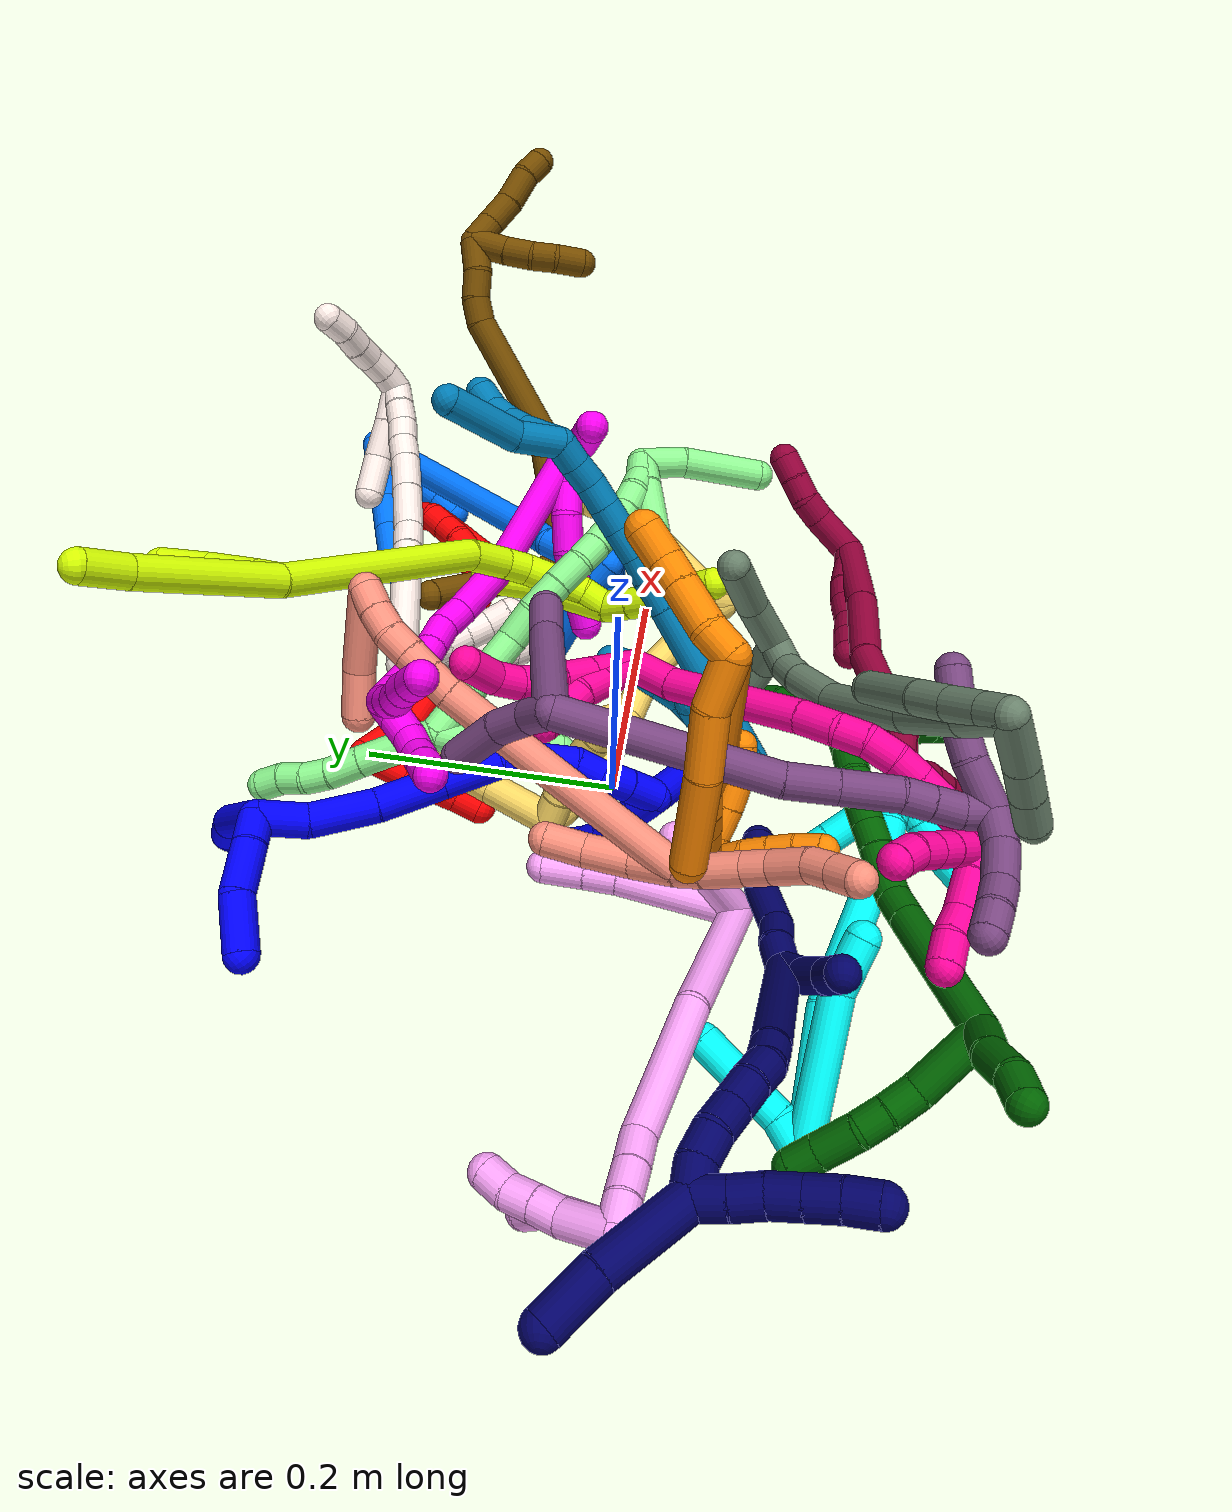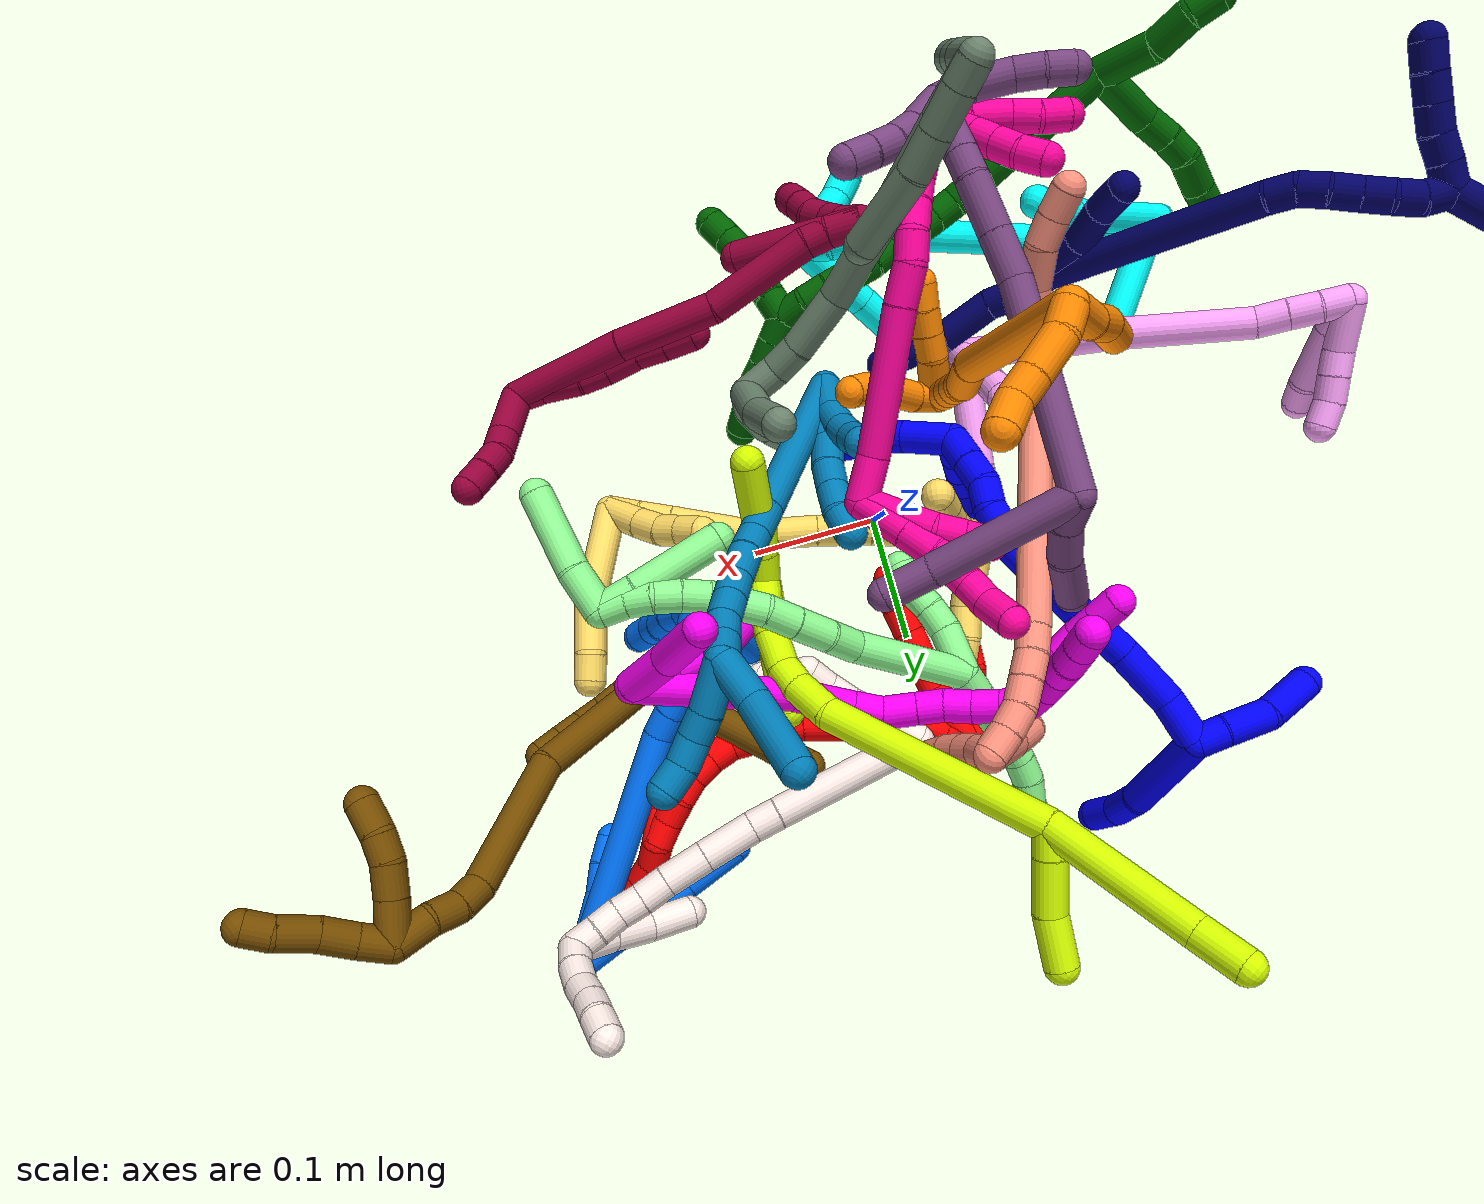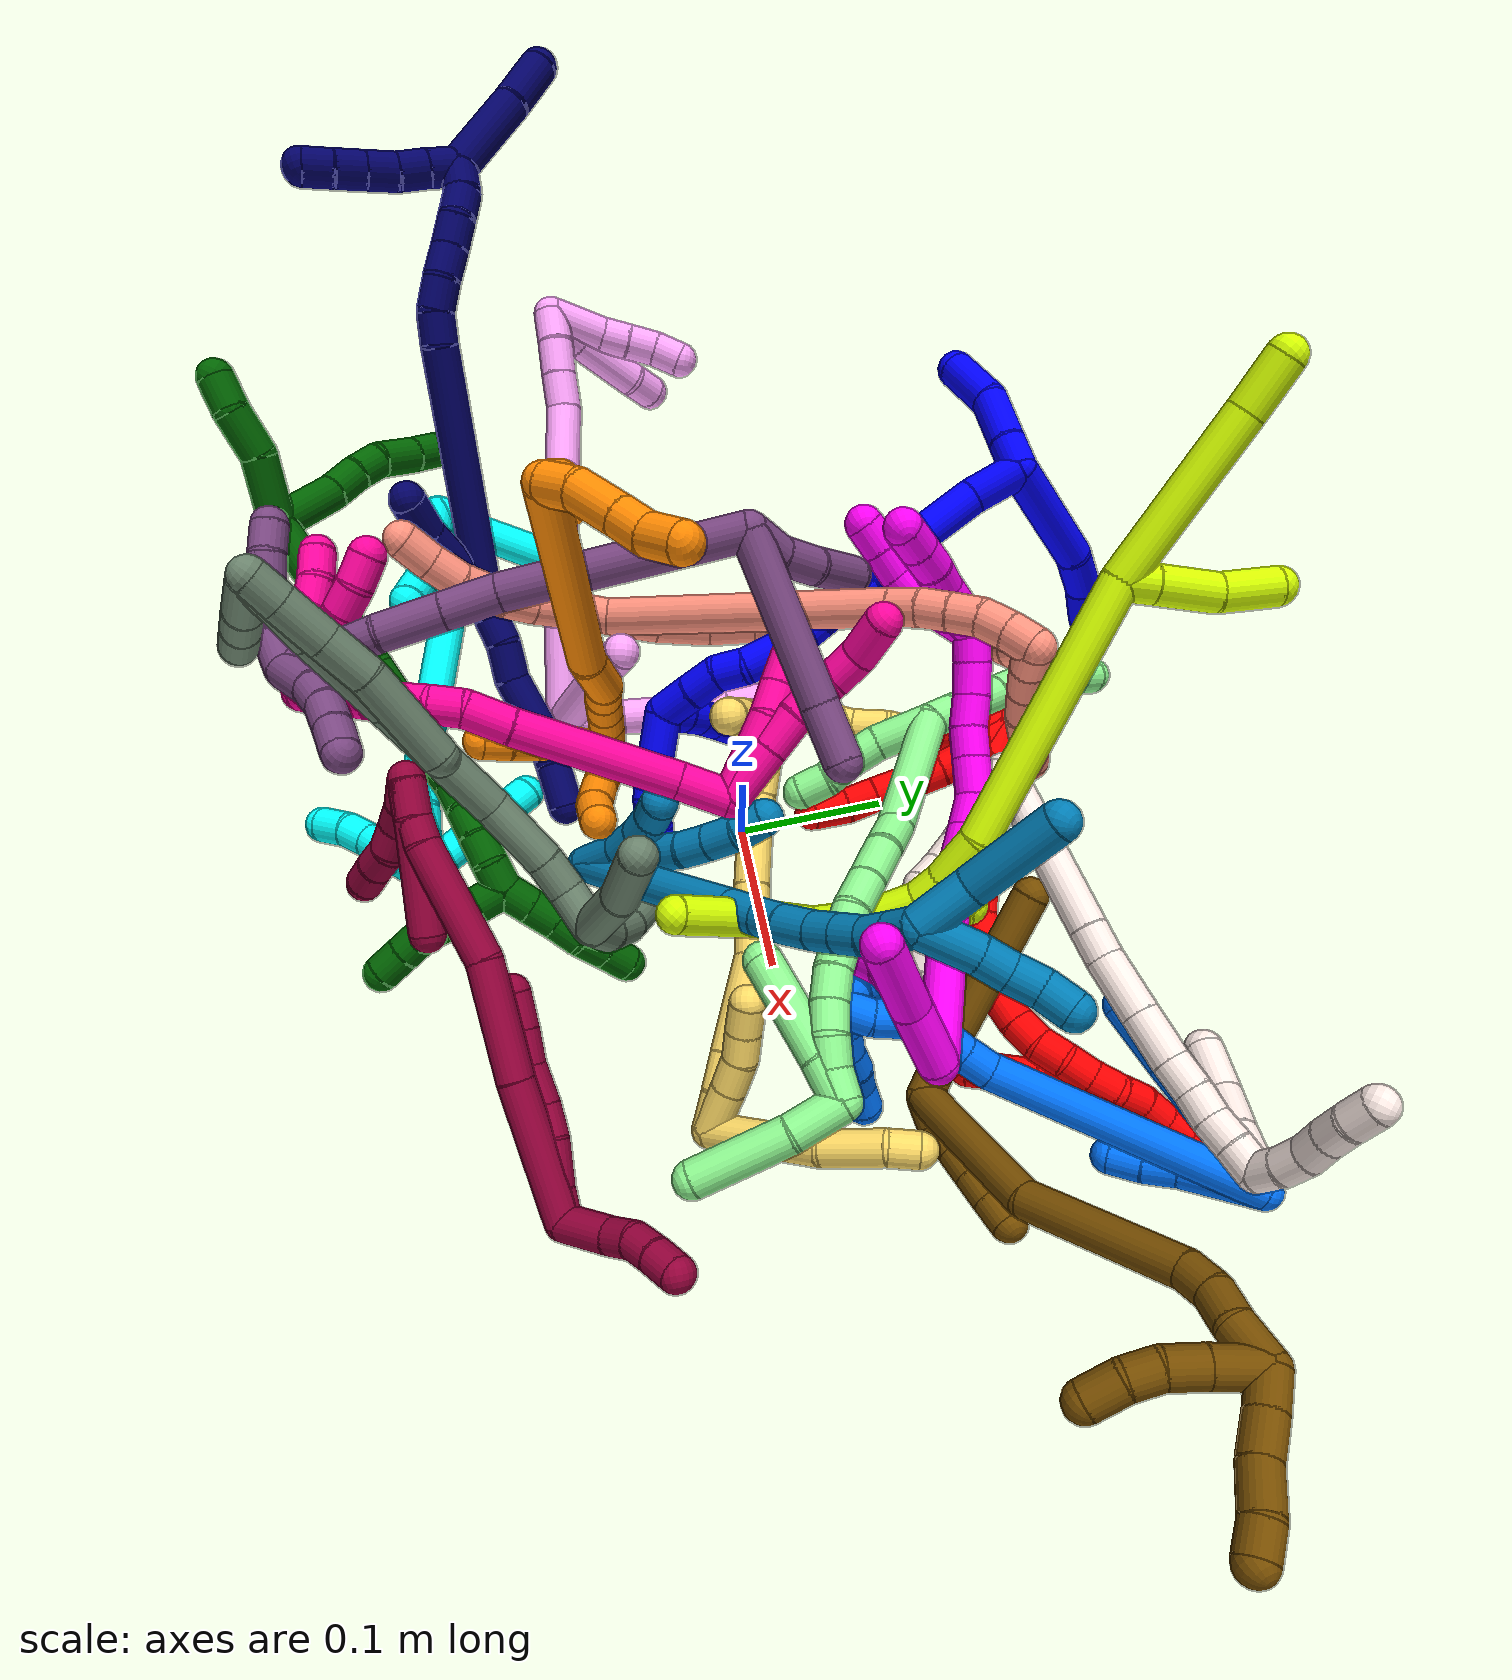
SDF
<sdf version="1.7">
 <world name="default">
  <plugin name="TubeGeneratorPlugin" filename="libtube_generator_plugin.so"/>
  <model name="photoneo_s_sensor">
   <static>1</static>
   <pose>0 0 2 1.57079 1.57079 3.14159</pose>
   <link name="link">
    <inertial><mass>0.1</mass></inertial>
    <sensor name="sensor" type="depth">
     <update_rate>30</update_rate>
     <camera>
      <horizontal_fov>1.22</horizontal_fov>
      <image><width>1920</width><height>1200</height><format>B8G8R8</format></image>
      <clip><near>0.1</near><far>4</far></clip>
      <depth_camera><output>points</output></depth_camera>
     </camera>
     <plugin name="camera_plugin" filename="libgazebo_ros_depth_camera.so">
      <baseline>0.2</baseline>
      <alwaysOn>1</alwaysOn>
      <updateRate>0.0</updateRate>
      <cameraName>camera_ir</cameraName>
      <imageTopicName>/camera/color/image_raw</imageTopicName>
      <cameraInfoTopicName>/camera/color/camera_info</cameraInfoTopicName>
      <depthImageTopicName>/camera/depth/image_raw</depthImageTopicName>
      <depthImageCameraInfoTopicName>/camera/depth/camera_info</depthImageCameraInfoTopicName>
      <pointCloudTopicName>/camera/depth/points</pointCloudTopicName>
      <frameName>fr_optical</frameName>
      <pointCloudCutoff>0.1</pointCloudCutoff>
      <pointCloudCutoffMax>2.0</pointCloudCutoffMax>
      <distortionK1>0</distortionK1>
      <distortionK2>0</distortionK2>
      <distortionK3>0</distortionK3>
      <distortionT1>0</distortionT1>
      <distortionT2>0</distortionT2>
      <CxPrime>0</CxPrime>
      <Cx>0</Cx>
      <Cy>0</Cy>
      <focalLength>0</focalLength>
      <hackBaseline>0</hackBaseline>
     </plugin>
    </sensor>
   </link>
  </model>
  <gravity>0 0 -9.8</gravity>
  <magnetic_field>6e-06 2.3e-05 -4.2e-05</magnetic_field>
  <atmosphere type="adiabatic"/>
  <physics name="default_physics" default="0" type="ode">
   <max_step_size>0.003</max_step_size>
   <real_time_factor>1</real_time_factor>
   <real_time_update_rate>1000</real_time_update_rate>
   <max_contacts>10000</max_contacts>
   <ode>
    <solver>
     <type>quick</type>
     <iters>100</iters>
     <sor>1.3</sor>
     <use_dynamic_moi_rescaling>0</use_dynamic_moi_rescaling>
    </solver>
    <constraints>
     <contact_max_correcting_vel>0</contact_max_correcting_vel>
     <contact_surface_layer>0.001</contact_surface_layer>
     <cfm>0</cfm>
     <erp>0.2</erp>
    </constraints>
   </ode>
  </physics>
  <scene><ambient>0.4 0.4 0.4 1</ambient><background>0.7 0.7 0.7 1</background><shadows>0</shadows></scene>
  <audio><device>default</device></audio>
  <spherical_coordinates>
   <surface_model>EARTH_WGS84</surface_model>
   <latitude_deg>0</latitude_deg>
   <longitude_deg>0</longitude_deg>
   <elevation>0</elevation>
   <heading_deg>0</heading_deg>
  </spherical_coordinates>
  <model name="bin">
   <static>1</static>
   <link name="bottom">
    <collision name="collision-bottom">
     <pose>0 0 -0.01 0 -0 0</pose>
     <geometry><box><size>0.8 0.6 0.02</size></box></geometry>
     <surface>
      <friction><ode><mu>100</mu><mu2>100</mu2></ode></friction>
      <contact><collide_bitmask>65535</collide_bitmask></contact>
     </surface>
    </collision>
   </link>
   <link name="west_wall">
    <collision name="collision-west_wall">
     <pose>-0.41 0 0.1 0 -0 0</pose>
     <geometry><box><size>0.02 0.6 0.2</size></box></geometry>
     <surface>
      <friction><ode><mu>100</mu><mu2>100</mu2></ode></friction>
      <contact><collide_bitmask>65535</collide_bitmask></contact>
     </surface>
    </collision>
   </link>
   <link name="east_wall">
    <collision name="collision-east_wall">
     <pose>0.41 0 0.1 0 -0 0</pose>
     <geometry><box><size>0.02 0.6 0.2</size></box></geometry>
     <surface>
      <friction><ode><mu>100</mu><mu2>100</mu2></ode></friction>
      <contact><collide_bitmask>65535</collide_bitmask></contact>
     </surface>
    </collision>
   </link>
   <link name="south_wall">
    <collision name="collision-south_wall">
     <pose>0 -0.31 0.1 0 -0 0</pose>
     <geometry><box><size>0.8 0.02 0.2</size></box></geometry>
     <surface>
      <friction><ode><mu>100</mu><mu2>100</mu2></ode></friction>
      <contact><collide_bitmask>65535</collide_bitmask></contact>
     </surface>
    </collision>
   </link>
   <link name="north_wall">
    <collision name="collision-north_wall">
     <pose>0 0.31 0.1 0 -0 0</pose>
     <geometry><box><size>0.8 0.02 0.2</size></box></geometry>
     <surface>
      <friction><ode><mu>100</mu><mu2>100</mu2></ode></friction>
      <contact><collide_bitmask>65535</collide_bitmask></contact>
     </surface>
    </collision>
   </link>
  </model>
  <model name="1">
   <static>0</static>
   <link name="1">
    <collision name="collision-cylinder-e_1_2_8">
     <pose>-0.032116 -0.028088 0.003881 1.43351 -0.847514 -0.749001</pose>
     <geometry><cylinder><radius>0.0125</radius><length>0.085684</length></cylinder></geometry>
     <surface>
      <friction><ode><mu>1.16</mu><mu2>1.16</mu2><slip1>0</slip1><slip2>0</slip2></ode></friction>
      <contact><ode><kp>1e+06</kp><kd>1</kd><max_vel>0</max_vel><min_depth>0.001</min_depth></ode></contact>
     </surface>
    </collision>
    <visual name="visual-cylinder-e_1_2_8">
     <pose>-0.032116 -0.028088 0.003881 1.43351 -0.847514 -0.749001</pose>
     <geometry><cylinder><radius>0.0125</radius><length>0.085684</length></cylinder></geometry>
     <material><ambient>0 0 1 1</ambient></material>
    </visual>
    <collision name="collision-cylinder-e_2_8_9">
     <pose>-0.074121 -0.070948 0.009835 1.43133 -0.58546 -0.512546</pose>
     <geometry><cylinder><radius>0.0125</radius><length>0.035793</length></cylinder></geometry>
     <surface>
      <friction><ode><mu>1.16</mu><mu2>1.16</mu2><slip1>0</slip1><slip2>0</slip2></ode></friction>
      <contact><ode><kp>1e+06</kp><kd>1</kd><max_vel>0</max_vel><min_depth>0.001</min_depth></ode></contact>
     </surface>
    </collision>
    <visual name="visual-cylinder-e_2_8_9">
     <pose>-0.074121 -0.070948 0.009835 1.43133 -0.58546 -0.512546</pose>
     <geometry><cylinder><radius>0.0125</radius><length>0.035793</length></cylinder></geometry>
     <material><ambient>0 0 1 1</ambient></material>
    </visual>
    <collision name="collision-cylinder-e_3_9_6">
     <pose>-0.09176 -0.097518 0.009879 1.74114 -0.574465 -0.674332</pose>
     <geometry><cylinder><radius>0.0125</radius><length>0.028523</length></cylinder></geometry>
     <surface>
      <friction><ode><mu>1.16</mu><mu2>1.16</mu2><slip1>0</slip1><slip2>0</slip2></ode></friction>
      <contact><ode><kp>1e+06</kp><kd>1</kd><max_vel>0</max_vel><min_depth>0.001</min_depth></ode></contact>
     </surface>
    </collision>
    <visual name="visual-cylinder-e_3_9_6">
     <pose>-0.09176 -0.097518 0.009879 1.74114 -0.574465 -0.674332</pose>
     <geometry><cylinder><radius>0.0125</radius><length>0.028523</length></cylinder></geometry>
     <material><ambient>0 0 1 1</ambient></material>
    </visual>
    <collision name="collision-cylinder-e_1_2_10">
     <pose>0.00795 0.000108 0.007963 -0.013587 0.784532 -0.005621</pose>
     <geometry><cylinder><radius>0.0125</radius><length>0.022504</length></cylinder></geometry>
     <surface>
      <friction><ode><mu>1.16</mu><mu2>1.16</mu2><slip1>0</slip1><slip2>0</slip2></ode></friction>
      <contact><ode><kp>1e+06</kp><kd>1</kd><max_vel>0</max_vel><min_depth>0.001</min_depth></ode></contact>
     </surface>
    </collision>
    <visual name="visual-cylinder-e_1_2_10">
     <pose>0.00795 0.000108 0.007963 -0.013587 0.784532 -0.005621</pose>
     <geometry><cylinder><radius>0.0125</radius><length>0.022504</length></cylinder></geometry>
     <material><ambient>0 0 1 1</ambient></material>
    </visual>
    <collision name="collision-cylinder-e_2_10_11">
     <pose>0.027865 -0.001551 0.029877 0.126007 0.704995 0.046406</pose>
     <geometry><cylinder><radius>0.0125</radius><length>0.036929</length></cylinder></geometry>
     <surface>
      <friction><ode><mu>1.16</mu><mu2>1.16</mu2><slip1>0</slip1><slip2>0</slip2></ode></friction>
      <contact><ode><kp>1e+06</kp><kd>1</kd><max_vel>0</max_vel><min_depth>0.001</min_depth></ode></contact>
     </surface>
    </collision>
    <visual name="visual-cylinder-e_2_10_11">
     <pose>0.027865 -0.001551 0.029877 0.126007 0.704995 0.046406</pose>
     <geometry><cylinder><radius>0.0125</radius><length>0.036929</length></cylinder></geometry>
     <material><ambient>0 0 1 1</ambient></material>
    </visual>
    <collision name="collision-cylinder-e_3_11_5">
     <pose>0.055083 -0.010323 0.055216 0.55148 0.8511 0.255098</pose>
     <geometry><cylinder><radius>0.0125</radius><length>0.040567</length></cylinder></geometry>
     <surface>
      <friction><ode><mu>1.16</mu><mu2>1.16</mu2><slip1>0</slip1><slip2>0</slip2></ode></friction>
      <contact><ode><kp>1e+06</kp><kd>1</kd><max_vel>0</max_vel><min_depth>0.001</min_depth></ode></contact>
     </surface>
    </collision>
    <visual name="visual-cylinder-e_3_11_5">
     <pose>0.055083 -0.010323 0.055216 0.55148 0.8511 0.255098</pose>
     <geometry><cylinder><radius>0.0125</radius><length>0.040567</length></cylinder></geometry>
     <material><ambient>0 0 1 1</ambient></material>
    </visual>
    <collision name="collision-cylinder-e_1_2_12">
     <pose>0.009451 -0.007968 -0.012853 2.58665 0.558569 1.57767</pose>
     <geometry><cylinder><radius>0.0125</radius><length>0.035665</length></cylinder></geometry>
     <surface>
      <friction><ode><mu>1.16</mu><mu2>1.16</mu2><slip1>0</slip1><slip2>0</slip2></ode></friction>
      <contact><ode><kp>1e+06</kp><kd>1</kd><max_vel>0</max_vel><min_depth>0.001</min_depth></ode></contact>
     </surface>
    </collision>
    <visual name="visual-cylinder-e_1_2_12">
     <pose>0.009451 -0.007968 -0.012853 2.58665 0.558569 1.57767</pose>
     <geometry><cylinder><radius>0.0125</radius><length>0.035665</length></cylinder></geometry>
     <material><ambient>0 0 1 1</ambient></material>
    </visual>
    <collision name="collision-cylinder-e_2_12_13">
     <pose>0.028324 -0.022019 -0.046973 2.86299 0.402683 1.93776</pose>
     <geometry><cylinder><radius>0.0125</radius><length>0.048087</length></cylinder></geometry>
     <surface>
      <friction><ode><mu>1.16</mu><mu2>1.16</mu2><slip1>0</slip1><slip2>0</slip2></ode></friction>
      <contact><ode><kp>1e+06</kp><kd>1</kd><max_vel>0</max_vel><min_depth>0.001</min_depth></ode></contact>
     </surface>
    </collision>
    <visual name="visual-cylinder-e_2_12_13">
     <pose>0.028324 -0.022019 -0.046973 2.86299 0.402683 1.93776</pose>
     <geometry><cylinder><radius>0.0125</radius><length>0.048087</length></cylinder></geometry>
     <material><ambient>0 0 1 1</ambient></material>
    </visual>
    <collision name="collision-cylinder-e_3_13_14">
     <pose>0.045222 -0.032376 -0.090772 2.95414 0.315133 2.07309</pose>
     <geometry><cylinder><radius>0.0125</radius><length>0.048242</length></cylinder></geometry>
     <surface>
      <friction><ode><mu>1.16</mu><mu2>1.16</mu2><slip1>0</slip1><slip2>0</slip2></ode></friction>
      <contact><ode><kp>1e+06</kp><kd>1</kd><max_vel>0</max_vel><min_depth>0.001</min_depth></ode></contact>
     </surface>
    </collision>
    <visual name="visual-cylinder-e_3_13_14">
     <pose>0.045222 -0.032376 -0.090772 2.95414 0.315133 2.07309</pose>
     <geometry><cylinder><radius>0.0125</radius><length>0.048242</length></cylinder></geometry>
     <material><ambient>0 0 1 1</ambient></material>
    </visual>
    <collision name="collision-cylinder-e_4_14_15">
     <pose>0.060143 -0.039663 -0.133422 2.99292 0.350808 2.34597</pose>
     <geometry><cylinder><radius>0.0125</radius><length>0.043327</length></cylinder></geometry>
     <surface>
      <friction><ode><mu>1.16</mu><mu2>1.16</mu2><slip1>0</slip1><slip2>0</slip2></ode></friction>
      <contact><ode><kp>1e+06</kp><kd>1</kd><max_vel>0</max_vel><min_depth>0.001</min_depth></ode></contact>
     </surface>
    </collision>
    <visual name="visual-cylinder-e_4_14_15">
     <pose>0.060143 -0.039663 -0.133422 2.99292 0.350808 2.34597</pose>
     <geometry><cylinder><radius>0.0125</radius><length>0.043327</length></cylinder></geometry>
     <material><ambient>0 0 1 1</ambient></material>
    </visual>
    <collision name="collision-cylinder-e_5_15_16">
     <pose>0.071797 -0.047856 -0.163086 2.64435 0.369798 1.26991</pose>
     <geometry><cylinder><radius>0.0125</radius><length>0.023293</length></cylinder></geometry>
     <surface>
      <friction><ode><mu>1.16</mu><mu2>1.16</mu2><slip1>0</slip1><slip2>0</slip2></ode></friction>
      <contact><ode><kp>1e+06</kp><kd>1</kd><max_vel>0</max_vel><min_depth>0.001</min_depth></ode></contact>
     </surface>
    </collision>
    <visual name="visual-cylinder-e_5_15_16">
     <pose>0.071797 -0.047856 -0.163086 2.64435 0.369798 1.26991</pose>
     <geometry><cylinder><radius>0.0125</radius><length>0.023293</length></cylinder></geometry>
     <material><ambient>0 0 1 1</ambient></material>
    </visual>
    <collision name="collision-cylinder-e_6_16_17">
     <pose>0.085507 -0.060086 -0.184018 2.58728 0.61698 1.68404</pose>
     <geometry><cylinder><radius>0.0125</radius><length>0.032841</length></cylinder></geometry>
     <surface>
      <friction><ode><mu>1.16</mu><mu2>1.16</mu2><slip1>0</slip1><slip2>0</slip2></ode></friction>
      <contact><ode><kp>1e+06</kp><kd>1</kd><max_vel>0</max_vel><min_depth>0.001</min_depth></ode></contact>
     </surface>
    </collision>
    <visual name="visual-cylinder-e_6_16_17">
     <pose>0.085507 -0.060086 -0.184018 2.58728 0.61698 1.68404</pose>
     <geometry><cylinder><radius>0.0125</radius><length>0.032841</length></cylinder></geometry>
     <material><ambient>0 0 1 1</ambient></material>
    </visual>
    <collision name="collision-cylinder-e_7_17_18">
     <pose>0.10217 -0.072818 -0.199497 2.19484 0.796691 1.37555</pose>
     <geometry><cylinder><radius>0.0125</radius><length>0.020033</length></cylinder></geometry>
     <surface>
      <friction><ode><mu>1.16</mu><mu2>1.16</mu2><slip1>0</slip1><slip2>0</slip2></ode></friction>
      <contact><ode><kp>1e+06</kp><kd>1</kd><max_vel>0</max_vel><min_depth>0.001</min_depth></ode></contact>
     </surface>
    </collision>
    <visual name="visual-cylinder-e_7_17_18">
     <pose>0.10217 -0.072818 -0.199497 2.19484 0.796691 1.37555</pose>
     <geometry><cylinder><radius>0.0125</radius><length>0.020033</length></cylinder></geometry>
     <material><ambient>0 0 1 1</ambient></material>
    </visual>
    <collision name="collision-cylinder-e_8_18_19">
     <pose>0.114227 -0.086453 -0.209824 2.23578 0.451072 0.881134</pose>
     <geometry><cylinder><radius>0.0125</radius><length>0.022457</length></cylinder></geometry>
     <surface>
      <friction><ode><mu>1.16</mu><mu2>1.16</mu2><slip1>0</slip1><slip2>0</slip2></ode></friction>
      <contact><ode><kp>1e+06</kp><kd>1</kd><max_vel>0</max_vel><min_depth>0.001</min_depth></ode></contact>
     </surface>
    </collision>
    <visual name="visual-cylinder-e_8_18_19">
     <pose>0.114227 -0.086453 -0.209824 2.23578 0.451072 0.881134</pose>
     <geometry><cylinder><radius>0.0125</radius><length>0.022457</length></cylinder></geometry>
     <material><ambient>0 0 1 1</ambient></material>
    </visual>
    <collision name="collision-cylinder-e_9_19_1">
     <pose>0.124497 -0.104214 -0.222739 2.1686 0.425334 0.775231</pose>
     <geometry><cylinder><radius>0.0125</radius><length>0.026056</length></cylinder></geometry>
     <surface>
      <friction><ode><mu>1.16</mu><mu2>1.16</mu2><slip1>0</slip1><slip2>0</slip2></ode></friction>
      <contact><ode><kp>1e+06</kp><kd>1</kd><max_vel>0</max_vel><min_depth>0.001</min_depth></ode></contact>
     </surface>
    </collision>
    <visual name="visual-cylinder-e_9_19_1">
     <pose>0.124497 -0.104214 -0.222739 2.1686 0.425334 0.775231</pose>
     <geometry><cylinder><radius>0.0125</radius><length>0.026056</length></cylinder></geometry>
     <material><ambient>0 0 1 1</ambient></material>
    </visual>
    <collision name="collision-cylinder-e_1_1_20">
     <pose>0.124674 -0.12007 -0.223384 0.786429 -0.546697 -0.231561</pose>
     <geometry><cylinder><radius>0.0125</radius><length>0.02</length></cylinder></geometry>
     <surface>
      <friction><ode><mu>1.16</mu><mu2>1.16</mu2><slip1>0</slip1><slip2>0</slip2></ode></friction>
      <contact><ode><kp>1e+06</kp><kd>1</kd><max_vel>0</max_vel><min_depth>0.001</min_depth></ode></contact>
     </surface>
    </collision>
    <visual name="visual-cylinder-e_1_1_20">
     <pose>0.124674 -0.12007 -0.223384 0.786429 -0.546697 -0.231561</pose>
     <geometry><cylinder><radius>0.0125</radius><length>0.02</length></cylinder></geometry>
     <material><ambient>0 0 1 1</ambient></material>
    </visual>
    <collision name="collision-cylinder-e_2_20_21">
     <pose>0.11478 -0.132583 -0.211339 0.821892 -0.488822 -0.216503</pose>
     <geometry><cylinder><radius>0.0125</radius><length>0.02</length></cylinder></geometry>
     <surface>
      <friction><ode><mu>1.16</mu><mu2>1.16</mu2><slip1>0</slip1><slip2>0</slip2></ode></friction>
      <contact><ode><kp>1e+06</kp><kd>1</kd><max_vel>0</max_vel><min_depth>0.001</min_depth></ode></contact>
     </surface>
    </collision>
    <visual name="visual-cylinder-e_2_20_21">
     <pose>0.11478 -0.132583 -0.211339 0.821892 -0.488822 -0.216503</pose>
     <geometry><cylinder><radius>0.0125</radius><length>0.02</length></cylinder></geometry>
     <material><ambient>0 0 1 1</ambient></material>
    </visual>
    <collision name="collision-cylinder-e_3_21_22">
     <pose>0.104871 -0.145737 -0.200026 0.900464 -0.548333 -0.270222</pose>
     <geometry><cylinder><radius>0.0125</radius><length>0.02</length></cylinder></geometry>
     <surface>
      <friction><ode><mu>1.16</mu><mu2>1.16</mu2><slip1>0</slip1><slip2>0</slip2></ode></friction>
      <contact><ode><kp>1e+06</kp><kd>1</kd><max_vel>0</max_vel><min_depth>0.001</min_depth></ode></contact>
     </surface>
    </collision>
    <visual name="visual-cylinder-e_3_21_22">
     <pose>0.104871 -0.145737 -0.200026 0.900464 -0.548333 -0.270222</pose>
     <geometry><cylinder><radius>0.0125</radius><length>0.02</length></cylinder></geometry>
     <material><ambient>0 0 1 1</ambient></material>
    </visual>
    <collision name="collision-cylinder-e_4_22_23">
     <pose>0.092827 -0.15807 -0.190092 0.883674 -0.752001 -0.369232</pose>
     <geometry><cylinder><radius>0.0125</radius><length>0.02</length></cylinder></geometry>
     <surface>
      <friction><ode><mu>1.16</mu><mu2>1.16</mu2><slip1>0</slip1><slip2>0</slip2></ode></friction>
      <contact><ode><kp>1e+06</kp><kd>1</kd><max_vel>0</max_vel><min_depth>0.001</min_depth></ode></contact>
     </surface>
    </collision>
    <visual name="visual-cylinder-e_4_22_23">
     <pose>0.092827 -0.15807 -0.190092 0.883674 -0.752001 -0.369232</pose>
     <geometry><cylinder><radius>0.0125</radius><length>0.02</length></cylinder></geometry>
     <material><ambient>0 0 1 1</ambient></material>
    </visual>
    <collision name="collision-cylinder-e_5_23_4">
     <pose>0.078179 -0.16814 -0.181064 0.788595 -0.897407 -0.395422</pose>
     <geometry><cylinder><radius>0.0125</radius><length>0.02</length></cylinder></geometry>
     <surface>
      <friction><ode><mu>1.16</mu><mu2>1.16</mu2><slip1>0</slip1><slip2>0</slip2></ode></friction>
      <contact><ode><kp>1e+06</kp><kd>1</kd><max_vel>0</max_vel><min_depth>0.001</min_depth></ode></contact>
     </surface>
    </collision>
    <visual name="visual-cylinder-e_5_23_4">
     <pose>0.078179 -0.16814 -0.181064 0.788595 -0.897407 -0.395422</pose>
     <geometry><cylinder><radius>0.0125</radius><length>0.02</length></cylinder></geometry>
     <material><ambient>0 0 1 1</ambient></material>
    </visual>
    <collision name="collision-cylinder-e_1_1_24">
     <pose>0.123547 -0.125207 -0.24446 2.50225 -0.325464 -0.920865</pose>
     <geometry><cylinder><radius>0.0125</radius><length>0.039565</length></cylinder></geometry>
     <surface>
      <friction><ode><mu>1.16</mu><mu2>1.16</mu2><slip1>0</slip1><slip2>0</slip2></ode></friction>
      <contact><ode><kp>1e+06</kp><kd>1</kd><max_vel>0</max_vel><min_depth>0.001</min_depth></ode></contact>
     </surface>
    </collision>
    <visual name="visual-cylinder-e_1_1_24">
     <pose>0.123547 -0.125207 -0.24446 2.50225 -0.325464 -0.920865</pose>
     <geometry><cylinder><radius>0.0125</radius><length>0.039565</length></cylinder></geometry>
     <material><ambient>0 0 1 1</ambient></material>
    </visual>
    <collision name="collision-cylinder-e_2_24_25">
     <pose>0.11331 -0.141175 -0.267519 2.60352 -0.396755 -1.25996</pose>
     <geometry><cylinder><radius>0.0125</radius><length>0.020244</length></cylinder></geometry>
     <surface>
      <friction><ode><mu>1.16</mu><mu2>1.16</mu2><slip1>0</slip1><slip2>0</slip2></ode></friction>
      <contact><ode><kp>1e+06</kp><kd>1</kd><max_vel>0</max_vel><min_depth>0.001</min_depth></ode></contact>
     </surface>
    </collision>
    <visual name="visual-cylinder-e_2_24_25">
     <pose>0.11331 -0.141175 -0.267519 2.60352 -0.396755 -1.25996</pose>
     <geometry><cylinder><radius>0.0125</radius><length>0.020244</length></cylinder></geometry>
     <material><ambient>0 0 1 1</ambient></material>
    </visual>
    <collision name="collision-cylinder-e_3_25_26">
     <pose>0.103516 -0.151187 -0.281758 2.4429 -0.62657 -1.45372</pose>
     <geometry><cylinder><radius>0.0125</radius><length>0.020066</length></cylinder></geometry>
     <surface>
      <friction><ode><mu>1.16</mu><mu2>1.16</mu2><slip1>0</slip1><slip2>0</slip2></ode></friction>
      <contact><ode><kp>1e+06</kp><kd>1</kd><max_vel>0</max_vel><min_depth>0.001</min_depth></ode></contact>
     </surface>
    </collision>
    <visual name="visual-cylinder-e_3_25_26">
     <pose>0.103516 -0.151187 -0.281758 2.4429 -0.62657 -1.45372</pose>
     <geometry><cylinder><radius>0.0125</radius><length>0.020066</length></cylinder></geometry>
     <material><ambient>0 0 1 1</ambient></material>
    </visual>
    <collision name="collision-cylinder-e_4_26_3">
     <pose>0.092258 -0.161279 -0.29496 2.53292 -0.563529 -1.48923</pose>
     <geometry><cylinder><radius>0.0125</radius><length>0.020124</length></cylinder></geometry>
     <surface>
      <friction><ode><mu>1.16</mu><mu2>1.16</mu2><slip1>0</slip1><slip2>0</slip2></ode></friction>
      <contact><ode><kp>1e+06</kp><kd>1</kd><max_vel>0</max_vel><min_depth>0.001</min_depth></ode></contact>
     </surface>
    </collision>
    <visual name="visual-cylinder-e_4_26_3">
     <pose>0.092258 -0.161279 -0.29496 2.53292 -0.563529 -1.48923</pose>
     <geometry><cylinder><radius>0.0125</radius><length>0.020124</length></cylinder></geometry>
     <material><ambient>0 0 1 1</ambient></material>
    </visual>
    <collision name="collision-sphere-3">
     <pose>0.086883 -0.166142 -0.301938 0 -0 0</pose>
     <geometry><sphere><radius>0.0125</radius></sphere></geometry>
     <surface>
      <friction><ode><mu>1.16</mu><mu2>1.16</mu2><slip1>0</slip1><slip2>0</slip2></ode></friction>
      <contact><ode><kp>1e+06</kp><kd>1</kd><max_vel>0</max_vel><min_depth>0.001</min_depth></ode></contact>
     </surface>
    </collision>
    <visual name="visual-sphere-3">
     <pose>0.086883 -0.166142 -0.301938 0 -0 0</pose>
     <geometry><sphere><radius>0.0125</radius></sphere></geometry>
     <material><ambient>0 0 1 1</ambient></material>
    </visual>
    <collision name="collision-sphere-26">
     <pose>0.097633 -0.156415 -0.287981 0 -0 0</pose>
     <geometry><sphere><radius>0.0125</radius></sphere></geometry>
     <surface>
      <friction><ode><mu>1.16</mu><mu2>1.16</mu2><slip1>0</slip1><slip2>0</slip2></ode></friction>
      <contact><ode><kp>1e+06</kp><kd>1</kd><max_vel>0</max_vel><min_depth>0.001</min_depth></ode></contact>
     </surface>
    </collision>
    <visual name="visual-sphere-26">
     <pose>0.097633 -0.156415 -0.287981 0 -0 0</pose>
     <geometry><sphere><radius>0.0125</radius></sphere></geometry>
     <material><ambient>0 0 1 1</ambient></material>
    </visual>
    <collision name="collision-sphere-25">
     <pose>0.109399 -0.14596 -0.275535 0 -0 0</pose>
     <geometry><sphere><radius>0.0125</radius></sphere></geometry>
     <surface>
      <friction><ode><mu>1.16</mu><mu2>1.16</mu2><slip1>0</slip1><slip2>0</slip2></ode></friction>
      <contact><ode><kp>1e+06</kp><kd>1</kd><max_vel>0</max_vel><min_depth>0.001</min_depth></ode></contact>
     </surface>
    </collision>
    <visual name="visual-sphere-25">
     <pose>0.109399 -0.14596 -0.275535 0 -0 0</pose>
     <geometry><sphere><radius>0.0125</radius></sphere></geometry>
     <material><ambient>0 0 1 1</ambient></material>
    </visual>
    <collision name="collision-sphere-24">
     <pose>0.117222 -0.136391 -0.259502 0 -0 0</pose>
     <geometry><sphere><radius>0.0125</radius></sphere></geometry>
     <surface>
      <friction><ode><mu>1.16</mu><mu2>1.16</mu2><slip1>0</slip1><slip2>0</slip2></ode></friction>
      <contact><ode><kp>1e+06</kp><kd>1</kd><max_vel>0</max_vel><min_depth>0.001</min_depth></ode></contact>
     </surface>
    </collision>
    <visual name="visual-sphere-24">
     <pose>0.117222 -0.136391 -0.259502 0 -0 0</pose>
     <geometry><sphere><radius>0.0125</radius></sphere></geometry>
     <material><ambient>0 0 1 1</ambient></material>
    </visual>
    <collision name="collision-sphere-4">
     <pose>0.070362 -0.172564 -0.176668 0 -0 0</pose>
     <geometry><sphere><radius>0.0125</radius></sphere></geometry>
     <surface>
      <friction><ode><mu>1.16</mu><mu2>1.16</mu2><slip1>0</slip1><slip2>0</slip2></ode></friction>
      <contact><ode><kp>1e+06</kp><kd>1</kd><max_vel>0</max_vel><min_depth>0.001</min_depth></ode></contact>
     </surface>
    </collision>
    <visual name="visual-sphere-4">
     <pose>0.070362 -0.172564 -0.176668 0 -0 0</pose>
     <geometry><sphere><radius>0.0125</radius></sphere></geometry>
     <material><ambient>0 0 1 1</ambient></material>
    </visual>
    <collision name="collision-sphere-23">
     <pose>0.085996 -0.163716 -0.185459 0 -0 0</pose>
     <geometry><sphere><radius>0.0125</radius></sphere></geometry>
     <surface>
      <friction><ode><mu>1.16</mu><mu2>1.16</mu2><slip1>0</slip1><slip2>0</slip2></ode></friction>
      <contact><ode><kp>1e+06</kp><kd>1</kd><max_vel>0</max_vel><min_depth>0.001</min_depth></ode></contact>
     </surface>
    </collision>
    <visual name="visual-sphere-23">
     <pose>0.085996 -0.163716 -0.185459 0 -0 0</pose>
     <geometry><sphere><radius>0.0125</radius></sphere></geometry>
     <material><ambient>0 0 1 1</ambient></material>
    </visual>
    <collision name="collision-sphere-22">
     <pose>0.099658 -0.152424 -0.194724 0 -0 0</pose>
     <geometry><sphere><radius>0.0125</radius></sphere></geometry>
     <surface>
      <friction><ode><mu>1.16</mu><mu2>1.16</mu2><slip1>0</slip1><slip2>0</slip2></ode></friction>
      <contact><ode><kp>1e+06</kp><kd>1</kd><max_vel>0</max_vel><min_depth>0.001</min_depth></ode></contact>
     </surface>
    </collision>
    <visual name="visual-sphere-22">
     <pose>0.099658 -0.152424 -0.194724 0 -0 0</pose>
     <geometry><sphere><radius>0.0125</radius></sphere></geometry>
     <material><ambient>0 0 1 1</ambient></material>
    </visual>
    <collision name="collision-sphere-21">
     <pose>0.110084 -0.13905 -0.205328 0 -0 0</pose>
     <geometry><sphere><radius>0.0125</radius></sphere></geometry>
     <surface>
      <friction><ode><mu>1.16</mu><mu2>1.16</mu2><slip1>0</slip1><slip2>0</slip2></ode></friction>
      <contact><ode><kp>1e+06</kp><kd>1</kd><max_vel>0</max_vel><min_depth>0.001</min_depth></ode></contact>
     </surface>
    </collision>
    <visual name="visual-sphere-21">
     <pose>0.110084 -0.13905 -0.205328 0 -0 0</pose>
     <geometry><sphere><radius>0.0125</radius></sphere></geometry>
     <material><ambient>0 0 1 1</ambient></material>
    </visual>
    <collision name="collision-sphere-20">
     <pose>0.119475 -0.126116 -0.21735 0 -0 0</pose>
     <geometry><sphere><radius>0.0125</radius></sphere></geometry>
     <surface>
      <friction><ode><mu>1.16</mu><mu2>1.16</mu2><slip1>0</slip1><slip2>0</slip2></ode></friction>
      <contact><ode><kp>1e+06</kp><kd>1</kd><max_vel>0</max_vel><min_depth>0.001</min_depth></ode></contact>
     </surface>
    </collision>
    <visual name="visual-sphere-20">
     <pose>0.119475 -0.126116 -0.21735 0 -0 0</pose>
     <geometry><sphere><radius>0.0125</radius></sphere></geometry>
     <material><ambient>0 0 1 1</ambient></material>
    </visual>
    <collision name="collision-sphere-11">
     <pose>0.03983 -0.003318 0.043828 0 -0 0</pose>
     <geometry><sphere><radius>0.0125</radius></sphere></geometry>
     <surface>
      <friction><ode><mu>1.16</mu><mu2>1.16</mu2><slip1>0</slip1><slip2>0</slip2></ode></friction>
      <contact><ode><kp>1e+06</kp><kd>1</kd><max_vel>0</max_vel><min_depth>0.001</min_depth></ode></contact>
     </surface>
    </collision>
    <visual name="visual-sphere-11">
     <pose>0.03983 -0.003318 0.043828 0 -0 0</pose>
     <geometry><sphere><radius>0.0125</radius></sphere></geometry>
     <material><ambient>0 0 1 1</ambient></material>
    </visual>
    <collision name="collision-sphere-10">
     <pose>0.015899 0.000216 0.015925 0 -0 0</pose>
     <geometry><sphere><radius>0.0125</radius></sphere></geometry>
     <surface>
      <friction><ode><mu>1.16</mu><mu2>1.16</mu2><slip1>0</slip1><slip2>0</slip2></ode></friction>
      <contact><ode><kp>1e+06</kp><kd>1</kd><max_vel>0</max_vel><min_depth>0.001</min_depth></ode></contact>
     </surface>
    </collision>
    <visual name="visual-sphere-10">
     <pose>0.015899 0.000216 0.015925 0 -0 0</pose>
     <geometry><sphere><radius>0.0125</radius></sphere></geometry>
     <material><ambient>0 0 1 1</ambient></material>
    </visual>
    <collision name="collision-sphere-6">
     <pose>-0.099509 -0.109317 0.007849 0 -0 0</pose>
     <geometry><sphere><radius>0.0125</radius></sphere></geometry>
     <surface>
      <friction><ode><mu>1.16</mu><mu2>1.16</mu2><slip1>0</slip1><slip2>0</slip2></ode></friction>
      <contact><ode><kp>1e+06</kp><kd>1</kd><max_vel>0</max_vel><min_depth>0.001</min_depth></ode></contact>
     </surface>
    </collision>
    <visual name="visual-sphere-6">
     <pose>-0.099509 -0.109317 0.007849 0 -0 0</pose>
     <geometry><sphere><radius>0.0125</radius></sphere></geometry>
     <material><ambient>0 0 1 1</ambient></material>
    </visual>
    <collision name="collision-sphere-9">
     <pose>-0.084011 -0.085719 0.011908 0 -0 0</pose>
     <geometry><sphere><radius>0.0125</radius></sphere></geometry>
     <surface>
      <friction><ode><mu>1.16</mu><mu2>1.16</mu2><slip1>0</slip1><slip2>0</slip2></ode></friction>
      <contact><ode><kp>1e+06</kp><kd>1</kd><max_vel>0</max_vel><min_depth>0.001</min_depth></ode></contact>
     </surface>
    </collision>
    <visual name="visual-sphere-9">
     <pose>-0.084011 -0.085719 0.011908 0 -0 0</pose>
     <geometry><sphere><radius>0.0125</radius></sphere></geometry>
     <material><ambient>0 0 1 1</ambient></material>
    </visual>
    <collision name="collision-sphere-2">
     <geometry><sphere><radius>0.0125</radius></sphere></geometry>
     <surface>
      <friction><ode><mu>1.16</mu><mu2>1.16</mu2><slip1>0</slip1><slip2>0</slip2></ode></friction>
      <contact><ode><kp>1e+06</kp><kd>1</kd><max_vel>0</max_vel><min_depth>0.001</min_depth></ode></contact>
     </surface>
    </collision>
    <visual name="visual-sphere-2">
     <geometry><sphere><radius>0.0125</radius></sphere></geometry>
     <material><ambient>0 0 1 1</ambient></material>
    </visual>
    <collision name="collision-sphere-19">
     <pose>0.119122 -0.094405 -0.21606 0 -0 0</pose>
     <geometry><sphere><radius>0.0125</radius></sphere></geometry>
     <surface>
      <friction><ode><mu>1.16</mu><mu2>1.16</mu2><slip1>0</slip1><slip2>0</slip2></ode></friction>
      <contact><ode><kp>1e+06</kp><kd>1</kd><max_vel>0</max_vel><min_depth>0.001</min_depth></ode></contact>
     </surface>
    </collision>
    <visual name="visual-sphere-19">
     <pose>0.119122 -0.094405 -0.21606 0 -0 0</pose>
     <geometry><sphere><radius>0.0125</radius></sphere></geometry>
     <material><ambient>0 0 1 1</ambient></material>
    </visual>
    <collision name="collision-sphere-8">
     <pose>-0.064232 -0.056176 0.007761 0 -0 0</pose>
     <geometry><sphere><radius>0.0125</radius></sphere></geometry>
     <surface>
      <friction><ode><mu>1.16</mu><mu2>1.16</mu2><slip1>0</slip1><slip2>0</slip2></ode></friction>
      <contact><ode><kp>1e+06</kp><kd>1</kd><max_vel>0</max_vel><min_depth>0.001</min_depth></ode></contact>
     </surface>
    </collision>
    <visual name="visual-sphere-8">
     <pose>-0.064232 -0.056176 0.007761 0 -0 0</pose>
     <geometry><sphere><radius>0.0125</radius></sphere></geometry>
     <material><ambient>0 0 1 1</ambient></material>
    </visual>
    <collision name="collision-sphere-5">
     <pose>0.070337 -0.017329 0.066604 0 -0 0</pose>
     <geometry><sphere><radius>0.0125</radius></sphere></geometry>
     <surface>
      <friction><ode><mu>1.16</mu><mu2>1.16</mu2><slip1>0</slip1><slip2>0</slip2></ode></friction>
      <contact><ode><kp>1e+06</kp><kd>1</kd><max_vel>0</max_vel><min_depth>0.001</min_depth></ode></contact>
     </surface>
    </collision>
    <visual name="visual-sphere-5">
     <pose>0.070337 -0.017329 0.066604 0 -0 0</pose>
     <geometry><sphere><radius>0.0125</radius></sphere></geometry>
     <material><ambient>0 0 1 1</ambient></material>
    </visual>
    <collision name="collision-sphere-12">
     <pose>0.018901 -0.015935 -0.025706 0 -0 0</pose>
     <geometry><sphere><radius>0.0125</radius></sphere></geometry>
     <surface>
      <friction><ode><mu>1.16</mu><mu2>1.16</mu2><slip1>0</slip1><slip2>0</slip2></ode></friction>
      <contact><ode><kp>1e+06</kp><kd>1</kd><max_vel>0</max_vel><min_depth>0.001</min_depth></ode></contact>
     </surface>
    </collision>
    <visual name="visual-sphere-12">
     <pose>0.018901 -0.015935 -0.025706 0 -0 0</pose>
     <geometry><sphere><radius>0.0125</radius></sphere></geometry>
     <material><ambient>0 0 1 1</ambient></material>
    </visual>
    <collision name="collision-sphere-13">
     <pose>0.037746 -0.028102 -0.06824 0 -0 0</pose>
     <geometry><sphere><radius>0.0125</radius></sphere></geometry>
     <surface>
      <friction><ode><mu>1.16</mu><mu2>1.16</mu2><slip1>0</slip1><slip2>0</slip2></ode></friction>
      <contact><ode><kp>1e+06</kp><kd>1</kd><max_vel>0</max_vel><min_depth>0.001</min_depth></ode></contact>
     </surface>
    </collision>
    <visual name="visual-sphere-13">
     <pose>0.037746 -0.028102 -0.06824 0 -0 0</pose>
     <geometry><sphere><radius>0.0125</radius></sphere></geometry>
     <material><ambient>0 0 1 1</ambient></material>
    </visual>
    <collision name="collision-sphere-14">
     <pose>0.052698 -0.03665 -0.113303 0 -0 0</pose>
     <geometry><sphere><radius>0.0125</radius></sphere></geometry>
     <surface>
      <friction><ode><mu>1.16</mu><mu2>1.16</mu2><slip1>0</slip1><slip2>0</slip2></ode></friction>
      <contact><ode><kp>1e+06</kp><kd>1</kd><max_vel>0</max_vel><min_depth>0.001</min_depth></ode></contact>
     </surface>
    </collision>
    <visual name="visual-sphere-14">
     <pose>0.052698 -0.03665 -0.113303 0 -0 0</pose>
     <geometry><sphere><radius>0.0125</radius></sphere></geometry>
     <material><ambient>0 0 1 1</ambient></material>
    </visual>
    <collision name="collision-sphere-15">
     <pose>0.067588 -0.042677 -0.153542 0 -0 0</pose>
     <geometry><sphere><radius>0.0125</radius></sphere></geometry>
     <surface>
      <friction><ode><mu>1.16</mu><mu2>1.16</mu2><slip1>0</slip1><slip2>0</slip2></ode></friction>
      <contact><ode><kp>1e+06</kp><kd>1</kd><max_vel>0</max_vel><min_depth>0.001</min_depth></ode></contact>
     </surface>
    </collision>
    <visual name="visual-sphere-15">
     <pose>0.067588 -0.042677 -0.153542 0 -0 0</pose>
     <geometry><sphere><radius>0.0125</radius></sphere></geometry>
     <material><ambient>0 0 1 1</ambient></material>
    </visual>
    <collision name="collision-sphere-16">
     <pose>0.076006 -0.053036 -0.17263 0 -0 0</pose>
     <geometry><sphere><radius>0.0125</radius></sphere></geometry>
     <surface>
      <friction><ode><mu>1.16</mu><mu2>1.16</mu2><slip1>0</slip1><slip2>0</slip2></ode></friction>
      <contact><ode><kp>1e+06</kp><kd>1</kd><max_vel>0</max_vel><min_depth>0.001</min_depth></ode></contact>
     </surface>
    </collision>
    <visual name="visual-sphere-16">
     <pose>0.076006 -0.053036 -0.17263 0 -0 0</pose>
     <geometry><sphere><radius>0.0125</radius></sphere></geometry>
     <material><ambient>0 0 1 1</ambient></material>
    </visual>
    <collision name="collision-sphere-17">
     <pose>0.095008 -0.067135 -0.195406 0 -0 0</pose>
     <geometry><sphere><radius>0.0125</radius></sphere></geometry>
     <surface>
      <friction><ode><mu>1.16</mu><mu2>1.16</mu2><slip1>0</slip1><slip2>0</slip2></ode></friction>
      <contact><ode><kp>1e+06</kp><kd>1</kd><max_vel>0</max_vel><min_depth>0.001</min_depth></ode></contact>
     </surface>
    </collision>
    <visual name="visual-sphere-17">
     <pose>0.095008 -0.067135 -0.195406 0 -0 0</pose>
     <geometry><sphere><radius>0.0125</radius></sphere></geometry>
     <material><ambient>0 0 1 1</ambient></material>
    </visual>
    <collision name="collision-sphere-18">
     <pose>0.109332 -0.0785 -0.203589 0 -0 0</pose>
     <geometry><sphere><radius>0.0125</radius></sphere></geometry>
     <surface>
      <friction><ode><mu>1.16</mu><mu2>1.16</mu2><slip1>0</slip1><slip2>0</slip2></ode></friction>
      <contact><ode><kp>1e+06</kp><kd>1</kd><max_vel>0</max_vel><min_depth>0.001</min_depth></ode></contact>
     </surface>
    </collision>
    <visual name="visual-sphere-18">
     <pose>0.109332 -0.0785 -0.203589 0 -0 0</pose>
     <geometry><sphere><radius>0.0125</radius></sphere></geometry>
     <material><ambient>0 0 1 1</ambient></material>
    </visual>
    <collision name="collision-sphere-1">
     <pose>0.129873 -0.114023 -0.229418 0 -0 0</pose>
     <geometry><sphere><radius>0.0125</radius></sphere></geometry>
     <surface>
      <friction><ode><mu>1.16</mu><mu2>1.16</mu2><slip1>0</slip1><slip2>0</slip2></ode></friction>
      <contact><ode><kp>1e+06</kp><kd>1</kd><max_vel>0</max_vel><min_depth>0.001</min_depth></ode></contact>
     </surface>
    </collision>
    <visual name="visual-sphere-1">
     <pose>0.129873 -0.114023 -0.229418 0 -0 0</pose>
     <geometry><sphere><radius>0.0125</radius></sphere></geometry>
     <material><ambient>0 0 1 1</ambient></material>
    </visual>
    <inertial>
     <pose>0.047554 -0.067482 -0.106051 0 -0 0</pose>
     <mass>0.75</mass>
     <inertia><ixx>4.2e-05</ixx><ixy>0</ixy><ixz>0</ixz><iyy>4.7e-05</iyy><iyz>0</iyz><izz>8.3e-05</izz></inertia>
    </inertial>
   </link>
   <pose>-0.166985 0.22483 0.134552 1.76042 -0.147813 -2.2672</pose>
  </model>
  <model name="2">
   <static>0</static>
   <link name="2">
    <collision name="collision-cylinder-e_1_2_8">
     <pose>0.006587 0.002177 -0.011429 -2.95335 0.515194 -2.45344</pose>
     <geometry><cylinder><radius>0.0125</radius><length>0.02674</length></cylinder></geometry>
     <surface>
      <friction><ode><mu>1.16</mu><mu2>1.16</mu2><slip1>0</slip1><slip2>0</slip2></ode></friction>
      <contact><ode><kp>1e+06</kp><kd>1</kd><max_vel>0</max_vel><min_depth>0.001</min_depth></ode></contact>
     </surface>
    </collision>
    <visual name="visual-cylinder-e_1_2_8">
     <pose>0.006587 0.002177 -0.011429 -2.95335 0.515194 -2.45344</pose>
     <geometry><cylinder><radius>0.0125</radius><length>0.02674</length></cylinder></geometry>
     <material><ambient>1 0 0 1</ambient></material>
    </visual>
    <collision name="collision-cylinder-e_2_8_9">
     <pose>0.017212 0.004337 -0.036058 3.14023 0.29683 3.13248</pose>
     <geometry><cylinder><radius>0.0125</radius><length>0.027607</length></cylinder></geometry>
     <surface>
      <friction><ode><mu>1.16</mu><mu2>1.16</mu2><slip1>0</slip1><slip2>0</slip2></ode></friction>
      <contact><ode><kp>1e+06</kp><kd>1</kd><max_vel>0</max_vel><min_depth>0.001</min_depth></ode></contact>
     </surface>
    </collision>
    <visual name="visual-cylinder-e_2_8_9">
     <pose>0.017212 0.004337 -0.036058 3.14023 0.29683 3.13248</pose>
     <geometry><cylinder><radius>0.0125</radius><length>0.027607</length></cylinder></geometry>
     <material><ambient>1 0 0 1</ambient></material>
    </visual>
    <collision name="collision-cylinder-e_3_9_10">
     <pose>0.024337 0.003219 -0.062146 3.05645 0.234308 2.44705</pose>
     <geometry><cylinder><radius>0.0125</radius><length>0.026596</length></cylinder></geometry>
     <surface>
      <friction><ode><mu>1.16</mu><mu2>1.16</mu2><slip1>0</slip1><slip2>0</slip2></ode></friction>
      <contact><ode><kp>1e+06</kp><kd>1</kd><max_vel>0</max_vel><min_depth>0.001</min_depth></ode></contact>
     </surface>
    </collision>
    <visual name="visual-cylinder-e_3_9_10">
     <pose>0.024337 0.003219 -0.062146 3.05645 0.234308 2.44705</pose>
     <geometry><cylinder><radius>0.0125</radius><length>0.026596</length></cylinder></geometry>
     <material><ambient>1 0 0 1</ambient></material>
    </visual>
    <collision name="collision-cylinder-e_4_10_11">
     <pose>0.030264 0.00081 -0.086075 3.02362 0.25003 2.26303</pose>
     <geometry><cylinder><radius>0.0125</radius><length>0.022951</length></cylinder></geometry>
     <surface>
      <friction><ode><mu>1.16</mu><mu2>1.16</mu2><slip1>0</slip1><slip2>0</slip2></ode></friction>
      <contact><ode><kp>1e+06</kp><kd>1</kd><max_vel>0</max_vel><min_depth>0.001</min_depth></ode></contact>
     </surface>
    </collision>
    <visual name="visual-cylinder-e_4_10_11">
     <pose>0.030264 0.00081 -0.086075 3.02362 0.25003 2.26303</pose>
     <geometry><cylinder><radius>0.0125</radius><length>0.022951</length></cylinder></geometry>
     <material><ambient>1 0 0 1</ambient></material>
    </visual>
    <collision name="collision-cylinder-e_5_11_12">
     <pose>0.035826 -0.001516 -0.107429 3.04329 0.256923 2.41386</pose>
     <geometry><cylinder><radius>0.0125</radius><length>0.021429</length></cylinder></geometry>
     <surface>
      <friction><ode><mu>1.16</mu><mu2>1.16</mu2><slip1>0</slip1><slip2>0</slip2></ode></friction>
      <contact><ode><kp>1e+06</kp><kd>1</kd><max_vel>0</max_vel><min_depth>0.001</min_depth></ode></contact>
     </surface>
    </collision>
    <visual name="visual-cylinder-e_5_11_12">
     <pose>0.035826 -0.001516 -0.107429 3.04329 0.256923 2.41386</pose>
     <geometry><cylinder><radius>0.0125</radius><length>0.021429</length></cylinder></geometry>
     <material><ambient>1 0 0 1</ambient></material>
    </visual>
    <collision name="collision-cylinder-e_6_12_6">
     <pose>0.041182 -0.006345 -0.129177 2.81984 0.215057 1.17396</pose>
     <geometry><cylinder><radius>0.0125</radius><length>0.024677</length></cylinder></geometry>
     <surface>
      <friction><ode><mu>1.16</mu><mu2>1.16</mu2><slip1>0</slip1><slip2>0</slip2></ode></friction>
      <contact><ode><kp>1e+06</kp><kd>1</kd><max_vel>0</max_vel><min_depth>0.001</min_depth></ode></contact>
     </surface>
    </collision>
    <visual name="visual-cylinder-e_6_12_6">
     <pose>0.041182 -0.006345 -0.129177 2.81984 0.215057 1.17396</pose>
     <geometry><cylinder><radius>0.0125</radius><length>0.024677</length></cylinder></geometry>
     <material><ambient>1 0 0 1</ambient></material>
    </visual>
    <collision name="collision-cylinder-e_1_2_13">
     <pose>-0.002371 -0.002314 -0.018689 3.01841 -0.125273 -1.58767</pose>
     <geometry><cylinder><radius>0.0125</radius><length>0.03796</length></cylinder></geometry>
     <surface>
      <friction><ode><mu>1.16</mu><mu2>1.16</mu2><slip1>0</slip1><slip2>0</slip2></ode></friction>
      <contact><ode><kp>1e+06</kp><kd>1</kd><max_vel>0</max_vel><min_depth>0.001</min_depth></ode></contact>
     </surface>
    </collision>
    <visual name="visual-cylinder-e_1_2_13">
     <pose>-0.002371 -0.002314 -0.018689 3.01841 -0.125273 -1.58767</pose>
     <geometry><cylinder><radius>0.0125</radius><length>0.03796</length></cylinder></geometry>
     <material><ambient>1 0 0 1</ambient></material>
    </visual>
    <collision name="collision-cylinder-e_2_13_14">
     <pose>-0.006031 -0.00786 -0.047244 2.82501 -0.123405 -0.738566</pose>
     <geometry><cylinder><radius>0.0125</radius><length>0.020924</length></cylinder></geometry>
     <surface>
      <friction><ode><mu>1.16</mu><mu2>1.16</mu2><slip1>0</slip1><slip2>0</slip2></ode></friction>
      <contact><ode><kp>1e+06</kp><kd>1</kd><max_vel>0</max_vel><min_depth>0.001</min_depth></ode></contact>
     </surface>
    </collision>
    <visual name="visual-cylinder-e_2_13_14">
     <pose>-0.006031 -0.00786 -0.047244 2.82501 -0.123405 -0.738566</pose>
     <geometry><cylinder><radius>0.0125</radius><length>0.020924</length></cylinder></geometry>
     <material><ambient>1 0 0 1</ambient></material>
    </visual>
    <collision name="collision-cylinder-e_3_14_15">
     <pose>-0.007892 -0.011283 -0.067432 3.12311 -0.05548 -2.49856</pose>
     <geometry><cylinder><radius>0.0125</radius><length>0.020681</length></cylinder></geometry>
     <surface>
      <friction><ode><mu>1.16</mu><mu2>1.16</mu2><slip1>0</slip1><slip2>0</slip2></ode></friction>
      <contact><ode><kp>1e+06</kp><kd>1</kd><max_vel>0</max_vel><min_depth>0.001</min_depth></ode></contact>
     </surface>
    </collision>
    <visual name="visual-cylinder-e_3_14_15">
     <pose>-0.007892 -0.011283 -0.067432 3.12311 -0.05548 -2.49856</pose>
     <geometry><cylinder><radius>0.0125</radius><length>0.020681</length></cylinder></geometry>
     <material><ambient>1 0 0 1</ambient></material>
    </visual>
    <collision name="collision-cylinder-e_4_15_5">
     <pose>-0.009837 -0.012439 -0.087834 3.04607 -0.134673 -1.90843</pose>
     <geometry><cylinder><radius>0.0125</radius><length>0.020436</length></cylinder></geometry>
     <surface>
      <friction><ode><mu>1.16</mu><mu2>1.16</mu2><slip1>0</slip1><slip2>0</slip2></ode></friction>
      <contact><ode><kp>1e+06</kp><kd>1</kd><max_vel>0</max_vel><min_depth>0.001</min_depth></ode></contact>
     </surface>
    </collision>
    <visual name="visual-cylinder-e_4_15_5">
     <pose>-0.009837 -0.012439 -0.087834 3.04607 -0.134673 -1.90843</pose>
     <geometry><cylinder><radius>0.0125</radius><length>0.020436</length></cylinder></geometry>
     <material><ambient>1 0 0 1</ambient></material>
    </visual>
    <collision name="collision-cylinder-e_1_2_16">
     <pose>0.009196 0.004979 -0.006583 -2.49408 0.839332 -1.85191</pose>
     <geometry><cylinder><radius>0.0125</radius><length>0.024715</length></cylinder></geometry>
     <surface>
      <friction><ode><mu>1.16</mu><mu2>1.16</mu2><slip1>0</slip1><slip2>0</slip2></ode></friction>
      <contact><ode><kp>1e+06</kp><kd>1</kd><max_vel>0</max_vel><min_depth>0.001</min_depth></ode></contact>
     </surface>
    </collision>
    <visual name="visual-cylinder-e_1_2_16">
     <pose>0.009196 0.004979 -0.006583 -2.49408 0.839332 -1.85191</pose>
     <geometry><cylinder><radius>0.0125</radius><length>0.024715</length></cylinder></geometry>
     <material><ambient>1 0 0 1</ambient></material>
    </visual>
    <collision name="collision-cylinder-e_2_16_17">
     <pose>0.02781 0.013677 -0.019314 -2.59754 0.919094 -2.11507</pose>
     <geometry><cylinder><radius>0.0125</radius><length>0.023691</length></cylinder></geometry>
     <surface>
      <friction><ode><mu>1.16</mu><mu2>1.16</mu2><slip1>0</slip1><slip2>0</slip2></ode></friction>
      <contact><ode><kp>1e+06</kp><kd>1</kd><max_vel>0</max_vel><min_depth>0.001</min_depth></ode></contact>
     </surface>
    </collision>
    <visual name="visual-cylinder-e_2_16_17">
     <pose>0.02781 0.013677 -0.019314 -2.59754 0.919094 -2.11507</pose>
     <geometry><cylinder><radius>0.0125</radius><length>0.023691</length></cylinder></geometry>
     <material><ambient>1 0 0 1</ambient></material>
    </visual>
    <collision name="collision-cylinder-e_3_17_18">
     <pose>0.078399 0.036078 -0.036243 -2.09422 1.0882 -1.61738</pose>
     <geometry><cylinder><radius>0.0125</radius><length>0.092959</length></cylinder></geometry>
     <surface>
      <friction><ode><mu>1.16</mu><mu2>1.16</mu2><slip1>0</slip1><slip2>0</slip2></ode></friction>
      <contact><ode><kp>1e+06</kp><kd>1</kd><max_vel>0</max_vel><min_depth>0.001</min_depth></ode></contact>
     </surface>
    </collision>
    <visual name="visual-cylinder-e_3_17_18">
     <pose>0.078399 0.036078 -0.036243 -2.09422 1.0882 -1.61738</pose>
     <geometry><cylinder><radius>0.0125</radius><length>0.092959</length></cylinder></geometry>
     <material><ambient>1 0 0 1</ambient></material>
    </visual>
    <collision name="collision-cylinder-e_4_18_19">
     <pose>0.135441 0.063769 -0.046781 -1.54372 1.05435 -1.03095</pose>
     <geometry><cylinder><radius>0.0125</radius><length>0.0365</length></cylinder></geometry>
     <surface>
      <friction><ode><mu>1.16</mu><mu2>1.16</mu2><slip1>0</slip1><slip2>0</slip2></ode></friction>
      <contact><ode><kp>1e+06</kp><kd>1</kd><max_vel>0</max_vel><min_depth>0.001</min_depth></ode></contact>
     </surface>
    </collision>
    <visual name="visual-cylinder-e_4_18_19">
     <pose>0.135441 0.063769 -0.046781 -1.54372 1.05435 -1.03095</pose>
     <geometry><cylinder><radius>0.0125</radius><length>0.0365</length></cylinder></geometry>
     <material><ambient>1 0 0 1</ambient></material>
    </visual>
    <collision name="collision-cylinder-e_5_19_20">
     <pose>0.160909 0.078086 -0.04634 -1.53373 1.0653 -1.03316</pose>
     <geometry><cylinder><radius>0.0125</radius><length>0.021942</length></cylinder></geometry>
     <surface>
      <friction><ode><mu>1.16</mu><mu2>1.16</mu2><slip1>0</slip1><slip2>0</slip2></ode></friction>
      <contact><ode><kp>1e+06</kp><kd>1</kd><max_vel>0</max_vel><min_depth>0.001</min_depth></ode></contact>
     </surface>
    </collision>
    <visual name="visual-cylinder-e_5_19_20">
     <pose>0.160909 0.078086 -0.04634 -1.53373 1.0653 -1.03316</pose>
     <geometry><cylinder><radius>0.0125</radius><length>0.021942</length></cylinder></geometry>
     <material><ambient>1 0 0 1</ambient></material>
    </visual>
    <collision name="collision-cylinder-e_6_20_21">
     <pose>0.178879 0.08771 -0.042596 -0.882612 0.982385 -0.495007</pose>
     <geometry><cylinder><radius>0.0125</radius><length>0.020127</length></cylinder></geometry>
     <surface>
      <friction><ode><mu>1.16</mu><mu2>1.16</mu2><slip1>0</slip1><slip2>0</slip2></ode></friction>
      <contact><ode><kp>1e+06</kp><kd>1</kd><max_vel>0</max_vel><min_depth>0.001</min_depth></ode></contact>
     </surface>
    </collision>
    <visual name="visual-cylinder-e_6_20_21">
     <pose>0.178879 0.08771 -0.042596 -0.882612 0.982385 -0.495007</pose>
     <geometry><cylinder><radius>0.0125</radius><length>0.020127</length></cylinder></geometry>
     <material><ambient>1 0 0 1</ambient></material>
    </visual>
    <collision name="collision-cylinder-e_7_21_22">
     <pose>0.194894 0.095812 -0.033823 -0.62728 0.869642 -0.299048</pose>
     <geometry><cylinder><radius>0.0125</radius><length>0.020006</length></cylinder></geometry>
     <surface>
      <friction><ode><mu>1.16</mu><mu2>1.16</mu2><slip1>0</slip1><slip2>0</slip2></ode></friction>
      <contact><ode><kp>1e+06</kp><kd>1</kd><max_vel>0</max_vel><min_depth>0.001</min_depth></ode></contact>
     </surface>
    </collision>
    <visual name="visual-cylinder-e_7_21_22">
     <pose>0.194894 0.095812 -0.033823 -0.62728 0.869642 -0.299048</pose>
     <geometry><cylinder><radius>0.0125</radius><length>0.020006</length></cylinder></geometry>
     <material><ambient>1 0 0 1</ambient></material>
    </visual>
    <collision name="collision-cylinder-e_8_22_23">
     <pose>0.208255 0.104047 -0.02167 -0.570686 0.606984 -0.183219</pose>
     <geometry><cylinder><radius>0.0125</radius><length>0.020049</length></cylinder></geometry>
     <surface>
      <friction><ode><mu>1.16</mu><mu2>1.16</mu2><slip1>0</slip1><slip2>0</slip2></ode></friction>
      <contact><ode><kp>1e+06</kp><kd>1</kd><max_vel>0</max_vel><min_depth>0.001</min_depth></ode></contact>
     </surface>
    </collision>
    <visual name="visual-cylinder-e_8_22_23">
     <pose>0.208255 0.104047 -0.02167 -0.570686 0.606984 -0.183219</pose>
     <geometry><cylinder><radius>0.0125</radius><length>0.020049</length></cylinder></geometry>
     <material><ambient>1 0 0 1</ambient></material>
    </visual>
    <collision name="collision-cylinder-e_9_23_24">
     <pose>0.217922 0.115121 -0.008374 -0.805372 0.405868 -0.174851</pose>
     <geometry><cylinder><radius>0.0125</radius><length>0.020004</length></cylinder></geometry>
     <surface>
      <friction><ode><mu>1.16</mu><mu2>1.16</mu2><slip1>0</slip1><slip2>0</slip2></ode></friction>
      <contact><ode><kp>1e+06</kp><kd>1</kd><max_vel>0</max_vel><min_depth>0.001</min_depth></ode></contact>
     </surface>
    </collision>
    <visual name="visual-cylinder-e_9_23_24">
     <pose>0.217922 0.115121 -0.008374 -0.805372 0.405868 -0.174851</pose>
     <geometry><cylinder><radius>0.0125</radius><length>0.020004</length></cylinder></geometry>
     <material><ambient>1 0 0 1</ambient></material>
    </visual>
    <collision name="collision-cylinder-e_10_24_1">
     <pose>0.225936 0.12732 0.005238 -0.655644 0.418497 -0.144192</pose>
     <geometry><cylinder><radius>0.0125</radius><length>0.020007</length></cylinder></geometry>
     <surface>
      <friction><ode><mu>1.16</mu><mu2>1.16</mu2><slip1>0</slip1><slip2>0</slip2></ode></friction>
      <contact><ode><kp>1e+06</kp><kd>1</kd><max_vel>0</max_vel><min_depth>0.001</min_depth></ode></contact>
     </surface>
    </collision>
    <visual name="visual-cylinder-e_10_24_1">
     <pose>0.225936 0.12732 0.005238 -0.655644 0.418497 -0.144192</pose>
     <geometry><cylinder><radius>0.0125</radius><length>0.020007</length></cylinder></geometry>
     <material><ambient>1 0 0 1</ambient></material>
    </visual>
    <collision name="collision-cylinder-e_1_1_25">
     <pose>0.230411 0.140755 0.018648 -0.905778 0.040968 -0.019938</pose>
     <geometry><cylinder><radius>0.0125</radius><length>0.02</length></cylinder></geometry>
     <surface>
      <friction><ode><mu>1.16</mu><mu2>1.16</mu2><slip1>0</slip1><slip2>0</slip2></ode></friction>
      <contact><ode><kp>1e+06</kp><kd>1</kd><max_vel>0</max_vel><min_depth>0.001</min_depth></ode></contact>
     </surface>
    </collision>
    <visual name="visual-cylinder-e_1_1_25">
     <pose>0.230411 0.140755 0.018648 -0.905778 0.040968 -0.019938</pose>
     <geometry><cylinder><radius>0.0125</radius><length>0.02</length></cylinder></geometry>
     <material><ambient>1 0 0 1</ambient></material>
    </visual>
    <collision name="collision-cylinder-e_2_25_26">
     <pose>0.233215 0.157093 0.029551 -1.06108 0.241783 -0.142295</pose>
     <geometry><cylinder><radius>0.0125</radius><length>0.02</length></cylinder></geometry>
     <surface>
      <friction><ode><mu>1.16</mu><mu2>1.16</mu2><slip1>0</slip1><slip2>0</slip2></ode></friction>
      <contact><ode><kp>1e+06</kp><kd>1</kd><max_vel>0</max_vel><min_depth>0.001</min_depth></ode></contact>
     </surface>
    </collision>
    <visual name="visual-cylinder-e_2_25_26">
     <pose>0.233215 0.157093 0.029551 -1.06108 0.241783 -0.142295</pose>
     <geometry><cylinder><radius>0.0125</radius><length>0.02</length></cylinder></geometry>
     <material><ambient>1 0 0 1</ambient></material>
    </visual>
    <collision name="collision-cylinder-e_3_26_27">
     <pose>0.23865 0.173438 0.039657 -0.972154 0.308923 -0.164163</pose>
     <geometry><cylinder><radius>0.0125</radius><length>0.02</length></cylinder></geometry>
     <surface>
      <friction><ode><mu>1.16</mu><mu2>1.16</mu2><slip1>0</slip1><slip2>0</slip2></ode></friction>
      <contact><ode><kp>1e+06</kp><kd>1</kd><max_vel>0</max_vel><min_depth>0.001</min_depth></ode></contact>
     </surface>
    </collision>
    <visual name="visual-cylinder-e_3_26_27">
     <pose>0.23865 0.173438 0.039657 -0.972154 0.308923 -0.164163</pose>
     <geometry><cylinder><radius>0.0125</radius><length>0.02</length></cylinder></geometry>
     <material><ambient>1 0 0 1</ambient></material>
    </visual>
    <collision name="collision-cylinder-e_4_27_28">
     <pose>0.24667 0.188533 0.04982 -0.984945 0.52136 -0.284328</pose>
     <geometry><cylinder><radius>0.0125</radius><length>0.02</length></cylinder></geometry>
     <surface>
      <friction><ode><mu>1.16</mu><mu2>1.16</mu2><slip1>0</slip1><slip2>0</slip2></ode></friction>
      <contact><ode><kp>1e+06</kp><kd>1</kd><max_vel>0</max_vel><min_depth>0.001</min_depth></ode></contact>
     </surface>
    </collision>
    <visual name="visual-cylinder-e_4_27_28">
     <pose>0.24667 0.188533 0.04982 -0.984945 0.52136 -0.284328</pose>
     <geometry><cylinder><radius>0.0125</radius><length>0.02</length></cylinder></geometry>
     <material><ambient>1 0 0 1</ambient></material>
    </visual>
    <collision name="collision-cylinder-e_5_28_4">
     <pose>0.255981 0.202757 0.060295 -0.888962 0.447857 -0.216093</pose>
     <geometry><cylinder><radius>0.0125</radius><length>0.02</length></cylinder></geometry>
     <surface>
      <friction><ode><mu>1.16</mu><mu2>1.16</mu2><slip1>0</slip1><slip2>0</slip2></ode></friction>
      <contact><ode><kp>1e+06</kp><kd>1</kd><max_vel>0</max_vel><min_depth>0.001</min_depth></ode></contact>
     </surface>
    </collision>
    <visual name="visual-cylinder-e_5_28_4">
     <pose>0.255981 0.202757 0.060295 -0.888962 0.447857 -0.216093</pose>
     <geometry><cylinder><radius>0.0125</radius><length>0.02</length></cylinder></geometry>
     <material><ambient>1 0 0 1</ambient></material>
    </visual>
    <collision name="collision-cylinder-e_1_1_29">
     <pose>0.225789 0.130312 0.000494 2.92957 -0.330852 -2.00668</pose>
     <geometry><cylinder><radius>0.0125</radius><length>0.025934</length></cylinder></geometry>
     <surface>
      <friction><ode><mu>1.16</mu><mu2>1.16</mu2><slip1>0</slip1><slip2>0</slip2></ode></friction>
      <contact><ode><kp>1e+06</kp><kd>1</kd><max_vel>0</max_vel><min_depth>0.001</min_depth></ode></contact>
     </surface>
    </collision>
    <visual name="visual-cylinder-e_1_1_29">
     <pose>0.225789 0.130312 0.000494 2.92957 -0.330852 -2.00668</pose>
     <geometry><cylinder><radius>0.0125</radius><length>0.025934</length></cylinder></geometry>
     <material><ambient>1 0 0 1</ambient></material>
    </visual>
    <collision name="collision-cylinder-e_2_29_30">
     <pose>0.216774 0.124758 -0.023547 2.89972 -0.369207 -1.98767</pose>
     <geometry><cylinder><radius>0.0125</radius><length>0.02662</length></cylinder></geometry>
     <surface>
      <friction><ode><mu>1.16</mu><mu2>1.16</mu2><slip1>0</slip1><slip2>0</slip2></ode></friction>
      <contact><ode><kp>1e+06</kp><kd>1</kd><max_vel>0</max_vel><min_depth>0.001</min_depth></ode></contact>
     </surface>
    </collision>
    <visual name="visual-cylinder-e_2_29_30">
     <pose>0.216774 0.124758 -0.023547 2.89972 -0.369207 -1.98767</pose>
     <geometry><cylinder><radius>0.0125</radius><length>0.02662</length></cylinder></geometry>
     <material><ambient>1 0 0 1</ambient></material>
    </visual>
    <collision name="collision-cylinder-e_3_30_31">
     <pose>0.208861 0.119893 -0.045246 2.94794 -0.306338 -2.01839</pose>
     <geometry><cylinder><radius>0.0125</radius><length>0.020623</length></cylinder></geometry>
     <surface>
      <friction><ode><mu>1.16</mu><mu2>1.16</mu2><slip1>0</slip1><slip2>0</slip2></ode></friction>
      <contact><ode><kp>1e+06</kp><kd>1</kd><max_vel>0</max_vel><min_depth>0.001</min_depth></ode></contact>
     </surface>
    </collision>
    <visual name="visual-cylinder-e_3_30_31">
     <pose>0.208861 0.119893 -0.045246 2.94794 -0.306338 -2.01839</pose>
     <geometry><cylinder><radius>0.0125</radius><length>0.020623</length></cylinder></geometry>
     <material><ambient>1 0 0 1</ambient></material>
    </visual>
    <collision name="collision-cylinder-e_4_31_3">
     <pose>0.20203 0.115388 -0.067512 2.93743 -0.281133 -1.88838</pose>
     <geometry><cylinder><radius>0.0125</radius><length>0.026823</length></cylinder></geometry>
     <surface>
      <friction><ode><mu>1.16</mu><mu2>1.16</mu2><slip1>0</slip1><slip2>0</slip2></ode></friction>
      <contact><ode><kp>1e+06</kp><kd>1</kd><max_vel>0</max_vel><min_depth>0.001</min_depth></ode></contact>
     </surface>
    </collision>
    <visual name="visual-cylinder-e_4_31_3">
     <pose>0.20203 0.115388 -0.067512 2.93743 -0.281133 -1.88838</pose>
     <geometry><cylinder><radius>0.0125</radius><length>0.026823</length></cylinder></geometry>
     <material><ambient>1 0 0 1</ambient></material>
    </visual>
    <collision name="collision-sphere-3">
     <pose>0.198309 0.112776 -0.080129 0 -0 0</pose>
     <geometry><sphere><radius>0.0125</radius></sphere></geometry>
     <surface>
      <friction><ode><mu>1.16</mu><mu2>1.16</mu2><slip1>0</slip1><slip2>0</slip2></ode></friction>
      <contact><ode><kp>1e+06</kp><kd>1</kd><max_vel>0</max_vel><min_depth>0.001</min_depth></ode></contact>
     </surface>
    </collision>
    <visual name="visual-sphere-3">
     <pose>0.198309 0.112776 -0.080129 0 -0 0</pose>
     <geometry><sphere><radius>0.0125</radius></sphere></geometry>
     <material><ambient>1 0 0 1</ambient></material>
    </visual>
    <collision name="collision-sphere-31">
     <pose>0.205751 0.118001 -0.054894 0 -0 0</pose>
     <geometry><sphere><radius>0.0125</radius></sphere></geometry>
     <surface>
      <friction><ode><mu>1.16</mu><mu2>1.16</mu2><slip1>0</slip1><slip2>0</slip2></ode></friction>
      <contact><ode><kp>1e+06</kp><kd>1</kd><max_vel>0</max_vel><min_depth>0.001</min_depth></ode></contact>
     </surface>
    </collision>
    <visual name="visual-sphere-31">
     <pose>0.205751 0.118001 -0.054894 0 -0 0</pose>
     <geometry><sphere><radius>0.0125</radius></sphere></geometry>
     <material><ambient>1 0 0 1</ambient></material>
    </visual>
    <collision name="collision-sphere-30">
     <pose>0.21197 0.121785 -0.035599 0 -0 0</pose>
     <geometry><sphere><radius>0.0125</radius></sphere></geometry>
     <surface>
      <friction><ode><mu>1.16</mu><mu2>1.16</mu2><slip1>0</slip1><slip2>0</slip2></ode></friction>
      <contact><ode><kp>1e+06</kp><kd>1</kd><max_vel>0</max_vel><min_depth>0.001</min_depth></ode></contact>
     </surface>
    </collision>
    <visual name="visual-sphere-30">
     <pose>0.21197 0.121785 -0.035599 0 -0 0</pose>
     <geometry><sphere><radius>0.0125</radius></sphere></geometry>
     <material><ambient>1 0 0 1</ambient></material>
    </visual>
    <collision name="collision-sphere-29">
     <pose>0.221577 0.127731 -0.011495 0 -0 0</pose>
     <geometry><sphere><radius>0.0125</radius></sphere></geometry>
     <surface>
      <friction><ode><mu>1.16</mu><mu2>1.16</mu2><slip1>0</slip1><slip2>0</slip2></ode></friction>
      <contact><ode><kp>1e+06</kp><kd>1</kd><max_vel>0</max_vel><min_depth>0.001</min_depth></ode></contact>
     </surface>
    </collision>
    <visual name="visual-sphere-29">
     <pose>0.221577 0.127731 -0.011495 0 -0 0</pose>
     <geometry><sphere><radius>0.0125</radius></sphere></geometry>
     <material><ambient>1 0 0 1</ambient></material>
    </visual>
    <collision name="collision-sphere-4">
     <pose>0.260312 0.209755 0.065976 0 -0 0</pose>
     <geometry><sphere><radius>0.0125</radius></sphere></geometry>
     <surface>
      <friction><ode><mu>1.16</mu><mu2>1.16</mu2><slip1>0</slip1><slip2>0</slip2></ode></friction>
      <contact><ode><kp>1e+06</kp><kd>1</kd><max_vel>0</max_vel><min_depth>0.001</min_depth></ode></contact>
     </surface>
    </collision>
    <visual name="visual-sphere-4">
     <pose>0.260312 0.209755 0.065976 0 -0 0</pose>
     <geometry><sphere><radius>0.0125</radius></sphere></geometry>
     <material><ambient>1 0 0 1</ambient></material>
    </visual>
    <collision name="collision-sphere-28">
     <pose>0.251651 0.195758 0.054615 0 -0 0</pose>
     <geometry><sphere><radius>0.0125</radius></sphere></geometry>
     <surface>
      <friction><ode><mu>1.16</mu><mu2>1.16</mu2><slip1>0</slip1><slip2>0</slip2></ode></friction>
      <contact><ode><kp>1e+06</kp><kd>1</kd><max_vel>0</max_vel><min_depth>0.001</min_depth></ode></contact>
     </surface>
    </collision>
    <visual name="visual-sphere-28">
     <pose>0.251651 0.195758 0.054615 0 -0 0</pose>
     <geometry><sphere><radius>0.0125</radius></sphere></geometry>
     <material><ambient>1 0 0 1</ambient></material>
    </visual>
    <collision name="collision-sphere-27">
     <pose>0.24169 0.181308 0.045025 0 -0 0</pose>
     <geometry><sphere><radius>0.0125</radius></sphere></geometry>
     <surface>
      <friction><ode><mu>1.16</mu><mu2>1.16</mu2><slip1>0</slip1><slip2>0</slip2></ode></friction>
      <contact><ode><kp>1e+06</kp><kd>1</kd><max_vel>0</max_vel><min_depth>0.001</min_depth></ode></contact>
     </surface>
    </collision>
    <visual name="visual-sphere-27">
     <pose>0.24169 0.181308 0.045025 0 -0 0</pose>
     <geometry><sphere><radius>0.0125</radius></sphere></geometry>
     <material><ambient>1 0 0 1</ambient></material>
    </visual>
    <collision name="collision-sphere-26">
     <pose>0.235609 0.165568 0.034289 0 -0 0</pose>
     <geometry><sphere><radius>0.0125</radius></sphere></geometry>
     <surface>
      <friction><ode><mu>1.16</mu><mu2>1.16</mu2><slip1>0</slip1><slip2>0</slip2></ode></friction>
      <contact><ode><kp>1e+06</kp><kd>1</kd><max_vel>0</max_vel><min_depth>0.001</min_depth></ode></contact>
     </surface>
    </collision>
    <visual name="visual-sphere-26">
     <pose>0.235609 0.165568 0.034289 0 -0 0</pose>
     <geometry><sphere><radius>0.0125</radius></sphere></geometry>
     <material><ambient>1 0 0 1</ambient></material>
    </visual>
    <collision name="collision-sphere-25">
     <pose>0.230821 0.148618 0.024814 0 -0 0</pose>
     <geometry><sphere><radius>0.0125</radius></sphere></geometry>
     <surface>
      <friction><ode><mu>1.16</mu><mu2>1.16</mu2><slip1>0</slip1><slip2>0</slip2></ode></friction>
      <contact><ode><kp>1e+06</kp><kd>1</kd><max_vel>0</max_vel><min_depth>0.001</min_depth></ode></contact>
     </surface>
    </collision>
    <visual name="visual-sphere-25">
     <pose>0.230821 0.148618 0.024814 0 -0 0</pose>
     <geometry><sphere><radius>0.0125</radius></sphere></geometry>
     <material><ambient>1 0 0 1</ambient></material>
    </visual>
    <collision name="collision-sphere-1">
     <pose>0.230001 0.132893 0.012483 0 -0 0</pose>
     <geometry><sphere><radius>0.0125</radius></sphere></geometry>
     <surface>
      <friction><ode><mu>1.16</mu><mu2>1.16</mu2><slip1>0</slip1><slip2>0</slip2></ode></friction>
      <contact><ode><kp>1e+06</kp><kd>1</kd><max_vel>0</max_vel><min_depth>0.001</min_depth></ode></contact>
     </surface>
    </collision>
    <visual name="visual-sphere-1">
     <pose>0.230001 0.132893 0.012483 0 -0 0</pose>
     <geometry><sphere><radius>0.0125</radius></sphere></geometry>
     <material><ambient>1 0 0 1</ambient></material>
    </visual>
    <collision name="collision-sphere-24">
     <pose>0.221871 0.121748 -0.002007 0 -0 0</pose>
     <geometry><sphere><radius>0.0125</radius></sphere></geometry>
     <surface>
      <friction><ode><mu>1.16</mu><mu2>1.16</mu2><slip1>0</slip1><slip2>0</slip2></ode></friction>
      <contact><ode><kp>1e+06</kp><kd>1</kd><max_vel>0</max_vel><min_depth>0.001</min_depth></ode></contact>
     </surface>
    </collision>
    <visual name="visual-sphere-24">
     <pose>0.221871 0.121748 -0.002007 0 -0 0</pose>
     <geometry><sphere><radius>0.0125</radius></sphere></geometry>
     <material><ambient>1 0 0 1</ambient></material>
    </visual>
    <collision name="collision-sphere-23">
     <pose>0.213973 0.108495 -0.014741 0 -0 0</pose>
     <geometry><sphere><radius>0.0125</radius></sphere></geometry>
     <surface>
      <friction><ode><mu>1.16</mu><mu2>1.16</mu2><slip1>0</slip1><slip2>0</slip2></ode></friction>
      <contact><ode><kp>1e+06</kp><kd>1</kd><max_vel>0</max_vel><min_depth>0.001</min_depth></ode></contact>
     </surface>
    </collision>
    <visual name="visual-sphere-23">
     <pose>0.213973 0.108495 -0.014741 0 -0 0</pose>
     <geometry><sphere><radius>0.0125</radius></sphere></geometry>
     <material><ambient>1 0 0 1</ambient></material>
    </visual>
    <collision name="collision-sphere-22">
     <pose>0.202537 0.099599 -0.028599 0 -0 0</pose>
     <geometry><sphere><radius>0.0125</radius></sphere></geometry>
     <surface>
      <friction><ode><mu>1.16</mu><mu2>1.16</mu2><slip1>0</slip1><slip2>0</slip2></ode></friction>
      <contact><ode><kp>1e+06</kp><kd>1</kd><max_vel>0</max_vel><min_depth>0.001</min_depth></ode></contact>
     </surface>
    </collision>
    <visual name="visual-sphere-22">
     <pose>0.202537 0.099599 -0.028599 0 -0 0</pose>
     <geometry><sphere><radius>0.0125</radius></sphere></geometry>
     <material><ambient>1 0 0 1</ambient></material>
    </visual>
    <collision name="collision-sphere-21">
     <pose>0.187251 0.092024 -0.039048 0 -0 0</pose>
     <geometry><sphere><radius>0.0125</radius></sphere></geometry>
     <surface>
      <friction><ode><mu>1.16</mu><mu2>1.16</mu2><slip1>0</slip1><slip2>0</slip2></ode></friction>
      <contact><ode><kp>1e+06</kp><kd>1</kd><max_vel>0</max_vel><min_depth>0.001</min_depth></ode></contact>
     </surface>
    </collision>
    <visual name="visual-sphere-21">
     <pose>0.187251 0.092024 -0.039048 0 -0 0</pose>
     <geometry><sphere><radius>0.0125</radius></sphere></geometry>
     <material><ambient>1 0 0 1</ambient></material>
    </visual>
    <collision name="collision-sphere-12">
     <pose>0.038549 -0.002533 -0.117742 0 -0 0</pose>
     <geometry><sphere><radius>0.0125</radius></sphere></geometry>
     <surface>
      <friction><ode><mu>1.16</mu><mu2>1.16</mu2><slip1>0</slip1><slip2>0</slip2></ode></friction>
      <contact><ode><kp>1e+06</kp><kd>1</kd><max_vel>0</max_vel><min_depth>0.001</min_depth></ode></contact>
     </surface>
    </collision>
    <visual name="visual-sphere-12">
     <pose>0.038549 -0.002533 -0.117742 0 -0 0</pose>
     <geometry><sphere><radius>0.0125</radius></sphere></geometry>
     <material><ambient>1 0 0 1</ambient></material>
    </visual>
    <collision name="collision-sphere-11">
     <pose>0.033103 -0.000499 -0.097116 0 -0 0</pose>
     <geometry><sphere><radius>0.0125</radius></sphere></geometry>
     <surface>
      <friction><ode><mu>1.16</mu><mu2>1.16</mu2><slip1>0</slip1><slip2>0</slip2></ode></friction>
      <contact><ode><kp>1e+06</kp><kd>1</kd><max_vel>0</max_vel><min_depth>0.001</min_depth></ode></contact>
     </surface>
    </collision>
    <visual name="visual-sphere-11">
     <pose>0.033103 -0.000499 -0.097116 0 -0 0</pose>
     <geometry><sphere><radius>0.0125</radius></sphere></geometry>
     <material><ambient>1 0 0 1</ambient></material>
    </visual>
    <collision name="collision-sphere-10">
     <pose>0.027425 0.002119 -0.075034 0 -0 0</pose>
     <geometry><sphere><radius>0.0125</radius></sphere></geometry>
     <surface>
      <friction><ode><mu>1.16</mu><mu2>1.16</mu2><slip1>0</slip1><slip2>0</slip2></ode></friction>
      <contact><ode><kp>1e+06</kp><kd>1</kd><max_vel>0</max_vel><min_depth>0.001</min_depth></ode></contact>
     </surface>
    </collision>
    <visual name="visual-sphere-10">
     <pose>0.027425 0.002119 -0.075034 0 -0 0</pose>
     <geometry><sphere><radius>0.0125</radius></sphere></geometry>
     <material><ambient>1 0 0 1</ambient></material>
    </visual>
    <collision name="collision-sphere-9">
     <pose>0.02125 0.004319 -0.049258 0 -0 0</pose>
     <geometry><sphere><radius>0.0125</radius></sphere></geometry>
     <surface>
      <friction><ode><mu>1.16</mu><mu2>1.16</mu2><slip1>0</slip1><slip2>0</slip2></ode></friction>
      <contact><ode><kp>1e+06</kp><kd>1</kd><max_vel>0</max_vel><min_depth>0.001</min_depth></ode></contact>
     </surface>
    </collision>
    <visual name="visual-sphere-9">
     <pose>0.02125 0.004319 -0.049258 0 -0 0</pose>
     <geometry><sphere><radius>0.0125</radius></sphere></geometry>
     <material><ambient>1 0 0 1</ambient></material>
    </visual>
    <collision name="collision-sphere-2">
     <geometry><sphere><radius>0.0125</radius></sphere></geometry>
     <surface>
      <friction><ode><mu>1.16</mu><mu2>1.16</mu2><slip1>0</slip1><slip2>0</slip2></ode></friction>
      <contact><ode><kp>1e+06</kp><kd>1</kd><max_vel>0</max_vel><min_depth>0.001</min_depth></ode></contact>
     </surface>
    </collision>
    <visual name="visual-sphere-2">
     <geometry><sphere><radius>0.0125</radius></sphere></geometry>
     <material><ambient>1 0 0 1</ambient></material>
    </visual>
    <collision name="collision-sphere-19">
     <pose>0.151311 0.072777 -0.046537 0 -0 0</pose>
     <geometry><sphere><radius>0.0125</radius></sphere></geometry>
     <surface>
      <friction><ode><mu>1.16</mu><mu2>1.16</mu2><slip1>0</slip1><slip2>0</slip2></ode></friction>
      <contact><ode><kp>1e+06</kp><kd>1</kd><max_vel>0</max_vel><min_depth>0.001</min_depth></ode></contact>
     </surface>
    </collision>
    <visual name="visual-sphere-19">
     <pose>0.151311 0.072777 -0.046537 0 -0 0</pose>
     <geometry><sphere><radius>0.0125</radius></sphere></geometry>
     <material><ambient>1 0 0 1</ambient></material>
    </visual>
    <collision name="collision-sphere-8">
     <pose>0.013175 0.004355 -0.022858 0 -0 0</pose>
     <geometry><sphere><radius>0.0125</radius></sphere></geometry>
     <surface>
      <friction><ode><mu>1.16</mu><mu2>1.16</mu2><slip1>0</slip1><slip2>0</slip2></ode></friction>
      <contact><ode><kp>1e+06</kp><kd>1</kd><max_vel>0</max_vel><min_depth>0.001</min_depth></ode></contact>
     </surface>
    </collision>
    <visual name="visual-sphere-8">
     <pose>0.013175 0.004355 -0.022858 0 -0 0</pose>
     <geometry><sphere><radius>0.0125</radius></sphere></geometry>
     <material><ambient>1 0 0 1</ambient></material>
    </visual>
    <collision name="collision-sphere-6">
     <pose>0.043815 -0.010156 -0.140613 0 -0 0</pose>
     <geometry><sphere><radius>0.0125</radius></sphere></geometry>
     <surface>
      <friction><ode><mu>1.16</mu><mu2>1.16</mu2><slip1>0</slip1><slip2>0</slip2></ode></friction>
      <contact><ode><kp>1e+06</kp><kd>1</kd><max_vel>0</max_vel><min_depth>0.001</min_depth></ode></contact>
     </surface>
    </collision>
    <visual name="visual-sphere-6">
     <pose>0.043815 -0.010156 -0.140613 0 -0 0</pose>
     <geometry><sphere><radius>0.0125</radius></sphere></geometry>
     <material><ambient>1 0 0 1</ambient></material>
    </visual>
    <collision name="collision-sphere-13">
     <pose>-0.004743 -0.004628 -0.037377 0 -0 0</pose>
     <geometry><sphere><radius>0.0125</radius></sphere></geometry>
     <surface>
      <friction><ode><mu>1.16</mu><mu2>1.16</mu2><slip1>0</slip1><slip2>0</slip2></ode></friction>
      <contact><ode><kp>1e+06</kp><kd>1</kd><max_vel>0</max_vel><min_depth>0.001</min_depth></ode></contact>
     </surface>
    </collision>
    <visual name="visual-sphere-13">
     <pose>-0.004743 -0.004628 -0.037377 0 -0 0</pose>
     <geometry><sphere><radius>0.0125</radius></sphere></geometry>
     <material><ambient>1 0 0 1</ambient></material>
    </visual>
    <collision name="collision-sphere-14">
     <pose>-0.007318 -0.011092 -0.05711 0 -0 0</pose>
     <geometry><sphere><radius>0.0125</radius></sphere></geometry>
     <surface>
      <friction><ode><mu>1.16</mu><mu2>1.16</mu2><slip1>0</slip1><slip2>0</slip2></ode></friction>
      <contact><ode><kp>1e+06</kp><kd>1</kd><max_vel>0</max_vel><min_depth>0.001</min_depth></ode></contact>
     </surface>
    </collision>
    <visual name="visual-sphere-14">
     <pose>-0.007318 -0.011092 -0.05711 0 -0 0</pose>
     <geometry><sphere><radius>0.0125</radius></sphere></geometry>
     <material><ambient>1 0 0 1</ambient></material>
    </visual>
    <collision name="collision-sphere-15">
     <pose>-0.008465 -0.011474 -0.077755 0 -0 0</pose>
     <geometry><sphere><radius>0.0125</radius></sphere></geometry>
     <surface>
      <friction><ode><mu>1.16</mu><mu2>1.16</mu2><slip1>0</slip1><slip2>0</slip2></ode></friction>
      <contact><ode><kp>1e+06</kp><kd>1</kd><max_vel>0</max_vel><min_depth>0.001</min_depth></ode></contact>
     </surface>
    </collision>
    <visual name="visual-sphere-15">
     <pose>-0.008465 -0.011474 -0.077755 0 -0 0</pose>
     <geometry><sphere><radius>0.0125</radius></sphere></geometry>
     <material><ambient>1 0 0 1</ambient></material>
    </visual>
    <collision name="collision-sphere-5">
     <pose>-0.011209 -0.013405 -0.097913 0 -0 0</pose>
     <geometry><sphere><radius>0.0125</radius></sphere></geometry>
     <surface>
      <friction><ode><mu>1.16</mu><mu2>1.16</mu2><slip1>0</slip1><slip2>0</slip2></ode></friction>
      <contact><ode><kp>1e+06</kp><kd>1</kd><max_vel>0</max_vel><min_depth>0.001</min_depth></ode></contact>
     </surface>
    </collision>
    <visual name="visual-sphere-5">
     <pose>-0.011209 -0.013405 -0.097913 0 -0 0</pose>
     <geometry><sphere><radius>0.0125</radius></sphere></geometry>
     <material><ambient>1 0 0 1</ambient></material>
    </visual>
    <collision name="collision-sphere-16">
     <pose>0.018393 0.009958 -0.013167 0 -0 0</pose>
     <geometry><sphere><radius>0.0125</radius></sphere></geometry>
     <surface>
      <friction><ode><mu>1.16</mu><mu2>1.16</mu2><slip1>0</slip1><slip2>0</slip2></ode></friction>
      <contact><ode><kp>1e+06</kp><kd>1</kd><max_vel>0</max_vel><min_depth>0.001</min_depth></ode></contact>
     </surface>
    </collision>
    <visual name="visual-sphere-16">
     <pose>0.018393 0.009958 -0.013167 0 -0 0</pose>
     <geometry><sphere><radius>0.0125</radius></sphere></geometry>
     <material><ambient>1 0 0 1</ambient></material>
    </visual>
    <collision name="collision-sphere-17">
     <pose>0.037228 0.017396 -0.025462 0 -0 0</pose>
     <geometry><sphere><radius>0.0125</radius></sphere></geometry>
     <surface>
      <friction><ode><mu>1.16</mu><mu2>1.16</mu2><slip1>0</slip1><slip2>0</slip2></ode></friction>
      <contact><ode><kp>1e+06</kp><kd>1</kd><max_vel>0</max_vel><min_depth>0.001</min_depth></ode></contact>
     </surface>
    </collision>
    <visual name="visual-sphere-17">
     <pose>0.037228 0.017396 -0.025462 0 -0 0</pose>
     <geometry><sphere><radius>0.0125</radius></sphere></geometry>
     <material><ambient>1 0 0 1</ambient></material>
    </visual>
    <collision name="collision-sphere-18">
     <pose>0.119571 0.05476 -0.047025 0 -0 0</pose>
     <geometry><sphere><radius>0.0125</radius></sphere></geometry>
     <surface>
      <friction><ode><mu>1.16</mu><mu2>1.16</mu2><slip1>0</slip1><slip2>0</slip2></ode></friction>
      <contact><ode><kp>1e+06</kp><kd>1</kd><max_vel>0</max_vel><min_depth>0.001</min_depth></ode></contact>
     </surface>
    </collision>
    <visual name="visual-sphere-18">
     <pose>0.119571 0.05476 -0.047025 0 -0 0</pose>
     <geometry><sphere><radius>0.0125</radius></sphere></geometry>
     <material><ambient>1 0 0 1</ambient></material>
    </visual>
    <collision name="collision-sphere-20">
     <pose>0.170508 0.083395 -0.046143 0 -0 0</pose>
     <geometry><sphere><radius>0.0125</radius></sphere></geometry>
     <surface>
      <friction><ode><mu>1.16</mu><mu2>1.16</mu2><slip1>0</slip1><slip2>0</slip2></ode></friction>
      <contact><ode><kp>1e+06</kp><kd>1</kd><max_vel>0</max_vel><min_depth>0.001</min_depth></ode></contact>
     </surface>
    </collision>
    <visual name="visual-sphere-20">
     <pose>0.170508 0.083395 -0.046143 0 -0 0</pose>
     <geometry><sphere><radius>0.0125</radius></sphere></geometry>
     <material><ambient>1 0 0 1</ambient></material>
    </visual>
    <inertial>
     <pose>0.114467 0.063111 -0.031267 0 -0 0</pose>
     <mass>0.75</mass>
     <inertia>
      <ixx>-3.4e-05</ixx>
      <ixy>0</ixy>
      <ixz>0</ixz>
      <iyy>4.8e-05</iyy>
      <iyz>0</iyz>
      <izz>-0.000138</izz>
     </inertia>
    </inertial>
   </link>
   <pose>-0.026441 0.193601 0.035753 -1.21507 -0.510673 -0.197938</pose>
  </model>
  <model name="3">
   <static>0</static>
   <link name="3">
    <collision name="collision-cylinder-e_1_2_8">
     <pose>-0.018829 -0.035523 0.038641 0.743376 -0.344425 -0.135395</pose>
     <geometry><cylinder><radius>0.0125</radius><length>0.111526</length></cylinder></geometry>
     <surface>
      <friction><ode><mu>1.16</mu><mu2>1.16</mu2><slip1>0</slip1><slip2>0</slip2></ode></friction>
      <contact><ode><kp>1e+06</kp><kd>1</kd><max_vel>0</max_vel><min_depth>0.001</min_depth></ode></contact>
     </surface>
    </collision>
    <visual name="visual-cylinder-e_1_2_8">
     <pose>-0.018829 -0.035523 0.038641 0.743376 -0.344425 -0.135395</pose>
     <geometry><cylinder><radius>0.0125</radius><length>0.111526</length></cylinder></geometry>
     <material><ambient>0.003922 1 0.996078 1</ambient></material>
    </visual>
    <collision name="collision-cylinder-e_2_8_6">
     <pose>-0.043737 -0.086447 0.087075 1.00447 -0.321567 -0.177676</pose>
     <geometry><cylinder><radius>0.0125</radius><length>0.038474</length></cylinder></geometry>
     <surface>
      <friction><ode><mu>1.16</mu><mu2>1.16</mu2><slip1>0</slip1><slip2>0</slip2></ode></friction>
      <contact><ode><kp>1e+06</kp><kd>1</kd><max_vel>0</max_vel><min_depth>0.001</min_depth></ode></contact>
     </surface>
    </collision>
    <visual name="visual-cylinder-e_2_8_6">
     <pose>-0.043737 -0.086447 0.087075 1.00447 -0.321567 -0.177676</pose>
     <geometry><cylinder><radius>0.0125</radius><length>0.038474</length></cylinder></geometry>
     <material><ambient>0.003922 1 0.996078 1</ambient></material>
    </visual>
    <collision name="collision-cylinder-e_1_2_9">
     <pose>8.7e-05 -0.000165 0.014457 0.011401 0.006035 3.4e-05</pose>
     <geometry><cylinder><radius>0.0125</radius><length>0.028916</length></cylinder></geometry>
     <surface>
      <friction><ode><mu>1.16</mu><mu2>1.16</mu2><slip1>0</slip1><slip2>0</slip2></ode></friction>
      <contact><ode><kp>1e+06</kp><kd>1</kd><max_vel>0</max_vel><min_depth>0.001</min_depth></ode></contact>
     </surface>
    </collision>
    <visual name="visual-cylinder-e_1_2_9">
     <pose>8.7e-05 -0.000165 0.014457 0.011401 0.006035 3.4e-05</pose>
     <geometry><cylinder><radius>0.0125</radius><length>0.028916</length></cylinder></geometry>
     <material><ambient>0.003922 1 0.996078 1</ambient></material>
    </visual>
    <collision name="collision-cylinder-e_2_9_5">
     <pose>0.005131 0.007471 0.063233 -0.223488 0.139916 -0.015726</pose>
     <geometry><cylinder><radius>0.0125</radius><length>0.071084</length></cylinder></geometry>
     <surface>
      <friction><ode><mu>1.16</mu><mu2>1.16</mu2><slip1>0</slip1><slip2>0</slip2></ode></friction>
      <contact><ode><kp>1e+06</kp><kd>1</kd><max_vel>0</max_vel><min_depth>0.001</min_depth></ode></contact>
     </surface>
    </collision>
    <visual name="visual-cylinder-e_2_9_5">
     <pose>0.005131 0.007471 0.063233 -0.223488 0.139916 -0.015726</pose>
     <geometry><cylinder><radius>0.0125</radius><length>0.071084</length></cylinder></geometry>
     <material><ambient>0.003922 1 0.996078 1</ambient></material>
    </visual>
    <collision name="collision-cylinder-e_1_2_10">
     <pose>0.006396 -0.034796 0.037524 0.747701 0.124335 0.04883</pose>
     <geometry><cylinder><radius>0.0125</radius><length>0.103145</length></cylinder></geometry>
     <surface>
      <friction><ode><mu>1.16</mu><mu2>1.16</mu2><slip1>0</slip1><slip2>0</slip2></ode></friction>
      <contact><ode><kp>1e+06</kp><kd>1</kd><max_vel>0</max_vel><min_depth>0.001</min_depth></ode></contact>
     </surface>
    </collision>
    <visual name="visual-cylinder-e_1_2_10">
     <pose>0.006396 -0.034796 0.037524 0.747701 0.124335 0.04883</pose>
     <geometry><cylinder><radius>0.0125</radius><length>0.103145</length></cylinder></geometry>
     <material><ambient>0.003922 1 0.996078 1</ambient></material>
    </visual>
    <collision name="collision-cylinder-e_2_10_11">
     <pose>0.019204 -0.11953 0.109859 0.962018 0.104947 0.054808</pose>
     <geometry><cylinder><radius>0.0125</radius><length>0.122422</length></cylinder></geometry>
     <surface>
      <friction><ode><mu>1.16</mu><mu2>1.16</mu2><slip1>0</slip1><slip2>0</slip2></ode></friction>
      <contact><ode><kp>1e+06</kp><kd>1</kd><max_vel>0</max_vel><min_depth>0.001</min_depth></ode></contact>
     </surface>
    </collision>
    <visual name="visual-cylinder-e_2_10_11">
     <pose>0.019204 -0.11953 0.109859 0.962018 0.104947 0.054808</pose>
     <geometry><cylinder><radius>0.0125</radius><length>0.122422</length></cylinder></geometry>
     <material><ambient>0.003922 1 0.996078 1</ambient></material>
    </visual>
    <collision name="collision-cylinder-e_3_11_12">
     <pose>0.028618 -0.179898 0.154274 0.826675 0.208704 0.091808</pose>
     <geometry><cylinder><radius>0.0125</radius><length>0.028983</length></cylinder></geometry>
     <surface>
      <friction><ode><mu>1.16</mu><mu2>1.16</mu2><slip1>0</slip1><slip2>0</slip2></ode></friction>
      <contact><ode><kp>1e+06</kp><kd>1</kd><max_vel>0</max_vel><min_depth>0.001</min_depth></ode></contact>
     </surface>
    </collision>
    <visual name="visual-cylinder-e_3_11_12">
     <pose>0.028618 -0.179898 0.154274 0.826675 0.208704 0.091808</pose>
     <geometry><cylinder><radius>0.0125</radius><length>0.028983</length></cylinder></geometry>
     <material><ambient>0.003922 1 0.996078 1</ambient></material>
    </visual>
    <collision name="collision-cylinder-e_4_12_13">
     <pose>0.036941 -0.197924 0.170013 0.891242 0.498801 0.242136</pose>
     <geometry><cylinder><radius>0.0125</radius><length>0.022242</length></cylinder></geometry>
     <surface>
      <friction><ode><mu>1.16</mu><mu2>1.16</mu2><slip1>0</slip1><slip2>0</slip2></ode></friction>
      <contact><ode><kp>1e+06</kp><kd>1</kd><max_vel>0</max_vel><min_depth>0.001</min_depth></ode></contact>
     </surface>
    </collision>
    <visual name="visual-cylinder-e_4_12_13">
     <pose>0.036941 -0.197924 0.170013 0.891242 0.498801 0.242136</pose>
     <geometry><cylinder><radius>0.0125</radius><length>0.022242</length></cylinder></geometry>
     <material><ambient>0.003922 1 0.996078 1</ambient></material>
    </visual>
    <collision name="collision-cylinder-e_5_13_1">
     <pose>0.050161 -0.212945 0.18029 1.06222 0.748858 0.45372</pose>
     <geometry><cylinder><radius>0.0125</radius><length>0.023209</length></cylinder></geometry>
     <surface>
      <friction><ode><mu>1.16</mu><mu2>1.16</mu2><slip1>0</slip1><slip2>0</slip2></ode></friction>
      <contact><ode><kp>1e+06</kp><kd>1</kd><max_vel>0</max_vel><min_depth>0.001</min_depth></ode></contact>
     </surface>
    </collision>
    <visual name="visual-cylinder-e_5_13_1">
     <pose>0.050161 -0.212945 0.18029 1.06222 0.748858 0.45372</pose>
     <geometry><cylinder><radius>0.0125</radius><length>0.023209</length></cylinder></geometry>
     <material><ambient>0.003922 1 0.996078 1</ambient></material>
    </visual>
    <collision name="collision-cylinder-e_1_1_14">
     <pose>0.058512 -0.220994 0.170234 3.0976 0.031743 1.25002</pose>
     <geometry><cylinder><radius>0.0125</radius><length>0.02843</length></cylinder></geometry>
     <surface>
      <friction><ode><mu>1.16</mu><mu2>1.16</mu2><slip1>0</slip1><slip2>0</slip2></ode></friction>
      <contact><ode><kp>1e+06</kp><kd>1</kd><max_vel>0</max_vel><min_depth>0.001</min_depth></ode></contact>
     </surface>
    </collision>
    <visual name="visual-cylinder-e_1_1_14">
     <pose>0.058512 -0.220994 0.170234 3.0976 0.031743 1.25002</pose>
     <geometry><cylinder><radius>0.0125</radius><length>0.02843</length></cylinder></geometry>
     <material><ambient>0.003922 1 0.996078 1</ambient></material>
    </visual>
    <collision name="collision-cylinder-e_2_14_15">
     <pose>0.060933 -0.221562 0.141715 -3.13768 0.136654 -3.08438</pose>
     <geometry><cylinder><radius>0.0125</radius><length>0.02892</length></cylinder></geometry>
     <surface>
      <friction><ode><mu>1.16</mu><mu2>1.16</mu2><slip1>0</slip1><slip2>0</slip2></ode></friction>
      <contact><ode><kp>1e+06</kp><kd>1</kd><max_vel>0</max_vel><min_depth>0.001</min_depth></ode></contact>
     </surface>
    </collision>
    <visual name="visual-cylinder-e_2_14_15">
     <pose>0.060933 -0.221562 0.141715 -3.13768 0.136654 -3.08438</pose>
     <geometry><cylinder><radius>0.0125</radius><length>0.02892</length></cylinder></geometry>
     <material><ambient>0.003922 1 0.996078 1</ambient></material>
    </visual>
    <collision name="collision-cylinder-e_3_15_16">
     <pose>0.06242 -0.222844 0.11732 3.00949 -0.047535 -0.69001</pose>
     <geometry><cylinder><radius>0.0125</radius><length>0.020341</length></cylinder></geometry>
     <surface>
      <friction><ode><mu>1.16</mu><mu2>1.16</mu2><slip1>0</slip1><slip2>0</slip2></ode></friction>
      <contact><ode><kp>1e+06</kp><kd>1</kd><max_vel>0</max_vel><min_depth>0.001</min_depth></ode></contact>
     </surface>
    </collision>
    <visual name="visual-cylinder-e_3_15_16">
     <pose>0.06242 -0.222844 0.11732 3.00949 -0.047535 -0.69001</pose>
     <geometry><cylinder><radius>0.0125</radius><length>0.020341</length></cylinder></geometry>
     <material><ambient>0.003922 1 0.996078 1</ambient></material>
    </visual>
    <collision name="collision-cylinder-e_4_16_4">
     <pose>0.063476 -0.227263 0.09664 2.85899 0.138417 0.906893</pose>
     <geometry><cylinder><radius>0.0125</radius><length>0.022309</length></cylinder></geometry>
     <surface>
      <friction><ode><mu>1.16</mu><mu2>1.16</mu2><slip1>0</slip1><slip2>0</slip2></ode></friction>
      <contact><ode><kp>1e+06</kp><kd>1</kd><max_vel>0</max_vel><min_depth>0.001</min_depth></ode></contact>
     </surface>
    </collision>
    <visual name="visual-cylinder-e_4_16_4">
     <pose>0.063476 -0.227263 0.09664 2.85899 0.138417 0.906893</pose>
     <geometry><cylinder><radius>0.0125</radius><length>0.022309</length></cylinder></geometry>
     <material><ambient>0.003922 1 0.996078 1</ambient></material>
    </visual>
    <collision name="collision-cylinder-e_1_1_17">
     <pose>0.065277 -0.188789 0.183396 -1.60349 0.224529 -0.231928</pose>
     <geometry><cylinder><radius>0.0125</radius><length>0.064819</length></cylinder></geometry>
     <surface>
      <friction><ode><mu>1.16</mu><mu2>1.16</mu2><slip1>0</slip1><slip2>0</slip2></ode></friction>
      <contact><ode><kp>1e+06</kp><kd>1</kd><max_vel>0</max_vel><min_depth>0.001</min_depth></ode></contact>
     </surface>
    </collision>
    <visual name="visual-cylinder-e_1_1_17">
     <pose>0.065277 -0.188789 0.183396 -1.60349 0.224529 -0.231928</pose>
     <geometry><cylinder><radius>0.0125</radius><length>0.064819</length></cylinder></geometry>
     <material><ambient>0.003922 1 0.996078 1</ambient></material>
    </visual>
    <collision name="collision-cylinder-e_2_17_3">
     <pose>0.076391 -0.140069 0.181729 -1.60776 0.223471 -0.231813</pose>
     <geometry><cylinder><radius>0.0125</radius><length>0.035181</length></cylinder></geometry>
     <surface>
      <friction><ode><mu>1.16</mu><mu2>1.16</mu2><slip1>0</slip1><slip2>0</slip2></ode></friction>
      <contact><ode><kp>1e+06</kp><kd>1</kd><max_vel>0</max_vel><min_depth>0.001</min_depth></ode></contact>
     </surface>
    </collision>
    <visual name="visual-cylinder-e_2_17_3">
     <pose>0.076391 -0.140069 0.181729 -1.60776 0.223471 -0.231813</pose>
     <geometry><cylinder><radius>0.0125</radius><length>0.035181</length></cylinder></geometry>
     <material><ambient>0.003922 1 0.996078 1</ambient></material>
    </visual>
    <collision name="collision-sphere-3">
     <pose>0.08029 -0.122928 0.181095 0 -0 0</pose>
     <geometry><sphere><radius>0.0125</radius></sphere></geometry>
     <surface>
      <friction><ode><mu>1.16</mu><mu2>1.16</mu2><slip1>0</slip1><slip2>0</slip2></ode></friction>
      <contact><ode><kp>1e+06</kp><kd>1</kd><max_vel>0</max_vel><min_depth>0.001</min_depth></ode></contact>
     </surface>
    </collision>
    <visual name="visual-sphere-3">
     <pose>0.08029 -0.122928 0.181095 0 -0 0</pose>
     <geometry><sphere><radius>0.0125</radius></sphere></geometry>
     <material><ambient>0.003922 1 0.996078 1</ambient></material>
    </visual>
    <collision name="collision-sphere-17">
     <pose>0.072493 -0.15721 0.182363 0 -0 0</pose>
     <geometry><sphere><radius>0.0125</radius></sphere></geometry>
     <surface>
      <friction><ode><mu>1.16</mu><mu2>1.16</mu2><slip1>0</slip1><slip2>0</slip2></ode></friction>
      <contact><ode><kp>1e+06</kp><kd>1</kd><max_vel>0</max_vel><min_depth>0.001</min_depth></ode></contact>
     </surface>
    </collision>
    <visual name="visual-sphere-17">
     <pose>0.072493 -0.15721 0.182363 0 -0 0</pose>
     <geometry><sphere><radius>0.0125</radius></sphere></geometry>
     <material><ambient>0.003922 1 0.996078 1</ambient></material>
    </visual>
    <collision name="collision-sphere-4">
     <pose>0.065015 -0.230344 0.08603 0 -0 0</pose>
     <geometry><sphere><radius>0.0125</radius></sphere></geometry>
     <surface>
      <friction><ode><mu>1.16</mu><mu2>1.16</mu2><slip1>0</slip1><slip2>0</slip2></ode></friction>
      <contact><ode><kp>1e+06</kp><kd>1</kd><max_vel>0</max_vel><min_depth>0.001</min_depth></ode></contact>
     </surface>
    </collision>
    <visual name="visual-sphere-4">
     <pose>0.065015 -0.230344 0.08603 0 -0 0</pose>
     <geometry><sphere><radius>0.0125</radius></sphere></geometry>
     <material><ambient>0.003922 1 0.996078 1</ambient></material>
    </visual>
    <collision name="collision-sphere-16">
     <pose>0.061937 -0.224182 0.107249 0 -0 0</pose>
     <geometry><sphere><radius>0.0125</radius></sphere></geometry>
     <surface>
      <friction><ode><mu>1.16</mu><mu2>1.16</mu2><slip1>0</slip1><slip2>0</slip2></ode></friction>
      <contact><ode><kp>1e+06</kp><kd>1</kd><max_vel>0</max_vel><min_depth>0.001</min_depth></ode></contact>
     </surface>
    </collision>
    <visual name="visual-sphere-16">
     <pose>0.061937 -0.224182 0.107249 0 -0 0</pose>
     <geometry><sphere><radius>0.0125</radius></sphere></geometry>
     <material><ambient>0.003922 1 0.996078 1</ambient></material>
    </visual>
    <collision name="collision-sphere-15">
     <pose>0.062903 -0.221506 0.12739 0 -0 0</pose>
     <geometry><sphere><radius>0.0125</radius></sphere></geometry>
     <surface>
      <friction><ode><mu>1.16</mu><mu2>1.16</mu2><slip1>0</slip1><slip2>0</slip2></ode></friction>
      <contact><ode><kp>1e+06</kp><kd>1</kd><max_vel>0</max_vel><min_depth>0.001</min_depth></ode></contact>
     </surface>
    </collision>
    <visual name="visual-sphere-15">
     <pose>0.062903 -0.221506 0.12739 0 -0 0</pose>
     <geometry><sphere><radius>0.0125</radius></sphere></geometry>
     <material><ambient>0.003922 1 0.996078 1</ambient></material>
    </visual>
    <collision name="collision-sphere-14">
     <pose>0.058963 -0.221618 0.15604 0 -0 0</pose>
     <geometry><sphere><radius>0.0125</radius></sphere></geometry>
     <surface>
      <friction><ode><mu>1.16</mu><mu2>1.16</mu2><slip1>0</slip1><slip2>0</slip2></ode></friction>
      <contact><ode><kp>1e+06</kp><kd>1</kd><max_vel>0</max_vel><min_depth>0.001</min_depth></ode></contact>
     </surface>
    </collision>
    <visual name="visual-sphere-14">
     <pose>0.058963 -0.221618 0.15604 0 -0 0</pose>
     <geometry><sphere><radius>0.0125</radius></sphere></geometry>
     <material><ambient>0.003922 1 0.996078 1</ambient></material>
    </visual>
    <collision name="collision-sphere-1">
     <pose>0.058061 -0.220369 0.184428 0 -0 0</pose>
     <geometry><sphere><radius>0.0125</radius></sphere></geometry>
     <surface>
      <friction><ode><mu>1.16</mu><mu2>1.16</mu2><slip1>0</slip1><slip2>0</slip2></ode></friction>
      <contact><ode><kp>1e+06</kp><kd>1</kd><max_vel>0</max_vel><min_depth>0.001</min_depth></ode></contact>
     </surface>
    </collision>
    <visual name="visual-sphere-1">
     <pose>0.058061 -0.220369 0.184428 0 -0 0</pose>
     <geometry><sphere><radius>0.0125</radius></sphere></geometry>
     <material><ambient>0.003922 1 0.996078 1</ambient></material>
    </visual>
    <collision name="collision-sphere-13">
     <pose>0.042261 -0.205521 0.176151 0 -0 0</pose>
     <geometry><sphere><radius>0.0125</radius></sphere></geometry>
     <surface>
      <friction><ode><mu>1.16</mu><mu2>1.16</mu2><slip1>0</slip1><slip2>0</slip2></ode></friction>
      <contact><ode><kp>1e+06</kp><kd>1</kd><max_vel>0</max_vel><min_depth>0.001</min_depth></ode></contact>
     </surface>
    </collision>
    <visual name="visual-sphere-13">
     <pose>0.042261 -0.205521 0.176151 0 -0 0</pose>
     <geometry><sphere><radius>0.0125</radius></sphere></geometry>
     <material><ambient>0.003922 1 0.996078 1</ambient></material>
    </visual>
    <collision name="collision-sphere-12">
     <pose>0.031621 -0.190328 0.163876 0 -0 0</pose>
     <geometry><sphere><radius>0.0125</radius></sphere></geometry>
     <surface>
      <friction><ode><mu>1.16</mu><mu2>1.16</mu2><slip1>0</slip1><slip2>0</slip2></ode></friction>
      <contact><ode><kp>1e+06</kp><kd>1</kd><max_vel>0</max_vel><min_depth>0.001</min_depth></ode></contact>
     </surface>
    </collision>
    <visual name="visual-sphere-12">
     <pose>0.031621 -0.190328 0.163876 0 -0 0</pose>
     <geometry><sphere><radius>0.0125</radius></sphere></geometry>
     <material><ambient>0.003922 1 0.996078 1</ambient></material>
    </visual>
    <collision name="collision-sphere-11">
     <pose>0.025616 -0.169468 0.144671 0 -0 0</pose>
     <geometry><sphere><radius>0.0125</radius></sphere></geometry>
     <surface>
      <friction><ode><mu>1.16</mu><mu2>1.16</mu2><slip1>0</slip1><slip2>0</slip2></ode></friction>
      <contact><ode><kp>1e+06</kp><kd>1</kd><max_vel>0</max_vel><min_depth>0.001</min_depth></ode></contact>
     </surface>
    </collision>
    <visual name="visual-sphere-11">
     <pose>0.025616 -0.169468 0.144671 0 -0 0</pose>
     <geometry><sphere><radius>0.0125</radius></sphere></geometry>
     <material><ambient>0.003922 1 0.996078 1</ambient></material>
    </visual>
    <collision name="collision-sphere-8">
     <pose>-0.037658 -0.071046 0.077282 0 -0 0</pose>
     <geometry><sphere><radius>0.0125</radius></sphere></geometry>
     <surface>
      <friction><ode><mu>1.16</mu><mu2>1.16</mu2><slip1>0</slip1><slip2>0</slip2></ode></friction>
      <contact><ode><kp>1e+06</kp><kd>1</kd><max_vel>0</max_vel><min_depth>0.001</min_depth></ode></contact>
     </surface>
    </collision>
    <visual name="visual-sphere-8">
     <pose>-0.037658 -0.071046 0.077282 0 -0 0</pose>
     <geometry><sphere><radius>0.0125</radius></sphere></geometry>
     <material><ambient>0.003922 1 0.996078 1</ambient></material>
    </visual>
    <collision name="collision-sphere-2">
     <geometry><sphere><radius>0.0125</radius></sphere></geometry>
     <surface>
      <friction><ode><mu>1.16</mu><mu2>1.16</mu2><slip1>0</slip1><slip2>0</slip2></ode></friction>
      <contact><ode><kp>1e+06</kp><kd>1</kd><max_vel>0</max_vel><min_depth>0.001</min_depth></ode></contact>
     </surface>
    </collision>
    <visual name="visual-sphere-2">
     <geometry><sphere><radius>0.0125</radius></sphere></geometry>
     <material><ambient>0.003922 1 0.996078 1</ambient></material>
    </visual>
    <collision name="collision-sphere-9">
     <pose>0.000175 -0.00033 0.028913 0 -0 0</pose>
     <geometry><sphere><radius>0.0125</radius></sphere></geometry>
     <surface>
      <friction><ode><mu>1.16</mu><mu2>1.16</mu2><slip1>0</slip1><slip2>0</slip2></ode></friction>
      <contact><ode><kp>1e+06</kp><kd>1</kd><max_vel>0</max_vel><min_depth>0.001</min_depth></ode></contact>
     </surface>
    </collision>
    <visual name="visual-sphere-9">
     <pose>0.000175 -0.00033 0.028913 0 -0 0</pose>
     <geometry><sphere><radius>0.0125</radius></sphere></geometry>
     <material><ambient>0.003922 1 0.996078 1</ambient></material>
    </visual>
    <collision name="collision-sphere-6">
     <pose>-0.049817 -0.101848 0.096867 0 -0 0</pose>
     <geometry><sphere><radius>0.0125</radius></sphere></geometry>
     <surface>
      <friction><ode><mu>1.16</mu><mu2>1.16</mu2><slip1>0</slip1><slip2>0</slip2></ode></friction>
      <contact><ode><kp>1e+06</kp><kd>1</kd><max_vel>0</max_vel><min_depth>0.001</min_depth></ode></contact>
     </surface>
    </collision>
    <visual name="visual-sphere-6">
     <pose>-0.049817 -0.101848 0.096867 0 -0 0</pose>
     <geometry><sphere><radius>0.0125</radius></sphere></geometry>
     <material><ambient>0.003922 1 0.996078 1</ambient></material>
    </visual>
    <collision name="collision-sphere-5">
     <pose>0.010088 0.015271 0.097552 0 -0 0</pose>
     <geometry><sphere><radius>0.0125</radius></sphere></geometry>
     <surface>
      <friction><ode><mu>1.16</mu><mu2>1.16</mu2><slip1>0</slip1><slip2>0</slip2></ode></friction>
      <contact><ode><kp>1e+06</kp><kd>1</kd><max_vel>0</max_vel><min_depth>0.001</min_depth></ode></contact>
     </surface>
    </collision>
    <visual name="visual-sphere-5">
     <pose>0.010088 0.015271 0.097552 0 -0 0</pose>
     <geometry><sphere><radius>0.0125</radius></sphere></geometry>
     <material><ambient>0.003922 1 0.996078 1</ambient></material>
    </visual>
    <collision name="collision-sphere-10">
     <pose>0.012792 -0.069592 0.075048 0 -0 0</pose>
     <geometry><sphere><radius>0.0125</radius></sphere></geometry>
     <surface>
      <friction><ode><mu>1.16</mu><mu2>1.16</mu2><slip1>0</slip1><slip2>0</slip2></ode></friction>
      <contact><ode><kp>1e+06</kp><kd>1</kd><max_vel>0</max_vel><min_depth>0.001</min_depth></ode></contact>
     </surface>
    </collision>
    <visual name="visual-sphere-10">
     <pose>0.012792 -0.069592 0.075048 0 -0 0</pose>
     <geometry><sphere><radius>0.0125</radius></sphere></geometry>
     <material><ambient>0.003922 1 0.996078 1</ambient></material>
    </visual>
    <inertial>
     <pose>0.020588 -0.105333 0.098787 0 -0 0</pose>
     <mass>0.75</mass>
     <inertia>
      <ixx>0.000437</ixx>
      <ixy>0</ixy>
      <ixz>0</ixz>
      <iyy>0.000273</iyy>
      <iyz>0</iyz>
      <izz>0.000264</izz>
     </inertia>
    </inertial>
   </link>
   <pose>-0.288895 -0.169816 0.01228 -0.433244 1.21821 0.26215</pose>
  </model>
  <model name="4">
   <static>0</static>
   <link name="4">
    <collision name="collision-cylinder-e_1_2_8">
     <pose>0.030137 0.03433 0.007176 -1.36474 0.709856 -0.585048</pose>
     <geometry><cylinder><radius>0.0125</radius><length>0.092483</length></cylinder></geometry>
     <surface>
      <friction><ode><mu>1.16</mu><mu2>1.16</mu2><slip1>0</slip1><slip2>0</slip2></ode></friction>
      <contact><ode><kp>1e+06</kp><kd>1</kd><max_vel>0</max_vel><min_depth>0.001</min_depth></ode></contact>
     </surface>
    </collision>
    <visual name="visual-cylinder-e_1_2_8">
     <pose>0.030137 0.03433 0.007176 -1.36474 0.709856 -0.585048</pose>
     <geometry><cylinder><radius>0.0125</radius><length>0.092483</length></cylinder></geometry>
     <material><ambient>1 0.65098 0.996078 1</ambient></material>
    </visual>
    <collision name="collision-cylinder-e_2_8_9">
     <pose>0.068008 0.078292 0.017421 -1.26236 0.653103 -0.485337</pose>
     <geometry><cylinder><radius>0.0125</radius><length>0.025458</length></cylinder></geometry>
     <surface>
      <friction><ode><mu>1.16</mu><mu2>1.16</mu2><slip1>0</slip1><slip2>0</slip2></ode></friction>
      <contact><ode><kp>1e+06</kp><kd>1</kd><max_vel>0</max_vel><min_depth>0.001</min_depth></ode></contact>
     </surface>
    </collision>
    <visual name="visual-cylinder-e_2_8_9">
     <pose>0.068008 0.078292 0.017421 -1.26236 0.653103 -0.485337</pose>
     <geometry><cylinder><radius>0.0125</radius><length>0.025458</length></cylinder></geometry>
     <material><ambient>1 0.65098 0.996078 1</ambient></material>
    </visual>
    <collision name="collision-cylinder-e_3_9_6">
     <pose>0.085254 0.100217 0.024413 -1.26181 0.635199 -0.471346</pose>
     <geometry><cylinder><radius>0.0125</radius><length>0.032059</length></cylinder></geometry>
     <surface>
      <friction><ode><mu>1.16</mu><mu2>1.16</mu2><slip1>0</slip1><slip2>0</slip2></ode></friction>
      <contact><ode><kp>1e+06</kp><kd>1</kd><max_vel>0</max_vel><min_depth>0.001</min_depth></ode></contact>
     </surface>
    </collision>
    <visual name="visual-cylinder-e_3_9_6">
     <pose>0.085254 0.100217 0.024413 -1.26181 0.635199 -0.471346</pose>
     <geometry><cylinder><radius>0.0125</radius><length>0.032059</length></cylinder></geometry>
     <material><ambient>1 0.65098 0.996078 1</ambient></material>
    </visual>
    <collision name="collision-cylinder-e_1_2_10">
     <pose>0.033932 -0.008152 0.016129 0.467974 1.08142 0.284282</pose>
     <geometry><cylinder><radius>0.0125</radius><length>0.076888</length></cylinder></geometry>
     <surface>
      <friction><ode><mu>1.16</mu><mu2>1.16</mu2><slip1>0</slip1><slip2>0</slip2></ode></friction>
      <contact><ode><kp>1e+06</kp><kd>1</kd><max_vel>0</max_vel><min_depth>0.001</min_depth></ode></contact>
     </surface>
    </collision>
    <visual name="visual-cylinder-e_1_2_10">
     <pose>0.033932 -0.008152 0.016129 0.467974 1.08142 0.284282</pose>
     <geometry><cylinder><radius>0.0125</radius><length>0.076888</length></cylinder></geometry>
     <material><ambient>1 0.65098 0.996078 1</ambient></material>
    </visual>
    <collision name="collision-cylinder-e_2_10_5">
     <pose>0.078272 -0.018102 0.036943 0.366471 1.12148 0.231706</pose>
     <geometry><cylinder><radius>0.0125</radius><length>0.023112</length></cylinder></geometry>
     <surface>
      <friction><ode><mu>1.16</mu><mu2>1.16</mu2><slip1>0</slip1><slip2>0</slip2></ode></friction>
      <contact><ode><kp>1e+06</kp><kd>1</kd><max_vel>0</max_vel><min_depth>0.001</min_depth></ode></contact>
     </surface>
    </collision>
    <visual name="visual-cylinder-e_2_10_5">
     <pose>0.078272 -0.018102 0.036943 0.366471 1.12148 0.231706</pose>
     <geometry><cylinder><radius>0.0125</radius><length>0.023112</length></cylinder></geometry>
     <material><ambient>1 0.65098 0.996078 1</ambient></material>
    </visual>
    <collision name="collision-cylinder-e_1_2_11">
     <pose>0.002058 -0.008692 0.060894 0.141782 0.033451 0.002376</pose>
     <geometry><cylinder><radius>0.0125</radius><length>0.123092</length></cylinder></geometry>
     <surface>
      <friction><ode><mu>1.16</mu><mu2>1.16</mu2><slip1>0</slip1><slip2>0</slip2></ode></friction>
      <contact><ode><kp>1e+06</kp><kd>1</kd><max_vel>0</max_vel><min_depth>0.001</min_depth></ode></contact>
     </surface>
    </collision>
    <visual name="visual-cylinder-e_1_2_11">
     <pose>0.002058 -0.008692 0.060894 0.141782 0.033451 0.002376</pose>
     <geometry><cylinder><radius>0.0125</radius><length>0.123092</length></cylinder></geometry>
     <material><ambient>1 0.65098 0.996078 1</ambient></material>
    </visual>
    <collision name="collision-cylinder-e_2_11_12">
     <pose>-0.005749 -0.013611 0.173495 -0.072839 -0.188051 0.006872</pose>
     <geometry><cylinder><radius>0.0125</radius><length>0.105548</length></cylinder></geometry>
     <surface>
      <friction><ode><mu>1.16</mu><mu2>1.16</mu2><slip1>0</slip1><slip2>0</slip2></ode></friction>
      <contact><ode><kp>1e+06</kp><kd>1</kd><max_vel>0</max_vel><min_depth>0.001</min_depth></ode></contact>
     </surface>
    </collision>
    <visual name="visual-cylinder-e_2_11_12">
     <pose>-0.005749 -0.013611 0.173495 -0.072839 -0.188051 0.006872</pose>
     <geometry><cylinder><radius>0.0125</radius><length>0.105548</length></cylinder></geometry>
     <material><ambient>1 0.65098 0.996078 1</ambient></material>
    </visual>
    <collision name="collision-cylinder-e_3_12_13">
     <pose>-0.017303 -0.012023 0.237306 0.178576 -0.136418 -0.012232</pose>
     <geometry><cylinder><radius>0.0125</radius><length>0.024831</length></cylinder></geometry>
     <surface>
      <friction><ode><mu>1.16</mu><mu2>1.16</mu2><slip1>0</slip1><slip2>0</slip2></ode></friction>
      <contact><ode><kp>1e+06</kp><kd>1</kd><max_vel>0</max_vel><min_depth>0.001</min_depth></ode></contact>
     </surface>
    </collision>
    <visual name="visual-cylinder-e_3_12_13">
     <pose>-0.017303 -0.012023 0.237306 0.178576 -0.136418 -0.012232</pose>
     <geometry><cylinder><radius>0.0125</radius><length>0.024831</length></cylinder></geometry>
     <material><ambient>1 0.65098 0.996078 1</ambient></material>
    </visual>
    <collision name="collision-cylinder-e_4_13_14">
     <pose>-0.020782 -0.015724 0.261171 0.128214 -0.149801 -0.009634</pose>
     <geometry><cylinder><radius>0.0125</radius><length>0.023985</length></cylinder></geometry>
     <surface>
      <friction><ode><mu>1.16</mu><mu2>1.16</mu2><slip1>0</slip1><slip2>0</slip2></ode></friction>
      <contact><ode><kp>1e+06</kp><kd>1</kd><max_vel>0</max_vel><min_depth>0.001</min_depth></ode></contact>
     </surface>
    </collision>
    <visual name="visual-cylinder-e_4_13_14">
     <pose>-0.020782 -0.015724 0.261171 0.128214 -0.149801 -0.009634</pose>
     <geometry><cylinder><radius>0.0125</radius><length>0.023985</length></cylinder></geometry>
     <material><ambient>1 0.65098 0.996078 1</ambient></material>
    </visual>
    <collision name="collision-cylinder-e_5_14_1">
     <pose>-0.02567 -0.017894 0.28375 0.060318 -0.278447 -0.008455</pose>
     <geometry><cylinder><radius>0.0125</radius><length>0.022544</length></cylinder></geometry>
     <surface>
      <friction><ode><mu>1.16</mu><mu2>1.16</mu2><slip1>0</slip1><slip2>0</slip2></ode></friction>
      <contact><ode><kp>1e+06</kp><kd>1</kd><max_vel>0</max_vel><min_depth>0.001</min_depth></ode></contact>
     </surface>
    </collision>
    <visual name="visual-cylinder-e_5_14_1">
     <pose>-0.02567 -0.017894 0.28375 0.060318 -0.278447 -0.008455</pose>
     <geometry><cylinder><radius>0.0125</radius><length>0.022544</length></cylinder></geometry>
     <material><ambient>1 0.65098 0.996078 1</ambient></material>
    </visual>
    <collision name="collision-cylinder-e_1_1_15">
     <pose>-0.02933 -0.004666 0.288597 -1.97701 -0.037159 0.056426</pose>
     <geometry><cylinder><radius>0.0125</radius><length>0.030243</length></cylinder></geometry>
     <surface>
      <friction><ode><mu>1.16</mu><mu2>1.16</mu2><slip1>0</slip1><slip2>0</slip2></ode></friction>
      <contact><ode><kp>1e+06</kp><kd>1</kd><max_vel>0</max_vel><min_depth>0.001</min_depth></ode></contact>
     </surface>
    </collision>
    <visual name="visual-cylinder-e_1_1_15">
     <pose>-0.02933 -0.004666 0.288597 -1.97701 -0.037159 0.056426</pose>
     <geometry><cylinder><radius>0.0125</radius><length>0.030243</length></cylinder></geometry>
     <material><ambient>1 0.65098 0.996078 1</ambient></material>
    </visual>
    <collision name="collision-cylinder-e_2_15_16">
     <pose>-0.027413 0.032095 0.274662 -1.90578 0.101943 -0.143309</pose>
     <geometry><cylinder><radius>0.0125</radius><length>0.048704</length></cylinder></geometry>
     <surface>
      <friction><ode><mu>1.16</mu><mu2>1.16</mu2><slip1>0</slip1><slip2>0</slip2></ode></friction>
      <contact><ode><kp>1e+06</kp><kd>1</kd><max_vel>0</max_vel><min_depth>0.001</min_depth></ode></contact>
     </surface>
    </collision>
    <visual name="visual-cylinder-e_2_15_16">
     <pose>-0.027413 0.032095 0.274662 -1.90578 0.101943 -0.143309</pose>
     <geometry><cylinder><radius>0.0125</radius><length>0.048704</length></cylinder></geometry>
     <material><ambient>1 0.65098 0.996078 1</ambient></material>
    </visual>
    <collision name="collision-cylinder-e_3_16_4">
     <pose>-0.02617 0.065251 0.264783 -1.75496 -0.117592 0.141447</pose>
     <geometry><cylinder><radius>0.0125</radius><length>0.021053</length></cylinder></geometry>
     <surface>
      <friction><ode><mu>1.16</mu><mu2>1.16</mu2><slip1>0</slip1><slip2>0</slip2></ode></friction>
      <contact><ode><kp>1e+06</kp><kd>1</kd><max_vel>0</max_vel><min_depth>0.001</min_depth></ode></contact>
     </surface>
    </collision>
    <visual name="visual-cylinder-e_3_16_4">
     <pose>-0.02617 0.065251 0.264783 -1.75496 -0.117592 0.141447</pose>
     <geometry><cylinder><radius>0.0125</radius><length>0.021053</length></cylinder></geometry>
     <material><ambient>1 0.65098 0.996078 1</ambient></material>
    </visual>
    <collision name="collision-cylinder-e_1_1_17">
     <pose>-0.022875 0.00013 0.291557 -1.73061 0.301971 -0.353534</pose>
     <geometry><cylinder><radius>0.0125</radius><length>0.03963</length></cylinder></geometry>
     <surface>
      <friction><ode><mu>1.16</mu><mu2>1.16</mu2><slip1>0</slip1><slip2>0</slip2></ode></friction>
      <contact><ode><kp>1e+06</kp><kd>1</kd><max_vel>0</max_vel><min_depth>0.001</min_depth></ode></contact>
     </surface>
    </collision>
    <visual name="visual-cylinder-e_1_1_17">
     <pose>-0.022875 0.00013 0.291557 -1.73061 0.301971 -0.353534</pose>
     <geometry><cylinder><radius>0.0125</radius><length>0.03963</length></cylinder></geometry>
     <material><ambient>1 0.65098 0.996078 1</ambient></material>
    </visual>
    <collision name="collision-cylinder-e_2_17_18">
     <pose>-0.011512 0.027066 0.28715 -1.73837 0.578527 -0.677236</pose>
     <geometry><cylinder><radius>0.0125</radius><length>0.020008</length></cylinder></geometry>
     <surface>
      <friction><ode><mu>1.16</mu><mu2>1.16</mu2><slip1>0</slip1><slip2>0</slip2></ode></friction>
      <contact><ode><kp>1e+06</kp><kd>1</kd><max_vel>0</max_vel><min_depth>0.001</min_depth></ode></contact>
     </surface>
    </collision>
    <visual name="visual-cylinder-e_2_17_18">
     <pose>-0.011512 0.027066 0.28715 -1.73837 0.578527 -0.677236</pose>
     <geometry><cylinder><radius>0.0125</radius><length>0.020008</length></cylinder></geometry>
     <material><ambient>1 0.65098 0.996078 1</ambient></material>
    </visual>
    <collision name="collision-cylinder-e_3_18_19">
     <pose>-0.000925 0.044009 0.284474 -1.71694 0.527717 -0.60638</pose>
     <geometry><cylinder><radius>0.0125</radius><length>0.02032</length></cylinder></geometry>
     <surface>
      <friction><ode><mu>1.16</mu><mu2>1.16</mu2><slip1>0</slip1><slip2>0</slip2></ode></friction>
      <contact><ode><kp>1e+06</kp><kd>1</kd><max_vel>0</max_vel><min_depth>0.001</min_depth></ode></contact>
     </surface>
    </collision>
    <visual name="visual-cylinder-e_3_18_19">
     <pose>-0.000925 0.044009 0.284474 -1.71694 0.527717 -0.60638</pose>
     <geometry><cylinder><radius>0.0125</radius><length>0.02032</length></cylinder></geometry>
     <material><ambient>1 0.65098 0.996078 1</ambient></material>
    </visual>
    <collision name="collision-cylinder-e_4_19_3">
     <pose>0.010292 0.059945 0.279939 -1.99295 0.654629 -0.966432</pose>
     <geometry><cylinder><radius>0.0125</radius><length>0.020042</length></cylinder></geometry>
     <surface>
      <friction><ode><mu>1.16</mu><mu2>1.16</mu2><slip1>0</slip1><slip2>0</slip2></ode></friction>
      <contact><ode><kp>1e+06</kp><kd>1</kd><max_vel>0</max_vel><min_depth>0.001</min_depth></ode></contact>
     </surface>
    </collision>
    <visual name="visual-cylinder-e_4_19_3">
     <pose>0.010292 0.059945 0.279939 -1.99295 0.654629 -0.966432</pose>
     <geometry><cylinder><radius>0.0125</radius><length>0.020042</length></cylinder></geometry>
     <material><ambient>1 0.65098 0.996078 1</ambient></material>
    </visual>
    <collision name="collision-sphere-3">
     <pose>0.016394 0.067197 0.276682 0 -0 0</pose>
     <geometry><sphere><radius>0.0125</radius></sphere></geometry>
     <surface>
      <friction><ode><mu>1.16</mu><mu2>1.16</mu2><slip1>0</slip1><slip2>0</slip2></ode></friction>
      <contact><ode><kp>1e+06</kp><kd>1</kd><max_vel>0</max_vel><min_depth>0.001</min_depth></ode></contact>
     </surface>
    </collision>
    <visual name="visual-sphere-3">
     <pose>0.016394 0.067197 0.276682 0 -0 0</pose>
     <geometry><sphere><radius>0.0125</radius></sphere></geometry>
     <material><ambient>1 0.65098 0.996078 1</ambient></material>
    </visual>
    <collision name="collision-sphere-19">
     <pose>0.004191 0.052694 0.283196 0 -0 0</pose>
     <geometry><sphere><radius>0.0125</radius></sphere></geometry>
     <surface>
      <friction><ode><mu>1.16</mu><mu2>1.16</mu2><slip1>0</slip1><slip2>0</slip2></ode></friction>
      <contact><ode><kp>1e+06</kp><kd>1</kd><max_vel>0</max_vel><min_depth>0.001</min_depth></ode></contact>
     </surface>
    </collision>
    <visual name="visual-sphere-19">
     <pose>0.004191 0.052694 0.283196 0 -0 0</pose>
     <geometry><sphere><radius>0.0125</radius></sphere></geometry>
     <material><ambient>1 0.65098 0.996078 1</ambient></material>
    </visual>
    <collision name="collision-sphere-5">
     <pose>0.088681 -0.0199 0.041629 0 -0 0</pose>
     <geometry><sphere><radius>0.0125</radius></sphere></geometry>
     <surface>
      <friction><ode><mu>1.16</mu><mu2>1.16</mu2><slip1>0</slip1><slip2>0</slip2></ode></friction>
      <contact><ode><kp>1e+06</kp><kd>1</kd><max_vel>0</max_vel><min_depth>0.001</min_depth></ode></contact>
     </surface>
    </collision>
    <visual name="visual-sphere-5">
     <pose>0.088681 -0.0199 0.041629 0 -0 0</pose>
     <geometry><sphere><radius>0.0125</radius></sphere></geometry>
     <material><ambient>1 0.65098 0.996078 1</ambient></material>
    </visual>
    <collision name="collision-sphere-10">
     <pose>0.067863 -0.016303 0.032257 0 -0 0</pose>
     <geometry><sphere><radius>0.0125</radius></sphere></geometry>
     <surface>
      <friction><ode><mu>1.16</mu><mu2>1.16</mu2><slip1>0</slip1><slip2>0</slip2></ode></friction>
      <contact><ode><kp>1e+06</kp><kd>1</kd><max_vel>0</max_vel><min_depth>0.001</min_depth></ode></contact>
     </surface>
    </collision>
    <visual name="visual-sphere-10">
     <pose>0.067863 -0.016303 0.032257 0 -0 0</pose>
     <geometry><sphere><radius>0.0125</radius></sphere></geometry>
     <material><ambient>1 0.65098 0.996078 1</ambient></material>
    </visual>
    <collision name="collision-sphere-6">
     <pose>0.094765 0.112509 0.028337 0 -0 0</pose>
     <geometry><sphere><radius>0.0125</radius></sphere></geometry>
     <surface>
      <friction><ode><mu>1.16</mu><mu2>1.16</mu2><slip1>0</slip1><slip2>0</slip2></ode></friction>
      <contact><ode><kp>1e+06</kp><kd>1</kd><max_vel>0</max_vel><min_depth>0.001</min_depth></ode></contact>
     </surface>
    </collision>
    <visual name="visual-sphere-6">
     <pose>0.094765 0.112509 0.028337 0 -0 0</pose>
     <geometry><sphere><radius>0.0125</radius></sphere></geometry>
     <material><ambient>1 0.65098 0.996078 1</ambient></material>
    </visual>
    <collision name="collision-sphere-9">
     <pose>0.075743 0.087925 0.020489 0 -0 0</pose>
     <geometry><sphere><radius>0.0125</radius></sphere></geometry>
     <surface>
      <friction><ode><mu>1.16</mu><mu2>1.16</mu2><slip1>0</slip1><slip2>0</slip2></ode></friction>
      <contact><ode><kp>1e+06</kp><kd>1</kd><max_vel>0</max_vel><min_depth>0.001</min_depth></ode></contact>
     </surface>
    </collision>
    <visual name="visual-sphere-9">
     <pose>0.075743 0.087925 0.020489 0 -0 0</pose>
     <geometry><sphere><radius>0.0125</radius></sphere></geometry>
     <material><ambient>1 0.65098 0.996078 1</ambient></material>
    </visual>
    <collision name="collision-sphere-2">
     <geometry><sphere><radius>0.0125</radius></sphere></geometry>
     <surface>
      <friction><ode><mu>1.16</mu><mu2>1.16</mu2><slip1>0</slip1><slip2>0</slip2></ode></friction>
      <contact><ode><kp>1e+06</kp><kd>1</kd><max_vel>0</max_vel><min_depth>0.001</min_depth></ode></contact>
     </surface>
    </collision>
    <visual name="visual-sphere-2">
     <geometry><sphere><radius>0.0125</radius></sphere></geometry>
     <material><ambient>1 0.65098 0.996078 1</ambient></material>
    </visual>
    <collision name="collision-sphere-8">
     <pose>0.060273 0.06866 0.014352 0 -0 0</pose>
     <geometry><sphere><radius>0.0125</radius></sphere></geometry>
     <surface>
      <friction><ode><mu>1.16</mu><mu2>1.16</mu2><slip1>0</slip1><slip2>0</slip2></ode></friction>
      <contact><ode><kp>1e+06</kp><kd>1</kd><max_vel>0</max_vel><min_depth>0.001</min_depth></ode></contact>
     </surface>
    </collision>
    <visual name="visual-sphere-8">
     <pose>0.060273 0.06866 0.014352 0 -0 0</pose>
     <geometry><sphere><radius>0.0125</radius></sphere></geometry>
     <material><ambient>1 0.65098 0.996078 1</ambient></material>
    </visual>
    <collision name="collision-sphere-11">
     <pose>0.004117 -0.017384 0.121789 0 -0 0</pose>
     <geometry><sphere><radius>0.0125</radius></sphere></geometry>
     <surface>
      <friction><ode><mu>1.16</mu><mu2>1.16</mu2><slip1>0</slip1><slip2>0</slip2></ode></friction>
      <contact><ode><kp>1e+06</kp><kd>1</kd><max_vel>0</max_vel><min_depth>0.001</min_depth></ode></contact>
     </surface>
    </collision>
    <visual name="visual-sphere-11">
     <pose>0.004117 -0.017384 0.121789 0 -0 0</pose>
     <geometry><sphere><radius>0.0125</radius></sphere></geometry>
     <material><ambient>1 0.65098 0.996078 1</ambient></material>
    </visual>
    <collision name="collision-sphere-12">
     <pose>-0.015615 -0.009838 0.225201 0 -0 0</pose>
     <geometry><sphere><radius>0.0125</radius></sphere></geometry>
     <surface>
      <friction><ode><mu>1.16</mu><mu2>1.16</mu2><slip1>0</slip1><slip2>0</slip2></ode></friction>
      <contact><ode><kp>1e+06</kp><kd>1</kd><max_vel>0</max_vel><min_depth>0.001</min_depth></ode></contact>
     </surface>
    </collision>
    <visual name="visual-sphere-12">
     <pose>-0.015615 -0.009838 0.225201 0 -0 0</pose>
     <geometry><sphere><radius>0.0125</radius></sphere></geometry>
     <material><ambient>1 0.65098 0.996078 1</ambient></material>
    </visual>
    <collision name="collision-sphere-13">
     <pose>-0.018992 -0.014208 0.249411 0 -0 0</pose>
     <geometry><sphere><radius>0.0125</radius></sphere></geometry>
     <surface>
      <friction><ode><mu>1.16</mu><mu2>1.16</mu2><slip1>0</slip1><slip2>0</slip2></ode></friction>
      <contact><ode><kp>1e+06</kp><kd>1</kd><max_vel>0</max_vel><min_depth>0.001</min_depth></ode></contact>
     </surface>
    </collision>
    <visual name="visual-sphere-13">
     <pose>-0.018992 -0.014208 0.249411 0 -0 0</pose>
     <geometry><sphere><radius>0.0125</radius></sphere></geometry>
     <material><ambient>1 0.65098 0.996078 1</ambient></material>
    </visual>
    <collision name="collision-sphere-14">
     <pose>-0.022571 -0.01724 0.272932 0 -0 0</pose>
     <geometry><sphere><radius>0.0125</radius></sphere></geometry>
     <surface>
      <friction><ode><mu>1.16</mu><mu2>1.16</mu2><slip1>0</slip1><slip2>0</slip2></ode></friction>
      <contact><ode><kp>1e+06</kp><kd>1</kd><max_vel>0</max_vel><min_depth>0.001</min_depth></ode></contact>
     </surface>
    </collision>
    <visual name="visual-sphere-14">
     <pose>-0.022571 -0.01724 0.272932 0 -0 0</pose>
     <geometry><sphere><radius>0.0125</radius></sphere></geometry>
     <material><ambient>1 0.65098 0.996078 1</ambient></material>
    </visual>
    <collision name="collision-sphere-1">
     <pose>-0.028768 -0.018547 0.294568 0 -0 0</pose>
     <geometry><sphere><radius>0.0125</radius></sphere></geometry>
     <surface>
      <friction><ode><mu>1.16</mu><mu2>1.16</mu2><slip1>0</slip1><slip2>0</slip2></ode></friction>
      <contact><ode><kp>1e+06</kp><kd>1</kd><max_vel>0</max_vel><min_depth>0.001</min_depth></ode></contact>
     </surface>
    </collision>
    <visual name="visual-sphere-1">
     <pose>-0.028768 -0.018547 0.294568 0 -0 0</pose>
     <geometry><sphere><radius>0.0125</radius></sphere></geometry>
     <material><ambient>1 0.65098 0.996078 1</ambient></material>
    </visual>
    <collision name="collision-sphere-18">
     <pose>-0.006041 0.035325 0.285753 0 -0 0</pose>
     <geometry><sphere><radius>0.0125</radius></sphere></geometry>
     <surface>
      <friction><ode><mu>1.16</mu><mu2>1.16</mu2><slip1>0</slip1><slip2>0</slip2></ode></friction>
      <contact><ode><kp>1e+06</kp><kd>1</kd><max_vel>0</max_vel><min_depth>0.001</min_depth></ode></contact>
     </surface>
    </collision>
    <visual name="visual-sphere-18">
     <pose>-0.006041 0.035325 0.285753 0 -0 0</pose>
     <geometry><sphere><radius>0.0125</radius></sphere></geometry>
     <material><ambient>1 0.65098 0.996078 1</ambient></material>
    </visual>
    <collision name="collision-sphere-15">
     <pose>-0.029891 0.009216 0.282626 0 -0 0</pose>
     <geometry><sphere><radius>0.0125</radius></sphere></geometry>
     <surface>
      <friction><ode><mu>1.16</mu><mu2>1.16</mu2><slip1>0</slip1><slip2>0</slip2></ode></friction>
      <contact><ode><kp>1e+06</kp><kd>1</kd><max_vel>0</max_vel><min_depth>0.001</min_depth></ode></contact>
     </surface>
    </collision>
    <visual name="visual-sphere-15">
     <pose>-0.029891 0.009216 0.282626 0 -0 0</pose>
     <geometry><sphere><radius>0.0125</radius></sphere></geometry>
     <material><ambient>1 0.65098 0.996078 1</ambient></material>
    </visual>
    <collision name="collision-sphere-16">
     <pose>-0.024935 0.054973 0.266698 0 -0 0</pose>
     <geometry><sphere><radius>0.0125</radius></sphere></geometry>
     <surface>
      <friction><ode><mu>1.16</mu><mu2>1.16</mu2><slip1>0</slip1><slip2>0</slip2></ode></friction>
      <contact><ode><kp>1e+06</kp><kd>1</kd><max_vel>0</max_vel><min_depth>0.001</min_depth></ode></contact>
     </surface>
    </collision>
    <visual name="visual-sphere-16">
     <pose>-0.024935 0.054973 0.266698 0 -0 0</pose>
     <geometry><sphere><radius>0.0125</radius></sphere></geometry>
     <material><ambient>1 0.65098 0.996078 1</ambient></material>
    </visual>
    <collision name="collision-sphere-4">
     <pose>-0.027405 0.075528 0.262869 0 -0 0</pose>
     <geometry><sphere><radius>0.0125</radius></sphere></geometry>
     <surface>
      <friction><ode><mu>1.16</mu><mu2>1.16</mu2><slip1>0</slip1><slip2>0</slip2></ode></friction>
      <contact><ode><kp>1e+06</kp><kd>1</kd><max_vel>0</max_vel><min_depth>0.001</min_depth></ode></contact>
     </surface>
    </collision>
    <visual name="visual-sphere-4">
     <pose>-0.027405 0.075528 0.262869 0 -0 0</pose>
     <geometry><sphere><radius>0.0125</radius></sphere></geometry>
     <material><ambient>1 0.65098 0.996078 1</ambient></material>
    </visual>
    <collision name="collision-sphere-17">
     <pose>-0.016982 0.018808 0.288547 0 -0 0</pose>
     <geometry><sphere><radius>0.0125</radius></sphere></geometry>
     <surface>
      <friction><ode><mu>1.16</mu><mu2>1.16</mu2><slip1>0</slip1><slip2>0</slip2></ode></friction>
      <contact><ode><kp>1e+06</kp><kd>1</kd><max_vel>0</max_vel><min_depth>0.001</min_depth></ode></contact>
     </surface>
    </collision>
    <visual name="visual-sphere-17">
     <pose>-0.016982 0.018808 0.288547 0 -0 0</pose>
     <geometry><sphere><radius>0.0125</radius></sphere></geometry>
     <material><ambient>1 0.65098 0.996078 1</ambient></material>
    </visual>
    <inertial>
     <pose>0.008116 0.012251 0.139621 0 -0 0</pose>
     <mass>0.75</mass>
     <inertia>
      <ixx>0.000344</ixx>
      <ixy>0</ixy>
      <ixz>0</ixz>
      <iyy>0.000332</iyy>
      <iyz>0</iyz>
      <izz>-0.00011</izz>
     </inertia>
    </inertial>
   </link>
   <pose>-0.105147 -0.108866 0.01149 -1.18257 -0.780055 0.998033</pose>
  </model>
  <model name="5">
   <static>0</static>
   <link name="5">
    <collision name="collision-cylinder-e_1_2_8">
     <pose>0.006463 0.010253 -0.041186 -2.8976 0.151112 -1.1063</pose>
     <geometry><cylinder><radius>0.0125</radius><length>0.085864</length></cylinder></geometry>
     <surface>
      <friction><ode><mu>1.16</mu><mu2>1.16</mu2><slip1>0</slip1><slip2>0</slip2></ode></friction>
      <contact><ode><kp>1e+06</kp><kd>1</kd><max_vel>0</max_vel><min_depth>0.001</min_depth></ode></contact>
     </surface>
    </collision>
    <visual name="visual-cylinder-e_1_2_8">
     <pose>0.006463 0.010253 -0.041186 -2.8976 0.151112 -1.1063</pose>
     <geometry><cylinder><radius>0.0125</radius><length>0.085864</length></cylinder></geometry>
     <material><ambient>1 0.858824 0.4 1</ambient></material>
    </visual>
    <collision name="collision-cylinder-e_2_8_9">
     <pose>0.013137 0.021287 -0.104209 -3.10586 0.009658 -0.527901</pose>
     <geometry><cylinder><radius>0.0125</radius><length>0.043704</length></cylinder></geometry>
     <surface>
      <friction><ode><mu>1.16</mu><mu2>1.16</mu2><slip1>0</slip1><slip2>0</slip2></ode></friction>
      <contact><ode><kp>1e+06</kp><kd>1</kd><max_vel>0</max_vel><min_depth>0.001</min_depth></ode></contact>
     </surface>
    </collision>
    <visual name="visual-cylinder-e_2_8_9">
     <pose>0.013137 0.021287 -0.104209 -3.10586 0.009658 -0.527901</pose>
     <geometry><cylinder><radius>0.0125</radius><length>0.043704</length></cylinder></geometry>
     <material><ambient>1 0.858824 0.4 1</ambient></material>
    </visual>
    <collision name="collision-cylinder-e_3_9_6">
     <pose>0.014542 0.019369 -0.135826 2.87235 0.117125 0.81705</pose>
     <geometry><cylinder><radius>0.0125</radius><length>0.020432</length></cylinder></geometry>
     <surface>
      <friction><ode><mu>1.16</mu><mu2>1.16</mu2><slip1>0</slip1><slip2>0</slip2></ode></friction>
      <contact><ode><kp>1e+06</kp><kd>1</kd><max_vel>0</max_vel><min_depth>0.001</min_depth></ode></contact>
     </surface>
    </collision>
    <visual name="visual-cylinder-e_3_9_6">
     <pose>0.014542 0.019369 -0.135826 2.87235 0.117125 0.81705</pose>
     <geometry><cylinder><radius>0.0125</radius><length>0.020432</length></cylinder></geometry>
     <material><ambient>1 0.858824 0.4 1</ambient></material>
    </visual>
    <collision name="collision-cylinder-e_1_2_10">
     <pose>-0.013872 0.005998 -0.009438 -2.57549 -0.892328 2.04893</pose>
     <geometry><cylinder><radius>0.0125</radius><length>0.035636</length></cylinder></geometry>
     <surface>
      <friction><ode><mu>1.16</mu><mu2>1.16</mu2><slip1>0</slip1><slip2>0</slip2></ode></friction>
      <contact><ode><kp>1e+06</kp><kd>1</kd><max_vel>0</max_vel><min_depth>0.001</min_depth></ode></contact>
     </surface>
    </collision>
    <visual name="visual-cylinder-e_1_2_10">
     <pose>-0.013872 0.005998 -0.009438 -2.57549 -0.892328 2.04893</pose>
     <geometry><cylinder><radius>0.0125</radius><length>0.035636</length></cylinder></geometry>
     <material><ambient>1 0.858824 0.4 1</ambient></material>
    </visual>
    <collision name="collision-cylinder-e_2_10_11">
     <pose>-0.03695 0.016198 -0.024528 -2.50218 -0.91773 1.96081</pose>
     <geometry><cylinder><radius>0.0125</radius><length>0.023182</length></cylinder></geometry>
     <surface>
      <friction><ode><mu>1.16</mu><mu2>1.16</mu2><slip1>0</slip1><slip2>0</slip2></ode></friction>
      <contact><ode><kp>1e+06</kp><kd>1</kd><max_vel>0</max_vel><min_depth>0.001</min_depth></ode></contact>
     </surface>
    </collision>
    <visual name="visual-cylinder-e_2_10_11">
     <pose>-0.03695 0.016198 -0.024528 -2.50218 -0.91773 1.96081</pose>
     <geometry><cylinder><radius>0.0125</radius><length>0.023182</length></cylinder></geometry>
     <material><ambient>1 0.858824 0.4 1</ambient></material>
    </visual>
    <collision name="collision-cylinder-e_3_11_12">
     <pose>-0.055069 0.024512 -0.033057 -2.18157 -1.05805 1.68644</pose>
     <geometry><cylinder><radius>0.0125</radius><length>0.020457</length></cylinder></geometry>
     <surface>
      <friction><ode><mu>1.16</mu><mu2>1.16</mu2><slip1>0</slip1><slip2>0</slip2></ode></friction>
      <contact><ode><kp>1e+06</kp><kd>1</kd><max_vel>0</max_vel><min_depth>0.001</min_depth></ode></contact>
     </surface>
    </collision>
    <visual name="visual-cylinder-e_3_11_12">
     <pose>-0.055069 0.024512 -0.033057 -2.18157 -1.05805 1.68644</pose>
     <geometry><cylinder><radius>0.0125</radius><length>0.020457</length></cylinder></geometry>
     <material><ambient>1 0.858824 0.4 1</ambient></material>
    </visual>
    <collision name="collision-cylinder-e_4_12_5">
     <pose>-0.072674 0.03317 -0.039273 -2.20404 -0.995104 1.6407</pose>
     <geometry><cylinder><radius>0.0125</radius><length>0.020725</length></cylinder></geometry>
     <surface>
      <friction><ode><mu>1.16</mu><mu2>1.16</mu2><slip1>0</slip1><slip2>0</slip2></ode></friction>
      <contact><ode><kp>1e+06</kp><kd>1</kd><max_vel>0</max_vel><min_depth>0.001</min_depth></ode></contact>
     </surface>
    </collision>
    <visual name="visual-cylinder-e_4_12_5">
     <pose>-0.072674 0.03317 -0.039273 -2.20404 -0.995104 1.6407</pose>
     <geometry><cylinder><radius>0.0125</radius><length>0.020725</length></cylinder></geometry>
     <material><ambient>1 0.858824 0.4 1</ambient></material>
    </visual>
    <collision name="collision-cylinder-e_1_2_13">
     <pose>-0.012473 0.001875 -0.004579 -2.75288 -1.19314 2.57735</pose>
     <geometry><cylinder><radius>0.0125</radius><length>0.026837</length></cylinder></geometry>
     <surface>
      <friction><ode><mu>1.16</mu><mu2>1.16</mu2><slip1>0</slip1><slip2>0</slip2></ode></friction>
      <contact><ode><kp>1e+06</kp><kd>1</kd><max_vel>0</max_vel><min_depth>0.001</min_depth></ode></contact>
     </surface>
    </collision>
    <visual name="visual-cylinder-e_1_2_13">
     <pose>-0.012473 0.001875 -0.004579 -2.75288 -1.19314 2.57735</pose>
     <geometry><cylinder><radius>0.0125</radius><length>0.026837</length></cylinder></geometry>
     <material><ambient>1 0.858824 0.4 1</ambient></material>
    </visual>
    <collision name="collision-cylinder-e_2_13_14">
     <pose>-0.037588 0.002683 -0.012521 2.83436 -1.29857 -2.73915</pose>
     <geometry><cylinder><radius>0.0125</radius><length>0.026251</length></cylinder></geometry>
     <surface>
      <friction><ode><mu>1.16</mu><mu2>1.16</mu2><slip1>0</slip1><slip2>0</slip2></ode></friction>
      <contact><ode><kp>1e+06</kp><kd>1</kd><max_vel>0</max_vel><min_depth>0.001</min_depth></ode></contact>
     </surface>
    </collision>
    <visual name="visual-cylinder-e_2_13_14">
     <pose>-0.037588 0.002683 -0.012521 2.83436 -1.29857 -2.73915</pose>
     <geometry><cylinder><radius>0.0125</radius><length>0.026251</length></cylinder></geometry>
     <material><ambient>1 0.858824 0.4 1</ambient></material>
    </visual>
    <collision name="collision-cylinder-e_3_14_15">
     <pose>-0.082536 -0.003152 -0.024141 2.61783 -1.28383 -2.45302</pose>
     <geometry><cylinder><radius>0.0125</radius><length>0.067365</length></cylinder></geometry>
     <surface>
      <friction><ode><mu>1.16</mu><mu2>1.16</mu2><slip1>0</slip1><slip2>0</slip2></ode></friction>
      <contact><ode><kp>1e+06</kp><kd>1</kd><max_vel>0</max_vel><min_depth>0.001</min_depth></ode></contact>
     </surface>
    </collision>
    <visual name="visual-cylinder-e_3_14_15">
     <pose>-0.082536 -0.003152 -0.024141 2.61783 -1.28383 -2.45302</pose>
     <geometry><cylinder><radius>0.0125</radius><length>0.067365</length></cylinder></geometry>
     <material><ambient>1 0.858824 0.4 1</ambient></material>
    </visual>
    <collision name="collision-cylinder-e_4_15_16">
     <pose>-0.1394 -0.012957 -0.031409 1.3771 -1.36476 -1.17881</pose>
     <geometry><cylinder><radius>0.0125</radius><length>0.05018</length></cylinder></geometry>
     <surface>
      <friction><ode><mu>1.16</mu><mu2>1.16</mu2><slip1>0</slip1><slip2>0</slip2></ode></friction>
      <contact><ode><kp>1e+06</kp><kd>1</kd><max_vel>0</max_vel><min_depth>0.001</min_depth></ode></contact>
     </surface>
    </collision>
    <visual name="visual-cylinder-e_4_15_16">
     <pose>-0.1394 -0.012957 -0.031409 1.3771 -1.36476 -1.17881</pose>
     <geometry><cylinder><radius>0.0125</radius><length>0.05018</length></cylinder></geometry>
     <material><ambient>1 0.858824 0.4 1</ambient></material>
    </visual>
    <collision name="collision-cylinder-e_5_16_17">
     <pose>-0.185727 -0.022124 -0.031128 1.74042 -1.38065 -1.54994</pose>
     <geometry><cylinder><radius>0.0125</radius><length>0.044333</length></cylinder></geometry>
     <surface>
      <friction><ode><mu>1.16</mu><mu2>1.16</mu2><slip1>0</slip1><slip2>0</slip2></ode></friction>
      <contact><ode><kp>1e+06</kp><kd>1</kd><max_vel>0</max_vel><min_depth>0.001</min_depth></ode></contact>
     </surface>
    </collision>
    <visual name="visual-cylinder-e_5_16_17">
     <pose>-0.185727 -0.022124 -0.031128 1.74042 -1.38065 -1.54994</pose>
     <geometry><cylinder><radius>0.0125</radius><length>0.044333</length></cylinder></geometry>
     <material><ambient>1 0.858824 0.4 1</ambient></material>
    </visual>
    <collision name="collision-cylinder-e_6_17_18">
     <pose>-0.21773 -0.027523 -0.033263 2.41495 -1.38626 -2.28306</pose>
     <geometry><cylinder><radius>0.0125</radius><length>0.020825</length></cylinder></geometry>
     <surface>
      <friction><ode><mu>1.16</mu><mu2>1.16</mu2><slip1>0</slip1><slip2>0</slip2></ode></friction>
      <contact><ode><kp>1e+06</kp><kd>1</kd><max_vel>0</max_vel><min_depth>0.001</min_depth></ode></contact>
     </surface>
    </collision>
    <visual name="visual-cylinder-e_6_17_18">
     <pose>-0.21773 -0.027523 -0.033263 2.41495 -1.38626 -2.28306</pose>
     <geometry><cylinder><radius>0.0125</radius><length>0.020825</length></cylinder></geometry>
     <material><ambient>1 0.858824 0.4 1</ambient></material>
    </visual>
    <collision name="collision-cylinder-e_7_18_19">
     <pose>-0.239523 -0.030462 -0.036432 2.37691 -1.36498 -2.22271</pose>
     <geometry><cylinder><radius>0.0125</radius><length>0.023614</length></cylinder></geometry>
     <surface>
      <friction><ode><mu>1.16</mu><mu2>1.16</mu2><slip1>0</slip1><slip2>0</slip2></ode></friction>
      <contact><ode><kp>1e+06</kp><kd>1</kd><max_vel>0</max_vel><min_depth>0.001</min_depth></ode></contact>
     </surface>
    </collision>
    <visual name="visual-cylinder-e_7_18_19">
     <pose>-0.239523 -0.030462 -0.036432 2.37691 -1.36498 -2.22271</pose>
     <geometry><cylinder><radius>0.0125</radius><length>0.023614</length></cylinder></geometry>
     <material><ambient>1 0.858824 0.4 1</ambient></material>
    </visual>
    <collision name="collision-cylinder-e_8_19_20">
     <pose>-0.261114 -0.032395 -0.040323 3.02026 -1.35821 -2.99137</pose>
     <geometry><cylinder><radius>0.0125</radius><length>0.020529</length></cylinder></geometry>
     <surface>
      <friction><ode><mu>1.16</mu><mu2>1.16</mu2><slip1>0</slip1><slip2>0</slip2></ode></friction>
      <contact><ode><kp>1e+06</kp><kd>1</kd><max_vel>0</max_vel><min_depth>0.001</min_depth></ode></contact>
     </surface>
    </collision>
    <visual name="visual-cylinder-e_8_19_20">
     <pose>-0.261114 -0.032395 -0.040323 3.02026 -1.35821 -2.99137</pose>
     <geometry><cylinder><radius>0.0125</radius><length>0.020529</length></cylinder></geometry>
     <material><ambient>1 0.858824 0.4 1</ambient></material>
    </visual>
    <collision name="collision-cylinder-e_9_20_1">
     <pose>-0.280547 -0.031481 -0.045779 -2.7998 -1.21351 2.6542</pose>
     <geometry><cylinder><radius>0.0125</radius><length>0.020066</length></cylinder></geometry>
     <surface>
      <friction><ode><mu>1.16</mu><mu2>1.16</mu2><slip1>0</slip1><slip2>0</slip2></ode></friction>
      <contact><ode><kp>1e+06</kp><kd>1</kd><max_vel>0</max_vel><min_depth>0.001</min_depth></ode></contact>
     </surface>
    </collision>
    <visual name="visual-cylinder-e_9_20_1">
     <pose>-0.280547 -0.031481 -0.045779 -2.7998 -1.21351 2.6542</pose>
     <geometry><cylinder><radius>0.0125</radius><length>0.020066</length></cylinder></geometry>
     <material><ambient>1 0.858824 0.4 1</ambient></material>
    </visual>
    <collision name="collision-cylinder-e_1_1_21">
     <pose>-0.282159 -0.039238 -0.073718 2.79371 0.288868 1.38286</pose>
     <geometry><cylinder><radius>0.0125</radius><length>0.054671</length></cylinder></geometry>
     <surface>
      <friction><ode><mu>1.16</mu><mu2>1.16</mu2><slip1>0</slip1><slip2>0</slip2></ode></friction>
      <contact><ode><kp>1e+06</kp><kd>1</kd><max_vel>0</max_vel><min_depth>0.001</min_depth></ode></contact>
     </surface>
    </collision>
    <visual name="visual-cylinder-e_1_1_21">
     <pose>-0.282159 -0.039238 -0.073718 2.79371 0.288868 1.38286</pose>
     <geometry><cylinder><radius>0.0125</radius><length>0.054671</length></cylinder></geometry>
     <material><ambient>1 0.858824 0.4 1</ambient></material>
    </visual>
    <collision name="collision-cylinder-e_2_21_22">
     <pose>-0.27281 -0.049972 -0.1106 2.99559 0.125454 1.41923</pose>
     <geometry><cylinder><radius>0.0125</radius><length>0.024958</length></cylinder></geometry>
     <surface>
      <friction><ode><mu>1.16</mu><mu2>1.16</mu2><slip1>0</slip1><slip2>0</slip2></ode></friction>
      <contact><ode><kp>1e+06</kp><kd>1</kd><max_vel>0</max_vel><min_depth>0.001</min_depth></ode></contact>
     </surface>
    </collision>
    <visual name="visual-cylinder-e_2_21_22">
     <pose>-0.27281 -0.049972 -0.1106 2.99559 0.125454 1.41923</pose>
     <geometry><cylinder><radius>0.0125</radius><length>0.024958</length></cylinder></geometry>
     <material><ambient>1 0.858824 0.4 1</ambient></material>
    </visual>
    <collision name="collision-cylinder-e_3_22_4">
     <pose>-0.26845 -0.054763 -0.132175 2.83126 0.278372 1.46075</pose>
     <geometry><cylinder><radius>0.0125</radius><length>0.020371</length></cylinder></geometry>
     <surface>
      <friction><ode><mu>1.16</mu><mu2>1.16</mu2><slip1>0</slip1><slip2>0</slip2></ode></friction>
      <contact><ode><kp>1e+06</kp><kd>1</kd><max_vel>0</max_vel><min_depth>0.001</min_depth></ode></contact>
     </surface>
    </collision>
    <visual name="visual-cylinder-e_3_22_4">
     <pose>-0.26845 -0.054763 -0.132175 2.83126 0.278372 1.46075</pose>
     <geometry><cylinder><radius>0.0125</radius><length>0.020371</length></cylinder></geometry>
     <material><ambient>1 0.858824 0.4 1</ambient></material>
    </visual>
    <collision name="collision-cylinder-e_1_1_23">
     <pose>-0.286759 -0.020878 -0.050075 -1.67543 0.324292 -0.359403</pose>
     <geometry><cylinder><radius>0.0125</radius><length>0.02</length></cylinder></geometry>
     <surface>
      <friction><ode><mu>1.16</mu><mu2>1.16</mu2><slip1>0</slip1><slip2>0</slip2></ode></friction>
      <contact><ode><kp>1e+06</kp><kd>1</kd><max_vel>0</max_vel><min_depth>0.001</min_depth></ode></contact>
     </surface>
    </collision>
    <visual name="visual-cylinder-e_1_1_23">
     <pose>-0.286759 -0.020878 -0.050075 -1.67543 0.324292 -0.359403</pose>
     <geometry><cylinder><radius>0.0125</radius><length>0.02</length></cylinder></geometry>
     <material><ambient>1 0.858824 0.4 1</ambient></material>
    </visual>
    <collision name="collision-cylinder-e_2_23_24">
     <pose>-0.279669 -0.002342 -0.052397 -1.71599 0.401093 -0.461937</pose>
     <geometry><cylinder><radius>0.0125</radius><length>0.02</length></cylinder></geometry>
     <surface>
      <friction><ode><mu>1.16</mu><mu2>1.16</mu2><slip1>0</slip1><slip2>0</slip2></ode></friction>
      <contact><ode><kp>1e+06</kp><kd>1</kd><max_vel>0</max_vel><min_depth>0.001</min_depth></ode></contact>
     </surface>
    </collision>
    <visual name="visual-cylinder-e_2_23_24">
     <pose>-0.279669 -0.002342 -0.052397 -1.71599 0.401093 -0.461937</pose>
     <geometry><cylinder><radius>0.0125</radius><length>0.02</length></cylinder></geometry>
     <material><ambient>1 0.858824 0.4 1</ambient></material>
    </visual>
    <collision name="collision-cylinder-e_3_24_25">
     <pose>-0.273052 0.016268 -0.052182 -1.40935 0.27474 -0.234021</pose>
     <geometry><cylinder><radius>0.0125</radius><length>0.02</length></cylinder></geometry>
     <surface>
      <friction><ode><mu>1.16</mu><mu2>1.16</mu2><slip1>0</slip1><slip2>0</slip2></ode></friction>
      <contact><ode><kp>1e+06</kp><kd>1</kd><max_vel>0</max_vel><min_depth>0.001</min_depth></ode></contact>
     </surface>
    </collision>
    <visual name="visual-cylinder-e_3_24_25">
     <pose>-0.273052 0.016268 -0.052182 -1.40935 0.27474 -0.234021</pose>
     <geometry><cylinder><radius>0.0125</radius><length>0.02</length></cylinder></geometry>
     <material><ambient>1 0.858824 0.4 1</ambient></material>
    </visual>
    <collision name="collision-cylinder-e_4_25_26">
     <pose>-0.268944 0.035624 -0.049685 -1.47477 0.139955 -0.127158</pose>
     <geometry><cylinder><radius>0.0125</radius><length>0.02</length></cylinder></geometry>
     <surface>
      <friction><ode><mu>1.16</mu><mu2>1.16</mu2><slip1>0</slip1><slip2>0</slip2></ode></friction>
      <contact><ode><kp>1e+06</kp><kd>1</kd><max_vel>0</max_vel><min_depth>0.001</min_depth></ode></contact>
     </surface>
    </collision>
    <visual name="visual-cylinder-e_4_25_26">
     <pose>-0.268944 0.035624 -0.049685 -1.47477 0.139955 -0.127158</pose>
     <geometry><cylinder><radius>0.0125</radius><length>0.02</length></cylinder></geometry>
     <material><ambient>1 0.858824 0.4 1</ambient></material>
    </visual>
    <collision name="collision-cylinder-e_5_26_3">
     <pose>-0.265777 0.055265 -0.047675 -1.46283 0.178105 -0.159925</pose>
     <geometry><cylinder><radius>0.0125</radius><length>0.02</length></cylinder></geometry>
     <surface>
      <friction><ode><mu>1.16</mu><mu2>1.16</mu2><slip1>0</slip1><slip2>0</slip2></ode></friction>
      <contact><ode><kp>1e+06</kp><kd>1</kd><max_vel>0</max_vel><min_depth>0.001</min_depth></ode></contact>
     </surface>
    </collision>
    <visual name="visual-cylinder-e_5_26_3">
     <pose>-0.265777 0.055265 -0.047675 -1.46283 0.178105 -0.159925</pose>
     <geometry><cylinder><radius>0.0125</radius><length>0.02</length></cylinder></geometry>
     <material><ambient>1 0.858824 0.4 1</ambient></material>
    </visual>
    <collision name="collision-sphere-3">
     <pose>-0.264005 0.06505 -0.046614 0 -0 0</pose>
     <geometry><sphere><radius>0.0125</radius></sphere></geometry>
     <surface>
      <friction><ode><mu>1.16</mu><mu2>1.16</mu2><slip1>0</slip1><slip2>0</slip2></ode></friction>
      <contact><ode><kp>1e+06</kp><kd>1</kd><max_vel>0</max_vel><min_depth>0.001</min_depth></ode></contact>
     </surface>
    </collision>
    <visual name="visual-sphere-3">
     <pose>-0.264005 0.06505 -0.046614 0 -0 0</pose>
     <geometry><sphere><radius>0.0125</radius></sphere></geometry>
     <material><ambient>1 0.858824 0.4 1</ambient></material>
    </visual>
    <collision name="collision-sphere-26">
     <pose>-0.267549 0.045481 -0.048736 0 -0 0</pose>
     <geometry><sphere><radius>0.0125</radius></sphere></geometry>
     <surface>
      <friction><ode><mu>1.16</mu><mu2>1.16</mu2><slip1>0</slip1><slip2>0</slip2></ode></friction>
      <contact><ode><kp>1e+06</kp><kd>1</kd><max_vel>0</max_vel><min_depth>0.001</min_depth></ode></contact>
     </surface>
    </collision>
    <visual name="visual-sphere-26">
     <pose>-0.267549 0.045481 -0.048736 0 -0 0</pose>
     <geometry><sphere><radius>0.0125</radius></sphere></geometry>
     <material><ambient>1 0.858824 0.4 1</ambient></material>
    </visual>
    <collision name="collision-sphere-25">
     <pose>-0.270339 0.025767 -0.050634 0 -0 0</pose>
     <geometry><sphere><radius>0.0125</radius></sphere></geometry>
     <surface>
      <friction><ode><mu>1.16</mu><mu2>1.16</mu2><slip1>0</slip1><slip2>0</slip2></ode></friction>
      <contact><ode><kp>1e+06</kp><kd>1</kd><max_vel>0</max_vel><min_depth>0.001</min_depth></ode></contact>
     </surface>
    </collision>
    <visual name="visual-sphere-25">
     <pose>-0.270339 0.025767 -0.050634 0 -0 0</pose>
     <geometry><sphere><radius>0.0125</radius></sphere></geometry>
     <material><ambient>1 0.858824 0.4 1</ambient></material>
    </visual>
    <collision name="collision-sphere-24">
     <pose>-0.275765 0.006768 -0.053729 0 -0 0</pose>
     <geometry><sphere><radius>0.0125</radius></sphere></geometry>
     <surface>
      <friction><ode><mu>1.16</mu><mu2>1.16</mu2><slip1>0</slip1><slip2>0</slip2></ode></friction>
      <contact><ode><kp>1e+06</kp><kd>1</kd><max_vel>0</max_vel><min_depth>0.001</min_depth></ode></contact>
     </surface>
    </collision>
    <visual name="visual-sphere-24">
     <pose>-0.275765 0.006768 -0.053729 0 -0 0</pose>
     <geometry><sphere><radius>0.0125</radius></sphere></geometry>
     <material><ambient>1 0.858824 0.4 1</ambient></material>
    </visual>
    <collision name="collision-sphere-23">
     <pose>-0.283573 -0.011451 -0.051065 0 -0 0</pose>
     <geometry><sphere><radius>0.0125</radius></sphere></geometry>
     <surface>
      <friction><ode><mu>1.16</mu><mu2>1.16</mu2><slip1>0</slip1><slip2>0</slip2></ode></friction>
      <contact><ode><kp>1e+06</kp><kd>1</kd><max_vel>0</max_vel><min_depth>0.001</min_depth></ode></contact>
     </surface>
    </collision>
    <visual name="visual-sphere-23">
     <pose>-0.283573 -0.011451 -0.051065 0 -0 0</pose>
     <geometry><sphere><radius>0.0125</radius></sphere></geometry>
     <material><ambient>1 0.858824 0.4 1</ambient></material>
    </visual>
    <collision name="collision-sphere-4">
     <pose>-0.265651 -0.057754 -0.141501 0 -0 0</pose>
     <geometry><sphere><radius>0.0125</radius></sphere></geometry>
     <surface>
      <friction><ode><mu>1.16</mu><mu2>1.16</mu2><slip1>0</slip1><slip2>0</slip2></ode></friction>
      <contact><ode><kp>1e+06</kp><kd>1</kd><max_vel>0</max_vel><min_depth>0.001</min_depth></ode></contact>
     </surface>
    </collision>
    <visual name="visual-sphere-4">
     <pose>-0.265651 -0.057754 -0.141501 0 -0 0</pose>
     <geometry><sphere><radius>0.0125</radius></sphere></geometry>
     <material><ambient>1 0.858824 0.4 1</ambient></material>
    </visual>
    <collision name="collision-sphere-22">
     <pose>-0.271249 -0.051773 -0.122849 0 -0 0</pose>
     <geometry><sphere><radius>0.0125</radius></sphere></geometry>
     <surface>
      <friction><ode><mu>1.16</mu><mu2>1.16</mu2><slip1>0</slip1><slip2>0</slip2></ode></friction>
      <contact><ode><kp>1e+06</kp><kd>1</kd><max_vel>0</max_vel><min_depth>0.001</min_depth></ode></contact>
     </surface>
    </collision>
    <visual name="visual-sphere-22">
     <pose>-0.271249 -0.051773 -0.122849 0 -0 0</pose>
     <geometry><sphere><radius>0.0125</radius></sphere></geometry>
     <material><ambient>1 0.858824 0.4 1</ambient></material>
    </visual>
    <collision name="collision-sphere-21">
     <pose>-0.274372 -0.04817 -0.098351 0 -0 0</pose>
     <geometry><sphere><radius>0.0125</radius></sphere></geometry>
     <surface>
      <friction><ode><mu>1.16</mu><mu2>1.16</mu2><slip1>0</slip1><slip2>0</slip2></ode></friction>
      <contact><ode><kp>1e+06</kp><kd>1</kd><max_vel>0</max_vel><min_depth>0.001</min_depth></ode></contact>
     </surface>
    </collision>
    <visual name="visual-sphere-21">
     <pose>-0.274372 -0.04817 -0.098351 0 -0 0</pose>
     <geometry><sphere><radius>0.0125</radius></sphere></geometry>
     <material><ambient>1 0.858824 0.4 1</ambient></material>
    </visual>
    <collision name="collision-sphere-1">
     <pose>-0.289946 -0.030305 -0.049085 0 -0 0</pose>
     <geometry><sphere><radius>0.0125</radius></sphere></geometry>
     <surface>
      <friction><ode><mu>1.16</mu><mu2>1.16</mu2><slip1>0</slip1><slip2>0</slip2></ode></friction>
      <contact><ode><kp>1e+06</kp><kd>1</kd><max_vel>0</max_vel><min_depth>0.001</min_depth></ode></contact>
     </surface>
    </collision>
    <visual name="visual-sphere-1">
     <pose>-0.289946 -0.030305 -0.049085 0 -0 0</pose>
     <geometry><sphere><radius>0.0125</radius></sphere></geometry>
     <material><ambient>1 0.858824 0.4 1</ambient></material>
    </visual>
    <collision name="collision-sphere-11">
     <pose>-0.046156 0.020401 -0.03018 0 -0 0</pose>
     <geometry><sphere><radius>0.0125</radius></sphere></geometry>
     <surface>
      <friction><ode><mu>1.16</mu><mu2>1.16</mu2><slip1>0</slip1><slip2>0</slip2></ode></friction>
      <contact><ode><kp>1e+06</kp><kd>1</kd><max_vel>0</max_vel><min_depth>0.001</min_depth></ode></contact>
     </surface>
    </collision>
    <visual name="visual-sphere-11">
     <pose>-0.046156 0.020401 -0.03018 0 -0 0</pose>
     <geometry><sphere><radius>0.0125</radius></sphere></geometry>
     <material><ambient>1 0.858824 0.4 1</ambient></material>
    </visual>
    <collision name="collision-sphere-10">
     <pose>-0.027744 0.011995 -0.018876 0 -0 0</pose>
     <geometry><sphere><radius>0.0125</radius></sphere></geometry>
     <surface>
      <friction><ode><mu>1.16</mu><mu2>1.16</mu2><slip1>0</slip1><slip2>0</slip2></ode></friction>
      <contact><ode><kp>1e+06</kp><kd>1</kd><max_vel>0</max_vel><min_depth>0.001</min_depth></ode></contact>
     </surface>
    </collision>
    <visual name="visual-sphere-10">
     <pose>-0.027744 0.011995 -0.018876 0 -0 0</pose>
     <geometry><sphere><radius>0.0125</radius></sphere></geometry>
     <material><ambient>1 0.858824 0.4 1</ambient></material>
    </visual>
    <collision name="collision-sphere-6">
     <pose>0.015736 0.01667 -0.145606 0 -0 0</pose>
     <geometry><sphere><radius>0.0125</radius></sphere></geometry>
     <surface>
      <friction><ode><mu>1.16</mu><mu2>1.16</mu2><slip1>0</slip1><slip2>0</slip2></ode></friction>
      <contact><ode><kp>1e+06</kp><kd>1</kd><max_vel>0</max_vel><min_depth>0.001</min_depth></ode></contact>
     </surface>
    </collision>
    <visual name="visual-sphere-6">
     <pose>0.015736 0.01667 -0.145606 0 -0 0</pose>
     <geometry><sphere><radius>0.0125</radius></sphere></geometry>
     <material><ambient>1 0.858824 0.4 1</ambient></material>
    </visual>
    <collision name="collision-sphere-9">
     <pose>0.013348 0.022067 -0.126046 0 -0 0</pose>
     <geometry><sphere><radius>0.0125</radius></sphere></geometry>
     <surface>
      <friction><ode><mu>1.16</mu><mu2>1.16</mu2><slip1>0</slip1><slip2>0</slip2></ode></friction>
      <contact><ode><kp>1e+06</kp><kd>1</kd><max_vel>0</max_vel><min_depth>0.001</min_depth></ode></contact>
     </surface>
    </collision>
    <visual name="visual-sphere-9">
     <pose>0.013348 0.022067 -0.126046 0 -0 0</pose>
     <geometry><sphere><radius>0.0125</radius></sphere></geometry>
     <material><ambient>1 0.858824 0.4 1</ambient></material>
    </visual>
    <collision name="collision-sphere-2">
     <geometry><sphere><radius>0.0125</radius></sphere></geometry>
     <surface>
      <friction><ode><mu>1.16</mu><mu2>1.16</mu2><slip1>0</slip1><slip2>0</slip2></ode></friction>
      <contact><ode><kp>1e+06</kp><kd>1</kd><max_vel>0</max_vel><min_depth>0.001</min_depth></ode></contact>
     </surface>
    </collision>
    <visual name="visual-sphere-2">
     <geometry><sphere><radius>0.0125</radius></sphere></geometry>
     <material><ambient>1 0.858824 0.4 1</ambient></material>
    </visual>
    <collision name="collision-sphere-19">
     <pose>-0.251081 -0.032133 -0.038173 0 -0 0</pose>
     <geometry><sphere><radius>0.0125</radius></sphere></geometry>
     <surface>
      <friction><ode><mu>1.16</mu><mu2>1.16</mu2><slip1>0</slip1><slip2>0</slip2></ode></friction>
      <contact><ode><kp>1e+06</kp><kd>1</kd><max_vel>0</max_vel><min_depth>0.001</min_depth></ode></contact>
     </surface>
    </collision>
    <visual name="visual-sphere-19">
     <pose>-0.251081 -0.032133 -0.038173 0 -0 0</pose>
     <geometry><sphere><radius>0.0125</radius></sphere></geometry>
     <material><ambient>1 0.858824 0.4 1</ambient></material>
    </visual>
    <collision name="collision-sphere-8">
     <pose>0.012926 0.020506 -0.082372 0 -0 0</pose>
     <geometry><sphere><radius>0.0125</radius></sphere></geometry>
     <surface>
      <friction><ode><mu>1.16</mu><mu2>1.16</mu2><slip1>0</slip1><slip2>0</slip2></ode></friction>
      <contact><ode><kp>1e+06</kp><kd>1</kd><max_vel>0</max_vel><min_depth>0.001</min_depth></ode></contact>
     </surface>
    </collision>
    <visual name="visual-sphere-8">
     <pose>0.012926 0.020506 -0.082372 0 -0 0</pose>
     <geometry><sphere><radius>0.0125</radius></sphere></geometry>
     <material><ambient>1 0.858824 0.4 1</ambient></material>
    </visual>
    <collision name="collision-sphere-12">
     <pose>-0.063982 0.028622 -0.035935 0 -0 0</pose>
     <geometry><sphere><radius>0.0125</radius></sphere></geometry>
     <surface>
      <friction><ode><mu>1.16</mu><mu2>1.16</mu2><slip1>0</slip1><slip2>0</slip2></ode></friction>
      <contact><ode><kp>1e+06</kp><kd>1</kd><max_vel>0</max_vel><min_depth>0.001</min_depth></ode></contact>
     </surface>
    </collision>
    <visual name="visual-sphere-12">
     <pose>-0.063982 0.028622 -0.035935 0 -0 0</pose>
     <geometry><sphere><radius>0.0125</radius></sphere></geometry>
     <material><ambient>1 0.858824 0.4 1</ambient></material>
    </visual>
    <collision name="collision-sphere-5">
     <pose>-0.081366 0.037718 -0.042612 0 -0 0</pose>
     <geometry><sphere><radius>0.0125</radius></sphere></geometry>
     <surface>
      <friction><ode><mu>1.16</mu><mu2>1.16</mu2><slip1>0</slip1><slip2>0</slip2></ode></friction>
      <contact><ode><kp>1e+06</kp><kd>1</kd><max_vel>0</max_vel><min_depth>0.001</min_depth></ode></contact>
     </surface>
    </collision>
    <visual name="visual-sphere-5">
     <pose>-0.081366 0.037718 -0.042612 0 -0 0</pose>
     <geometry><sphere><radius>0.0125</radius></sphere></geometry>
     <material><ambient>1 0.858824 0.4 1</ambient></material>
    </visual>
    <collision name="collision-sphere-13">
     <pose>-0.024946 0.003751 -0.009158 0 -0 0</pose>
     <geometry><sphere><radius>0.0125</radius></sphere></geometry>
     <surface>
      <friction><ode><mu>1.16</mu><mu2>1.16</mu2><slip1>0</slip1><slip2>0</slip2></ode></friction>
      <contact><ode><kp>1e+06</kp><kd>1</kd><max_vel>0</max_vel><min_depth>0.001</min_depth></ode></contact>
     </surface>
    </collision>
    <visual name="visual-sphere-13">
     <pose>-0.024946 0.003751 -0.009158 0 -0 0</pose>
     <geometry><sphere><radius>0.0125</radius></sphere></geometry>
     <material><ambient>1 0.858824 0.4 1</ambient></material>
    </visual>
    <collision name="collision-sphere-14">
     <pose>-0.050231 0.001616 -0.015885 0 -0 0</pose>
     <geometry><sphere><radius>0.0125</radius></sphere></geometry>
     <surface>
      <friction><ode><mu>1.16</mu><mu2>1.16</mu2><slip1>0</slip1><slip2>0</slip2></ode></friction>
      <contact><ode><kp>1e+06</kp><kd>1</kd><max_vel>0</max_vel><min_depth>0.001</min_depth></ode></contact>
     </surface>
    </collision>
    <visual name="visual-sphere-14">
     <pose>-0.050231 0.001616 -0.015885 0 -0 0</pose>
     <geometry><sphere><radius>0.0125</radius></sphere></geometry>
     <material><ambient>1 0.858824 0.4 1</ambient></material>
    </visual>
    <collision name="collision-sphere-15">
     <pose>-0.114841 -0.00792 -0.032397 0 -0 0</pose>
     <geometry><sphere><radius>0.0125</radius></sphere></geometry>
     <surface>
      <friction><ode><mu>1.16</mu><mu2>1.16</mu2><slip1>0</slip1><slip2>0</slip2></ode></friction>
      <contact><ode><kp>1e+06</kp><kd>1</kd><max_vel>0</max_vel><min_depth>0.001</min_depth></ode></contact>
     </surface>
    </collision>
    <visual name="visual-sphere-15">
     <pose>-0.114841 -0.00792 -0.032397 0 -0 0</pose>
     <geometry><sphere><radius>0.0125</radius></sphere></geometry>
     <material><ambient>1 0.858824 0.4 1</ambient></material>
    </visual>
    <collision name="collision-sphere-16">
     <pose>-0.16396 -0.017994 -0.030421 0 -0 0</pose>
     <geometry><sphere><radius>0.0125</radius></sphere></geometry>
     <surface>
      <friction><ode><mu>1.16</mu><mu2>1.16</mu2><slip1>0</slip1><slip2>0</slip2></ode></friction>
      <contact><ode><kp>1e+06</kp><kd>1</kd><max_vel>0</max_vel><min_depth>0.001</min_depth></ode></contact>
     </surface>
    </collision>
    <visual name="visual-sphere-16">
     <pose>-0.16396 -0.017994 -0.030421 0 -0 0</pose>
     <geometry><sphere><radius>0.0125</radius></sphere></geometry>
     <material><ambient>1 0.858824 0.4 1</ambient></material>
    </visual>
    <collision name="collision-sphere-17">
     <pose>-0.207494 -0.026253 -0.031835 0 -0 0</pose>
     <geometry><sphere><radius>0.0125</radius></sphere></geometry>
     <surface>
      <friction><ode><mu>1.16</mu><mu2>1.16</mu2><slip1>0</slip1><slip2>0</slip2></ode></friction>
      <contact><ode><kp>1e+06</kp><kd>1</kd><max_vel>0</max_vel><min_depth>0.001</min_depth></ode></contact>
     </surface>
    </collision>
    <visual name="visual-sphere-17">
     <pose>-0.207494 -0.026253 -0.031835 0 -0 0</pose>
     <geometry><sphere><radius>0.0125</radius></sphere></geometry>
     <material><ambient>1 0.858824 0.4 1</ambient></material>
    </visual>
    <collision name="collision-sphere-18">
     <pose>-0.227965 -0.028792 -0.034691 0 -0 0</pose>
     <geometry><sphere><radius>0.0125</radius></sphere></geometry>
     <surface>
      <friction><ode><mu>1.16</mu><mu2>1.16</mu2><slip1>0</slip1><slip2>0</slip2></ode></friction>
      <contact><ode><kp>1e+06</kp><kd>1</kd><max_vel>0</max_vel><min_depth>0.001</min_depth></ode></contact>
     </surface>
    </collision>
    <visual name="visual-sphere-18">
     <pose>-0.227965 -0.028792 -0.034691 0 -0 0</pose>
     <geometry><sphere><radius>0.0125</radius></sphere></geometry>
     <material><ambient>1 0.858824 0.4 1</ambient></material>
    </visual>
    <collision name="collision-sphere-20">
     <pose>-0.271147 -0.032657 -0.042473 0 -0 0</pose>
     <geometry><sphere><radius>0.0125</radius></sphere></geometry>
     <surface>
      <friction><ode><mu>1.16</mu><mu2>1.16</mu2><slip1>0</slip1><slip2>0</slip2></ode></friction>
      <contact><ode><kp>1e+06</kp><kd>1</kd><max_vel>0</max_vel><min_depth>0.001</min_depth></ode></contact>
     </surface>
    </collision>
    <visual name="visual-sphere-20">
     <pose>-0.271147 -0.032657 -0.042473 0 -0 0</pose>
     <geometry><sphere><radius>0.0125</radius></sphere></geometry>
     <material><ambient>1 0.858824 0.4 1</ambient></material>
    </visual>
    <inertial>
     <pose>-0.134714 -0.004209 -0.048157 0 -0 0</pose>
     <mass>0.75</mass>
     <inertia><ixx>-3e-05</ixx><ixy>0</ixy><ixz>0</ixz><iyy>3e-06</iyy><iyz>0</iyz><izz>1.6e-05</izz></inertia>
    </inertial>
   </link>
   <pose>0.203651 -0.066126 0.012401 1.90152 0.155305 -0.172878</pose>
  </model>
  <model name="6">
   <static>0</static>
   <link name="6">
    <collision name="collision-cylinder-e_1_2_8">
     <pose>-0.023051 -0.011355 -0.009901 2.28793 -0.991919 -1.74363</pose>
     <geometry><cylinder><radius>0.0125</radius><length>0.055075</length></cylinder></geometry>
     <surface>
      <friction><ode><mu>1.16</mu><mu2>1.16</mu2><slip1>0</slip1><slip2>0</slip2></ode></friction>
      <contact><ode><kp>1e+06</kp><kd>1</kd><max_vel>0</max_vel><min_depth>0.001</min_depth></ode></contact>
     </surface>
    </collision>
    <visual name="visual-cylinder-e_1_2_8">
     <pose>-0.023051 -0.011355 -0.009901 2.28793 -0.991919 -1.74363</pose>
     <geometry><cylinder><radius>0.0125</radius><length>0.055075</length></cylinder></geometry>
     <material><ambient>0 0.392157 0.003922 1</ambient></material>
    </visual>
    <collision name="collision-cylinder-e_2_8_9">
     <pose>-0.057213 -0.024337 -0.023849 2.75915 -1.19672 -2.58823</pose>
     <geometry><cylinder><radius>0.0125</radius><length>0.023872</length></cylinder></geometry>
     <surface>
      <friction><ode><mu>1.16</mu><mu2>1.16</mu2><slip1>0</slip1><slip2>0</slip2></ode></friction>
      <contact><ode><kp>1e+06</kp><kd>1</kd><max_vel>0</max_vel><min_depth>0.001</min_depth></ode></contact>
     </surface>
    </collision>
    <visual name="visual-cylinder-e_2_8_9">
     <pose>-0.057213 -0.024337 -0.023849 2.75915 -1.19672 -2.58823</pose>
     <geometry><cylinder><radius>0.0125</radius><length>0.023872</length></cylinder></geometry>
     <material><ambient>0 0.392157 0.003922 1</ambient></material>
    </visual>
    <collision name="collision-cylinder-e_3_9_10">
     <pose>-0.077357 -0.027998 -0.032349 2.71324 -1.07417 -2.44116</pose>
     <geometry><cylinder><radius>0.0125</radius><length>0.020551</length></cylinder></geometry>
     <surface>
      <friction><ode><mu>1.16</mu><mu2>1.16</mu2><slip1>0</slip1><slip2>0</slip2></ode></friction>
      <contact><ode><kp>1e+06</kp><kd>1</kd><max_vel>0</max_vel><min_depth>0.001</min_depth></ode></contact>
     </surface>
    </collision>
    <visual name="visual-cylinder-e_3_9_10">
     <pose>-0.077357 -0.027998 -0.032349 2.71324 -1.07417 -2.44116</pose>
     <geometry><cylinder><radius>0.0125</radius><length>0.020551</length></cylinder></geometry>
     <material><ambient>0 0.392157 0.003922 1</ambient></material>
    </visual>
    <collision name="collision-cylinder-e_4_10_11">
     <pose>-0.096519 -0.035999 -0.045803 2.55611 -0.753378 -1.83942</pose>
     <geometry><cylinder><radius>0.0125</radius><length>0.02961</length></cylinder></geometry>
     <surface>
      <friction><ode><mu>1.16</mu><mu2>1.16</mu2><slip1>0</slip1><slip2>0</slip2></ode></friction>
      <contact><ode><kp>1e+06</kp><kd>1</kd><max_vel>0</max_vel><min_depth>0.001</min_depth></ode></contact>
     </surface>
    </collision>
    <visual name="visual-cylinder-e_4_10_11">
     <pose>-0.096519 -0.035999 -0.045803 2.55611 -0.753378 -1.83942</pose>
     <geometry><cylinder><radius>0.0125</radius><length>0.02961</length></cylinder></geometry>
     <material><ambient>0 0.392157 0.003922 1</ambient></material>
    </visual>
    <collision name="collision-cylinder-e_5_11_6">
     <pose>-0.114209 -0.045781 -0.060918 2.58396 -0.809356 -1.96323</pose>
     <geometry><cylinder><radius>0.0125</radius><length>0.020892</length></cylinder></geometry>
     <surface>
      <friction><ode><mu>1.16</mu><mu2>1.16</mu2><slip1>0</slip1><slip2>0</slip2></ode></friction>
      <contact><ode><kp>1e+06</kp><kd>1</kd><max_vel>0</max_vel><min_depth>0.001</min_depth></ode></contact>
     </surface>
    </collision>
    <visual name="visual-cylinder-e_5_11_6">
     <pose>-0.114209 -0.045781 -0.060918 2.58396 -0.809356 -1.96323</pose>
     <geometry><cylinder><radius>0.0125</radius><length>0.020892</length></cylinder></geometry>
     <material><ambient>0 0.392157 0.003922 1</ambient></material>
    </visual>
    <collision name="collision-cylinder-e_1_2_12">
     <pose>-0.014214 0.012158 0.013254 -0.74227 -0.668801 0.268803</pose>
     <geometry><cylinder><radius>0.0125</radius><length>0.045849</length></cylinder></geometry>
     <surface>
      <friction><ode><mu>1.16</mu><mu2>1.16</mu2><slip1>0</slip1><slip2>0</slip2></ode></friction>
      <contact><ode><kp>1e+06</kp><kd>1</kd><max_vel>0</max_vel><min_depth>0.001</min_depth></ode></contact>
     </surface>
    </collision>
    <visual name="visual-cylinder-e_1_2_12">
     <pose>-0.014214 0.012158 0.013254 -0.74227 -0.668801 0.268803</pose>
     <geometry><cylinder><radius>0.0125</radius><length>0.045849</length></cylinder></geometry>
     <material><ambient>0 0.392157 0.003922 1</ambient></material>
    </visual>
    <collision name="collision-cylinder-e_2_12_13">
     <pose>-0.035436 0.03057 0.039308 -0.454536 -0.457164 0.107502</pose>
     <geometry><cylinder><radius>0.0125</radius><length>0.031753</length></cylinder></geometry>
     <surface>
      <friction><ode><mu>1.16</mu><mu2>1.16</mu2><slip1>0</slip1><slip2>0</slip2></ode></friction>
      <contact><ode><kp>1e+06</kp><kd>1</kd><max_vel>0</max_vel><min_depth>0.001</min_depth></ode></contact>
     </surface>
    </collision>
    <visual name="visual-cylinder-e_2_12_13">
     <pose>-0.035436 0.03057 0.039308 -0.454536 -0.457164 0.107502</pose>
     <geometry><cylinder><radius>0.0125</radius><length>0.031753</length></cylinder></geometry>
     <material><ambient>0 0.392157 0.003922 1</ambient></material>
    </visual>
    <collision name="collision-cylinder-e_3_13_5">
     <pose>-0.049543 0.038324 0.060639 -0.173954 -0.686548 0.062313</pose>
     <geometry><cylinder><radius>0.0125</radius><length>0.022398</length></cylinder></geometry>
     <surface>
      <friction><ode><mu>1.16</mu><mu2>1.16</mu2><slip1>0</slip1><slip2>0</slip2></ode></friction>
      <contact><ode><kp>1e+06</kp><kd>1</kd><max_vel>0</max_vel><min_depth>0.001</min_depth></ode></contact>
     </surface>
    </collision>
    <visual name="visual-cylinder-e_3_13_5">
     <pose>-0.049543 0.038324 0.060639 -0.173954 -0.686548 0.062313</pose>
     <geometry><cylinder><radius>0.0125</radius><length>0.022398</length></cylinder></geometry>
     <material><ambient>0 0.392157 0.003922 1</ambient></material>
    </visual>
    <collision name="collision-cylinder-e_1_2_14">
     <pose>0.029814 -0.002997 -0.048864 3.08033 0.547007 2.924</pose>
     <geometry><cylinder><radius>0.0125</radius><length>0.114639</length></cylinder></geometry>
     <surface>
      <friction><ode><mu>1.16</mu><mu2>1.16</mu2><slip1>0</slip1><slip2>0</slip2></ode></friction>
      <contact><ode><kp>1e+06</kp><kd>1</kd><max_vel>0</max_vel><min_depth>0.001</min_depth></ode></contact>
     </surface>
    </collision>
    <visual name="visual-cylinder-e_1_2_14">
     <pose>0.029814 -0.002997 -0.048864 3.08033 0.547007 2.924</pose>
     <geometry><cylinder><radius>0.0125</radius><length>0.114639</length></cylinder></geometry>
     <material><ambient>0 0.392157 0.003922 1</ambient></material>
    </visual>
    <collision name="collision-cylinder-e_2_14_15">
     <pose>0.065845 -0.006506 -0.10766 3.09017 0.55871 2.96276</pose>
     <geometry><cylinder><radius>0.0125</radius><length>0.023459</length></cylinder></geometry>
     <surface>
      <friction><ode><mu>1.16</mu><mu2>1.16</mu2><slip1>0</slip1><slip2>0</slip2></ode></friction>
      <contact><ode><kp>1e+06</kp><kd>1</kd><max_vel>0</max_vel><min_depth>0.001</min_depth></ode></contact>
     </surface>
    </collision>
    <visual name="visual-cylinder-e_2_14_15">
     <pose>0.065845 -0.006506 -0.10766 3.09017 0.55871 2.96276</pose>
     <geometry><cylinder><radius>0.0125</radius><length>0.023459</length></cylinder></geometry>
     <material><ambient>0 0.392157 0.003922 1</ambient></material>
    </visual>
    <collision name="collision-cylinder-e_3_15_16">
     <pose>0.077853 -0.004225 -0.125365 -2.79661 0.611485 -2.13289</pose>
     <geometry><cylinder><radius>0.0125</radius><length>0.020172</length></cylinder></geometry>
     <surface>
      <friction><ode><mu>1.16</mu><mu2>1.16</mu2><slip1>0</slip1><slip2>0</slip2></ode></friction>
      <contact><ode><kp>1e+06</kp><kd>1</kd><max_vel>0</max_vel><min_depth>0.001</min_depth></ode></contact>
     </surface>
    </collision>
    <visual name="visual-cylinder-e_3_15_16">
     <pose>0.077853 -0.004225 -0.125365 -2.79661 0.611485 -2.13289</pose>
     <geometry><cylinder><radius>0.0125</radius><length>0.020172</length></cylinder></geometry>
     <material><ambient>0 0.392157 0.003922 1</ambient></material>
    </visual>
    <collision name="collision-cylinder-e_4_16_17">
     <pose>0.089783 0.002525 -0.14018 -2.62976 0.649891 -1.82087</pose>
     <geometry><cylinder><radius>0.0125</radius><length>0.020292</length></cylinder></geometry>
     <surface>
      <friction><ode><mu>1.16</mu><mu2>1.16</mu2><slip1>0</slip1><slip2>0</slip2></ode></friction>
      <contact><ode><kp>1e+06</kp><kd>1</kd><max_vel>0</max_vel><min_depth>0.001</min_depth></ode></contact>
     </surface>
    </collision>
    <visual name="visual-cylinder-e_4_16_17">
     <pose>0.089783 0.002525 -0.14018 -2.62976 0.649891 -1.82087</pose>
     <geometry><cylinder><radius>0.0125</radius><length>0.020292</length></cylinder></geometry>
     <material><ambient>0 0.392157 0.003922 1</ambient></material>
    </visual>
    <collision name="collision-cylinder-e_5_17_18">
     <pose>0.101934 0.009549 -0.154684 -2.75151 0.640364 -2.06699</pose>
     <geometry><cylinder><radius>0.0125</radius><length>0.020122</length></cylinder></geometry>
     <surface>
      <friction><ode><mu>1.16</mu><mu2>1.16</mu2><slip1>0</slip1><slip2>0</slip2></ode></friction>
      <contact><ode><kp>1e+06</kp><kd>1</kd><max_vel>0</max_vel><min_depth>0.001</min_depth></ode></contact>
     </surface>
    </collision>
    <visual name="visual-cylinder-e_5_17_18">
     <pose>0.101934 0.009549 -0.154684 -2.75151 0.640364 -2.06699</pose>
     <geometry><cylinder><radius>0.0125</radius><length>0.020122</length></cylinder></geometry>
     <material><ambient>0 0.392157 0.003922 1</ambient></material>
    </visual>
    <collision name="collision-cylinder-e_6_18_19">
     <pose>0.113515 0.017945 -0.169444 -2.51099 0.552372 -1.43077</pose>
     <geometry><cylinder><radius>0.0125</radius><length>0.021229</length></cylinder></geometry>
     <surface>
      <friction><ode><mu>1.16</mu><mu2>1.16</mu2><slip1>0</slip1><slip2>0</slip2></ode></friction>
      <contact><ode><kp>1e+06</kp><kd>1</kd><max_vel>0</max_vel><min_depth>0.001</min_depth></ode></contact>
     </surface>
    </collision>
    <visual name="visual-cylinder-e_6_18_19">
     <pose>0.113515 0.017945 -0.169444 -2.51099 0.552372 -1.43077</pose>
     <geometry><cylinder><radius>0.0125</radius><length>0.021229</length></cylinder></geometry>
     <material><ambient>0 0.392157 0.003922 1</ambient></material>
    </visual>
    <collision name="collision-cylinder-e_7_19_20">
     <pose>0.125659 0.02744 -0.183077 -2.55981 0.714328 -1.78933</pose>
     <geometry><cylinder><radius>0.0125</radius><length>0.020073</length></cylinder></geometry>
     <surface>
      <friction><ode><mu>1.16</mu><mu2>1.16</mu2><slip1>0</slip1><slip2>0</slip2></ode></friction>
      <contact><ode><kp>1e+06</kp><kd>1</kd><max_vel>0</max_vel><min_depth>0.001</min_depth></ode></contact>
     </surface>
    </collision>
    <visual name="visual-cylinder-e_7_19_20">
     <pose>0.125659 0.02744 -0.183077 -2.55981 0.714328 -1.78933</pose>
     <geometry><cylinder><radius>0.0125</radius><length>0.020073</length></cylinder></geometry>
     <material><ambient>0 0.392157 0.003922 1</ambient></material>
    </visual>
    <collision name="collision-cylinder-e_8_20_21">
     <pose>0.139011 0.033874 -0.196413 -2.82827 0.744249 -2.37249</pose>
     <geometry><cylinder><radius>0.0125</radius><length>0.020006</length></cylinder></geometry>
     <surface>
      <friction><ode><mu>1.16</mu><mu2>1.16</mu2><slip1>0</slip1><slip2>0</slip2></ode></friction>
      <contact><ode><kp>1e+06</kp><kd>1</kd><max_vel>0</max_vel><min_depth>0.001</min_depth></ode></contact>
     </surface>
    </collision>
    <visual name="visual-cylinder-e_8_20_21">
     <pose>0.139011 0.033874 -0.196413 -2.82827 0.744249 -2.37249</pose>
     <geometry><cylinder><radius>0.0125</radius><length>0.020006</length></cylinder></geometry>
     <material><ambient>0 0.392157 0.003922 1</ambient></material>
    </visual>
    <collision name="collision-cylinder-e_9_21_22">
     <pose>0.152482 0.03703 -0.210791 -3.02181 0.733282 -2.8318</pose>
     <geometry><cylinder><radius>0.0125</radius><length>0.020005</length></cylinder></geometry>
     <surface>
      <friction><ode><mu>1.16</mu><mu2>1.16</mu2><slip1>0</slip1><slip2>0</slip2></ode></friction>
      <contact><ode><kp>1e+06</kp><kd>1</kd><max_vel>0</max_vel><min_depth>0.001</min_depth></ode></contact>
     </surface>
    </collision>
    <visual name="visual-cylinder-e_9_21_22">
     <pose>0.152482 0.03703 -0.210791 -3.02181 0.733282 -2.8318</pose>
     <geometry><cylinder><radius>0.0125</radius><length>0.020005</length></cylinder></geometry>
     <material><ambient>0 0.392157 0.003922 1</ambient></material>
    </visual>
    <collision name="collision-cylinder-e_10_22_1">
     <pose>0.165054 0.036185 -0.226074 2.92567 0.628164 2.4975</pose>
     <geometry><cylinder><radius>0.0125</radius><length>0.020002</length></cylinder></geometry>
     <surface>
      <friction><ode><mu>1.16</mu><mu2>1.16</mu2><slip1>0</slip1><slip2>0</slip2></ode></friction>
      <contact><ode><kp>1e+06</kp><kd>1</kd><max_vel>0</max_vel><min_depth>0.001</min_depth></ode></contact>
     </surface>
    </collision>
    <visual name="visual-cylinder-e_10_22_1">
     <pose>0.165054 0.036185 -0.226074 2.92567 0.628164 2.4975</pose>
     <geometry><cylinder><radius>0.0125</radius><length>0.020002</length></cylinder></geometry>
     <material><ambient>0 0.392157 0.003922 1</ambient></material>
    </visual>
    <collision name="collision-cylinder-e_1_1_23">
     <pose>0.172 0.033238 -0.243846 3.01923 0.107151 1.43816</pose>
     <geometry><cylinder><radius>0.0125</radius><length>0.02</length></cylinder></geometry>
     <surface>
      <friction><ode><mu>1.16</mu><mu2>1.16</mu2><slip1>0</slip1><slip2>0</slip2></ode></friction>
      <contact><ode><kp>1e+06</kp><kd>1</kd><max_vel>0</max_vel><min_depth>0.001</min_depth></ode></contact>
     </surface>
    </collision>
    <visual name="visual-cylinder-e_1_1_23">
     <pose>0.172 0.033238 -0.243846 3.01923 0.107151 1.43816</pose>
     <geometry><cylinder><radius>0.0125</radius><length>0.02</length></cylinder></geometry>
     <material><ambient>0 0.392157 0.003922 1</ambient></material>
    </visual>
    <collision name="collision-cylinder-e_2_23_24">
     <pose>0.17405 0.030883 -0.2636 3.02674 0.098226 1.41473</pose>
     <geometry><cylinder><radius>0.0125</radius><length>0.02</length></cylinder></geometry>
     <surface>
      <friction><ode><mu>1.16</mu><mu2>1.16</mu2><slip1>0</slip1><slip2>0</slip2></ode></friction>
      <contact><ode><kp>1e+06</kp><kd>1</kd><max_vel>0</max_vel><min_depth>0.001</min_depth></ode></contact>
     </surface>
    </collision>
    <visual name="visual-cylinder-e_2_23_24">
     <pose>0.17405 0.030883 -0.2636 3.02674 0.098226 1.41473</pose>
     <geometry><cylinder><radius>0.0125</radius><length>0.02</length></cylinder></geometry>
     <material><ambient>0 0.392157 0.003922 1</ambient></material>
    </visual>
    <collision name="collision-cylinder-e_3_24_25">
     <pose>0.176639 0.028602 -0.28329 3.02575 0.161539 1.89832</pose>
     <geometry><cylinder><radius>0.0125</radius><length>0.02</length></cylinder></geometry>
     <surface>
      <friction><ode><mu>1.16</mu><mu2>1.16</mu2><slip1>0</slip1><slip2>0</slip2></ode></friction>
      <contact><ode><kp>1e+06</kp><kd>1</kd><max_vel>0</max_vel><min_depth>0.001</min_depth></ode></contact>
     </surface>
    </collision>
    <visual name="visual-cylinder-e_3_24_25">
     <pose>0.176639 0.028602 -0.28329 3.02575 0.161539 1.89832</pose>
     <geometry><cylinder><radius>0.0125</radius><length>0.02</length></cylinder></geometry>
     <material><ambient>0 0.392157 0.003922 1</ambient></material>
    </visual>
    <collision name="collision-cylinder-e_4_25_26">
     <pose>0.178003 0.024548 -0.302657 2.84589 -0.024466 -0.163905</pose>
     <geometry><cylinder><radius>0.0125</radius><length>0.02</length></cylinder></geometry>
     <surface>
      <friction><ode><mu>1.16</mu><mu2>1.16</mu2><slip1>0</slip1><slip2>0</slip2></ode></friction>
      <contact><ode><kp>1e+06</kp><kd>1</kd><max_vel>0</max_vel><min_depth>0.001</min_depth></ode></contact>
     </surface>
    </collision>
    <visual name="visual-cylinder-e_4_25_26">
     <pose>0.178003 0.024548 -0.302657 2.84589 -0.024466 -0.163905</pose>
     <geometry><cylinder><radius>0.0125</radius><length>0.02</length></cylinder></geometry>
     <material><ambient>0 0.392157 0.003922 1</ambient></material>
    </visual>
    <collision name="collision-cylinder-e_5_26_4">
     <pose>0.177852 0.018429 -0.321692 2.81519 0.009311 0.056532</pose>
     <geometry><cylinder><radius>0.0125</radius><length>0.02</length></cylinder></geometry>
     <surface>
      <friction><ode><mu>1.16</mu><mu2>1.16</mu2><slip1>0</slip1><slip2>0</slip2></ode></friction>
      <contact><ode><kp>1e+06</kp><kd>1</kd><max_vel>0</max_vel><min_depth>0.001</min_depth></ode></contact>
     </surface>
    </collision>
    <visual name="visual-cylinder-e_5_26_4">
     <pose>0.177852 0.018429 -0.321692 2.81519 0.009311 0.056532</pose>
     <geometry><cylinder><radius>0.0125</radius><length>0.02</length></cylinder></geometry>
     <material><ambient>0 0.392157 0.003922 1</ambient></material>
    </visual>
    <collision name="collision-cylinder-e_1_1_27">
     <pose>0.178521 0.030965 -0.228478 0.564922 0.861781 0.265262</pose>
     <geometry><cylinder><radius>0.0125</radius><length>0.02</length></cylinder></geometry>
     <surface>
      <friction><ode><mu>1.16</mu><mu2>1.16</mu2><slip1>0</slip1><slip2>0</slip2></ode></friction>
      <contact><ode><kp>1e+06</kp><kd>1</kd><max_vel>0</max_vel><min_depth>0.001</min_depth></ode></contact>
     </surface>
    </collision>
    <visual name="visual-cylinder-e_1_1_27">
     <pose>0.178521 0.030965 -0.228478 0.564922 0.861781 0.265262</pose>
     <geometry><cylinder><radius>0.0125</radius><length>0.02</length></cylinder></geometry>
     <material><ambient>0 0.392157 0.003922 1</ambient></material>
    </visual>
    <collision name="collision-cylinder-e_2_27_28">
     <pose>0.193384 0.022949 -0.217824 0.721059 0.814322 0.322356</pose>
     <geometry><cylinder><radius>0.0125</radius><length>0.02</length></cylinder></geometry>
     <surface>
      <friction><ode><mu>1.16</mu><mu2>1.16</mu2><slip1>0</slip1><slip2>0</slip2></ode></friction>
      <contact><ode><kp>1e+06</kp><kd>1</kd><max_vel>0</max_vel><min_depth>0.001</min_depth></ode></contact>
     </surface>
    </collision>
    <visual name="visual-cylinder-e_2_27_28">
     <pose>0.193384 0.022949 -0.217824 0.721059 0.814322 0.322356</pose>
     <geometry><cylinder><radius>0.0125</radius><length>0.02</length></cylinder></geometry>
     <material><ambient>0 0.392157 0.003922 1</ambient></material>
    </visual>
    <collision name="collision-cylinder-e_3_28_29">
     <pose>0.207448 0.014186 -0.206672 0.614536 0.746682 0.247326</pose>
     <geometry><cylinder><radius>0.0125</radius><length>0.02</length></cylinder></geometry>
     <surface>
      <friction><ode><mu>1.16</mu><mu2>1.16</mu2><slip1>0</slip1><slip2>0</slip2></ode></friction>
      <contact><ode><kp>1e+06</kp><kd>1</kd><max_vel>0</max_vel><min_depth>0.001</min_depth></ode></contact>
     </surface>
    </collision>
    <visual name="visual-cylinder-e_3_28_29">
     <pose>0.207448 0.014186 -0.206672 0.614536 0.746682 0.247326</pose>
     <geometry><cylinder><radius>0.0125</radius><length>0.02</length></cylinder></geometry>
     <material><ambient>0 0.392157 0.003922 1</ambient></material>
    </visual>
    <collision name="collision-cylinder-e_4_29_30">
     <pose>0.222519 0.005605 -0.197132 0.887164 0.975269 0.49373</pose>
     <geometry><cylinder><radius>0.0125</radius><length>0.02</length></cylinder></geometry>
     <surface>
      <friction><ode><mu>1.16</mu><mu2>1.16</mu2><slip1>0</slip1><slip2>0</slip2></ode></friction>
      <contact><ode><kp>1e+06</kp><kd>1</kd><max_vel>0</max_vel><min_depth>0.001</min_depth></ode></contact>
     </surface>
    </collision>
    <visual name="visual-cylinder-e_4_29_30">
     <pose>0.222519 0.005605 -0.197132 0.887164 0.975269 0.49373</pose>
     <geometry><cylinder><radius>0.0125</radius><length>0.02</length></cylinder></geometry>
     <material><ambient>0 0.392157 0.003922 1</ambient></material>
    </visual>
    <collision name="collision-cylinder-e_5_30_3">
     <pose>0.239037 -0.003128 -0.19 0.88467 0.968445 0.488315</pose>
     <geometry><cylinder><radius>0.0125</radius><length>0.02</length></cylinder></geometry>
     <surface>
      <friction><ode><mu>1.16</mu><mu2>1.16</mu2><slip1>0</slip1><slip2>0</slip2></ode></friction>
      <contact><ode><kp>1e+06</kp><kd>1</kd><max_vel>0</max_vel><min_depth>0.001</min_depth></ode></contact>
     </surface>
    </collision>
    <visual name="visual-cylinder-e_5_30_3">
     <pose>0.239037 -0.003128 -0.19 0.88467 0.968445 0.488315</pose>
     <geometry><cylinder><radius>0.0125</radius><length>0.02</length></cylinder></geometry>
     <material><ambient>0 0.392157 0.003922 1</ambient></material>
    </visual>
    <collision name="collision-sphere-3">
     <pose>0.247277 -0.007511 -0.18641 0 -0 0</pose>
     <geometry><sphere><radius>0.0125</radius></sphere></geometry>
     <surface>
      <friction><ode><mu>1.16</mu><mu2>1.16</mu2><slip1>0</slip1><slip2>0</slip2></ode></friction>
      <contact><ode><kp>1e+06</kp><kd>1</kd><max_vel>0</max_vel><min_depth>0.001</min_depth></ode></contact>
     </surface>
    </collision>
    <visual name="visual-sphere-3">
     <pose>0.247277 -0.007511 -0.18641 0 -0 0</pose>
     <geometry><sphere><radius>0.0125</radius></sphere></geometry>
     <material><ambient>0 0.392157 0.003922 1</ambient></material>
    </visual>
    <collision name="collision-sphere-30">
     <pose>0.230797 0.001256 -0.193589 0 -0 0</pose>
     <geometry><sphere><radius>0.0125</radius></sphere></geometry>
     <surface>
      <friction><ode><mu>1.16</mu><mu2>1.16</mu2><slip1>0</slip1><slip2>0</slip2></ode></friction>
      <contact><ode><kp>1e+06</kp><kd>1</kd><max_vel>0</max_vel><min_depth>0.001</min_depth></ode></contact>
     </surface>
    </collision>
    <visual name="visual-sphere-30">
     <pose>0.230797 0.001256 -0.193589 0 -0 0</pose>
     <geometry><sphere><radius>0.0125</radius></sphere></geometry>
     <material><ambient>0 0.392157 0.003922 1</ambient></material>
    </visual>
    <collision name="collision-sphere-29">
     <pose>0.21424 0.009954 -0.200675 0 -0 0</pose>
     <geometry><sphere><radius>0.0125</radius></sphere></geometry>
     <surface>
      <friction><ode><mu>1.16</mu><mu2>1.16</mu2><slip1>0</slip1><slip2>0</slip2></ode></friction>
      <contact><ode><kp>1e+06</kp><kd>1</kd><max_vel>0</max_vel><min_depth>0.001</min_depth></ode></contact>
     </surface>
    </collision>
    <visual name="visual-sphere-29">
     <pose>0.21424 0.009954 -0.200675 0 -0 0</pose>
     <geometry><sphere><radius>0.0125</radius></sphere></geometry>
     <material><ambient>0 0.392157 0.003922 1</ambient></material>
    </visual>
    <collision name="collision-sphere-28">
     <pose>0.200656 0.018417 -0.212668 0 -0 0</pose>
     <geometry><sphere><radius>0.0125</radius></sphere></geometry>
     <surface>
      <friction><ode><mu>1.16</mu><mu2>1.16</mu2><slip1>0</slip1><slip2>0</slip2></ode></friction>
      <contact><ode><kp>1e+06</kp><kd>1</kd><max_vel>0</max_vel><min_depth>0.001</min_depth></ode></contact>
     </surface>
    </collision>
    <visual name="visual-sphere-28">
     <pose>0.200656 0.018417 -0.212668 0 -0 0</pose>
     <geometry><sphere><radius>0.0125</radius></sphere></geometry>
     <material><ambient>0 0.392157 0.003922 1</ambient></material>
    </visual>
    <collision name="collision-sphere-27">
     <pose>0.186111 0.02748 -0.222979 0 -0 0</pose>
     <geometry><sphere><radius>0.0125</radius></sphere></geometry>
     <surface>
      <friction><ode><mu>1.16</mu><mu2>1.16</mu2><slip1>0</slip1><slip2>0</slip2></ode></friction>
      <contact><ode><kp>1e+06</kp><kd>1</kd><max_vel>0</max_vel><min_depth>0.001</min_depth></ode></contact>
     </surface>
    </collision>
    <visual name="visual-sphere-27">
     <pose>0.186111 0.02748 -0.222979 0 -0 0</pose>
     <geometry><sphere><radius>0.0125</radius></sphere></geometry>
     <material><ambient>0 0.392157 0.003922 1</ambient></material>
    </visual>
    <collision name="collision-sphere-4">
     <pose>0.177945 0.015222 -0.331163 0 -0 0</pose>
     <geometry><sphere><radius>0.0125</radius></sphere></geometry>
     <surface>
      <friction><ode><mu>1.16</mu><mu2>1.16</mu2><slip1>0</slip1><slip2>0</slip2></ode></friction>
      <contact><ode><kp>1e+06</kp><kd>1</kd><max_vel>0</max_vel><min_depth>0.001</min_depth></ode></contact>
     </surface>
    </collision>
    <visual name="visual-sphere-4">
     <pose>0.177945 0.015222 -0.331163 0 -0 0</pose>
     <geometry><sphere><radius>0.0125</radius></sphere></geometry>
     <material><ambient>0 0.392157 0.003922 1</ambient></material>
    </visual>
    <collision name="collision-sphere-26">
     <pose>0.177759 0.021635 -0.31222 0 -0 0</pose>
     <geometry><sphere><radius>0.0125</radius></sphere></geometry>
     <surface>
      <friction><ode><mu>1.16</mu><mu2>1.16</mu2><slip1>0</slip1><slip2>0</slip2></ode></friction>
      <contact><ode><kp>1e+06</kp><kd>1</kd><max_vel>0</max_vel><min_depth>0.001</min_depth></ode></contact>
     </surface>
    </collision>
    <visual name="visual-sphere-26">
     <pose>0.177759 0.021635 -0.31222 0 -0 0</pose>
     <geometry><sphere><radius>0.0125</radius></sphere></geometry>
     <material><ambient>0 0.392157 0.003922 1</ambient></material>
    </visual>
    <collision name="collision-sphere-25">
     <pose>0.178248 0.027461 -0.293094 0 -0 0</pose>
     <geometry><sphere><radius>0.0125</radius></sphere></geometry>
     <surface>
      <friction><ode><mu>1.16</mu><mu2>1.16</mu2><slip1>0</slip1><slip2>0</slip2></ode></friction>
      <contact><ode><kp>1e+06</kp><kd>1</kd><max_vel>0</max_vel><min_depth>0.001</min_depth></ode></contact>
     </surface>
    </collision>
    <visual name="visual-sphere-25">
     <pose>0.178248 0.027461 -0.293094 0 -0 0</pose>
     <geometry><sphere><radius>0.0125</radius></sphere></geometry>
     <material><ambient>0 0.392157 0.003922 1</ambient></material>
    </visual>
    <collision name="collision-sphere-24">
     <pose>0.175031 0.029743 -0.273487 0 -0 0</pose>
     <geometry><sphere><radius>0.0125</radius></sphere></geometry>
     <surface>
      <friction><ode><mu>1.16</mu><mu2>1.16</mu2><slip1>0</slip1><slip2>0</slip2></ode></friction>
      <contact><ode><kp>1e+06</kp><kd>1</kd><max_vel>0</max_vel><min_depth>0.001</min_depth></ode></contact>
     </surface>
    </collision>
    <visual name="visual-sphere-24">
     <pose>0.175031 0.029743 -0.273487 0 -0 0</pose>
     <geometry><sphere><radius>0.0125</radius></sphere></geometry>
     <material><ambient>0 0.392157 0.003922 1</ambient></material>
    </visual>
    <collision name="collision-sphere-23">
     <pose>0.17307 0.032024 -0.253714 0 -0 0</pose>
     <geometry><sphere><radius>0.0125</radius></sphere></geometry>
     <surface>
      <friction><ode><mu>1.16</mu><mu2>1.16</mu2><slip1>0</slip1><slip2>0</slip2></ode></friction>
      <contact><ode><kp>1e+06</kp><kd>1</kd><max_vel>0</max_vel><min_depth>0.001</min_depth></ode></contact>
     </surface>
    </collision>
    <visual name="visual-sphere-23">
     <pose>0.17307 0.032024 -0.253714 0 -0 0</pose>
     <geometry><sphere><radius>0.0125</radius></sphere></geometry>
     <material><ambient>0 0.392157 0.003922 1</ambient></material>
    </visual>
    <collision name="collision-sphere-1">
     <pose>0.170931 0.034451 -0.233978 0 -0 0</pose>
     <geometry><sphere><radius>0.0125</radius></sphere></geometry>
     <surface>
      <friction><ode><mu>1.16</mu><mu2>1.16</mu2><slip1>0</slip1><slip2>0</slip2></ode></friction>
      <contact><ode><kp>1e+06</kp><kd>1</kd><max_vel>0</max_vel><min_depth>0.001</min_depth></ode></contact>
     </surface>
    </collision>
    <visual name="visual-sphere-1">
     <pose>0.170931 0.034451 -0.233978 0 -0 0</pose>
     <geometry><sphere><radius>0.0125</radius></sphere></geometry>
     <material><ambient>0 0.392157 0.003922 1</ambient></material>
    </visual>
    <collision name="collision-sphere-22">
     <pose>0.159176 0.037918 -0.218169 0 -0 0</pose>
     <geometry><sphere><radius>0.0125</radius></sphere></geometry>
     <surface>
      <friction><ode><mu>1.16</mu><mu2>1.16</mu2><slip1>0</slip1><slip2>0</slip2></ode></friction>
      <contact><ode><kp>1e+06</kp><kd>1</kd><max_vel>0</max_vel><min_depth>0.001</min_depth></ode></contact>
     </surface>
    </collision>
    <visual name="visual-sphere-22">
     <pose>0.159176 0.037918 -0.218169 0 -0 0</pose>
     <geometry><sphere><radius>0.0125</radius></sphere></geometry>
     <material><ambient>0 0.392157 0.003922 1</ambient></material>
    </visual>
    <collision name="collision-sphere-21">
     <pose>0.145787 0.036142 -0.203413 0 -0 0</pose>
     <geometry><sphere><radius>0.0125</radius></sphere></geometry>
     <surface>
      <friction><ode><mu>1.16</mu><mu2>1.16</mu2><slip1>0</slip1><slip2>0</slip2></ode></friction>
      <contact><ode><kp>1e+06</kp><kd>1</kd><max_vel>0</max_vel><min_depth>0.001</min_depth></ode></contact>
     </surface>
    </collision>
    <visual name="visual-sphere-21">
     <pose>0.145787 0.036142 -0.203413 0 -0 0</pose>
     <geometry><sphere><radius>0.0125</radius></sphere></geometry>
     <material><ambient>0 0.392157 0.003922 1</ambient></material>
    </visual>
    <collision name="collision-sphere-6">
     <pose>-0.12177 -0.049595 -0.067034 0 -0 0</pose>
     <geometry><sphere><radius>0.0125</radius></sphere></geometry>
     <surface>
      <friction><ode><mu>1.16</mu><mu2>1.16</mu2><slip1>0</slip1><slip2>0</slip2></ode></friction>
      <contact><ode><kp>1e+06</kp><kd>1</kd><max_vel>0</max_vel><min_depth>0.001</min_depth></ode></contact>
     </surface>
    </collision>
    <visual name="visual-sphere-6">
     <pose>-0.12177 -0.049595 -0.067034 0 -0 0</pose>
     <geometry><sphere><radius>0.0125</radius></sphere></geometry>
     <material><ambient>0 0.392157 0.003922 1</ambient></material>
    </visual>
    <collision name="collision-sphere-11">
     <pose>-0.106648 -0.041967 -0.054803 0 -0 0</pose>
     <geometry><sphere><radius>0.0125</radius></sphere></geometry>
     <surface>
      <friction><ode><mu>1.16</mu><mu2>1.16</mu2><slip1>0</slip1><slip2>0</slip2></ode></friction>
      <contact><ode><kp>1e+06</kp><kd>1</kd><max_vel>0</max_vel><min_depth>0.001</min_depth></ode></contact>
     </surface>
    </collision>
    <visual name="visual-sphere-11">
     <pose>-0.106648 -0.041967 -0.054803 0 -0 0</pose>
     <geometry><sphere><radius>0.0125</radius></sphere></geometry>
     <material><ambient>0 0.392157 0.003922 1</ambient></material>
    </visual>
    <collision name="collision-sphere-10">
     <pose>-0.086391 -0.030032 -0.036802 0 -0 0</pose>
     <geometry><sphere><radius>0.0125</radius></sphere></geometry>
     <surface>
      <friction><ode><mu>1.16</mu><mu2>1.16</mu2><slip1>0</slip1><slip2>0</slip2></ode></friction>
      <contact><ode><kp>1e+06</kp><kd>1</kd><max_vel>0</max_vel><min_depth>0.001</min_depth></ode></contact>
     </surface>
    </collision>
    <visual name="visual-sphere-10">
     <pose>-0.086391 -0.030032 -0.036802 0 -0 0</pose>
     <geometry><sphere><radius>0.0125</radius></sphere></geometry>
     <material><ambient>0 0.392157 0.003922 1</ambient></material>
    </visual>
    <collision name="collision-sphere-9">
     <pose>-0.068323 -0.025965 -0.027895 0 -0 0</pose>
     <geometry><sphere><radius>0.0125</radius></sphere></geometry>
     <surface>
      <friction><ode><mu>1.16</mu><mu2>1.16</mu2><slip1>0</slip1><slip2>0</slip2></ode></friction>
      <contact><ode><kp>1e+06</kp><kd>1</kd><max_vel>0</max_vel><min_depth>0.001</min_depth></ode></contact>
     </surface>
    </collision>
    <visual name="visual-sphere-9">
     <pose>-0.068323 -0.025965 -0.027895 0 -0 0</pose>
     <geometry><sphere><radius>0.0125</radius></sphere></geometry>
     <material><ambient>0 0.392157 0.003922 1</ambient></material>
    </visual>
    <collision name="collision-sphere-2">
     <geometry><sphere><radius>0.0125</radius></sphere></geometry>
     <surface>
      <friction><ode><mu>1.16</mu><mu2>1.16</mu2><slip1>0</slip1><slip2>0</slip2></ode></friction>
      <contact><ode><kp>1e+06</kp><kd>1</kd><max_vel>0</max_vel><min_depth>0.001</min_depth></ode></contact>
     </surface>
    </collision>
    <visual name="visual-sphere-2">
     <geometry><sphere><radius>0.0125</radius></sphere></geometry>
     <material><ambient>0 0.392157 0.003922 1</ambient></material>
    </visual>
    <collision name="collision-sphere-19">
     <pose>0.119084 0.023272 -0.176742 0 -0 0</pose>
     <geometry><sphere><radius>0.0125</radius></sphere></geometry>
     <surface>
      <friction><ode><mu>1.16</mu><mu2>1.16</mu2><slip1>0</slip1><slip2>0</slip2></ode></friction>
      <contact><ode><kp>1e+06</kp><kd>1</kd><max_vel>0</max_vel><min_depth>0.001</min_depth></ode></contact>
     </surface>
    </collision>
    <visual name="visual-sphere-19">
     <pose>0.119084 0.023272 -0.176742 0 -0 0</pose>
     <geometry><sphere><radius>0.0125</radius></sphere></geometry>
     <material><ambient>0 0.392157 0.003922 1</ambient></material>
    </visual>
    <collision name="collision-sphere-8">
     <pose>-0.046102 -0.022709 -0.019803 0 -0 0</pose>
     <geometry><sphere><radius>0.0125</radius></sphere></geometry>
     <surface>
      <friction><ode><mu>1.16</mu><mu2>1.16</mu2><slip1>0</slip1><slip2>0</slip2></ode></friction>
      <contact><ode><kp>1e+06</kp><kd>1</kd><max_vel>0</max_vel><min_depth>0.001</min_depth></ode></contact>
     </surface>
    </collision>
    <visual name="visual-sphere-8">
     <pose>-0.046102 -0.022709 -0.019803 0 -0 0</pose>
     <geometry><sphere><radius>0.0125</radius></sphere></geometry>
     <material><ambient>0 0.392157 0.003922 1</ambient></material>
    </visual>
    <collision name="collision-sphere-12">
     <pose>-0.028428 0.024315 0.026509 0 -0 0</pose>
     <geometry><sphere><radius>0.0125</radius></sphere></geometry>
     <surface>
      <friction><ode><mu>1.16</mu><mu2>1.16</mu2><slip1>0</slip1><slip2>0</slip2></ode></friction>
      <contact><ode><kp>1e+06</kp><kd>1</kd><max_vel>0</max_vel><min_depth>0.001</min_depth></ode></contact>
     </surface>
    </collision>
    <visual name="visual-sphere-12">
     <pose>-0.028428 0.024315 0.026509 0 -0 0</pose>
     <geometry><sphere><radius>0.0125</radius></sphere></geometry>
     <material><ambient>0 0.392157 0.003922 1</ambient></material>
    </visual>
    <collision name="collision-sphere-13">
     <pose>-0.042444 0.036825 0.052108 0 -0 0</pose>
     <geometry><sphere><radius>0.0125</radius></sphere></geometry>
     <surface>
      <friction><ode><mu>1.16</mu><mu2>1.16</mu2><slip1>0</slip1><slip2>0</slip2></ode></friction>
      <contact><ode><kp>1e+06</kp><kd>1</kd><max_vel>0</max_vel><min_depth>0.001</min_depth></ode></contact>
     </surface>
    </collision>
    <visual name="visual-sphere-13">
     <pose>-0.042444 0.036825 0.052108 0 -0 0</pose>
     <geometry><sphere><radius>0.0125</radius></sphere></geometry>
     <material><ambient>0 0.392157 0.003922 1</ambient></material>
    </visual>
    <collision name="collision-sphere-5">
     <pose>-0.056642 0.039823 0.06917 0 -0 0</pose>
     <geometry><sphere><radius>0.0125</radius></sphere></geometry>
     <surface>
      <friction><ode><mu>1.16</mu><mu2>1.16</mu2><slip1>0</slip1><slip2>0</slip2></ode></friction>
      <contact><ode><kp>1e+06</kp><kd>1</kd><max_vel>0</max_vel><min_depth>0.001</min_depth></ode></contact>
     </surface>
    </collision>
    <visual name="visual-sphere-5">
     <pose>-0.056642 0.039823 0.06917 0 -0 0</pose>
     <geometry><sphere><radius>0.0125</radius></sphere></geometry>
     <material><ambient>0 0.392157 0.003922 1</ambient></material>
    </visual>
    <collision name="collision-sphere-14">
     <pose>0.059627 -0.005995 -0.097727 0 -0 0</pose>
     <geometry><sphere><radius>0.0125</radius></sphere></geometry>
     <surface>
      <friction><ode><mu>1.16</mu><mu2>1.16</mu2><slip1>0</slip1><slip2>0</slip2></ode></friction>
      <contact><ode><kp>1e+06</kp><kd>1</kd><max_vel>0</max_vel><min_depth>0.001</min_depth></ode></contact>
     </surface>
    </collision>
    <visual name="visual-sphere-14">
     <pose>0.059627 -0.005995 -0.097727 0 -0 0</pose>
     <geometry><sphere><radius>0.0125</radius></sphere></geometry>
     <material><ambient>0 0.392157 0.003922 1</ambient></material>
    </visual>
    <collision name="collision-sphere-15">
     <pose>0.072063 -0.007017 -0.117593 0 -0 0</pose>
     <geometry><sphere><radius>0.0125</radius></sphere></geometry>
     <surface>
      <friction><ode><mu>1.16</mu><mu2>1.16</mu2><slip1>0</slip1><slip2>0</slip2></ode></friction>
      <contact><ode><kp>1e+06</kp><kd>1</kd><max_vel>0</max_vel><min_depth>0.001</min_depth></ode></contact>
     </surface>
    </collision>
    <visual name="visual-sphere-15">
     <pose>0.072063 -0.007017 -0.117593 0 -0 0</pose>
     <geometry><sphere><radius>0.0125</radius></sphere></geometry>
     <material><ambient>0 0.392157 0.003922 1</ambient></material>
    </visual>
    <collision name="collision-sphere-16">
     <pose>0.083643 -0.001432 -0.133137 0 -0 0</pose>
     <geometry><sphere><radius>0.0125</radius></sphere></geometry>
     <surface>
      <friction><ode><mu>1.16</mu><mu2>1.16</mu2><slip1>0</slip1><slip2>0</slip2></ode></friction>
      <contact><ode><kp>1e+06</kp><kd>1</kd><max_vel>0</max_vel><min_depth>0.001</min_depth></ode></contact>
     </surface>
    </collision>
    <visual name="visual-sphere-16">
     <pose>0.083643 -0.001432 -0.133137 0 -0 0</pose>
     <geometry><sphere><radius>0.0125</radius></sphere></geometry>
     <material><ambient>0 0.392157 0.003922 1</ambient></material>
    </visual>
    <collision name="collision-sphere-17">
     <pose>0.095922 0.006481 -0.147222 0 -0 0</pose>
     <geometry><sphere><radius>0.0125</radius></sphere></geometry>
     <surface>
      <friction><ode><mu>1.16</mu><mu2>1.16</mu2><slip1>0</slip1><slip2>0</slip2></ode></friction>
      <contact><ode><kp>1e+06</kp><kd>1</kd><max_vel>0</max_vel><min_depth>0.001</min_depth></ode></contact>
     </surface>
    </collision>
    <visual name="visual-sphere-17">
     <pose>0.095922 0.006481 -0.147222 0 -0 0</pose>
     <geometry><sphere><radius>0.0125</radius></sphere></geometry>
     <material><ambient>0 0.392157 0.003922 1</ambient></material>
    </visual>
    <collision name="collision-sphere-18">
     <pose>0.107945 0.012617 -0.162146 0 -0 0</pose>
     <geometry><sphere><radius>0.0125</radius></sphere></geometry>
     <surface>
      <friction><ode><mu>1.16</mu><mu2>1.16</mu2><slip1>0</slip1><slip2>0</slip2></ode></friction>
      <contact><ode><kp>1e+06</kp><kd>1</kd><max_vel>0</max_vel><min_depth>0.001</min_depth></ode></contact>
     </surface>
    </collision>
    <visual name="visual-sphere-18">
     <pose>0.107945 0.012617 -0.162146 0 -0 0</pose>
     <geometry><sphere><radius>0.0125</radius></sphere></geometry>
     <material><ambient>0 0.392157 0.003922 1</ambient></material>
    </visual>
    <collision name="collision-sphere-20">
     <pose>0.132234 0.031607 -0.189413 0 -0 0</pose>
     <geometry><sphere><radius>0.0125</radius></sphere></geometry>
     <surface>
      <friction><ode><mu>1.16</mu><mu2>1.16</mu2><slip1>0</slip1><slip2>0</slip2></ode></friction>
      <contact><ode><kp>1e+06</kp><kd>1</kd><max_vel>0</max_vel><min_depth>0.001</min_depth></ode></contact>
     </surface>
    </collision>
    <visual name="visual-sphere-20">
     <pose>0.132234 0.031607 -0.189413 0 -0 0</pose>
     <geometry><sphere><radius>0.0125</radius></sphere></geometry>
     <material><ambient>0 0.392157 0.003922 1</ambient></material>
    </visual>
    <inertial>
     <pose>0.067339 0.007258 -0.115802 0 -0 0</pose>
     <mass>0.75</mass>
     <inertia>
      <ixx>-7.9e-05</ixx>
      <ixy>0</ixy>
      <ixz>0</ixz>
      <iyy>0.000183</iyy>
      <iyz>0</iyz>
      <izz>-6.4e-05</izz>
     </inertia>
    </inertial>
   </link>
   <pose>-0.240012 -0.266984 0.121223 1.24955 -0.000447 -0.580498</pose>
  </model>
  <model name="7">
   <static>0</static>
   <link name="7">
    <collision name="collision-cylinder-e_1_2_8">
     <pose>0.003698 0.001314 0.012469 -0.105006 0.286827 -0.015177</pose>
     <geometry><cylinder><radius>0.0125</radius><length>0.026143</length></cylinder></geometry>
     <surface>
      <friction><ode><mu>1.16</mu><mu2>1.16</mu2><slip1>0</slip1><slip2>0</slip2></ode></friction>
      <contact><ode><kp>1e+06</kp><kd>1</kd><max_vel>0</max_vel><min_depth>0.001</min_depth></ode></contact>
     </surface>
    </collision>
    <visual name="visual-cylinder-e_1_2_8">
     <pose>0.003698 0.001314 0.012469 -0.105006 0.286827 -0.015177</pose>
     <geometry><cylinder><radius>0.0125</radius><length>0.026143</length></cylinder></geometry>
     <material><ambient>0.003922 0 0.403922 1</ambient></material>
    </visual>
    <collision name="collision-cylinder-e_2_8_9">
     <pose>0.012278 0.000794 0.036952 0.151488 0.381937 0.02934</pose>
     <geometry><cylinder><radius>0.0125</radius><length>0.026195</length></cylinder></geometry>
     <surface>
      <friction><ode><mu>1.16</mu><mu2>1.16</mu2><slip1>0</slip1><slip2>0</slip2></ode></friction>
      <contact><ode><kp>1e+06</kp><kd>1</kd><max_vel>0</max_vel><min_depth>0.001</min_depth></ode></contact>
     </surface>
    </collision>
    <visual name="visual-cylinder-e_2_8_9">
     <pose>0.012278 0.000794 0.036952 0.151488 0.381937 0.02934</pose>
     <geometry><cylinder><radius>0.0125</radius><length>0.026195</length></cylinder></geometry>
     <material><ambient>0.003922 0 0.403922 1</ambient></material>
    </visual>
    <collision name="collision-cylinder-e_3_9_10">
     <pose>0.024235 0.002532 0.069878 -0.169163 0.321922 -0.02753</pose>
     <geometry><cylinder><radius>0.0125</radius><length>0.044727</length></cylinder></geometry>
     <surface>
      <friction><ode><mu>1.16</mu><mu2>1.16</mu2><slip1>0</slip1><slip2>0</slip2></ode></friction>
      <contact><ode><kp>1e+06</kp><kd>1</kd><max_vel>0</max_vel><min_depth>0.001</min_depth></ode></contact>
     </surface>
    </collision>
    <visual name="visual-cylinder-e_3_9_10">
     <pose>0.024235 0.002532 0.069878 -0.169163 0.321922 -0.02753</pose>
     <geometry><cylinder><radius>0.0125</radius><length>0.044727</length></cylinder></geometry>
     <material><ambient>0.003922 0 0.403922 1</ambient></material>
    </visual>
    <collision name="collision-cylinder-e_4_10_11">
     <pose>0.032959 0.006281 0.101835 -0.016107 0.148085 -0.001195</pose>
     <geometry><cylinder><radius>0.0125</radius><length>0.022337</length></cylinder></geometry>
     <surface>
      <friction><ode><mu>1.16</mu><mu2>1.16</mu2><slip1>0</slip1><slip2>0</slip2></ode></friction>
      <contact><ode><kp>1e+06</kp><kd>1</kd><max_vel>0</max_vel><min_depth>0.001</min_depth></ode></contact>
     </surface>
    </collision>
    <visual name="visual-cylinder-e_4_10_11">
     <pose>0.032959 0.006281 0.101835 -0.016107 0.148085 -0.001195</pose>
     <geometry><cylinder><radius>0.0125</radius><length>0.022337</length></cylinder></geometry>
     <material><ambient>0.003922 0 0.403922 1</ambient></material>
    </visual>
    <collision name="collision-cylinder-e_5_11_6">
     <pose>0.03722 0.006196 0.127952 0.017442 0.171674 0.001501</pose>
     <geometry><cylinder><radius>0.0125</radius><length>0.030597</length></cylinder></geometry>
     <surface>
      <friction><ode><mu>1.16</mu><mu2>1.16</mu2><slip1>0</slip1><slip2>0</slip2></ode></friction>
      <contact><ode><kp>1e+06</kp><kd>1</kd><max_vel>0</max_vel><min_depth>0.001</min_depth></ode></contact>
     </surface>
    </collision>
    <visual name="visual-cylinder-e_5_11_6">
     <pose>0.03722 0.006196 0.127952 0.017442 0.171674 0.001501</pose>
     <geometry><cylinder><radius>0.0125</radius><length>0.030597</length></cylinder></geometry>
     <material><ambient>0.003922 0 0.403922 1</ambient></material>
    </visual>
    <collision name="collision-cylinder-e_1_2_12">
     <pose>-0.014515 -0.00156 -0.011779 3.00994 -0.884843 -2.86506</pose>
     <geometry><cylinder><radius>0.0125</radius><length>0.037515</length></cylinder></geometry>
     <surface>
      <friction><ode><mu>1.16</mu><mu2>1.16</mu2><slip1>0</slip1><slip2>0</slip2></ode></friction>
      <contact><ode><kp>1e+06</kp><kd>1</kd><max_vel>0</max_vel><min_depth>0.001</min_depth></ode></contact>
     </surface>
    </collision>
    <visual name="visual-cylinder-e_1_2_12">
     <pose>-0.014515 -0.00156 -0.011779 3.00994 -0.884843 -2.86506</pose>
     <geometry><cylinder><radius>0.0125</radius><length>0.037515</length></cylinder></geometry>
     <material><ambient>0.003922 0 0.403922 1</ambient></material>
    </visual>
    <collision name="collision-cylinder-e_2_12_13">
     <pose>-0.043185 -0.005708 -0.032201 2.85068 -1.00327 -2.61956</pose>
     <geometry><cylinder><radius>0.0125</radius><length>0.033572</length></cylinder></geometry>
     <surface>
      <friction><ode><mu>1.16</mu><mu2>1.16</mu2><slip1>0</slip1><slip2>0</slip2></ode></friction>
      <contact><ode><kp>1e+06</kp><kd>1</kd><max_vel>0</max_vel><min_depth>0.001</min_depth></ode></contact>
     </surface>
    </collision>
    <visual name="visual-cylinder-e_2_12_13">
     <pose>-0.043185 -0.005708 -0.032201 2.85068 -1.00327 -2.61956</pose>
     <geometry><cylinder><radius>0.0125</radius><length>0.033572</length></cylinder></geometry>
     <material><ambient>0.003922 0 0.403922 1</ambient></material>
    </visual>
    <collision name="collision-cylinder-e_3_13_5">
     <pose>-0.069712 -0.007891 -0.04831 -3.08745 -1.02729 3.04566</pose>
     <geometry><cylinder><radius>0.0125</radius><length>0.028913</length></cylinder></geometry>
     <surface>
      <friction><ode><mu>1.16</mu><mu2>1.16</mu2><slip1>0</slip1><slip2>0</slip2></ode></friction>
      <contact><ode><kp>1e+06</kp><kd>1</kd><max_vel>0</max_vel><min_depth>0.001</min_depth></ode></contact>
     </surface>
    </collision>
    <visual name="visual-cylinder-e_3_13_5">
     <pose>-0.069712 -0.007891 -0.04831 -3.08745 -1.02729 3.04566</pose>
     <geometry><cylinder><radius>0.0125</radius><length>0.028913</length></cylinder></geometry>
     <material><ambient>0.003922 0 0.403922 1</ambient></material>
    </visual>
    <collision name="collision-cylinder-e_1_2_14">
     <pose>-0.051414 0.023789 -0.068794 -2.80866 -0.614961 2.16826</pose>
     <geometry><cylinder><radius>0.0125</radius><length>0.178235</length></cylinder></geometry>
     <surface>
      <friction><ode><mu>1.16</mu><mu2>1.16</mu2><slip1>0</slip1><slip2>0</slip2></ode></friction>
      <contact><ode><kp>1e+06</kp><kd>1</kd><max_vel>0</max_vel><min_depth>0.001</min_depth></ode></contact>
     </surface>
    </collision>
    <visual name="visual-cylinder-e_1_2_14">
     <pose>-0.051414 0.023789 -0.068794 -2.80866 -0.614961 2.16826</pose>
     <geometry><cylinder><radius>0.0125</radius><length>0.178235</length></cylinder></geometry>
     <material><ambient>0.003922 0 0.403922 1</ambient></material>
    </visual>
    <collision name="collision-cylinder-e_2_14_15">
     <pose>-0.106823 0.050348 -0.146434 -2.83815 -0.406832 1.86584</pose>
     <geometry><cylinder><radius>0.0125</radius><length>0.020188</length></cylinder></geometry>
     <surface>
      <friction><ode><mu>1.16</mu><mu2>1.16</mu2><slip1>0</slip1><slip2>0</slip2></ode></friction>
      <contact><ode><kp>1e+06</kp><kd>1</kd><max_vel>0</max_vel><min_depth>0.001</min_depth></ode></contact>
     </surface>
    </collision>
    <visual name="visual-cylinder-e_2_14_15">
     <pose>-0.106823 0.050348 -0.146434 -2.83815 -0.406832 1.86584</pose>
     <geometry><cylinder><radius>0.0125</radius><length>0.020188</length></cylinder></geometry>
     <material><ambient>0.003922 0 0.403922 1</ambient></material>
    </visual>
    <collision name="collision-cylinder-e_3_15_16">
     <pose>-0.112824 0.058587 -0.163902 -2.57634 -0.194114 0.646983</pose>
     <geometry><cylinder><radius>0.0125</radius><length>0.020809</length></cylinder></geometry>
     <surface>
      <friction><ode><mu>1.16</mu><mu2>1.16</mu2><slip1>0</slip1><slip2>0</slip2></ode></friction>
      <contact><ode><kp>1e+06</kp><kd>1</kd><max_vel>0</max_vel><min_depth>0.001</min_depth></ode></contact>
     </surface>
    </collision>
    <visual name="visual-cylinder-e_3_15_16">
     <pose>-0.112824 0.058587 -0.163902 -2.57634 -0.194114 0.646983</pose>
     <geometry><cylinder><radius>0.0125</radius><length>0.020809</length></cylinder></geometry>
     <material><ambient>0.003922 0 0.403922 1</ambient></material>
    </visual>
    <collision name="collision-cylinder-e_4_16_17">
     <pose>-0.114605 0.069172 -0.181481 -2.62257 0.021877 -0.082355</pose>
     <geometry><cylinder><radius>0.0125</radius><length>0.020638</length></cylinder></geometry>
     <surface>
      <friction><ode><mu>1.16</mu><mu2>1.16</mu2><slip1>0</slip1><slip2>0</slip2></ode></friction>
      <contact><ode><kp>1e+06</kp><kd>1</kd><max_vel>0</max_vel><min_depth>0.001</min_depth></ode></contact>
     </surface>
    </collision>
    <visual name="visual-cylinder-e_4_16_17">
     <pose>-0.114605 0.069172 -0.181481 -2.62257 0.021877 -0.082355</pose>
     <geometry><cylinder><radius>0.0125</radius><length>0.020638</length></cylinder></geometry>
     <material><ambient>0.003922 0 0.403922 1</ambient></material>
    </visual>
    <collision name="collision-cylinder-e_5_17_18">
     <pose>-0.114821 0.07935 -0.199127 -2.61422 -0.043848 0.162087</pose>
     <geometry><cylinder><radius>0.0125</radius><length>0.020129</length></cylinder></geometry>
     <surface>
      <friction><ode><mu>1.16</mu><mu2>1.16</mu2><slip1>0</slip1><slip2>0</slip2></ode></friction>
      <contact><ode><kp>1e+06</kp><kd>1</kd><max_vel>0</max_vel><min_depth>0.001</min_depth></ode></contact>
     </surface>
    </collision>
    <visual name="visual-cylinder-e_5_17_18">
     <pose>-0.114821 0.07935 -0.199127 -2.61422 -0.043848 0.162087</pose>
     <geometry><cylinder><radius>0.0125</radius><length>0.020129</length></cylinder></geometry>
     <material><ambient>0.003922 0 0.403922 1</ambient></material>
    </visual>
    <collision name="collision-cylinder-e_6_18_19">
     <pose>-0.113259 0.087999 -0.216932 -2.7665 0.201697 -0.979733</pose>
     <geometry><cylinder><radius>0.0125</radius><length>0.02</length></cylinder></geometry>
     <surface>
      <friction><ode><mu>1.16</mu><mu2>1.16</mu2><slip1>0</slip1><slip2>0</slip2></ode></friction>
      <contact><ode><kp>1e+06</kp><kd>1</kd><max_vel>0</max_vel><min_depth>0.001</min_depth></ode></contact>
     </surface>
    </collision>
    <visual name="visual-cylinder-e_6_18_19">
     <pose>-0.113259 0.087999 -0.216932 -2.7665 0.201697 -0.979733</pose>
     <geometry><cylinder><radius>0.0125</radius><length>0.02</length></cylinder></geometry>
     <material><ambient>0.003922 0 0.403922 1</ambient></material>
    </visual>
    <collision name="collision-cylinder-e_7_19_1">
     <pose>-0.110728 0.092365 -0.236005 -3.0638 0.052795 -1.19226</pose>
     <geometry><cylinder><radius>0.0125</radius><length>0.020001</length></cylinder></geometry>
     <surface>
      <friction><ode><mu>1.16</mu><mu2>1.16</mu2><slip1>0</slip1><slip2>0</slip2></ode></friction>
      <contact><ode><kp>1e+06</kp><kd>1</kd><max_vel>0</max_vel><min_depth>0.001</min_depth></ode></contact>
     </surface>
    </collision>
    <visual name="visual-cylinder-e_7_19_1">
     <pose>-0.110728 0.092365 -0.236005 -3.0638 0.052795 -1.19226</pose>
     <geometry><cylinder><radius>0.0125</radius><length>0.020001</length></cylinder></geometry>
     <material><ambient>0.003922 0 0.403922 1</ambient></material>
    </visual>
    <collision name="collision-cylinder-e_1_1_20">
     <pose>-0.115055 0.084404 -0.246254 1.60436 -0.50698 -0.523519</pose>
     <geometry><cylinder><radius>0.0125</radius><length>0.02</length></cylinder></geometry>
     <surface>
      <friction><ode><mu>1.16</mu><mu2>1.16</mu2><slip1>0</slip1><slip2>0</slip2></ode></friction>
      <contact><ode><kp>1e+06</kp><kd>1</kd><max_vel>0</max_vel><min_depth>0.001</min_depth></ode></contact>
     </surface>
    </collision>
    <visual name="visual-cylinder-e_1_1_20">
     <pose>-0.115055 0.084404 -0.246254 1.60436 -0.50698 -0.523519</pose>
     <geometry><cylinder><radius>0.0125</radius><length>0.02</length></cylinder></geometry>
     <material><ambient>0.003922 0 0.403922 1</ambient></material>
    </visual>
    <collision name="collision-cylinder-e_2_20_21">
     <pose>-0.124858 0.066996 -0.245952 1.50226 -0.517532 -0.484596</pose>
     <geometry><cylinder><radius>0.0125</radius><length>0.02</length></cylinder></geometry>
     <surface>
      <friction><ode><mu>1.16</mu><mu2>1.16</mu2><slip1>0</slip1><slip2>0</slip2></ode></friction>
      <contact><ode><kp>1e+06</kp><kd>1</kd><max_vel>0</max_vel><min_depth>0.001</min_depth></ode></contact>
     </surface>
    </collision>
    <visual name="visual-cylinder-e_2_20_21">
     <pose>-0.124858 0.066996 -0.245952 1.50226 -0.517532 -0.484596</pose>
     <geometry><cylinder><radius>0.0125</radius><length>0.02</length></cylinder></geometry>
     <material><ambient>0.003922 0 0.403922 1</ambient></material>
    </visual>
    <collision name="collision-cylinder-e_3_21_22">
     <pose>-0.135129 0.049928 -0.246415 1.69606 -0.561415 -0.631904</pose>
     <geometry><cylinder><radius>0.0125</radius><length>0.02</length></cylinder></geometry>
     <surface>
      <friction><ode><mu>1.16</mu><mu2>1.16</mu2><slip1>0</slip1><slip2>0</slip2></ode></friction>
      <contact><ode><kp>1e+06</kp><kd>1</kd><max_vel>0</max_vel><min_depth>0.001</min_depth></ode></contact>
     </surface>
    </collision>
    <visual name="visual-cylinder-e_3_21_22">
     <pose>-0.135129 0.049928 -0.246415 1.69606 -0.561415 -0.631904</pose>
     <geometry><cylinder><radius>0.0125</radius><length>0.02</length></cylinder></geometry>
     <material><ambient>0.003922 0 0.403922 1</ambient></material>
    </visual>
    <collision name="collision-cylinder-e_4_22_23">
     <pose>-0.145804 0.033148 -0.248532 1.69655 -0.564626 -0.635761</pose>
     <geometry><cylinder><radius>0.0125</radius><length>0.02</length></cylinder></geometry>
     <surface>
      <friction><ode><mu>1.16</mu><mu2>1.16</mu2><slip1>0</slip1><slip2>0</slip2></ode></friction>
      <contact><ode><kp>1e+06</kp><kd>1</kd><max_vel>0</max_vel><min_depth>0.001</min_depth></ode></contact>
     </surface>
    </collision>
    <visual name="visual-cylinder-e_4_22_23">
     <pose>-0.145804 0.033148 -0.248532 1.69655 -0.564626 -0.635761</pose>
     <geometry><cylinder><radius>0.0125</radius><length>0.02</length></cylinder></geometry>
     <material><ambient>0.003922 0 0.403922 1</ambient></material>
    </visual>
    <collision name="collision-cylinder-e_5_23_4">
     <pose>-0.155876 0.016114 -0.251276 1.76302 -0.491679 -0.591085</pose>
     <geometry><cylinder><radius>0.0125</radius><length>0.02</length></cylinder></geometry>
     <surface>
      <friction><ode><mu>1.16</mu><mu2>1.16</mu2><slip1>0</slip1><slip2>0</slip2></ode></friction>
      <contact><ode><kp>1e+06</kp><kd>1</kd><max_vel>0</max_vel><min_depth>0.001</min_depth></ode></contact>
     </surface>
    </collision>
    <visual name="visual-cylinder-e_5_23_4">
     <pose>-0.155876 0.016114 -0.251276 1.76302 -0.491679 -0.591085</pose>
     <geometry><cylinder><radius>0.0125</radius><length>0.02</length></cylinder></geometry>
     <material><ambient>0.003922 0 0.403922 1</ambient></material>
    </visual>
    <collision name="collision-cylinder-e_1_1_24">
     <pose>-0.100736 0.113836 -0.266732 -2.35803 0.312209 -0.727949</pose>
     <geometry><cylinder><radius>0.0125</radius><length>0.061622</length></cylinder></geometry>
     <surface>
      <friction><ode><mu>1.16</mu><mu2>1.16</mu2><slip1>0</slip1><slip2>0</slip2></ode></friction>
      <contact><ode><kp>1e+06</kp><kd>1</kd><max_vel>0</max_vel><min_depth>0.001</min_depth></ode></contact>
     </surface>
    </collision>
    <visual name="visual-cylinder-e_1_1_24">
     <pose>-0.100736 0.113836 -0.266732 -2.35803 0.312209 -0.727949</pose>
     <geometry><cylinder><radius>0.0125</radius><length>0.061622</length></cylinder></geometry>
     <material><ambient>0.003922 0 0.403922 1</ambient></material>
    </visual>
    <collision name="collision-cylinder-e_2_24_3">
     <pose>-0.084212 0.14559 -0.301507 -2.47319 0.37678 -1.00426</pose>
     <geometry><cylinder><radius>0.0125</radius><length>0.038378</length></cylinder></geometry>
     <surface>
      <friction><ode><mu>1.16</mu><mu2>1.16</mu2><slip1>0</slip1><slip2>0</slip2></ode></friction>
      <contact><ode><kp>1e+06</kp><kd>1</kd><max_vel>0</max_vel><min_depth>0.001</min_depth></ode></contact>
     </surface>
    </collision>
    <visual name="visual-cylinder-e_2_24_3">
     <pose>-0.084212 0.14559 -0.301507 -2.47319 0.37678 -1.00426</pose>
     <geometry><cylinder><radius>0.0125</radius><length>0.038378</length></cylinder></geometry>
     <material><ambient>0.003922 0 0.403922 1</ambient></material>
    </visual>
    <collision name="collision-sphere-3">
     <pose>-0.077152 0.156647 -0.31551 0 -0 0</pose>
     <geometry><sphere><radius>0.0125</radius></sphere></geometry>
     <surface>
      <friction><ode><mu>1.16</mu><mu2>1.16</mu2><slip1>0</slip1><slip2>0</slip2></ode></friction>
      <contact><ode><kp>1e+06</kp><kd>1</kd><max_vel>0</max_vel><min_depth>0.001</min_depth></ode></contact>
     </surface>
    </collision>
    <visual name="visual-sphere-3">
     <pose>-0.077152 0.156647 -0.31551 0 -0 0</pose>
     <geometry><sphere><radius>0.0125</radius></sphere></geometry>
     <material><ambient>0.003922 0 0.403922 1</ambient></material>
    </visual>
    <collision name="collision-sphere-24">
     <pose>-0.091272 0.134532 -0.287504 0 -0 0</pose>
     <geometry><sphere><radius>0.0125</radius></sphere></geometry>
     <surface>
      <friction><ode><mu>1.16</mu><mu2>1.16</mu2><slip1>0</slip1><slip2>0</slip2></ode></friction>
      <contact><ode><kp>1e+06</kp><kd>1</kd><max_vel>0</max_vel><min_depth>0.001</min_depth></ode></contact>
     </surface>
    </collision>
    <visual name="visual-sphere-24">
     <pose>-0.091272 0.134532 -0.287504 0 -0 0</pose>
     <geometry><sphere><radius>0.0125</radius></sphere></geometry>
     <material><ambient>0.003922 0 0.403922 1</ambient></material>
    </visual>
    <collision name="collision-sphere-4">
     <pose>-0.160597 0.007461 -0.25296 0 -0 0</pose>
     <geometry><sphere><radius>0.0125</radius></sphere></geometry>
     <surface>
      <friction><ode><mu>1.16</mu><mu2>1.16</mu2><slip1>0</slip1><slip2>0</slip2></ode></friction>
      <contact><ode><kp>1e+06</kp><kd>1</kd><max_vel>0</max_vel><min_depth>0.001</min_depth></ode></contact>
     </surface>
    </collision>
    <visual name="visual-sphere-4">
     <pose>-0.160597 0.007461 -0.25296 0 -0 0</pose>
     <geometry><sphere><radius>0.0125</radius></sphere></geometry>
     <material><ambient>0.003922 0 0.403922 1</ambient></material>
    </visual>
    <collision name="collision-sphere-23">
     <pose>-0.151155 0.024767 -0.249592 0 -0 0</pose>
     <geometry><sphere><radius>0.0125</radius></sphere></geometry>
     <surface>
      <friction><ode><mu>1.16</mu><mu2>1.16</mu2><slip1>0</slip1><slip2>0</slip2></ode></friction>
      <contact><ode><kp>1e+06</kp><kd>1</kd><max_vel>0</max_vel><min_depth>0.001</min_depth></ode></contact>
     </surface>
    </collision>
    <visual name="visual-sphere-23">
     <pose>-0.151155 0.024767 -0.249592 0 -0 0</pose>
     <geometry><sphere><radius>0.0125</radius></sphere></geometry>
     <material><ambient>0.003922 0 0.403922 1</ambient></material>
    </visual>
    <collision name="collision-sphere-22">
     <pose>-0.140453 0.041529 -0.247472 0 -0 0</pose>
     <geometry><sphere><radius>0.0125</radius></sphere></geometry>
     <surface>
      <friction><ode><mu>1.16</mu><mu2>1.16</mu2><slip1>0</slip1><slip2>0</slip2></ode></friction>
      <contact><ode><kp>1e+06</kp><kd>1</kd><max_vel>0</max_vel><min_depth>0.001</min_depth></ode></contact>
     </surface>
    </collision>
    <visual name="visual-sphere-22">
     <pose>-0.140453 0.041529 -0.247472 0 -0 0</pose>
     <geometry><sphere><radius>0.0125</radius></sphere></geometry>
     <material><ambient>0.003922 0 0.403922 1</ambient></material>
    </visual>
    <collision name="collision-sphere-21">
     <pose>-0.129805 0.058326 -0.245357 0 -0 0</pose>
     <geometry><sphere><radius>0.0125</radius></sphere></geometry>
     <surface>
      <friction><ode><mu>1.16</mu><mu2>1.16</mu2><slip1>0</slip1><slip2>0</slip2></ode></friction>
      <contact><ode><kp>1e+06</kp><kd>1</kd><max_vel>0</max_vel><min_depth>0.001</min_depth></ode></contact>
     </surface>
    </collision>
    <visual name="visual-sphere-21">
     <pose>-0.129805 0.058326 -0.245357 0 -0 0</pose>
     <geometry><sphere><radius>0.0125</radius></sphere></geometry>
     <material><ambient>0.003922 0 0.403922 1</ambient></material>
    </visual>
    <collision name="collision-sphere-20">
     <pose>-0.119911 0.075666 -0.246548 0 -0 0</pose>
     <geometry><sphere><radius>0.0125</radius></sphere></geometry>
     <surface>
      <friction><ode><mu>1.16</mu><mu2>1.16</mu2><slip1>0</slip1><slip2>0</slip2></ode></friction>
      <contact><ode><kp>1e+06</kp><kd>1</kd><max_vel>0</max_vel><min_depth>0.001</min_depth></ode></contact>
     </surface>
    </collision>
    <visual name="visual-sphere-20">
     <pose>-0.119911 0.075666 -0.246548 0 -0 0</pose>
     <geometry><sphere><radius>0.0125</radius></sphere></geometry>
     <material><ambient>0.003922 0 0.403922 1</ambient></material>
    </visual>
    <collision name="collision-sphere-6">
     <pose>0.039834 0.005933 0.143023 0 -0 0</pose>
     <geometry><sphere><radius>0.0125</radius></sphere></geometry>
     <surface>
      <friction><ode><mu>1.16</mu><mu2>1.16</mu2><slip1>0</slip1><slip2>0</slip2></ode></friction>
      <contact><ode><kp>1e+06</kp><kd>1</kd><max_vel>0</max_vel><min_depth>0.001</min_depth></ode></contact>
     </surface>
    </collision>
    <visual name="visual-sphere-6">
     <pose>0.039834 0.005933 0.143023 0 -0 0</pose>
     <geometry><sphere><radius>0.0125</radius></sphere></geometry>
     <material><ambient>0.003922 0 0.403922 1</ambient></material>
    </visual>
    <collision name="collision-sphere-11">
     <pose>0.034607 0.006459 0.112881 0 -0 0</pose>
     <geometry><sphere><radius>0.0125</radius></sphere></geometry>
     <surface>
      <friction><ode><mu>1.16</mu><mu2>1.16</mu2><slip1>0</slip1><slip2>0</slip2></ode></friction>
      <contact><ode><kp>1e+06</kp><kd>1</kd><max_vel>0</max_vel><min_depth>0.001</min_depth></ode></contact>
     </surface>
    </collision>
    <visual name="visual-sphere-11">
     <pose>0.034607 0.006459 0.112881 0 -0 0</pose>
     <geometry><sphere><radius>0.0125</radius></sphere></geometry>
     <material><ambient>0.003922 0 0.403922 1</ambient></material>
    </visual>
    <collision name="collision-sphere-10">
     <pose>0.031311 0.006103 0.09079 0 -0 0</pose>
     <geometry><sphere><radius>0.0125</radius></sphere></geometry>
     <surface>
      <friction><ode><mu>1.16</mu><mu2>1.16</mu2><slip1>0</slip1><slip2>0</slip2></ode></friction>
      <contact><ode><kp>1e+06</kp><kd>1</kd><max_vel>0</max_vel><min_depth>0.001</min_depth></ode></contact>
     </surface>
    </collision>
    <visual name="visual-sphere-10">
     <pose>0.031311 0.006103 0.09079 0 -0 0</pose>
     <geometry><sphere><radius>0.0125</radius></sphere></geometry>
     <material><ambient>0.003922 0 0.403922 1</ambient></material>
    </visual>
    <collision name="collision-sphere-9">
     <pose>0.01716 -0.00104 0.048966 0 -0 0</pose>
     <geometry><sphere><radius>0.0125</radius></sphere></geometry>
     <surface>
      <friction><ode><mu>1.16</mu><mu2>1.16</mu2><slip1>0</slip1><slip2>0</slip2></ode></friction>
      <contact><ode><kp>1e+06</kp><kd>1</kd><max_vel>0</max_vel><min_depth>0.001</min_depth></ode></contact>
     </surface>
    </collision>
    <visual name="visual-sphere-9">
     <pose>0.01716 -0.00104 0.048966 0 -0 0</pose>
     <geometry><sphere><radius>0.0125</radius></sphere></geometry>
     <material><ambient>0.003922 0 0.403922 1</ambient></material>
    </visual>
    <collision name="collision-sphere-2">
     <geometry><sphere><radius>0.0125</radius></sphere></geometry>
     <surface>
      <friction><ode><mu>1.16</mu><mu2>1.16</mu2><slip1>0</slip1><slip2>0</slip2></ode></friction>
      <contact><ode><kp>1e+06</kp><kd>1</kd><max_vel>0</max_vel><min_depth>0.001</min_depth></ode></contact>
     </surface>
    </collision>
    <visual name="visual-sphere-2">
     <geometry><sphere><radius>0.0125</radius></sphere></geometry>
     <material><ambient>0.003922 0 0.403922 1</ambient></material>
    </visual>
    <collision name="collision-sphere-19">
     <pose>-0.111255 0.091589 -0.226048 0 -0 0</pose>
     <geometry><sphere><radius>0.0125</radius></sphere></geometry>
     <surface>
      <friction><ode><mu>1.16</mu><mu2>1.16</mu2><slip1>0</slip1><slip2>0</slip2></ode></friction>
      <contact><ode><kp>1e+06</kp><kd>1</kd><max_vel>0</max_vel><min_depth>0.001</min_depth></ode></contact>
     </surface>
    </collision>
    <visual name="visual-sphere-19">
     <pose>-0.111255 0.091589 -0.226048 0 -0 0</pose>
     <geometry><sphere><radius>0.0125</radius></sphere></geometry>
     <material><ambient>0.003922 0 0.403922 1</ambient></material>
    </visual>
    <collision name="collision-sphere-8">
     <pose>0.007396 0.002628 0.024937 0 -0 0</pose>
     <geometry><sphere><radius>0.0125</radius></sphere></geometry>
     <surface>
      <friction><ode><mu>1.16</mu><mu2>1.16</mu2><slip1>0</slip1><slip2>0</slip2></ode></friction>
      <contact><ode><kp>1e+06</kp><kd>1</kd><max_vel>0</max_vel><min_depth>0.001</min_depth></ode></contact>
     </surface>
    </collision>
    <visual name="visual-sphere-8">
     <pose>0.007396 0.002628 0.024937 0 -0 0</pose>
     <geometry><sphere><radius>0.0125</radius></sphere></geometry>
     <material><ambient>0.003922 0 0.403922 1</ambient></material>
    </visual>
    <collision name="collision-sphere-12">
     <pose>-0.02903 -0.003119 -0.023557 0 -0 0</pose>
     <geometry><sphere><radius>0.0125</radius></sphere></geometry>
     <surface>
      <friction><ode><mu>1.16</mu><mu2>1.16</mu2><slip1>0</slip1><slip2>0</slip2></ode></friction>
      <contact><ode><kp>1e+06</kp><kd>1</kd><max_vel>0</max_vel><min_depth>0.001</min_depth></ode></contact>
     </surface>
    </collision>
    <visual name="visual-sphere-12">
     <pose>-0.02903 -0.003119 -0.023557 0 -0 0</pose>
     <geometry><sphere><radius>0.0125</radius></sphere></geometry>
     <material><ambient>0.003922 0 0.403922 1</ambient></material>
    </visual>
    <collision name="collision-sphere-13">
     <pose>-0.057339 -0.008296 -0.040845 0 -0 0</pose>
     <geometry><sphere><radius>0.0125</radius></sphere></geometry>
     <surface>
      <friction><ode><mu>1.16</mu><mu2>1.16</mu2><slip1>0</slip1><slip2>0</slip2></ode></friction>
      <contact><ode><kp>1e+06</kp><kd>1</kd><max_vel>0</max_vel><min_depth>0.001</min_depth></ode></contact>
     </surface>
    </collision>
    <visual name="visual-sphere-13">
     <pose>-0.057339 -0.008296 -0.040845 0 -0 0</pose>
     <geometry><sphere><radius>0.0125</radius></sphere></geometry>
     <material><ambient>0.003922 0 0.403922 1</ambient></material>
    </visual>
    <collision name="collision-sphere-5">
     <pose>-0.082085 -0.007486 -0.055775 0 -0 0</pose>
     <geometry><sphere><radius>0.0125</radius></sphere></geometry>
     <surface>
      <friction><ode><mu>1.16</mu><mu2>1.16</mu2><slip1>0</slip1><slip2>0</slip2></ode></friction>
      <contact><ode><kp>1e+06</kp><kd>1</kd><max_vel>0</max_vel><min_depth>0.001</min_depth></ode></contact>
     </surface>
    </collision>
    <visual name="visual-sphere-5">
     <pose>-0.082085 -0.007486 -0.055775 0 -0 0</pose>
     <geometry><sphere><radius>0.0125</radius></sphere></geometry>
     <material><ambient>0.003922 0 0.403922 1</ambient></material>
    </visual>
    <collision name="collision-sphere-14">
     <pose>-0.102829 0.047578 -0.137587 0 -0 0</pose>
     <geometry><sphere><radius>0.0125</radius></sphere></geometry>
     <surface>
      <friction><ode><mu>1.16</mu><mu2>1.16</mu2><slip1>0</slip1><slip2>0</slip2></ode></friction>
      <contact><ode><kp>1e+06</kp><kd>1</kd><max_vel>0</max_vel><min_depth>0.001</min_depth></ode></contact>
     </surface>
    </collision>
    <visual name="visual-sphere-14">
     <pose>-0.102829 0.047578 -0.137587 0 -0 0</pose>
     <geometry><sphere><radius>0.0125</radius></sphere></geometry>
     <material><ambient>0.003922 0 0.403922 1</ambient></material>
    </visual>
    <collision name="collision-sphere-15">
     <pose>-0.110817 0.053119 -0.155281 0 -0 0</pose>
     <geometry><sphere><radius>0.0125</radius></sphere></geometry>
     <surface>
      <friction><ode><mu>1.16</mu><mu2>1.16</mu2><slip1>0</slip1><slip2>0</slip2></ode></friction>
      <contact><ode><kp>1e+06</kp><kd>1</kd><max_vel>0</max_vel><min_depth>0.001</min_depth></ode></contact>
     </surface>
    </collision>
    <visual name="visual-sphere-15">
     <pose>-0.110817 0.053119 -0.155281 0 -0 0</pose>
     <geometry><sphere><radius>0.0125</radius></sphere></geometry>
     <material><ambient>0.003922 0 0.403922 1</ambient></material>
    </visual>
    <collision name="collision-sphere-16">
     <pose>-0.114831 0.064055 -0.172523 0 -0 0</pose>
     <geometry><sphere><radius>0.0125</radius></sphere></geometry>
     <surface>
      <friction><ode><mu>1.16</mu><mu2>1.16</mu2><slip1>0</slip1><slip2>0</slip2></ode></friction>
      <contact><ode><kp>1e+06</kp><kd>1</kd><max_vel>0</max_vel><min_depth>0.001</min_depth></ode></contact>
     </surface>
    </collision>
    <visual name="visual-sphere-16">
     <pose>-0.114831 0.064055 -0.172523 0 -0 0</pose>
     <geometry><sphere><radius>0.0125</radius></sphere></geometry>
     <material><ambient>0.003922 0 0.403922 1</ambient></material>
    </visual>
    <collision name="collision-sphere-17">
     <pose>-0.11438 0.07429 -0.190439 0 -0 0</pose>
     <geometry><sphere><radius>0.0125</radius></sphere></geometry>
     <surface>
      <friction><ode><mu>1.16</mu><mu2>1.16</mu2><slip1>0</slip1><slip2>0</slip2></ode></friction>
      <contact><ode><kp>1e+06</kp><kd>1</kd><max_vel>0</max_vel><min_depth>0.001</min_depth></ode></contact>
     </surface>
    </collision>
    <visual name="visual-sphere-17">
     <pose>-0.11438 0.07429 -0.190439 0 -0 0</pose>
     <geometry><sphere><radius>0.0125</radius></sphere></geometry>
     <material><ambient>0.003922 0 0.403922 1</ambient></material>
    </visual>
    <collision name="collision-sphere-18">
     <pose>-0.115262 0.08441 -0.207816 0 -0 0</pose>
     <geometry><sphere><radius>0.0125</radius></sphere></geometry>
     <surface>
      <friction><ode><mu>1.16</mu><mu2>1.16</mu2><slip1>0</slip1><slip2>0</slip2></ode></friction>
      <contact><ode><kp>1e+06</kp><kd>1</kd><max_vel>0</max_vel><min_depth>0.001</min_depth></ode></contact>
     </surface>
    </collision>
    <visual name="visual-sphere-18">
     <pose>-0.115262 0.08441 -0.207816 0 -0 0</pose>
     <geometry><sphere><radius>0.0125</radius></sphere></geometry>
     <material><ambient>0.003922 0 0.403922 1</ambient></material>
    </visual>
    <collision name="collision-sphere-1">
     <pose>-0.1102 0.093141 -0.245961 0 -0 0</pose>
     <geometry><sphere><radius>0.0125</radius></sphere></geometry>
     <surface>
      <friction><ode><mu>1.16</mu><mu2>1.16</mu2><slip1>0</slip1><slip2>0</slip2></ode></friction>
      <contact><ode><kp>1e+06</kp><kd>1</kd><max_vel>0</max_vel><min_depth>0.001</min_depth></ode></contact>
     </surface>
    </collision>
    <visual name="visual-sphere-1">
     <pose>-0.1102 0.093141 -0.245961 0 -0 0</pose>
     <geometry><sphere><radius>0.0125</radius></sphere></geometry>
     <material><ambient>0.003922 0 0.403922 1</ambient></material>
    </visual>
    <inertial>
     <pose>-0.061908 0.040989 -0.107371 0 -0 0</pose>
     <mass>0.75</mass>
     <inertia>
      <ixx>0.000106</ixx>
      <ixy>0</ixy>
      <ixz>0</ixz>
      <iyy>0.000653</iyy>
      <iyz>0</iyz>
      <izz>0.000115</izz>
     </inertia>
    </inertial>
   </link>
   <pose>-0.179053 -0.144269 0.060979 1.86801 1.28328 1.91969</pose>
  </model>
  <model name="8">
   <static>0</static>
   <link name="8">
    <collision name="collision-cylinder-e_1_2_8">
     <pose>-0.000372 -0.000363 -0.010866 3.10817 -0.034182 -1.59312</pose>
     <geometry><cylinder><radius>0.0125</radius><length>0.021757</length></cylinder></geometry>
     <surface>
      <friction><ode><mu>1.16</mu><mu2>1.16</mu2><slip1>0</slip1><slip2>0</slip2></ode></friction>
      <contact><ode><kp>1e+06</kp><kd>1</kd><max_vel>0</max_vel><min_depth>0.001</min_depth></ode></contact>
     </surface>
    </collision>
    <visual name="visual-cylinder-e_1_2_8">
     <pose>-0.000372 -0.000363 -0.010866 3.10817 -0.034182 -1.59312</pose>
     <geometry><cylinder><radius>0.0125</radius><length>0.021757</length></cylinder></geometry>
     <material><ambient>0.584314 0 0.227451 1</ambient></material>
    </visual>
    <collision name="collision-cylinder-e_2_8_9">
     <pose>-0.00029 0.000176 -0.037294 -3.08365 0.029113 -0.930977</pose>
     <geometry><cylinder><radius>0.0125</radius><length>0.031189</length></cylinder></geometry>
     <surface>
      <friction><ode><mu>1.16</mu><mu2>1.16</mu2><slip1>0</slip1><slip2>0</slip2></ode></friction>
      <contact><ode><kp>1e+06</kp><kd>1</kd><max_vel>0</max_vel><min_depth>0.001</min_depth></ode></contact>
     </surface>
    </collision>
    <visual name="visual-cylinder-e_2_8_9">
     <pose>-0.00029 0.000176 -0.037294 -3.08365 0.029113 -0.930977</pose>
     <geometry><cylinder><radius>0.0125</radius><length>0.031189</length></cylinder></geometry>
     <material><ambient>0.584314 0 0.227451 1</ambient></material>
    </visual>
    <collision name="collision-cylinder-e_3_9_10">
     <pose>0.000195 -0.000116 -0.06377 3.03254 0.0028 0.051282</pose>
     <geometry><cylinder><radius>0.0125</radius><length>0.021959</length></cylinder></geometry>
     <surface>
      <friction><ode><mu>1.16</mu><mu2>1.16</mu2><slip1>0</slip1><slip2>0</slip2></ode></friction>
      <contact><ode><kp>1e+06</kp><kd>1</kd><max_vel>0</max_vel><min_depth>0.001</min_depth></ode></contact>
     </surface>
    </collision>
    <visual name="visual-cylinder-e_3_9_10">
     <pose>0.000195 -0.000116 -0.06377 3.03254 0.0028 0.051282</pose>
     <geometry><cylinder><radius>0.0125</radius><length>0.021959</length></cylinder></geometry>
     <material><ambient>0.584314 0 0.227451 1</ambient></material>
    </visual>
    <collision name="collision-cylinder-e_4_10_11">
     <pose>-0.001576 -0.002849 -0.088006 3.02665 -0.133594 -1.72103</pose>
     <geometry><cylinder><radius>0.0125</radius><length>0.027061</length></cylinder></geometry>
     <surface>
      <friction><ode><mu>1.16</mu><mu2>1.16</mu2><slip1>0</slip1><slip2>0</slip2></ode></friction>
      <contact><ode><kp>1e+06</kp><kd>1</kd><max_vel>0</max_vel><min_depth>0.001</min_depth></ode></contact>
     </surface>
    </collision>
    <visual name="visual-cylinder-e_4_10_11">
     <pose>-0.001576 -0.002849 -0.088006 3.02665 -0.133594 -1.72103</pose>
     <geometry><cylinder><radius>0.0125</radius><length>0.027061</length></cylinder></geometry>
     <material><ambient>0.584314 0 0.227451 1</ambient></material>
    </visual>
    <collision name="collision-cylinder-e_5_11_12">
     <pose>-0.004167 -0.003858 -0.113077 -3.09659 -0.066915 1.95765</pose>
     <geometry><cylinder><radius>0.0125</radius><length>0.023577</length></cylinder></geometry>
     <surface>
      <friction><ode><mu>1.16</mu><mu2>1.16</mu2><slip1>0</slip1><slip2>0</slip2></ode></friction>
      <contact><ode><kp>1e+06</kp><kd>1</kd><max_vel>0</max_vel><min_depth>0.001</min_depth></ode></contact>
     </surface>
    </collision>
    <visual name="visual-cylinder-e_5_11_12">
     <pose>-0.004167 -0.003858 -0.113077 -3.09659 -0.066915 1.95765</pose>
     <geometry><cylinder><radius>0.0125</radius><length>0.023577</length></cylinder></geometry>
     <material><ambient>0.584314 0 0.227451 1</ambient></material>
    </visual>
    <collision name="collision-cylinder-e_6_12_6">
     <pose>-0.006436 -0.002877 -0.136958 -3.10442 -0.121364 2.54778</pose>
     <geometry><cylinder><radius>0.0125</radius><length>0.024457</length></cylinder></geometry>
     <surface>
      <friction><ode><mu>1.16</mu><mu2>1.16</mu2><slip1>0</slip1><slip2>0</slip2></ode></friction>
      <contact><ode><kp>1e+06</kp><kd>1</kd><max_vel>0</max_vel><min_depth>0.001</min_depth></ode></contact>
     </surface>
    </collision>
    <visual name="visual-cylinder-e_6_12_6">
     <pose>-0.006436 -0.002877 -0.136958 -3.10442 -0.121364 2.54778</pose>
     <geometry><cylinder><radius>0.0125</radius><length>0.024457</length></cylinder></geometry>
     <material><ambient>0.584314 0 0.227451 1</ambient></material>
    </visual>
    <collision name="collision-cylinder-e_1_2_13">
     <pose>-0.000548 0.018665 0.006023 -1.25865 -0.027948 0.020349</pose>
     <geometry><cylinder><radius>0.0125</radius><length>0.039241</length></cylinder></geometry>
     <surface>
      <friction><ode><mu>1.16</mu><mu2>1.16</mu2><slip1>0</slip1><slip2>0</slip2></ode></friction>
      <contact><ode><kp>1e+06</kp><kd>1</kd><max_vel>0</max_vel><min_depth>0.001</min_depth></ode></contact>
     </surface>
    </collision>
    <visual name="visual-cylinder-e_1_2_13">
     <pose>-0.000548 0.018665 0.006023 -1.25865 -0.027948 0.020349</pose>
     <geometry><cylinder><radius>0.0125</radius><length>0.039241</length></cylinder></geometry>
     <material><ambient>0.584314 0 0.227451 1</ambient></material>
    </visual>
    <collision name="collision-cylinder-e_2_13_14">
     <pose>-0.003019 0.047315 0.013868 -1.39029 -0.187169 0.156242</pose>
     <geometry><cylinder><radius>0.0125</radius><length>0.020661</length></cylinder></geometry>
     <surface>
      <friction><ode><mu>1.16</mu><mu2>1.16</mu2><slip1>0</slip1><slip2>0</slip2></ode></friction>
      <contact><ode><kp>1e+06</kp><kd>1</kd><max_vel>0</max_vel><min_depth>0.001</min_depth></ode></contact>
     </surface>
    </collision>
    <visual name="visual-cylinder-e_2_13_14">
     <pose>-0.003019 0.047315 0.013868 -1.39029 -0.187169 0.156242</pose>
     <geometry><cylinder><radius>0.0125</radius><length>0.020661</length></cylinder></geometry>
     <material><ambient>0.584314 0 0.227451 1</ambient></material>
    </visual>
    <collision name="collision-cylinder-e_3_14_15">
     <pose>-0.007179 0.065779 0.020568 -1.04885 -0.224929 0.130476</pose>
     <geometry><cylinder><radius>0.0125</radius><length>0.02007</length></cylinder></geometry>
     <surface>
      <friction><ode><mu>1.16</mu><mu2>1.16</mu2><slip1>0</slip1><slip2>0</slip2></ode></friction>
      <contact><ode><kp>1e+06</kp><kd>1</kd><max_vel>0</max_vel><min_depth>0.001</min_depth></ode></contact>
     </surface>
    </collision>
    <visual name="visual-cylinder-e_3_14_15">
     <pose>-0.007179 0.065779 0.020568 -1.04885 -0.224929 0.130476</pose>
     <geometry><cylinder><radius>0.0125</radius><length>0.02007</length></cylinder></geometry>
     <material><ambient>0.584314 0 0.227451 1</ambient></material>
    </visual>
    <collision name="collision-cylinder-e_4_15_5">
     <pose>-0.011172 0.082302 0.031148 -0.954008 -0.176141 0.091204</pose>
     <geometry><cylinder><radius>0.0125</radius><length>0.020029</length></cylinder></geometry>
     <surface>
      <friction><ode><mu>1.16</mu><mu2>1.16</mu2><slip1>0</slip1><slip2>0</slip2></ode></friction>
      <contact><ode><kp>1e+06</kp><kd>1</kd><max_vel>0</max_vel><min_depth>0.001</min_depth></ode></contact>
     </surface>
    </collision>
    <visual name="visual-cylinder-e_4_15_5">
     <pose>-0.011172 0.082302 0.031148 -0.954008 -0.176141 0.091204</pose>
     <geometry><cylinder><radius>0.0125</radius><length>0.020029</length></cylinder></geometry>
     <material><ambient>0.584314 0 0.227451 1</ambient></material>
    </visual>
    <collision name="collision-cylinder-e_1_2_16">
     <pose>-0.009371 -0.001298 -0.046713 3.11382 -0.197915 -2.86361</pose>
     <geometry><cylinder><radius>0.0125</radius><length>0.095322</length></cylinder></geometry>
     <surface>
      <friction><ode><mu>1.16</mu><mu2>1.16</mu2><slip1>0</slip1><slip2>0</slip2></ode></friction>
      <contact><ode><kp>1e+06</kp><kd>1</kd><max_vel>0</max_vel><min_depth>0.001</min_depth></ode></contact>
     </surface>
    </collision>
    <visual name="visual-cylinder-e_1_2_16">
     <pose>-0.009371 -0.001298 -0.046713 3.11382 -0.197915 -2.86361</pose>
     <geometry><cylinder><radius>0.0125</radius><length>0.095322</length></cylinder></geometry>
     <material><ambient>0.584314 0 0.227451 1</ambient></material>
    </visual>
    <collision name="collision-cylinder-e_2_16_17">
     <pose>-0.0231 -0.002822 -0.132274 3.13577 -0.111687 -3.03756</pose>
     <geometry><cylinder><radius>0.0125</radius><length>0.078186</length></cylinder></geometry>
     <surface>
      <friction><ode><mu>1.16</mu><mu2>1.16</mu2><slip1>0</slip1><slip2>0</slip2></ode></friction>
      <contact><ode><kp>1e+06</kp><kd>1</kd><max_vel>0</max_vel><min_depth>0.001</min_depth></ode></contact>
     </surface>
    </collision>
    <visual name="visual-cylinder-e_2_16_17">
     <pose>-0.0231 -0.002822 -0.132274 3.13577 -0.111687 -3.03756</pose>
     <geometry><cylinder><radius>0.0125</radius><length>0.078186</length></cylinder></geometry>
     <material><ambient>0.584314 0 0.227451 1</ambient></material>
    </visual>
    <collision name="collision-cylinder-e_3_17_18">
     <pose>-0.036371 -0.012299 -0.210545 2.9111 -0.216684 -1.50856</pose>
     <geometry><cylinder><radius>0.0125</radius><length>0.082924</length></cylinder></geometry>
     <surface>
      <friction><ode><mu>1.16</mu><mu2>1.16</mu2><slip1>0</slip1><slip2>0</slip2></ode></friction>
      <contact><ode><kp>1e+06</kp><kd>1</kd><max_vel>0</max_vel><min_depth>0.001</min_depth></ode></contact>
     </surface>
    </collision>
    <visual name="visual-cylinder-e_3_17_18">
     <pose>-0.036371 -0.012299 -0.210545 2.9111 -0.216684 -1.50856</pose>
     <geometry><cylinder><radius>0.0125</radius><length>0.082924</length></cylinder></geometry>
     <material><ambient>0.584314 0 0.227451 1</ambient></material>
    </visual>
    <collision name="collision-cylinder-e_4_18_19">
     <pose>-0.04573 -0.023326 -0.260496 2.97446 -0.041599 -0.486867</pose>
     <geometry><cylinder><radius>0.0125</radius><length>0.021375</length></cylinder></geometry>
     <surface>
      <friction><ode><mu>1.16</mu><mu2>1.16</mu2><slip1>0</slip1><slip2>0</slip2></ode></friction>
      <contact><ode><kp>1e+06</kp><kd>1</kd><max_vel>0</max_vel><min_depth>0.001</min_depth></ode></contact>
     </surface>
    </collision>
    <visual name="visual-cylinder-e_4_18_19">
     <pose>-0.04573 -0.023326 -0.260496 2.97446 -0.041599 -0.486867</pose>
     <geometry><cylinder><radius>0.0125</radius><length>0.021375</length></cylinder></geometry>
     <material><ambient>0.584314 0 0.227451 1</ambient></material>
    </visual>
    <collision name="collision-cylinder-e_5_19_1">
     <pose>-0.046177 -0.024911 -0.28212 -3.12437 -0.000275 0.031885</pose>
     <geometry><cylinder><radius>0.0125</radius><length>0.022192</length></cylinder></geometry>
     <surface>
      <friction><ode><mu>1.16</mu><mu2>1.16</mu2><slip1>0</slip1><slip2>0</slip2></ode></friction>
      <contact><ode><kp>1e+06</kp><kd>1</kd><max_vel>0</max_vel><min_depth>0.001</min_depth></ode></contact>
     </surface>
    </collision>
    <visual name="visual-cylinder-e_5_19_1">
     <pose>-0.046177 -0.024911 -0.28212 -3.12437 -0.000275 0.031885</pose>
     <geometry><cylinder><radius>0.0125</radius><length>0.022192</length></cylinder></geometry>
     <material><ambient>0.584314 0 0.227451 1</ambient></material>
    </visual>
    <collision name="collision-cylinder-e_1_1_20">
     <pose>-0.046266 -0.024585 -0.280516 -0.010602 -0.006788 3.6e-05</pose>
     <geometry><cylinder><radius>0.0125</radius><length>0.025398</length></cylinder></geometry>
     <surface>
      <friction><ode><mu>1.16</mu><mu2>1.16</mu2><slip1>0</slip1><slip2>0</slip2></ode></friction>
      <contact><ode><kp>1e+06</kp><kd>1</kd><max_vel>0</max_vel><min_depth>0.001</min_depth></ode></contact>
     </surface>
    </collision>
    <visual name="visual-cylinder-e_1_1_20">
     <pose>-0.046266 -0.024585 -0.280516 -0.010602 -0.006788 3.6e-05</pose>
     <geometry><cylinder><radius>0.0125</radius><length>0.025398</length></cylinder></geometry>
     <material><ambient>0.584314 0 0.227451 1</ambient></material>
    </visual>
    <collision name="collision-cylinder-e_2_20_4">
     <pose>-0.040457 -0.032311 -0.231835 0.21507 0.158728 0.017171</pose>
     <geometry><cylinder><radius>0.0125</radius><length>0.074602</length></cylinder></geometry>
     <surface>
      <friction><ode><mu>1.16</mu><mu2>1.16</mu2><slip1>0</slip1><slip2>0</slip2></ode></friction>
      <contact><ode><kp>1e+06</kp><kd>1</kd><max_vel>0</max_vel><min_depth>0.001</min_depth></ode></contact>
     </surface>
    </collision>
    <visual name="visual-cylinder-e_2_20_4">
     <pose>-0.040457 -0.032311 -0.231835 0.21507 0.158728 0.017171</pose>
     <geometry><cylinder><radius>0.0125</radius><length>0.074602</length></cylinder></geometry>
     <material><ambient>0.584314 0 0.227451 1</ambient></material>
    </visual>
    <collision name="collision-cylinder-e_1_1_21">
     <pose>-0.042659 -0.031206 -0.286466 0.765593 0.359795 0.146197</pose>
     <geometry><cylinder><radius>0.0125</radius><length>0.02</length></cylinder></geometry>
     <surface>
      <friction><ode><mu>1.16</mu><mu2>1.16</mu2><slip1>0</slip1><slip2>0</slip2></ode></friction>
      <contact><ode><kp>1e+06</kp><kd>1</kd><max_vel>0</max_vel><min_depth>0.001</min_depth></ode></contact>
     </surface>
    </collision>
    <visual name="visual-cylinder-e_1_1_21">
     <pose>-0.042659 -0.031206 -0.286466 0.765593 0.359795 0.146197</pose>
     <geometry><cylinder><radius>0.0125</radius><length>0.02</length></cylinder></geometry>
     <material><ambient>0.584314 0 0.227451 1</ambient></material>
    </visual>
    <collision name="collision-cylinder-e_2_21_22">
     <pose>-0.035488 -0.045634 -0.274862 1.022 0.373699 0.211208</pose>
     <geometry><cylinder><radius>0.0125</radius><length>0.02</length></cylinder></geometry>
     <surface>
      <friction><ode><mu>1.16</mu><mu2>1.16</mu2><slip1>0</slip1><slip2>0</slip2></ode></friction>
      <contact><ode><kp>1e+06</kp><kd>1</kd><max_vel>0</max_vel><min_depth>0.001</min_depth></ode></contact>
     </surface>
    </collision>
    <visual name="visual-cylinder-e_2_21_22">
     <pose>-0.035488 -0.045634 -0.274862 1.022 0.373699 0.211208</pose>
     <geometry><cylinder><radius>0.0125</radius><length>0.02</length></cylinder></geometry>
     <material><ambient>0.584314 0 0.227451 1</ambient></material>
    </visual>
    <collision name="collision-cylinder-e_3_22_23">
     <pose>-0.030101 -0.061089 -0.263637 0.867613 0.174463 0.080979</pose>
     <geometry><cylinder><radius>0.0125</radius><length>0.02</length></cylinder></geometry>
     <surface>
      <friction><ode><mu>1.16</mu><mu2>1.16</mu2><slip1>0</slip1><slip2>0</slip2></ode></friction>
      <contact><ode><kp>1e+06</kp><kd>1</kd><max_vel>0</max_vel><min_depth>0.001</min_depth></ode></contact>
     </surface>
    </collision>
    <visual name="visual-cylinder-e_3_22_23">
     <pose>-0.030101 -0.061089 -0.263637 0.867613 0.174463 0.080979</pose>
     <geometry><cylinder><radius>0.0125</radius><length>0.02</length></cylinder></geometry>
     <material><ambient>0.584314 0 0.227451 1</ambient></material>
    </visual>
    <collision name="collision-cylinder-e_4_23_24">
     <pose>-0.026207 -0.077727 -0.253795 1.20706 0.217573 0.150291</pose>
     <geometry><cylinder><radius>0.0125</radius><length>0.02</length></cylinder></geometry>
     <surface>
      <friction><ode><mu>1.16</mu><mu2>1.16</mu2><slip1>0</slip1><slip2>0</slip2></ode></friction>
      <contact><ode><kp>1e+06</kp><kd>1</kd><max_vel>0</max_vel><min_depth>0.001</min_depth></ode></contact>
     </surface>
    </collision>
    <visual name="visual-cylinder-e_4_23_24">
     <pose>-0.026207 -0.077727 -0.253795 1.20706 0.217573 0.150291</pose>
     <geometry><cylinder><radius>0.0125</radius><length>0.02</length></cylinder></geometry>
     <material><ambient>0.584314 0 0.227451 1</ambient></material>
    </visual>
    <collision name="collision-cylinder-e_5_24_3">
     <pose>-0.021231 -0.095773 -0.246787 1.19359 0.285604 0.194763</pose>
     <geometry><cylinder><radius>0.0125</radius><length>0.02</length></cylinder></geometry>
     <surface>
      <friction><ode><mu>1.16</mu><mu2>1.16</mu2><slip1>0</slip1><slip2>0</slip2></ode></friction>
      <contact><ode><kp>1e+06</kp><kd>1</kd><max_vel>0</max_vel><min_depth>0.001</min_depth></ode></contact>
     </surface>
    </collision>
    <visual name="visual-cylinder-e_5_24_3">
     <pose>-0.021231 -0.095773 -0.246787 1.19359 0.285604 0.194763</pose>
     <geometry><cylinder><radius>0.0125</radius><length>0.02</length></cylinder></geometry>
     <material><ambient>0.584314 0 0.227451 1</ambient></material>
    </visual>
    <collision name="collision-sphere-3">
     <pose>-0.018414 -0.104693 -0.243253 0 -0 0</pose>
     <geometry><sphere><radius>0.0125</radius></sphere></geometry>
     <surface>
      <friction><ode><mu>1.16</mu><mu2>1.16</mu2><slip1>0</slip1><slip2>0</slip2></ode></friction>
      <contact><ode><kp>1e+06</kp><kd>1</kd><max_vel>0</max_vel><min_depth>0.001</min_depth></ode></contact>
     </surface>
    </collision>
    <visual name="visual-sphere-3">
     <pose>-0.018414 -0.104693 -0.243253 0 -0 0</pose>
     <geometry><sphere><radius>0.0125</radius></sphere></geometry>
     <material><ambient>0.584314 0 0.227451 1</ambient></material>
    </visual>
    <collision name="collision-sphere-24">
     <pose>-0.024048 -0.086852 -0.250321 0 -0 0</pose>
     <geometry><sphere><radius>0.0125</radius></sphere></geometry>
     <surface>
      <friction><ode><mu>1.16</mu><mu2>1.16</mu2><slip1>0</slip1><slip2>0</slip2></ode></friction>
      <contact><ode><kp>1e+06</kp><kd>1</kd><max_vel>0</max_vel><min_depth>0.001</min_depth></ode></contact>
     </surface>
    </collision>
    <visual name="visual-sphere-24">
     <pose>-0.024048 -0.086852 -0.250321 0 -0 0</pose>
     <geometry><sphere><radius>0.0125</radius></sphere></geometry>
     <material><ambient>0.584314 0 0.227451 1</ambient></material>
    </visual>
    <collision name="collision-sphere-23">
     <pose>-0.028366 -0.068601 -0.257269 0 -0 0</pose>
     <geometry><sphere><radius>0.0125</radius></sphere></geometry>
     <surface>
      <friction><ode><mu>1.16</mu><mu2>1.16</mu2><slip1>0</slip1><slip2>0</slip2></ode></friction>
      <contact><ode><kp>1e+06</kp><kd>1</kd><max_vel>0</max_vel><min_depth>0.001</min_depth></ode></contact>
     </surface>
    </collision>
    <visual name="visual-sphere-23">
     <pose>-0.028366 -0.068601 -0.257269 0 -0 0</pose>
     <geometry><sphere><radius>0.0125</radius></sphere></geometry>
     <material><ambient>0.584314 0 0.227451 1</ambient></material>
    </visual>
    <collision name="collision-sphere-22">
     <pose>-0.031837 -0.053577 -0.270005 0 -0 0</pose>
     <geometry><sphere><radius>0.0125</radius></sphere></geometry>
     <surface>
      <friction><ode><mu>1.16</mu><mu2>1.16</mu2><slip1>0</slip1><slip2>0</slip2></ode></friction>
      <contact><ode><kp>1e+06</kp><kd>1</kd><max_vel>0</max_vel><min_depth>0.001</min_depth></ode></contact>
     </surface>
    </collision>
    <visual name="visual-sphere-22">
     <pose>-0.031837 -0.053577 -0.270005 0 -0 0</pose>
     <geometry><sphere><radius>0.0125</radius></sphere></geometry>
     <material><ambient>0.584314 0 0.227451 1</ambient></material>
    </visual>
    <collision name="collision-sphere-21">
     <pose>-0.039138 -0.037692 -0.279718 0 -0 0</pose>
     <geometry><sphere><radius>0.0125</radius></sphere></geometry>
     <surface>
      <friction><ode><mu>1.16</mu><mu2>1.16</mu2><slip1>0</slip1><slip2>0</slip2></ode></friction>
      <contact><ode><kp>1e+06</kp><kd>1</kd><max_vel>0</max_vel><min_depth>0.001</min_depth></ode></contact>
     </surface>
    </collision>
    <visual name="visual-sphere-21">
     <pose>-0.039138 -0.037692 -0.279718 0 -0 0</pose>
     <geometry><sphere><radius>0.0125</radius></sphere></geometry>
     <material><ambient>0.584314 0 0.227451 1</ambient></material>
    </visual>
    <collision name="collision-sphere-4">
     <pose>-0.034561 -0.040172 -0.195851 0 -0 0</pose>
     <geometry><sphere><radius>0.0125</radius></sphere></geometry>
     <surface>
      <friction><ode><mu>1.16</mu><mu2>1.16</mu2><slip1>0</slip1><slip2>0</slip2></ode></friction>
      <contact><ode><kp>1e+06</kp><kd>1</kd><max_vel>0</max_vel><min_depth>0.001</min_depth></ode></contact>
     </surface>
    </collision>
    <visual name="visual-sphere-4">
     <pose>-0.034561 -0.040172 -0.195851 0 -0 0</pose>
     <geometry><sphere><radius>0.0125</radius></sphere></geometry>
     <material><ambient>0.584314 0 0.227451 1</ambient></material>
    </visual>
    <collision name="collision-sphere-20">
     <pose>-0.046353 -0.024451 -0.267818 0 -0 0</pose>
     <geometry><sphere><radius>0.0125</radius></sphere></geometry>
     <surface>
      <friction><ode><mu>1.16</mu><mu2>1.16</mu2><slip1>0</slip1><slip2>0</slip2></ode></friction>
      <contact><ode><kp>1e+06</kp><kd>1</kd><max_vel>0</max_vel><min_depth>0.001</min_depth></ode></contact>
     </surface>
    </collision>
    <visual name="visual-sphere-20">
     <pose>-0.046353 -0.024451 -0.267818 0 -0 0</pose>
     <geometry><sphere><radius>0.0125</radius></sphere></geometry>
     <material><ambient>0.584314 0 0.227451 1</ambient></material>
    </visual>
    <collision name="collision-sphere-12">
     <pose>-0.004955 -0.003328 -0.124828 0 -0 0</pose>
     <geometry><sphere><radius>0.0125</radius></sphere></geometry>
     <surface>
      <friction><ode><mu>1.16</mu><mu2>1.16</mu2><slip1>0</slip1><slip2>0</slip2></ode></friction>
      <contact><ode><kp>1e+06</kp><kd>1</kd><max_vel>0</max_vel><min_depth>0.001</min_depth></ode></contact>
     </surface>
    </collision>
    <visual name="visual-sphere-12">
     <pose>-0.004955 -0.003328 -0.124828 0 -0 0</pose>
     <geometry><sphere><radius>0.0125</radius></sphere></geometry>
     <material><ambient>0.584314 0 0.227451 1</ambient></material>
    </visual>
    <collision name="collision-sphere-11">
     <pose>-0.003379 -0.004387 -0.101327 0 -0 0</pose>
     <geometry><sphere><radius>0.0125</radius></sphere></geometry>
     <surface>
      <friction><ode><mu>1.16</mu><mu2>1.16</mu2><slip1>0</slip1><slip2>0</slip2></ode></friction>
      <contact><ode><kp>1e+06</kp><kd>1</kd><max_vel>0</max_vel><min_depth>0.001</min_depth></ode></contact>
     </surface>
    </collision>
    <visual name="visual-sphere-11">
     <pose>-0.003379 -0.004387 -0.101327 0 -0 0</pose>
     <geometry><sphere><radius>0.0125</radius></sphere></geometry>
     <material><ambient>0.584314 0 0.227451 1</ambient></material>
    </visual>
    <collision name="collision-sphere-10">
     <pose>0.000226 -0.001311 -0.074684 0 -0 0</pose>
     <geometry><sphere><radius>0.0125</radius></sphere></geometry>
     <surface>
      <friction><ode><mu>1.16</mu><mu2>1.16</mu2><slip1>0</slip1><slip2>0</slip2></ode></friction>
      <contact><ode><kp>1e+06</kp><kd>1</kd><max_vel>0</max_vel><min_depth>0.001</min_depth></ode></contact>
     </surface>
    </collision>
    <visual name="visual-sphere-10">
     <pose>0.000226 -0.001311 -0.074684 0 -0 0</pose>
     <geometry><sphere><radius>0.0125</radius></sphere></geometry>
     <material><ambient>0.584314 0 0.227451 1</ambient></material>
    </visual>
    <collision name="collision-sphere-9">
     <pose>0.000164 0.001079 -0.052856 0 -0 0</pose>
     <geometry><sphere><radius>0.0125</radius></sphere></geometry>
     <surface>
      <friction><ode><mu>1.16</mu><mu2>1.16</mu2><slip1>0</slip1><slip2>0</slip2></ode></friction>
      <contact><ode><kp>1e+06</kp><kd>1</kd><max_vel>0</max_vel><min_depth>0.001</min_depth></ode></contact>
     </surface>
    </collision>
    <visual name="visual-sphere-9">
     <pose>0.000164 0.001079 -0.052856 0 -0 0</pose>
     <geometry><sphere><radius>0.0125</radius></sphere></geometry>
     <material><ambient>0.584314 0 0.227451 1</ambient></material>
    </visual>
    <collision name="collision-sphere-2">
     <geometry><sphere><radius>0.0125</radius></sphere></geometry>
     <surface>
      <friction><ode><mu>1.16</mu><mu2>1.16</mu2><slip1>0</slip1><slip2>0</slip2></ode></friction>
      <contact><ode><kp>1e+06</kp><kd>1</kd><max_vel>0</max_vel><min_depth>0.001</min_depth></ode></contact>
     </surface>
    </collision>
    <visual name="visual-sphere-2">
     <geometry><sphere><radius>0.0125</radius></sphere></geometry>
     <material><ambient>0.584314 0 0.227451 1</ambient></material>
    </visual>
    <collision name="collision-sphere-19">
     <pose>-0.046174 -0.025102 -0.271026 0 -0 0</pose>
     <geometry><sphere><radius>0.0125</radius></sphere></geometry>
     <surface>
      <friction><ode><mu>1.16</mu><mu2>1.16</mu2><slip1>0</slip1><slip2>0</slip2></ode></friction>
      <contact><ode><kp>1e+06</kp><kd>1</kd><max_vel>0</max_vel><min_depth>0.001</min_depth></ode></contact>
     </surface>
    </collision>
    <visual name="visual-sphere-19">
     <pose>-0.046174 -0.025102 -0.271026 0 -0 0</pose>
     <geometry><sphere><radius>0.0125</radius></sphere></geometry>
     <material><ambient>0.584314 0 0.227451 1</ambient></material>
    </visual>
    <collision name="collision-sphere-8">
     <pose>-0.000744 -0.000727 -0.021733 0 -0 0</pose>
     <geometry><sphere><radius>0.0125</radius></sphere></geometry>
     <surface>
      <friction><ode><mu>1.16</mu><mu2>1.16</mu2><slip1>0</slip1><slip2>0</slip2></ode></friction>
      <contact><ode><kp>1e+06</kp><kd>1</kd><max_vel>0</max_vel><min_depth>0.001</min_depth></ode></contact>
     </surface>
    </collision>
    <visual name="visual-sphere-8">
     <pose>-0.000744 -0.000727 -0.021733 0 -0 0</pose>
     <geometry><sphere><radius>0.0125</radius></sphere></geometry>
     <material><ambient>0.584314 0 0.227451 1</ambient></material>
    </visual>
    <collision name="collision-sphere-6">
     <pose>-0.007916 -0.002426 -0.149088 0 -0 0</pose>
     <geometry><sphere><radius>0.0125</radius></sphere></geometry>
     <surface>
      <friction><ode><mu>1.16</mu><mu2>1.16</mu2><slip1>0</slip1><slip2>0</slip2></ode></friction>
      <contact><ode><kp>1e+06</kp><kd>1</kd><max_vel>0</max_vel><min_depth>0.001</min_depth></ode></contact>
     </surface>
    </collision>
    <visual name="visual-sphere-6">
     <pose>-0.007916 -0.002426 -0.149088 0 -0 0</pose>
     <geometry><sphere><radius>0.0125</radius></sphere></geometry>
     <material><ambient>0.584314 0 0.227451 1</ambient></material>
    </visual>
    <collision name="collision-sphere-13">
     <pose>-0.001097 0.03733 0.012046 0 -0 0</pose>
     <geometry><sphere><radius>0.0125</radius></sphere></geometry>
     <surface>
      <friction><ode><mu>1.16</mu><mu2>1.16</mu2><slip1>0</slip1><slip2>0</slip2></ode></friction>
      <contact><ode><kp>1e+06</kp><kd>1</kd><max_vel>0</max_vel><min_depth>0.001</min_depth></ode></contact>
     </surface>
    </collision>
    <visual name="visual-sphere-13">
     <pose>-0.001097 0.03733 0.012046 0 -0 0</pose>
     <geometry><sphere><radius>0.0125</radius></sphere></geometry>
     <material><ambient>0.584314 0 0.227451 1</ambient></material>
    </visual>
    <collision name="collision-sphere-14">
     <pose>-0.004941 0.0573 0.015691 0 -0 0</pose>
     <geometry><sphere><radius>0.0125</radius></sphere></geometry>
     <surface>
      <friction><ode><mu>1.16</mu><mu2>1.16</mu2><slip1>0</slip1><slip2>0</slip2></ode></friction>
      <contact><ode><kp>1e+06</kp><kd>1</kd><max_vel>0</max_vel><min_depth>0.001</min_depth></ode></contact>
     </surface>
    </collision>
    <visual name="visual-sphere-14">
     <pose>-0.004941 0.0573 0.015691 0 -0 0</pose>
     <geometry><sphere><radius>0.0125</radius></sphere></geometry>
     <material><ambient>0.584314 0 0.227451 1</ambient></material>
    </visual>
    <collision name="collision-sphere-15">
     <pose>-0.009417 0.074259 0.025445 0 -0 0</pose>
     <geometry><sphere><radius>0.0125</radius></sphere></geometry>
     <surface>
      <friction><ode><mu>1.16</mu><mu2>1.16</mu2><slip1>0</slip1><slip2>0</slip2></ode></friction>
      <contact><ode><kp>1e+06</kp><kd>1</kd><max_vel>0</max_vel><min_depth>0.001</min_depth></ode></contact>
     </surface>
    </collision>
    <visual name="visual-sphere-15">
     <pose>-0.009417 0.074259 0.025445 0 -0 0</pose>
     <geometry><sphere><radius>0.0125</radius></sphere></geometry>
     <material><ambient>0.584314 0 0.227451 1</ambient></material>
    </visual>
    <collision name="collision-sphere-5">
     <pose>-0.012927 0.090345 0.036851 0 -0 0</pose>
     <geometry><sphere><radius>0.0125</radius></sphere></geometry>
     <surface>
      <friction><ode><mu>1.16</mu><mu2>1.16</mu2><slip1>0</slip1><slip2>0</slip2></ode></friction>
      <contact><ode><kp>1e+06</kp><kd>1</kd><max_vel>0</max_vel><min_depth>0.001</min_depth></ode></contact>
     </surface>
    </collision>
    <visual name="visual-sphere-5">
     <pose>-0.012927 0.090345 0.036851 0 -0 0</pose>
     <geometry><sphere><radius>0.0125</radius></sphere></geometry>
     <material><ambient>0.584314 0 0.227451 1</ambient></material>
    </visual>
    <collision name="collision-sphere-16">
     <pose>-0.018743 -0.002596 -0.093425 0 -0 0</pose>
     <geometry><sphere><radius>0.0125</radius></sphere></geometry>
     <surface>
      <friction><ode><mu>1.16</mu><mu2>1.16</mu2><slip1>0</slip1><slip2>0</slip2></ode></friction>
      <contact><ode><kp>1e+06</kp><kd>1</kd><max_vel>0</max_vel><min_depth>0.001</min_depth></ode></contact>
     </surface>
    </collision>
    <visual name="visual-sphere-16">
     <pose>-0.018743 -0.002596 -0.093425 0 -0 0</pose>
     <geometry><sphere><radius>0.0125</radius></sphere></geometry>
     <material><ambient>0.584314 0 0.227451 1</ambient></material>
    </visual>
    <collision name="collision-sphere-17">
     <pose>-0.027457 -0.003048 -0.171123 0 -0 0</pose>
     <geometry><sphere><radius>0.0125</radius></sphere></geometry>
     <surface>
      <friction><ode><mu>1.16</mu><mu2>1.16</mu2><slip1>0</slip1><slip2>0</slip2></ode></friction>
      <contact><ode><kp>1e+06</kp><kd>1</kd><max_vel>0</max_vel><min_depth>0.001</min_depth></ode></contact>
     </surface>
    </collision>
    <visual name="visual-sphere-17">
     <pose>-0.027457 -0.003048 -0.171123 0 -0 0</pose>
     <geometry><sphere><radius>0.0125</radius></sphere></geometry>
     <material><ambient>0.584314 0 0.227451 1</ambient></material>
    </visual>
    <collision name="collision-sphere-18">
     <pose>-0.045285 -0.021549 -0.249967 0 -0 0</pose>
     <geometry><sphere><radius>0.0125</radius></sphere></geometry>
     <surface>
      <friction><ode><mu>1.16</mu><mu2>1.16</mu2><slip1>0</slip1><slip2>0</slip2></ode></friction>
      <contact><ode><kp>1e+06</kp><kd>1</kd><max_vel>0</max_vel><min_depth>0.001</min_depth></ode></contact>
     </surface>
    </collision>
    <visual name="visual-sphere-18">
     <pose>-0.045285 -0.021549 -0.249967 0 -0 0</pose>
     <geometry><sphere><radius>0.0125</radius></sphere></geometry>
     <material><ambient>0.584314 0 0.227451 1</ambient></material>
    </visual>
    <collision name="collision-sphere-1">
     <pose>-0.04618 -0.02472 -0.293215 0 -0 0</pose>
     <geometry><sphere><radius>0.0125</radius></sphere></geometry>
     <surface>
      <friction><ode><mu>1.16</mu><mu2>1.16</mu2><slip1>0</slip1><slip2>0</slip2></ode></friction>
      <contact><ode><kp>1e+06</kp><kd>1</kd><max_vel>0</max_vel><min_depth>0.001</min_depth></ode></contact>
     </surface>
    </collision>
    <visual name="visual-sphere-1">
     <pose>-0.04618 -0.02472 -0.293215 0 -0 0</pose>
     <geometry><sphere><radius>0.0125</radius></sphere></geometry>
     <material><ambient>0.584314 0 0.227451 1</ambient></material>
    </visual>
    <inertial>
     <pose>-0.02105 -0.009659 -0.139535 0 -0 0</pose>
     <mass>0.75</mass>
     <inertia>
      <ixx>-0.000129</ixx>
      <ixy>0</ixy>
      <ixz>0</ixz>
      <iyy>7.9e-05</iyy>
      <iyz>0</iyz>
      <izz>2.2e-05</izz>
     </inertia>
    </inertial>
   </link>
   <pose>0.246524 -0.168707 0.054374 1.85291 0.932079 1.77894</pose>
  </model>
  <model name="9">
   <static>0</static>
   <link name="9">
    <collision name="collision-cylinder-e_1_2_8">
     <pose>-0.001042 -0.012691 0.027691 0.429744 -0.034195 -0.007463</pose>
     <geometry><cylinder><radius>0.0125</radius><length>0.060957</length></cylinder></geometry>
     <surface>
      <friction><ode><mu>1.16</mu><mu2>1.16</mu2><slip1>0</slip1><slip2>0</slip2></ode></friction>
      <contact><ode><kp>1e+06</kp><kd>1</kd><max_vel>0</max_vel><min_depth>0.001</min_depth></ode></contact>
     </surface>
    </collision>
    <visual name="visual-cylinder-e_1_2_8">
     <pose>-0.001042 -0.012691 0.027691 0.429744 -0.034195 -0.007463</pose>
     <geometry><cylinder><radius>0.0125</radius><length>0.060957</length></cylinder></geometry>
     <material><ambient>0 0.490196 0.709804 1</ambient></material>
    </visual>
    <collision name="collision-cylinder-e_2_8_9">
     <pose>-0.002292 -0.030456 0.067186 0.405956 -0.016207 -0.003336</pose>
     <geometry><cylinder><radius>0.0125</radius><length>0.025701</length></cylinder></geometry>
     <surface>
      <friction><ode><mu>1.16</mu><mu2>1.16</mu2><slip1>0</slip1><slip2>0</slip2></ode></friction>
      <contact><ode><kp>1e+06</kp><kd>1</kd><max_vel>0</max_vel><min_depth>0.001</min_depth></ode></contact>
     </surface>
    </collision>
    <visual name="visual-cylinder-e_2_8_9">
     <pose>-0.002292 -0.030456 0.067186 0.405956 -0.016207 -0.003336</pose>
     <geometry><cylinder><radius>0.0125</radius><length>0.025701</length></cylinder></geometry>
     <material><ambient>0 0.490196 0.709804 1</ambient></material>
    </visual>
    <collision name="collision-cylinder-e_3_9_10">
     <pose>-0.003651 -0.041199 0.087807 0.571453 -0.109304 -0.032139</pose>
     <geometry><cylinder><radius>0.0125</radius><length>0.021091</length></cylinder></geometry>
     <surface>
      <friction><ode><mu>1.16</mu><mu2>1.16</mu2><slip1>0</slip1><slip2>0</slip2></ode></friction>
      <contact><ode><kp>1e+06</kp><kd>1</kd><max_vel>0</max_vel><min_depth>0.001</min_depth></ode></contact>
     </surface>
    </collision>
    <visual name="visual-cylinder-e_3_9_10">
     <pose>-0.003651 -0.041199 0.087807 0.571453 -0.109304 -0.032139</pose>
     <geometry><cylinder><radius>0.0125</radius><length>0.021091</length></cylinder></geometry>
     <material><ambient>0 0.490196 0.709804 1</ambient></material>
    </visual>
    <collision name="collision-cylinder-e_4_10_11">
     <pose>-0.005737 -0.053139 0.105584 0.610632 -0.085329 -0.026908</pose>
     <geometry><cylinder><radius>0.0125</radius><length>0.021952</length></cylinder></geometry>
     <surface>
      <friction><ode><mu>1.16</mu><mu2>1.16</mu2><slip1>0</slip1><slip2>0</slip2></ode></friction>
      <contact><ode><kp>1e+06</kp><kd>1</kd><max_vel>0</max_vel><min_depth>0.001</min_depth></ode></contact>
     </surface>
    </collision>
    <visual name="visual-cylinder-e_4_10_11">
     <pose>-0.005737 -0.053139 0.105584 0.610632 -0.085329 -0.026908</pose>
     <geometry><cylinder><radius>0.0125</radius><length>0.021952</length></cylinder></geometry>
     <material><ambient>0 0.490196 0.709804 1</ambient></material>
    </visual>
    <collision name="collision-cylinder-e_5_11_6">
     <pose>-0.008732 -0.066951 0.121018 0.861403 -0.204415 -0.094181</pose>
     <geometry><cylinder><radius>0.0125</radius><length>0.0203</length></cylinder></geometry>
     <surface>
      <friction><ode><mu>1.16</mu><mu2>1.16</mu2><slip1>0</slip1><slip2>0</slip2></ode></friction>
      <contact><ode><kp>1e+06</kp><kd>1</kd><max_vel>0</max_vel><min_depth>0.001</min_depth></ode></contact>
     </surface>
    </collision>
    <visual name="visual-cylinder-e_5_11_6">
     <pose>-0.008732 -0.066951 0.121018 0.861403 -0.204415 -0.094181</pose>
     <geometry><cylinder><radius>0.0125</radius><length>0.0203</length></cylinder></geometry>
     <material><ambient>0 0.490196 0.709804 1</ambient></material>
    </visual>
    <collision name="collision-cylinder-e_1_2_12">
     <pose>0.002351 -0.009175 0.015593 0.531866 0.12921 0.03524</pose>
     <geometry><cylinder><radius>0.0125</radius><length>0.036488</length></cylinder></geometry>
     <surface>
      <friction><ode><mu>1.16</mu><mu2>1.16</mu2><slip1>0</slip1><slip2>0</slip2></ode></friction>
      <contact><ode><kp>1e+06</kp><kd>1</kd><max_vel>0</max_vel><min_depth>0.001</min_depth></ode></contact>
     </surface>
    </collision>
    <visual name="visual-cylinder-e_1_2_12">
     <pose>0.002351 -0.009175 0.015593 0.531866 0.12921 0.03524</pose>
     <geometry><cylinder><radius>0.0125</radius><length>0.036488</length></cylinder></geometry>
     <material><ambient>0 0.490196 0.709804 1</ambient></material>
    </visual>
    <collision name="collision-cylinder-e_2_12_13">
     <pose>0.007444 -0.025876 0.039642 0.727201 0.237667 0.090803</pose>
     <geometry><cylinder><radius>0.0125</radius><length>0.023294</length></cylinder></geometry>
     <surface>
      <friction><ode><mu>1.16</mu><mu2>1.16</mu2><slip1>0</slip1><slip2>0</slip2></ode></friction>
      <contact><ode><kp>1e+06</kp><kd>1</kd><max_vel>0</max_vel><min_depth>0.001</min_depth></ode></contact>
     </surface>
    </collision>
    <visual name="visual-cylinder-e_2_12_13">
     <pose>0.007444 -0.025876 0.039642 0.727201 0.237667 0.090803</pose>
     <geometry><cylinder><radius>0.0125</radius><length>0.023294</length></cylinder></geometry>
     <material><ambient>0 0.490196 0.709804 1</ambient></material>
    </visual>
    <collision name="collision-cylinder-e_3_13_14">
     <pose>0.013652 -0.040306 0.054514 0.822162 0.352382 0.154908</pose>
     <geometry><cylinder><radius>0.0125</radius><length>0.020086</length></cylinder></geometry>
     <surface>
      <friction><ode><mu>1.16</mu><mu2>1.16</mu2><slip1>0</slip1><slip2>0</slip2></ode></friction>
      <contact><ode><kp>1e+06</kp><kd>1</kd><max_vel>0</max_vel><min_depth>0.001</min_depth></ode></contact>
     </surface>
    </collision>
    <visual name="visual-cylinder-e_3_13_14">
     <pose>0.013652 -0.040306 0.054514 0.822162 0.352382 0.154908</pose>
     <geometry><cylinder><radius>0.0125</radius><length>0.020086</length></cylinder></geometry>
     <material><ambient>0 0.490196 0.709804 1</ambient></material>
    </visual>
    <collision name="collision-cylinder-e_4_14_5">
     <pose>0.02248 -0.053026 0.067155 0.751201 0.56177 0.226559</pose>
     <geometry><cylinder><radius>0.0125</radius><length>0.020132</length></cylinder></geometry>
     <surface>
      <friction><ode><mu>1.16</mu><mu2>1.16</mu2><slip1>0</slip1><slip2>0</slip2></ode></friction>
      <contact><ode><kp>1e+06</kp><kd>1</kd><max_vel>0</max_vel><min_depth>0.001</min_depth></ode></contact>
     </surface>
    </collision>
    <visual name="visual-cylinder-e_4_14_5">
     <pose>0.02248 -0.053026 0.067155 0.751201 0.56177 0.226559</pose>
     <geometry><cylinder><radius>0.0125</radius><length>0.020132</length></cylinder></geometry>
     <material><ambient>0 0.490196 0.709804 1</ambient></material>
    </visual>
    <collision name="collision-cylinder-e_1_2_15">
     <pose>0.003606 -0.007189 0.072276 0.099144 0.049613 0.002462</pose>
     <geometry><cylinder><radius>0.0125</radius><length>0.145444</length></cylinder></geometry>
     <surface>
      <friction><ode><mu>1.16</mu><mu2>1.16</mu2><slip1>0</slip1><slip2>0</slip2></ode></friction>
      <contact><ode><kp>1e+06</kp><kd>1</kd><max_vel>0</max_vel><min_depth>0.001</min_depth></ode></contact>
     </surface>
    </collision>
    <visual name="visual-cylinder-e_1_2_15">
     <pose>0.003606 -0.007189 0.072276 0.099144 0.049613 0.002462</pose>
     <geometry><cylinder><radius>0.0125</radius><length>0.145444</length></cylinder></geometry>
     <material><ambient>0 0.490196 0.709804 1</ambient></material>
    </visual>
    <collision name="collision-cylinder-e_2_15_16">
     <pose>0.007646 -0.015597 0.157977 0.090542 0.032081 0.001453</pose>
     <geometry><cylinder><radius>0.0125</radius><length>0.026975</length></cylinder></geometry>
     <surface>
      <friction><ode><mu>1.16</mu><mu2>1.16</mu2><slip1>0</slip1><slip2>0</slip2></ode></friction>
      <contact><ode><kp>1e+06</kp><kd>1</kd><max_vel>0</max_vel><min_depth>0.001</min_depth></ode></contact>
     </surface>
    </collision>
    <visual name="visual-cylinder-e_2_15_16">
     <pose>0.007646 -0.015597 0.157977 0.090542 0.032081 0.001453</pose>
     <geometry><cylinder><radius>0.0125</radius><length>0.026975</length></cylinder></geometry>
     <material><ambient>0 0.490196 0.709804 1</ambient></material>
    </visual>
    <collision name="collision-cylinder-e_3_16_17">
     <pose>0.009262 -0.017839 0.18131 0.102845 0.118345 0.006098</pose>
     <geometry><cylinder><radius>0.0125</radius><length>0.020061</length></cylinder></geometry>
     <surface>
      <friction><ode><mu>1.16</mu><mu2>1.16</mu2><slip1>0</slip1><slip2>0</slip2></ode></friction>
      <contact><ode><kp>1e+06</kp><kd>1</kd><max_vel>0</max_vel><min_depth>0.001</min_depth></ode></contact>
     </surface>
    </collision>
    <visual name="visual-cylinder-e_3_16_17">
     <pose>0.009262 -0.017839 0.18131 0.102845 0.118345 0.006098</pose>
     <geometry><cylinder><radius>0.0125</radius><length>0.020061</length></cylinder></geometry>
     <material><ambient>0 0.490196 0.709804 1</ambient></material>
    </visual>
    <collision name="collision-cylinder-e_4_17_18">
     <pose>0.010799 -0.020891 0.203844 0.15937 0.027548 0.0022</pose>
     <geometry><cylinder><radius>0.0125</radius><length>0.025586</length></cylinder></geometry>
     <surface>
      <friction><ode><mu>1.16</mu><mu2>1.16</mu2><slip1>0</slip1><slip2>0</slip2></ode></friction>
      <contact><ode><kp>1e+06</kp><kd>1</kd><max_vel>0</max_vel><min_depth>0.001</min_depth></ode></contact>
     </surface>
    </collision>
    <visual name="visual-cylinder-e_4_17_18">
     <pose>0.010799 -0.020891 0.203844 0.15937 0.027548 0.0022</pose>
     <geometry><cylinder><radius>0.0125</radius><length>0.025586</length></cylinder></geometry>
     <material><ambient>0 0.490196 0.709804 1</ambient></material>
    </visual>
    <collision name="collision-cylinder-e_5_18_19">
     <pose>0.012325 -0.025282 0.22666 0.227769 0.111744 0.012794</pose>
     <geometry><cylinder><radius>0.0125</radius><length>0.021053</length></cylinder></geometry>
     <surface>
      <friction><ode><mu>1.16</mu><mu2>1.16</mu2><slip1>0</slip1><slip2>0</slip2></ode></friction>
      <contact><ode><kp>1e+06</kp><kd>1</kd><max_vel>0</max_vel><min_depth>0.001</min_depth></ode></contact>
     </surface>
    </collision>
    <visual name="visual-cylinder-e_5_18_19">
     <pose>0.012325 -0.025282 0.22666 0.227769 0.111744 0.012794</pose>
     <geometry><cylinder><radius>0.0125</radius><length>0.021053</length></cylinder></geometry>
     <material><ambient>0 0.490196 0.709804 1</ambient></material>
    </visual>
    <collision name="collision-cylinder-e_6_19_20">
     <pose>0.014669 -0.02999 0.246953 0.228127 0.112371 0.012887</pose>
     <geometry><cylinder><radius>0.0125</radius><length>0.020874</length></cylinder></geometry>
     <surface>
      <friction><ode><mu>1.16</mu><mu2>1.16</mu2><slip1>0</slip1><slip2>0</slip2></ode></friction>
      <contact><ode><kp>1e+06</kp><kd>1</kd><max_vel>0</max_vel><min_depth>0.001</min_depth></ode></contact>
     </surface>
    </collision>
    <visual name="visual-cylinder-e_6_19_20">
     <pose>0.014669 -0.02999 0.246953 0.228127 0.112371 0.012887</pose>
     <geometry><cylinder><radius>0.0125</radius><length>0.020874</length></cylinder></geometry>
     <material><ambient>0 0.490196 0.709804 1</ambient></material>
    </visual>
    <collision name="collision-cylinder-e_7_20_21">
     <pose>0.01734 -0.03649 0.266027 0.433726 0.150632 0.033248</pose>
     <geometry><cylinder><radius>0.0125</radius><length>0.02</length></cylinder></geometry>
     <surface>
      <friction><ode><mu>1.16</mu><mu2>1.16</mu2><slip1>0</slip1><slip2>0</slip2></ode></friction>
      <contact><ode><kp>1e+06</kp><kd>1</kd><max_vel>0</max_vel><min_depth>0.001</min_depth></ode></contact>
     </surface>
    </collision>
    <visual name="visual-cylinder-e_7_20_21">
     <pose>0.01734 -0.03649 0.266027 0.433726 0.150632 0.033248</pose>
     <geometry><cylinder><radius>0.0125</radius><length>0.02</length></cylinder></geometry>
     <material><ambient>0 0.490196 0.709804 1</ambient></material>
    </visual>
    <collision name="collision-cylinder-e_8_21_1">
     <pose>0.021237 -0.044666 0.28384 0.426781 0.241808 0.052642</pose>
     <geometry><cylinder><radius>0.0125</radius><length>0.020008</length></cylinder></geometry>
     <surface>
      <friction><ode><mu>1.16</mu><mu2>1.16</mu2><slip1>0</slip1><slip2>0</slip2></ode></friction>
      <contact><ode><kp>1e+06</kp><kd>1</kd><max_vel>0</max_vel><min_depth>0.001</min_depth></ode></contact>
     </surface>
    </collision>
    <visual name="visual-cylinder-e_8_21_1">
     <pose>0.021237 -0.044666 0.28384 0.426781 0.241808 0.052642</pose>
     <geometry><cylinder><radius>0.0125</radius><length>0.020008</length></cylinder></geometry>
     <material><ambient>0 0.490196 0.709804 1</ambient></material>
    </visual>
    <collision name="collision-cylinder-e_1_1_22">
     <pose>0.009332 -0.047869 0.305106 -0.065708 -0.854365 0.02992</pose>
     <geometry><cylinder><radius>0.0125</radius><length>0.037922</length></cylinder></geometry>
     <surface>
      <friction><ode><mu>1.16</mu><mu2>1.16</mu2><slip1>0</slip1><slip2>0</slip2></ode></friction>
      <contact><ode><kp>1e+06</kp><kd>1</kd><max_vel>0</max_vel><min_depth>0.001</min_depth></ode></contact>
     </surface>
    </collision>
    <visual name="visual-cylinder-e_1_1_22">
     <pose>0.009332 -0.047869 0.305106 -0.065708 -0.854365 0.02992</pose>
     <geometry><cylinder><radius>0.0125</radius><length>0.037922</length></cylinder></geometry>
     <material><ambient>0 0.490196 0.709804 1</ambient></material>
    </visual>
    <collision name="collision-cylinder-e_2_22_23">
     <pose>-0.012118 -0.045525 0.324484 -0.216019 -0.787634 0.090051</pose>
     <geometry><cylinder><radius>0.0125</radius><length>0.02018</length></cylinder></geometry>
     <surface>
      <friction><ode><mu>1.16</mu><mu2>1.16</mu2><slip1>0</slip1><slip2>0</slip2></ode></friction>
      <contact><ode><kp>1e+06</kp><kd>1</kd><max_vel>0</max_vel><min_depth>0.001</min_depth></ode></contact>
     </surface>
    </collision>
    <visual name="visual-cylinder-e_2_22_23">
     <pose>-0.012118 -0.045525 0.324484 -0.216019 -0.787634 0.090051</pose>
     <geometry><cylinder><radius>0.0125</radius><length>0.02018</length></cylinder></geometry>
     <material><ambient>0 0.490196 0.709804 1</ambient></material>
    </visual>
    <collision name="collision-cylinder-e_3_23_24">
     <pose>-0.02526 -0.043183 0.33992 -0.095957 -0.612805 0.030379</pose>
     <geometry><cylinder><radius>0.0125</radius><length>0.020833</length></cylinder></geometry>
     <surface>
      <friction><ode><mu>1.16</mu><mu2>1.16</mu2><slip1>0</slip1><slip2>0</slip2></ode></friction>
      <contact><ode><kp>1e+06</kp><kd>1</kd><max_vel>0</max_vel><min_depth>0.001</min_depth></ode></contact>
     </surface>
    </collision>
    <visual name="visual-cylinder-e_3_23_24">
     <pose>-0.02526 -0.043183 0.33992 -0.095957 -0.612805 0.030379</pose>
     <geometry><cylinder><radius>0.0125</radius><length>0.020833</length></cylinder></geometry>
     <material><ambient>0 0.490196 0.709804 1</ambient></material>
    </visual>
    <collision name="collision-cylinder-e_4_24_4">
     <pose>-0.035136 -0.039934 0.357884 -0.251091 -0.377788 0.048246</pose>
     <geometry><cylinder><radius>0.0125</radius><length>0.021064</length></cylinder></geometry>
     <surface>
      <friction><ode><mu>1.16</mu><mu2>1.16</mu2><slip1>0</slip1><slip2>0</slip2></ode></friction>
      <contact><ode><kp>1e+06</kp><kd>1</kd><max_vel>0</max_vel><min_depth>0.001</min_depth></ode></contact>
     </surface>
    </collision>
    <visual name="visual-cylinder-e_4_24_4">
     <pose>-0.035136 -0.039934 0.357884 -0.251091 -0.377788 0.048246</pose>
     <geometry><cylinder><radius>0.0125</radius><length>0.021064</length></cylinder></geometry>
     <material><ambient>0 0.490196 0.709804 1</ambient></material>
    </visual>
    <collision name="collision-cylinder-e_1_1_25">
     <pose>0.01969 -0.064479 0.301713 1.05128 -0.21339 -0.124094</pose>
     <geometry><cylinder><radius>0.0125</radius><length>0.03723</length></cylinder></geometry>
     <surface>
      <friction><ode><mu>1.16</mu><mu2>1.16</mu2><slip1>0</slip1><slip2>0</slip2></ode></friction>
      <contact><ode><kp>1e+06</kp><kd>1</kd><max_vel>0</max_vel><min_depth>0.001</min_depth></ode></contact>
     </surface>
    </collision>
    <visual name="visual-cylinder-e_1_1_25">
     <pose>0.01969 -0.064479 0.301713 1.05128 -0.21339 -0.124094</pose>
     <geometry><cylinder><radius>0.0125</radius><length>0.03723</length></cylinder></geometry>
     <material><ambient>0 0.490196 0.709804 1</ambient></material>
    </visual>
    <collision name="collision-cylinder-e_2_25_3">
     <pose>0.018226 -0.104524 0.330511 0.886993 0.079054 0.037571</pose>
     <geometry><cylinder><radius>0.0125</radius><length>0.06277</length></cylinder></geometry>
     <surface>
      <friction><ode><mu>1.16</mu><mu2>1.16</mu2><slip1>0</slip1><slip2>0</slip2></ode></friction>
      <contact><ode><kp>1e+06</kp><kd>1</kd><max_vel>0</max_vel><min_depth>0.001</min_depth></ode></contact>
     </surface>
    </collision>
    <visual name="visual-cylinder-e_2_25_3">
     <pose>0.018226 -0.104524 0.330511 0.886993 0.079054 0.037571</pose>
     <geometry><cylinder><radius>0.0125</radius><length>0.06277</length></cylinder></geometry>
     <material><ambient>0 0.490196 0.709804 1</ambient></material>
    </visual>
    <collision name="collision-sphere-3">
     <pose>0.020705 -0.128777 0.350276 0 -0 0</pose>
     <geometry><sphere><radius>0.0125</radius></sphere></geometry>
     <surface>
      <friction><ode><mu>1.16</mu><mu2>1.16</mu2><slip1>0</slip1><slip2>0</slip2></ode></friction>
      <contact><ode><kp>1e+06</kp><kd>1</kd><max_vel>0</max_vel><min_depth>0.001</min_depth></ode></contact>
     </surface>
    </collision>
    <visual name="visual-sphere-3">
     <pose>0.020705 -0.128777 0.350276 0 -0 0</pose>
     <geometry><sphere><radius>0.0125</radius></sphere></geometry>
     <material><ambient>0 0.490196 0.709804 1</ambient></material>
    </visual>
    <collision name="collision-sphere-25">
     <pose>0.015748 -0.080271 0.310745 0 -0 0</pose>
     <geometry><sphere><radius>0.0125</radius></sphere></geometry>
     <surface>
      <friction><ode><mu>1.16</mu><mu2>1.16</mu2><slip1>0</slip1><slip2>0</slip2></ode></friction>
      <contact><ode><kp>1e+06</kp><kd>1</kd><max_vel>0</max_vel><min_depth>0.001</min_depth></ode></contact>
     </surface>
    </collision>
    <visual name="visual-sphere-25">
     <pose>0.015748 -0.080271 0.310745 0 -0 0</pose>
     <geometry><sphere><radius>0.0125</radius></sphere></geometry>
     <material><ambient>0 0.490196 0.709804 1</ambient></material>
    </visual>
    <collision name="collision-sphere-4">
     <pose>-0.039021 -0.037502 0.367367 0 -0 0</pose>
     <geometry><sphere><radius>0.0125</radius></sphere></geometry>
     <surface>
      <friction><ode><mu>1.16</mu><mu2>1.16</mu2><slip1>0</slip1><slip2>0</slip2></ode></friction>
      <contact><ode><kp>1e+06</kp><kd>1</kd><max_vel>0</max_vel><min_depth>0.001</min_depth></ode></contact>
     </surface>
    </collision>
    <visual name="visual-sphere-4">
     <pose>-0.039021 -0.037502 0.367367 0 -0 0</pose>
     <geometry><sphere><radius>0.0125</radius></sphere></geometry>
     <material><ambient>0 0.490196 0.709804 1</ambient></material>
    </visual>
    <collision name="collision-sphere-24">
     <pose>-0.031251 -0.042367 0.348402 0 -0 0</pose>
     <geometry><sphere><radius>0.0125</radius></sphere></geometry>
     <surface>
      <friction><ode><mu>1.16</mu><mu2>1.16</mu2><slip1>0</slip1><slip2>0</slip2></ode></friction>
      <contact><ode><kp>1e+06</kp><kd>1</kd><max_vel>0</max_vel><min_depth>0.001</min_depth></ode></contact>
     </surface>
    </collision>
    <visual name="visual-sphere-24">
     <pose>-0.031251 -0.042367 0.348402 0 -0 0</pose>
     <geometry><sphere><radius>0.0125</radius></sphere></geometry>
     <material><ambient>0 0.490196 0.709804 1</ambient></material>
    </visual>
    <collision name="collision-sphere-23">
     <pose>-0.019268 -0.044 0.331438 0 -0 0</pose>
     <geometry><sphere><radius>0.0125</radius></sphere></geometry>
     <surface>
      <friction><ode><mu>1.16</mu><mu2>1.16</mu2><slip1>0</slip1><slip2>0</slip2></ode></friction>
      <contact><ode><kp>1e+06</kp><kd>1</kd><max_vel>0</max_vel><min_depth>0.001</min_depth></ode></contact>
     </surface>
    </collision>
    <visual name="visual-sphere-23">
     <pose>-0.019268 -0.044 0.331438 0 -0 0</pose>
     <geometry><sphere><radius>0.0125</radius></sphere></geometry>
     <material><ambient>0 0.490196 0.709804 1</ambient></material>
    </visual>
    <collision name="collision-sphere-22">
     <pose>-0.004967 -0.047051 0.317531 0 -0 0</pose>
     <geometry><sphere><radius>0.0125</radius></sphere></geometry>
     <surface>
      <friction><ode><mu>1.16</mu><mu2>1.16</mu2><slip1>0</slip1><slip2>0</slip2></ode></friction>
      <contact><ode><kp>1e+06</kp><kd>1</kd><max_vel>0</max_vel><min_depth>0.001</min_depth></ode></contact>
     </surface>
    </collision>
    <visual name="visual-sphere-22">
     <pose>-0.004967 -0.047051 0.317531 0 -0 0</pose>
     <geometry><sphere><radius>0.0125</radius></sphere></geometry>
     <material><ambient>0 0.490196 0.709804 1</ambient></material>
    </visual>
    <collision name="collision-sphere-1">
     <pose>0.023632 -0.048686 0.292681 0 -0 0</pose>
     <geometry><sphere><radius>0.0125</radius></sphere></geometry>
     <surface>
      <friction><ode><mu>1.16</mu><mu2>1.16</mu2><slip1>0</slip1><slip2>0</slip2></ode></friction>
      <contact><ode><kp>1e+06</kp><kd>1</kd><max_vel>0</max_vel><min_depth>0.001</min_depth></ode></contact>
     </surface>
    </collision>
    <visual name="visual-sphere-1">
     <pose>0.023632 -0.048686 0.292681 0 -0 0</pose>
     <geometry><sphere><radius>0.0125</radius></sphere></geometry>
     <material><ambient>0 0.490196 0.709804 1</ambient></material>
    </visual>
    <collision name="collision-sphere-21">
     <pose>0.018841 -0.040645 0.274998 0 -0 0</pose>
     <geometry><sphere><radius>0.0125</radius></sphere></geometry>
     <surface>
      <friction><ode><mu>1.16</mu><mu2>1.16</mu2><slip1>0</slip1><slip2>0</slip2></ode></friction>
      <contact><ode><kp>1e+06</kp><kd>1</kd><max_vel>0</max_vel><min_depth>0.001</min_depth></ode></contact>
     </surface>
    </collision>
    <visual name="visual-sphere-21">
     <pose>0.018841 -0.040645 0.274998 0 -0 0</pose>
     <geometry><sphere><radius>0.0125</radius></sphere></geometry>
     <material><ambient>0 0.490196 0.709804 1</ambient></material>
    </visual>
    <collision name="collision-sphere-6">
     <pose>-0.010793 -0.074492 0.127491 0 -0 0</pose>
     <geometry><sphere><radius>0.0125</radius></sphere></geometry>
     <surface>
      <friction><ode><mu>1.16</mu><mu2>1.16</mu2><slip1>0</slip1><slip2>0</slip2></ode></friction>
      <contact><ode><kp>1e+06</kp><kd>1</kd><max_vel>0</max_vel><min_depth>0.001</min_depth></ode></contact>
     </surface>
    </collision>
    <visual name="visual-sphere-6">
     <pose>-0.010793 -0.074492 0.127491 0 -0 0</pose>
     <geometry><sphere><radius>0.0125</radius></sphere></geometry>
     <material><ambient>0 0.490196 0.709804 1</ambient></material>
    </visual>
    <collision name="collision-sphere-11">
     <pose>-0.006672 -0.05941 0.114544 0 -0 0</pose>
     <geometry><sphere><radius>0.0125</radius></sphere></geometry>
     <surface>
      <friction><ode><mu>1.16</mu><mu2>1.16</mu2><slip1>0</slip1><slip2>0</slip2></ode></friction>
      <contact><ode><kp>1e+06</kp><kd>1</kd><max_vel>0</max_vel><min_depth>0.001</min_depth></ode></contact>
     </surface>
    </collision>
    <visual name="visual-sphere-11">
     <pose>-0.006672 -0.05941 0.114544 0 -0 0</pose>
     <geometry><sphere><radius>0.0125</radius></sphere></geometry>
     <material><ambient>0 0.490196 0.709804 1</ambient></material>
    </visual>
    <collision name="collision-sphere-10">
     <pose>-0.004801 -0.046869 0.096624 0 -0 0</pose>
     <geometry><sphere><radius>0.0125</radius></sphere></geometry>
     <surface>
      <friction><ode><mu>1.16</mu><mu2>1.16</mu2><slip1>0</slip1><slip2>0</slip2></ode></friction>
      <contact><ode><kp>1e+06</kp><kd>1</kd><max_vel>0</max_vel><min_depth>0.001</min_depth></ode></contact>
     </surface>
    </collision>
    <visual name="visual-sphere-10">
     <pose>-0.004801 -0.046869 0.096624 0 -0 0</pose>
     <geometry><sphere><radius>0.0125</radius></sphere></geometry>
     <material><ambient>0 0.490196 0.709804 1</ambient></material>
    </visual>
    <collision name="collision-sphere-9">
     <pose>-0.0025 -0.03553 0.07899 0 -0 0</pose>
     <geometry><sphere><radius>0.0125</radius></sphere></geometry>
     <surface>
      <friction><ode><mu>1.16</mu><mu2>1.16</mu2><slip1>0</slip1><slip2>0</slip2></ode></friction>
      <contact><ode><kp>1e+06</kp><kd>1</kd><max_vel>0</max_vel><min_depth>0.001</min_depth></ode></contact>
     </surface>
    </collision>
    <visual name="visual-sphere-9">
     <pose>-0.0025 -0.03553 0.07899 0 -0 0</pose>
     <geometry><sphere><radius>0.0125</radius></sphere></geometry>
     <material><ambient>0 0.490196 0.709804 1</ambient></material>
    </visual>
    <collision name="collision-sphere-2">
     <geometry><sphere><radius>0.0125</radius></sphere></geometry>
     <surface>
      <friction><ode><mu>1.16</mu><mu2>1.16</mu2><slip1>0</slip1><slip2>0</slip2></ode></friction>
      <contact><ode><kp>1e+06</kp><kd>1</kd><max_vel>0</max_vel><min_depth>0.001</min_depth></ode></contact>
     </surface>
    </collision>
    <visual name="visual-sphere-2">
     <geometry><sphere><radius>0.0125</radius></sphere></geometry>
     <material><ambient>0 0.490196 0.709804 1</ambient></material>
    </visual>
    <collision name="collision-sphere-19">
     <pose>0.013499 -0.027644 0.236851 0 -0 0</pose>
     <geometry><sphere><radius>0.0125</radius></sphere></geometry>
     <surface>
      <friction><ode><mu>1.16</mu><mu2>1.16</mu2><slip1>0</slip1><slip2>0</slip2></ode></friction>
      <contact><ode><kp>1e+06</kp><kd>1</kd><max_vel>0</max_vel><min_depth>0.001</min_depth></ode></contact>
     </surface>
    </collision>
    <visual name="visual-sphere-19">
     <pose>0.013499 -0.027644 0.236851 0 -0 0</pose>
     <geometry><sphere><radius>0.0125</radius></sphere></geometry>
     <material><ambient>0 0.490196 0.709804 1</ambient></material>
    </visual>
    <collision name="collision-sphere-8">
     <pose>-0.002084 -0.025382 0.055382 0 -0 0</pose>
     <geometry><sphere><radius>0.0125</radius></sphere></geometry>
     <surface>
      <friction><ode><mu>1.16</mu><mu2>1.16</mu2><slip1>0</slip1><slip2>0</slip2></ode></friction>
      <contact><ode><kp>1e+06</kp><kd>1</kd><max_vel>0</max_vel><min_depth>0.001</min_depth></ode></contact>
     </surface>
    </collision>
    <visual name="visual-sphere-8">
     <pose>-0.002084 -0.025382 0.055382 0 -0 0</pose>
     <geometry><sphere><radius>0.0125</radius></sphere></geometry>
     <material><ambient>0 0.490196 0.709804 1</ambient></material>
    </visual>
    <collision name="collision-sphere-12">
     <pose>0.004702 -0.018351 0.031186 0 -0 0</pose>
     <geometry><sphere><radius>0.0125</radius></sphere></geometry>
     <surface>
      <friction><ode><mu>1.16</mu><mu2>1.16</mu2><slip1>0</slip1><slip2>0</slip2></ode></friction>
      <contact><ode><kp>1e+06</kp><kd>1</kd><max_vel>0</max_vel><min_depth>0.001</min_depth></ode></contact>
     </surface>
    </collision>
    <visual name="visual-sphere-12">
     <pose>0.004702 -0.018351 0.031186 0 -0 0</pose>
     <geometry><sphere><radius>0.0125</radius></sphere></geometry>
     <material><ambient>0 0.490196 0.709804 1</ambient></material>
    </visual>
    <collision name="collision-sphere-13">
     <pose>0.010186 -0.033401 0.048098 0 -0 0</pose>
     <geometry><sphere><radius>0.0125</radius></sphere></geometry>
     <surface>
      <friction><ode><mu>1.16</mu><mu2>1.16</mu2><slip1>0</slip1><slip2>0</slip2></ode></friction>
      <contact><ode><kp>1e+06</kp><kd>1</kd><max_vel>0</max_vel><min_depth>0.001</min_depth></ode></contact>
     </surface>
    </collision>
    <visual name="visual-sphere-13">
     <pose>0.010186 -0.033401 0.048098 0 -0 0</pose>
     <geometry><sphere><radius>0.0125</radius></sphere></geometry>
     <material><ambient>0 0.490196 0.709804 1</ambient></material>
    </visual>
    <collision name="collision-sphere-14">
     <pose>0.017118 -0.047212 0.060929 0 -0 0</pose>
     <geometry><sphere><radius>0.0125</radius></sphere></geometry>
     <surface>
      <friction><ode><mu>1.16</mu><mu2>1.16</mu2><slip1>0</slip1><slip2>0</slip2></ode></friction>
      <contact><ode><kp>1e+06</kp><kd>1</kd><max_vel>0</max_vel><min_depth>0.001</min_depth></ode></contact>
     </surface>
    </collision>
    <visual name="visual-sphere-14">
     <pose>0.017118 -0.047212 0.060929 0 -0 0</pose>
     <geometry><sphere><radius>0.0125</radius></sphere></geometry>
     <material><ambient>0 0.490196 0.709804 1</ambient></material>
    </visual>
    <collision name="collision-sphere-5">
     <pose>0.027842 -0.05884 0.073382 0 -0 0</pose>
     <geometry><sphere><radius>0.0125</radius></sphere></geometry>
     <surface>
      <friction><ode><mu>1.16</mu><mu2>1.16</mu2><slip1>0</slip1><slip2>0</slip2></ode></friction>
      <contact><ode><kp>1e+06</kp><kd>1</kd><max_vel>0</max_vel><min_depth>0.001</min_depth></ode></contact>
     </surface>
    </collision>
    <visual name="visual-sphere-5">
     <pose>0.027842 -0.05884 0.073382 0 -0 0</pose>
     <geometry><sphere><radius>0.0125</radius></sphere></geometry>
     <material><ambient>0 0.490196 0.709804 1</ambient></material>
    </visual>
    <collision name="collision-sphere-15">
     <pose>0.007213 -0.014379 0.144551 0 -0 0</pose>
     <geometry><sphere><radius>0.0125</radius></sphere></geometry>
     <surface>
      <friction><ode><mu>1.16</mu><mu2>1.16</mu2><slip1>0</slip1><slip2>0</slip2></ode></friction>
      <contact><ode><kp>1e+06</kp><kd>1</kd><max_vel>0</max_vel><min_depth>0.001</min_depth></ode></contact>
     </surface>
    </collision>
    <visual name="visual-sphere-15">
     <pose>0.007213 -0.014379 0.144551 0 -0 0</pose>
     <geometry><sphere><radius>0.0125</radius></sphere></geometry>
     <material><ambient>0 0.490196 0.709804 1</ambient></material>
    </visual>
    <collision name="collision-sphere-16">
     <pose>0.008078 -0.016816 0.171403 0 -0 0</pose>
     <geometry><sphere><radius>0.0125</radius></sphere></geometry>
     <surface>
      <friction><ode><mu>1.16</mu><mu2>1.16</mu2><slip1>0</slip1><slip2>0</slip2></ode></friction>
      <contact><ode><kp>1e+06</kp><kd>1</kd><max_vel>0</max_vel><min_depth>0.001</min_depth></ode></contact>
     </surface>
    </collision>
    <visual name="visual-sphere-16">
     <pose>0.008078 -0.016816 0.171403 0 -0 0</pose>
     <geometry><sphere><radius>0.0125</radius></sphere></geometry>
     <material><ambient>0 0.490196 0.709804 1</ambient></material>
    </visual>
    <collision name="collision-sphere-17">
     <pose>0.010447 -0.018861 0.191218 0 -0 0</pose>
     <geometry><sphere><radius>0.0125</radius></sphere></geometry>
     <surface>
      <friction><ode><mu>1.16</mu><mu2>1.16</mu2><slip1>0</slip1><slip2>0</slip2></ode></friction>
      <contact><ode><kp>1e+06</kp><kd>1</kd><max_vel>0</max_vel><min_depth>0.001</min_depth></ode></contact>
     </surface>
    </collision>
    <visual name="visual-sphere-17">
     <pose>0.010447 -0.018861 0.191218 0 -0 0</pose>
     <geometry><sphere><radius>0.0125</radius></sphere></geometry>
     <material><ambient>0 0.490196 0.709804 1</ambient></material>
    </visual>
    <collision name="collision-sphere-18">
     <pose>0.011151 -0.02292 0.21647 0 -0 0</pose>
     <geometry><sphere><radius>0.0125</radius></sphere></geometry>
     <surface>
      <friction><ode><mu>1.16</mu><mu2>1.16</mu2><slip1>0</slip1><slip2>0</slip2></ode></friction>
      <contact><ode><kp>1e+06</kp><kd>1</kd><max_vel>0</max_vel><min_depth>0.001</min_depth></ode></contact>
     </surface>
    </collision>
    <visual name="visual-sphere-18">
     <pose>0.011151 -0.02292 0.21647 0 -0 0</pose>
     <geometry><sphere><radius>0.0125</radius></sphere></geometry>
     <material><ambient>0 0.490196 0.709804 1</ambient></material>
    </visual>
    <collision name="collision-sphere-20">
     <pose>0.01584 -0.032335 0.257055 0 -0 0</pose>
     <geometry><sphere><radius>0.0125</radius></sphere></geometry>
     <surface>
      <friction><ode><mu>1.16</mu><mu2>1.16</mu2><slip1>0</slip1><slip2>0</slip2></ode></friction>
      <contact><ode><kp>1e+06</kp><kd>1</kd><max_vel>0</max_vel><min_depth>0.001</min_depth></ode></contact>
     </surface>
    </collision>
    <visual name="visual-sphere-20">
     <pose>0.01584 -0.032335 0.257055 0 -0 0</pose>
     <geometry><sphere><radius>0.0125</radius></sphere></geometry>
     <material><ambient>0 0.490196 0.709804 1</ambient></material>
    </visual>
    <inertial>
     <pose>0.004978 -0.035123 0.164334 0 -0 0</pose>
     <mass>0.75</mass>
     <inertia>
      <ixx>0.000349</ixx>
      <ixy>0</ixy>
      <ixz>0</ixz>
      <iyy>0.000317</iyy>
      <iyz>0</iyz>
      <izz>0.000109</izz>
     </inertia>
    </inertial>
   </link>
   <pose>0.010526 -0.112307 0.033719 -0.484723 -0.892041 -1.78781</pose>
  </model>
  <model name="10">
   <static>0</static>
   <link name="10">
    <collision name="collision-cylinder-e_1_2_8">
     <pose>0.000434 -0.000926 -0.016501 3.08554 0.026283 0.876753</pose>
     <geometry><cylinder><radius>0.0125</radius><length>0.033065</length></cylinder></geometry>
     <surface>
      <friction><ode><mu>1.16</mu><mu2>1.16</mu2><slip1>0</slip1><slip2>0</slip2></ode></friction>
      <contact><ode><kp>1e+06</kp><kd>1</kd><max_vel>0</max_vel><min_depth>0.001</min_depth></ode></contact>
     </surface>
    </collision>
    <visual name="visual-cylinder-e_1_2_8">
     <pose>0.000434 -0.000926 -0.016501 3.08554 0.026283 0.876753</pose>
     <geometry><cylinder><radius>0.0125</radius><length>0.033065</length></cylinder></geometry>
     <material><ambient>1 0 0.964706 1</ambient></material>
    </visual>
    <collision name="collision-cylinder-e_2_8_9">
     <pose>0.001025 -0.002891 -0.045278 3.05716 0.012671 0.297748</pose>
     <geometry><cylinder><radius>0.0125</radius><length>0.024642</length></cylinder></geometry>
     <surface>
      <friction><ode><mu>1.16</mu><mu2>1.16</mu2><slip1>0</slip1><slip2>0</slip2></ode></friction>
      <contact><ode><kp>1e+06</kp><kd>1</kd><max_vel>0</max_vel><min_depth>0.001</min_depth></ode></contact>
     </surface>
    </collision>
    <visual name="visual-cylinder-e_2_8_9">
     <pose>0.001025 -0.002891 -0.045278 3.05716 0.012671 0.297748</pose>
     <geometry><cylinder><radius>0.0125</radius><length>0.024642</length></cylinder></geometry>
     <material><ambient>1 0 0.964706 1</ambient></material>
    </visual>
    <collision name="collision-cylinder-e_3_9_10">
     <pose>0.005145 -0.00748 -0.071388 2.89042 0.270737 1.64659</pose>
     <geometry><cylinder><radius>0.0125</radius><length>0.029644</length></cylinder></geometry>
     <surface>
      <friction><ode><mu>1.16</mu><mu2>1.16</mu2><slip1>0</slip1><slip2>0</slip2></ode></friction>
      <contact><ode><kp>1e+06</kp><kd>1</kd><max_vel>0</max_vel><min_depth>0.001</min_depth></ode></contact>
     </surface>
    </collision>
    <visual name="visual-cylinder-e_3_9_10">
     <pose>0.005145 -0.00748 -0.071388 2.89042 0.270737 1.64659</pose>
     <geometry><cylinder><radius>0.0125</radius><length>0.029644</length></cylinder></geometry>
     <material><ambient>1 0 0.964706 1</ambient></material>
    </visual>
    <collision name="collision-cylinder-e_4_10_11">
     <pose>0.016419 -0.019065 -0.100458 2.65626 0.401351 1.3757</pose>
     <geometry><cylinder><radius>0.0125</radius><length>0.037423</length></cylinder></geometry>
     <surface>
      <friction><ode><mu>1.16</mu><mu2>1.16</mu2><slip1>0</slip1><slip2>0</slip2></ode></friction>
      <contact><ode><kp>1e+06</kp><kd>1</kd><max_vel>0</max_vel><min_depth>0.001</min_depth></ode></contact>
     </surface>
    </collision>
    <visual name="visual-cylinder-e_4_10_11">
     <pose>0.016419 -0.019065 -0.100458 2.65626 0.401351 1.3757</pose>
     <geometry><cylinder><radius>0.0125</radius><length>0.037423</length></cylinder></geometry>
     <material><ambient>1 0 0.964706 1</ambient></material>
    </visual>
    <collision name="collision-cylinder-e_5_11_6">
     <pose>0.028738 -0.032819 -0.125757 2.62483 0.408411 1.3293</pose>
     <geometry><cylinder><radius>0.0125</radius><length>0.025225</length></cylinder></geometry>
     <surface>
      <friction><ode><mu>1.16</mu><mu2>1.16</mu2><slip1>0</slip1><slip2>0</slip2></ode></friction>
      <contact><ode><kp>1e+06</kp><kd>1</kd><max_vel>0</max_vel><min_depth>0.001</min_depth></ode></contact>
     </surface>
    </collision>
    <visual name="visual-cylinder-e_5_11_6">
     <pose>0.028738 -0.032819 -0.125757 2.62483 0.408411 1.3293</pose>
     <geometry><cylinder><radius>0.0125</radius><length>0.025225</length></cylinder></geometry>
     <material><ambient>1 0 0.964706 1</ambient></material>
    </visual>
    <collision name="collision-cylinder-e_1_2_12">
     <pose>-0.021162 0.000658 -0.007239 -3.05099 -1.23994 3.01476</pose>
     <geometry><cylinder><radius>0.0125</radius><length>0.044752</length></cylinder></geometry>
     <surface>
      <friction><ode><mu>1.16</mu><mu2>1.16</mu2><slip1>0</slip1><slip2>0</slip2></ode></friction>
      <contact><ode><kp>1e+06</kp><kd>1</kd><max_vel>0</max_vel><min_depth>0.001</min_depth></ode></contact>
     </surface>
    </collision>
    <visual name="visual-cylinder-e_1_2_12">
     <pose>-0.021162 0.000658 -0.007239 -3.05099 -1.23994 3.01476</pose>
     <geometry><cylinder><radius>0.0125</radius><length>0.044752</length></cylinder></geometry>
     <material><ambient>1 0 0.964706 1</ambient></material>
    </visual>
    <collision name="collision-cylinder-e_2_12_5">
     <pose>-0.069708 0.003203 -0.017592 -2.59668 -1.43861 2.52398</pose>
     <geometry><cylinder><radius>0.0125</radius><length>0.055248</length></cylinder></geometry>
     <surface>
      <friction><ode><mu>1.16</mu><mu2>1.16</mu2><slip1>0</slip1><slip2>0</slip2></ode></friction>
      <contact><ode><kp>1e+06</kp><kd>1</kd><max_vel>0</max_vel><min_depth>0.001</min_depth></ode></contact>
     </surface>
    </collision>
    <visual name="visual-cylinder-e_2_12_5">
     <pose>-0.069708 0.003203 -0.017592 -2.59668 -1.43861 2.52398</pose>
     <geometry><cylinder><radius>0.0125</radius><length>0.055248</length></cylinder></geometry>
     <material><ambient>1 0 0.964706 1</ambient></material>
    </visual>
    <collision name="collision-cylinder-e_1_2_13">
     <pose>0.001627 0.022237 -0.057525 -2.77272 0.026375 -0.141151</pose>
     <geometry><cylinder><radius>0.0125</radius><length>0.12339</length></cylinder></geometry>
     <surface>
      <friction><ode><mu>1.16</mu><mu2>1.16</mu2><slip1>0</slip1><slip2>0</slip2></ode></friction>
      <contact><ode><kp>1e+06</kp><kd>1</kd><max_vel>0</max_vel><min_depth>0.001</min_depth></ode></contact>
     </surface>
    </collision>
    <visual name="visual-cylinder-e_1_2_13">
     <pose>0.001627 0.022237 -0.057525 -2.77272 0.026375 -0.141151</pose>
     <geometry><cylinder><radius>0.0125</radius><length>0.12339</length></cylinder></geometry>
     <material><ambient>1 0 0.964706 1</ambient></material>
    </visual>
    <collision name="collision-cylinder-e_2_13_14">
     <pose>0.002056 0.056743 -0.134362 -2.57563 -0.052333 0.17953</pose>
     <geometry><cylinder><radius>0.0125</radius><length>0.045821</length></cylinder></geometry>
     <surface>
      <friction><ode><mu>1.16</mu><mu2>1.16</mu2><slip1>0</slip1><slip2>0</slip2></ode></friction>
      <contact><ode><kp>1e+06</kp><kd>1</kd><max_vel>0</max_vel><min_depth>0.001</min_depth></ode></contact>
     </surface>
    </collision>
    <visual name="visual-cylinder-e_2_13_14">
     <pose>0.002056 0.056743 -0.134362 -2.57563 -0.052333 0.17953</pose>
     <geometry><cylinder><radius>0.0125</radius><length>0.045821</length></cylinder></geometry>
     <material><ambient>1 0 0.964706 1</ambient></material>
    </visual>
    <collision name="collision-cylinder-e_3_14_15">
     <pose>-0.001951 0.075642 -0.162668 -2.50636 -0.246257 0.720068</pose>
     <geometry><cylinder><radius>0.0125</radius><length>0.023043</length></cylinder></geometry>
     <surface>
      <friction><ode><mu>1.16</mu><mu2>1.16</mu2><slip1>0</slip1><slip2>0</slip2></ode></friction>
      <contact><ode><kp>1e+06</kp><kd>1</kd><max_vel>0</max_vel><min_depth>0.001</min_depth></ode></contact>
     </surface>
    </collision>
    <visual name="visual-cylinder-e_3_14_15">
     <pose>-0.001951 0.075642 -0.162668 -2.50636 -0.246257 0.720068</pose>
     <geometry><cylinder><radius>0.0125</radius><length>0.023043</length></cylinder></geometry>
     <material><ambient>1 0 0.964706 1</ambient></material>
    </visual>
    <collision name="collision-cylinder-e_4_15_16">
     <pose>-0.010601 0.086371 -0.182109 -2.76769 -0.479889 1.82526</pose>
     <geometry><cylinder><radius>0.0125</radius><length>0.025302</length></cylinder></geometry>
     <surface>
      <friction><ode><mu>1.16</mu><mu2>1.16</mu2><slip1>0</slip1><slip2>0</slip2></ode></friction>
      <contact><ode><kp>1e+06</kp><kd>1</kd><max_vel>0</max_vel><min_depth>0.001</min_depth></ode></contact>
     </surface>
    </collision>
    <visual name="visual-cylinder-e_4_15_16">
     <pose>-0.010601 0.086371 -0.182109 -2.76769 -0.479889 1.82526</pose>
     <geometry><cylinder><radius>0.0125</radius><length>0.025302</length></cylinder></geometry>
     <material><ambient>1 0 0.964706 1</ambient></material>
    </visual>
    <collision name="collision-cylinder-e_5_16_17">
     <pose>-0.021295 0.09378 -0.200698 -2.75555 -0.504493 1.84393</pose>
     <geometry><cylinder><radius>0.0125</radius><length>0.020081</length></cylinder></geometry>
     <surface>
      <friction><ode><mu>1.16</mu><mu2>1.16</mu2><slip1>0</slip1><slip2>0</slip2></ode></friction>
      <contact><ode><kp>1e+06</kp><kd>1</kd><max_vel>0</max_vel><min_depth>0.001</min_depth></ode></contact>
     </surface>
    </collision>
    <visual name="visual-cylinder-e_5_16_17">
     <pose>-0.021295 0.09378 -0.200698 -2.75555 -0.504493 1.84393</pose>
     <geometry><cylinder><radius>0.0125</radius><length>0.020081</length></cylinder></geometry>
     <material><ambient>1 0 0.964706 1</ambient></material>
    </visual>
    <collision name="collision-cylinder-e_6_17_18">
     <pose>-0.031329 0.102408 -0.21628 -2.52085 -0.515478 1.37586</pose>
     <geometry><cylinder><radius>0.0125</radius><length>0.021021</length></cylinder></geometry>
     <surface>
      <friction><ode><mu>1.16</mu><mu2>1.16</mu2><slip1>0</slip1><slip2>0</slip2></ode></friction>
      <contact><ode><kp>1e+06</kp><kd>1</kd><max_vel>0</max_vel><min_depth>0.001</min_depth></ode></contact>
     </surface>
    </collision>
    <visual name="visual-cylinder-e_6_17_18">
     <pose>-0.031329 0.102408 -0.21628 -2.52085 -0.515478 1.37586</pose>
     <geometry><cylinder><radius>0.0125</radius><length>0.021021</length></cylinder></geometry>
     <material><ambient>1 0 0.964706 1</ambient></material>
    </visual>
    <collision name="collision-cylinder-e_7_18_19">
     <pose>-0.042745 0.112357 -0.231016 -2.57628 -0.624912 1.67699</pose>
     <geometry><cylinder><radius>0.0125</radius><length>0.021313</length></cylinder></geometry>
     <surface>
      <friction><ode><mu>1.16</mu><mu2>1.16</mu2><slip1>0</slip1><slip2>0</slip2></ode></friction>
      <contact><ode><kp>1e+06</kp><kd>1</kd><max_vel>0</max_vel><min_depth>0.001</min_depth></ode></contact>
     </surface>
    </collision>
    <visual name="visual-cylinder-e_7_18_19">
     <pose>-0.042745 0.112357 -0.231016 -2.57628 -0.624912 1.67699</pose>
     <geometry><cylinder><radius>0.0125</radius><length>0.021313</length></cylinder></geometry>
     <material><ambient>1 0 0.964706 1</ambient></material>
    </visual>
    <collision name="collision-cylinder-e_8_19_1">
     <pose>-0.05576 0.120716 -0.24467 -2.61089 -0.743806 1.92454</pose>
     <geometry><cylinder><radius>0.0125</radius><length>0.020029</length></cylinder></geometry>
     <surface>
      <friction><ode><mu>1.16</mu><mu2>1.16</mu2><slip1>0</slip1><slip2>0</slip2></ode></friction>
      <contact><ode><kp>1e+06</kp><kd>1</kd><max_vel>0</max_vel><min_depth>0.001</min_depth></ode></contact>
     </surface>
    </collision>
    <visual name="visual-cylinder-e_8_19_1">
     <pose>-0.05576 0.120716 -0.24467 -2.61089 -0.743806 1.92454</pose>
     <geometry><cylinder><radius>0.0125</radius><length>0.020029</length></cylinder></geometry>
     <material><ambient>1 0 0.964706 1</ambient></material>
    </visual>
    <collision name="collision-cylinder-e_1_1_20">
     <pose>-0.067678 0.119206 -0.257819 2.48455 -0.53957 -1.3631</pose>
     <geometry><cylinder><radius>0.0125</radius><length>0.02</length></cylinder></geometry>
     <surface>
      <friction><ode><mu>1.16</mu><mu2>1.16</mu2><slip1>0</slip1><slip2>0</slip2></ode></friction>
      <contact><ode><kp>1e+06</kp><kd>1</kd><max_vel>0</max_vel><min_depth>0.001</min_depth></ode></contact>
     </surface>
    </collision>
    <visual name="visual-cylinder-e_1_1_20">
     <pose>-0.067678 0.119206 -0.257819 2.48455 -0.53957 -1.3631</pose>
     <geometry><cylinder><radius>0.0125</radius><length>0.02</length></cylinder></geometry>
     <material><ambient>1 0 0.964706 1</ambient></material>
    </visual>
    <collision name="collision-cylinder-e_2_20_21">
     <pose>-0.07787 0.108713 -0.271458 2.48702 -0.529826 -1.34838</pose>
     <geometry><cylinder><radius>0.0125</radius><length>0.02</length></cylinder></geometry>
     <surface>
      <friction><ode><mu>1.16</mu><mu2>1.16</mu2><slip1>0</slip1><slip2>0</slip2></ode></friction>
      <contact><ode><kp>1e+06</kp><kd>1</kd><max_vel>0</max_vel><min_depth>0.001</min_depth></ode></contact>
     </surface>
    </collision>
    <visual name="visual-cylinder-e_2_20_21">
     <pose>-0.07787 0.108713 -0.271458 2.48702 -0.529826 -1.34838</pose>
     <geometry><cylinder><radius>0.0125</radius><length>0.02</length></cylinder></geometry>
     <material><ambient>1 0 0.964706 1</ambient></material>
    </visual>
    <collision name="collision-cylinder-e_3_21_22">
     <pose>-0.089879 0.100613 -0.2849 2.73426 -0.769178 -2.19793</pose>
     <geometry><cylinder><radius>0.0125</radius><length>0.02</length></cylinder></geometry>
     <surface>
      <friction><ode><mu>1.16</mu><mu2>1.16</mu2><slip1>0</slip1><slip2>0</slip2></ode></friction>
      <contact><ode><kp>1e+06</kp><kd>1</kd><max_vel>0</max_vel><min_depth>0.001</min_depth></ode></contact>
     </surface>
    </collision>
    <visual name="visual-cylinder-e_3_21_22">
     <pose>-0.089879 0.100613 -0.2849 2.73426 -0.769178 -2.19793</pose>
     <geometry><cylinder><radius>0.0125</radius><length>0.02</length></cylinder></geometry>
     <material><ambient>1 0 0.964706 1</ambient></material>
    </visual>
    <collision name="collision-cylinder-e_4_22_23">
     <pose>-0.105554 0.096348 -0.296183 2.84752 -1.05915 -2.64596</pose>
     <geometry><cylinder><radius>0.0125</radius><length>0.02</length></cylinder></geometry>
     <surface>
      <friction><ode><mu>1.16</mu><mu2>1.16</mu2><slip1>0</slip1><slip2>0</slip2></ode></friction>
      <contact><ode><kp>1e+06</kp><kd>1</kd><max_vel>0</max_vel><min_depth>0.001</min_depth></ode></contact>
     </surface>
    </collision>
    <visual name="visual-cylinder-e_4_22_23">
     <pose>-0.105554 0.096348 -0.296183 2.84752 -1.05915 -2.64596</pose>
     <geometry><cylinder><radius>0.0125</radius><length>0.02</length></cylinder></geometry>
     <material><ambient>1 0 0.964706 1</ambient></material>
    </visual>
    <collision name="collision-cylinder-e_5_23_4">
     <pose>-0.122805 0.093233 -0.305801 2.81039 -1.02212 -2.56225</pose>
     <geometry><cylinder><radius>0.0125</radius><length>0.02</length></cylinder></geometry>
     <surface>
      <friction><ode><mu>1.16</mu><mu2>1.16</mu2><slip1>0</slip1><slip2>0</slip2></ode></friction>
      <contact><ode><kp>1e+06</kp><kd>1</kd><max_vel>0</max_vel><min_depth>0.001</min_depth></ode></contact>
     </surface>
    </collision>
    <visual name="visual-cylinder-e_5_23_4">
     <pose>-0.122805 0.093233 -0.305801 2.81039 -1.02212 -2.56225</pose>
     <geometry><cylinder><radius>0.0125</radius><length>0.02</length></cylinder></geometry>
     <material><ambient>1 0 0.964706 1</ambient></material>
    </visual>
    <collision name="collision-cylinder-e_1_1_24">
     <pose>-0.072322 0.123473 -0.252864 2.65438 -1.3613 -2.54596</pose>
     <geometry><cylinder><radius>0.0125</radius><length>0.02</length></cylinder></geometry>
     <surface>
      <friction><ode><mu>1.16</mu><mu2>1.16</mu2><slip1>0</slip1><slip2>0</slip2></ode></friction>
      <contact><ode><kp>1e+06</kp><kd>1</kd><max_vel>0</max_vel><min_depth>0.001</min_depth></ode></contact>
     </surface>
    </collision>
    <visual name="visual-cylinder-e_1_1_24">
     <pose>-0.072322 0.123473 -0.252864 2.65438 -1.3613 -2.54596</pose>
     <geometry><cylinder><radius>0.0125</radius><length>0.02</length></cylinder></geometry>
     <material><ambient>1 0 0.964706 1</ambient></material>
    </visual>
    <collision name="collision-cylinder-e_2_24_25">
     <pose>-0.091943 0.121026 -0.255701 2.16684 -1.39185 -2.0108</pose>
     <geometry><cylinder><radius>0.0125</radius><length>0.02</length></cylinder></geometry>
     <surface>
      <friction><ode><mu>1.16</mu><mu2>1.16</mu2><slip1>0</slip1><slip2>0</slip2></ode></friction>
      <contact><ode><kp>1e+06</kp><kd>1</kd><max_vel>0</max_vel><min_depth>0.001</min_depth></ode></contact>
     </surface>
    </collision>
    <visual name="visual-cylinder-e_2_24_25">
     <pose>-0.091943 0.121026 -0.255701 2.16684 -1.39185 -2.0108</pose>
     <geometry><cylinder><radius>0.0125</radius><length>0.02</length></cylinder></geometry>
     <material><ambient>1 0 0.964706 1</ambient></material>
    </visual>
    <collision name="collision-cylinder-e_3_25_26">
     <pose>-0.111696 0.118924 -0.255537 0.496211 -1.43823 -0.436507</pose>
     <geometry><cylinder><radius>0.0125</radius><length>0.02</length></cylinder></geometry>
     <surface>
      <friction><ode><mu>1.16</mu><mu2>1.16</mu2><slip1>0</slip1><slip2>0</slip2></ode></friction>
      <contact><ode><kp>1e+06</kp><kd>1</kd><max_vel>0</max_vel><min_depth>0.001</min_depth></ode></contact>
     </surface>
    </collision>
    <visual name="visual-cylinder-e_3_25_26">
     <pose>-0.111696 0.118924 -0.255537 0.496211 -1.43823 -0.436507</pose>
     <geometry><cylinder><radius>0.0125</radius><length>0.02</length></cylinder></geometry>
     <material><ambient>1 0 0.964706 1</ambient></material>
    </visual>
    <collision name="collision-cylinder-e_4_26_27">
     <pose>-0.131462 0.116625 -0.254026 1.36472 -1.39938 -1.1998</pose>
     <geometry><cylinder><radius>0.0125</radius><length>0.02</length></cylinder></geometry>
     <surface>
      <friction><ode><mu>1.16</mu><mu2>1.16</mu2><slip1>0</slip1><slip2>0</slip2></ode></friction>
      <contact><ode><kp>1e+06</kp><kd>1</kd><max_vel>0</max_vel><min_depth>0.001</min_depth></ode></contact>
     </surface>
    </collision>
    <visual name="visual-cylinder-e_4_26_27">
     <pose>-0.131462 0.116625 -0.254026 1.36472 -1.39938 -1.1998</pose>
     <geometry><cylinder><radius>0.0125</radius><length>0.02</length></cylinder></geometry>
     <material><ambient>1 0 0.964706 1</ambient></material>
    </visual>
    <collision name="collision-cylinder-e_5_27_3">
     <pose>-0.151171 0.113296 -0.253334 1.36703 -1.40054 -1.2031</pose>
     <geometry><cylinder><radius>0.0125</radius><length>0.02</length></cylinder></geometry>
     <surface>
      <friction><ode><mu>1.16</mu><mu2>1.16</mu2><slip1>0</slip1><slip2>0</slip2></ode></friction>
      <contact><ode><kp>1e+06</kp><kd>1</kd><max_vel>0</max_vel><min_depth>0.001</min_depth></ode></contact>
     </surface>
    </collision>
    <visual name="visual-cylinder-e_5_27_3">
     <pose>-0.151171 0.113296 -0.253334 1.36703 -1.40054 -1.2031</pose>
     <geometry><cylinder><radius>0.0125</radius><length>0.02</length></cylinder></geometry>
     <material><ambient>1 0 0.964706 1</ambient></material>
    </visual>
    <collision name="collision-sphere-3">
     <pose>-0.161026 0.111637 -0.252991 0 -0 0</pose>
     <geometry><sphere><radius>0.0125</radius></sphere></geometry>
     <surface>
      <friction><ode><mu>1.16</mu><mu2>1.16</mu2><slip1>0</slip1><slip2>0</slip2></ode></friction>
      <contact><ode><kp>1e+06</kp><kd>1</kd><max_vel>0</max_vel><min_depth>0.001</min_depth></ode></contact>
     </surface>
    </collision>
    <visual name="visual-sphere-3">
     <pose>-0.161026 0.111637 -0.252991 0 -0 0</pose>
     <geometry><sphere><radius>0.0125</radius></sphere></geometry>
     <material><ambient>1 0 0.964706 1</ambient></material>
    </visual>
    <collision name="collision-sphere-27">
     <pose>-0.141315 0.114955 -0.253677 0 -0 0</pose>
     <geometry><sphere><radius>0.0125</radius></sphere></geometry>
     <surface>
      <friction><ode><mu>1.16</mu><mu2>1.16</mu2><slip1>0</slip1><slip2>0</slip2></ode></friction>
      <contact><ode><kp>1e+06</kp><kd>1</kd><max_vel>0</max_vel><min_depth>0.001</min_depth></ode></contact>
     </surface>
    </collision>
    <visual name="visual-sphere-27">
     <pose>-0.141315 0.114955 -0.253677 0 -0 0</pose>
     <geometry><sphere><radius>0.0125</radius></sphere></geometry>
     <material><ambient>1 0 0.964706 1</ambient></material>
    </visual>
    <collision name="collision-sphere-26">
     <pose>-0.121608 0.118295 -0.254375 0 -0 0</pose>
     <geometry><sphere><radius>0.0125</radius></sphere></geometry>
     <surface>
      <friction><ode><mu>1.16</mu><mu2>1.16</mu2><slip1>0</slip1><slip2>0</slip2></ode></friction>
      <contact><ode><kp>1e+06</kp><kd>1</kd><max_vel>0</max_vel><min_depth>0.001</min_depth></ode></contact>
     </surface>
    </collision>
    <visual name="visual-sphere-26">
     <pose>-0.121608 0.118295 -0.254375 0 -0 0</pose>
     <geometry><sphere><radius>0.0125</radius></sphere></geometry>
     <material><ambient>1 0 0.964706 1</ambient></material>
    </visual>
    <collision name="collision-sphere-25">
     <pose>-0.101784 0.119553 -0.2567 0 -0 0</pose>
     <geometry><sphere><radius>0.0125</radius></sphere></geometry>
     <surface>
      <friction><ode><mu>1.16</mu><mu2>1.16</mu2><slip1>0</slip1><slip2>0</slip2></ode></friction>
      <contact><ode><kp>1e+06</kp><kd>1</kd><max_vel>0</max_vel><min_depth>0.001</min_depth></ode></contact>
     </surface>
    </collision>
    <visual name="visual-sphere-25">
     <pose>-0.101784 0.119553 -0.2567 0 -0 0</pose>
     <geometry><sphere><radius>0.0125</radius></sphere></geometry>
     <material><ambient>1 0 0.964706 1</ambient></material>
    </visual>
    <collision name="collision-sphere-24">
     <pose>-0.082103 0.122499 -0.254701 0 -0 0</pose>
     <geometry><sphere><radius>0.0125</radius></sphere></geometry>
     <surface>
      <friction><ode><mu>1.16</mu><mu2>1.16</mu2><slip1>0</slip1><slip2>0</slip2></ode></friction>
      <contact><ode><kp>1e+06</kp><kd>1</kd><max_vel>0</max_vel><min_depth>0.001</min_depth></ode></contact>
     </surface>
    </collision>
    <visual name="visual-sphere-24">
     <pose>-0.082103 0.122499 -0.254701 0 -0 0</pose>
     <geometry><sphere><radius>0.0125</radius></sphere></geometry>
     <material><ambient>1 0 0.964706 1</ambient></material>
    </visual>
    <collision name="collision-sphere-4">
     <pose>-0.131337 0.091536 -0.310733 0 -0 0</pose>
     <geometry><sphere><radius>0.0125</radius></sphere></geometry>
     <surface>
      <friction><ode><mu>1.16</mu><mu2>1.16</mu2><slip1>0</slip1><slip2>0</slip2></ode></friction>
      <contact><ode><kp>1e+06</kp><kd>1</kd><max_vel>0</max_vel><min_depth>0.001</min_depth></ode></contact>
     </surface>
    </collision>
    <visual name="visual-sphere-4">
     <pose>-0.131337 0.091536 -0.310733 0 -0 0</pose>
     <geometry><sphere><radius>0.0125</radius></sphere></geometry>
     <material><ambient>1 0 0.964706 1</ambient></material>
    </visual>
    <collision name="collision-sphere-23">
     <pose>-0.114273 0.094929 -0.300869 0 -0 0</pose>
     <geometry><sphere><radius>0.0125</radius></sphere></geometry>
     <surface>
      <friction><ode><mu>1.16</mu><mu2>1.16</mu2><slip1>0</slip1><slip2>0</slip2></ode></friction>
      <contact><ode><kp>1e+06</kp><kd>1</kd><max_vel>0</max_vel><min_depth>0.001</min_depth></ode></contact>
     </surface>
    </collision>
    <visual name="visual-sphere-23">
     <pose>-0.114273 0.094929 -0.300869 0 -0 0</pose>
     <geometry><sphere><radius>0.0125</radius></sphere></geometry>
     <material><ambient>1 0 0.964706 1</ambient></material>
    </visual>
    <collision name="collision-sphere-22">
     <pose>-0.096834 0.097767 -0.291497 0 -0 0</pose>
     <geometry><sphere><radius>0.0125</radius></sphere></geometry>
     <surface>
      <friction><ode><mu>1.16</mu><mu2>1.16</mu2><slip1>0</slip1><slip2>0</slip2></ode></friction>
      <contact><ode><kp>1e+06</kp><kd>1</kd><max_vel>0</max_vel><min_depth>0.001</min_depth></ode></contact>
     </surface>
    </collision>
    <visual name="visual-sphere-22">
     <pose>-0.096834 0.097767 -0.291497 0 -0 0</pose>
     <geometry><sphere><radius>0.0125</radius></sphere></geometry>
     <material><ambient>1 0 0.964706 1</ambient></material>
    </visual>
    <collision name="collision-sphere-21">
     <pose>-0.082923 0.10346 -0.278303 0 -0 0</pose>
     <geometry><sphere><radius>0.0125</radius></sphere></geometry>
     <surface>
      <friction><ode><mu>1.16</mu><mu2>1.16</mu2><slip1>0</slip1><slip2>0</slip2></ode></friction>
      <contact><ode><kp>1e+06</kp><kd>1</kd><max_vel>0</max_vel><min_depth>0.001</min_depth></ode></contact>
     </surface>
    </collision>
    <visual name="visual-sphere-21">
     <pose>-0.082923 0.10346 -0.278303 0 -0 0</pose>
     <geometry><sphere><radius>0.0125</radius></sphere></geometry>
     <material><ambient>1 0 0.964706 1</ambient></material>
    </visual>
    <collision name="collision-sphere-20">
     <pose>-0.072816 0.113966 -0.264612 0 -0 0</pose>
     <geometry><sphere><radius>0.0125</radius></sphere></geometry>
     <surface>
      <friction><ode><mu>1.16</mu><mu2>1.16</mu2><slip1>0</slip1><slip2>0</slip2></ode></friction>
      <contact><ode><kp>1e+06</kp><kd>1</kd><max_vel>0</max_vel><min_depth>0.001</min_depth></ode></contact>
     </surface>
    </collision>
    <visual name="visual-sphere-20">
     <pose>-0.072816 0.113966 -0.264612 0 -0 0</pose>
     <geometry><sphere><radius>0.0125</radius></sphere></geometry>
     <material><ambient>1 0 0.964706 1</ambient></material>
    </visual>
    <collision name="collision-sphere-6">
     <pose>0.033747 -0.038538 -0.135821 0 -0 0</pose>
     <geometry><sphere><radius>0.0125</radius></sphere></geometry>
     <surface>
      <friction><ode><mu>1.16</mu><mu2>1.16</mu2><slip1>0</slip1><slip2>0</slip2></ode></friction>
      <contact><ode><kp>1e+06</kp><kd>1</kd><max_vel>0</max_vel><min_depth>0.001</min_depth></ode></contact>
     </surface>
    </collision>
    <visual name="visual-sphere-6">
     <pose>0.033747 -0.038538 -0.135821 0 -0 0</pose>
     <geometry><sphere><radius>0.0125</radius></sphere></geometry>
     <material><ambient>1 0 0.964706 1</ambient></material>
    </visual>
    <collision name="collision-sphere-11">
     <pose>0.023729 -0.0271 -0.115693 0 -0 0</pose>
     <geometry><sphere><radius>0.0125</radius></sphere></geometry>
     <surface>
      <friction><ode><mu>1.16</mu><mu2>1.16</mu2><slip1>0</slip1><slip2>0</slip2></ode></friction>
      <contact><ode><kp>1e+06</kp><kd>1</kd><max_vel>0</max_vel><min_depth>0.001</min_depth></ode></contact>
     </surface>
    </collision>
    <visual name="visual-sphere-11">
     <pose>0.023729 -0.0271 -0.115693 0 -0 0</pose>
     <geometry><sphere><radius>0.0125</radius></sphere></geometry>
     <material><ambient>1 0 0.964706 1</ambient></material>
    </visual>
    <collision name="collision-sphere-10">
     <pose>0.009109 -0.011029 -0.085223 0 -0 0</pose>
     <geometry><sphere><radius>0.0125</radius></sphere></geometry>
     <surface>
      <friction><ode><mu>1.16</mu><mu2>1.16</mu2><slip1>0</slip1><slip2>0</slip2></ode></friction>
      <contact><ode><kp>1e+06</kp><kd>1</kd><max_vel>0</max_vel><min_depth>0.001</min_depth></ode></contact>
     </surface>
    </collision>
    <visual name="visual-sphere-10">
     <pose>0.009109 -0.011029 -0.085223 0 -0 0</pose>
     <geometry><sphere><radius>0.0125</radius></sphere></geometry>
     <material><ambient>1 0 0.964706 1</ambient></material>
    </visual>
    <collision name="collision-sphere-9">
     <pose>0.001181 -0.00393 -0.057554 0 -0 0</pose>
     <geometry><sphere><radius>0.0125</radius></sphere></geometry>
     <surface>
      <friction><ode><mu>1.16</mu><mu2>1.16</mu2><slip1>0</slip1><slip2>0</slip2></ode></friction>
      <contact><ode><kp>1e+06</kp><kd>1</kd><max_vel>0</max_vel><min_depth>0.001</min_depth></ode></contact>
     </surface>
    </collision>
    <visual name="visual-sphere-9">
     <pose>0.001181 -0.00393 -0.057554 0 -0 0</pose>
     <geometry><sphere><radius>0.0125</radius></sphere></geometry>
     <material><ambient>1 0 0.964706 1</ambient></material>
    </visual>
    <collision name="collision-sphere-2">
     <geometry><sphere><radius>0.0125</radius></sphere></geometry>
     <surface>
      <friction><ode><mu>1.16</mu><mu2>1.16</mu2><slip1>0</slip1><slip2>0</slip2></ode></friction>
      <contact><ode><kp>1e+06</kp><kd>1</kd><max_vel>0</max_vel><min_depth>0.001</min_depth></ode></contact>
     </surface>
    </collision>
    <visual name="visual-sphere-2">
     <geometry><sphere><radius>0.0125</radius></sphere></geometry>
     <material><ambient>1 0 0.964706 1</ambient></material>
    </visual>
    <collision name="collision-sphere-19">
     <pose>-0.048979 0.116986 -0.238314 0 -0 0</pose>
     <geometry><sphere><radius>0.0125</radius></sphere></geometry>
     <surface>
      <friction><ode><mu>1.16</mu><mu2>1.16</mu2><slip1>0</slip1><slip2>0</slip2></ode></friction>
      <contact><ode><kp>1e+06</kp><kd>1</kd><max_vel>0</max_vel><min_depth>0.001</min_depth></ode></contact>
     </surface>
    </collision>
    <visual name="visual-sphere-19">
     <pose>-0.048979 0.116986 -0.238314 0 -0 0</pose>
     <geometry><sphere><radius>0.0125</radius></sphere></geometry>
     <material><ambient>1 0 0.964706 1</ambient></material>
    </visual>
    <collision name="collision-sphere-8">
     <pose>0.000869 -0.001852 -0.033002 0 -0 0</pose>
     <geometry><sphere><radius>0.0125</radius></sphere></geometry>
     <surface>
      <friction><ode><mu>1.16</mu><mu2>1.16</mu2><slip1>0</slip1><slip2>0</slip2></ode></friction>
      <contact><ode><kp>1e+06</kp><kd>1</kd><max_vel>0</max_vel><min_depth>0.001</min_depth></ode></contact>
     </surface>
    </collision>
    <visual name="visual-sphere-8">
     <pose>0.000869 -0.001852 -0.033002 0 -0 0</pose>
     <geometry><sphere><radius>0.0125</radius></sphere></geometry>
     <material><ambient>1 0 0.964706 1</ambient></material>
    </visual>
    <collision name="collision-sphere-12">
     <pose>-0.042324 0.001315 -0.014478 0 -0 0</pose>
     <geometry><sphere><radius>0.0125</radius></sphere></geometry>
     <surface>
      <friction><ode><mu>1.16</mu><mu2>1.16</mu2><slip1>0</slip1><slip2>0</slip2></ode></friction>
      <contact><ode><kp>1e+06</kp><kd>1</kd><max_vel>0</max_vel><min_depth>0.001</min_depth></ode></contact>
     </surface>
    </collision>
    <visual name="visual-sphere-12">
     <pose>-0.042324 0.001315 -0.014478 0 -0 0</pose>
     <geometry><sphere><radius>0.0125</radius></sphere></geometry>
     <material><ambient>1 0 0.964706 1</ambient></material>
    </visual>
    <collision name="collision-sphere-5">
     <pose>-0.097091 0.00509 -0.020705 0 -0 0</pose>
     <geometry><sphere><radius>0.0125</radius></sphere></geometry>
     <surface>
      <friction><ode><mu>1.16</mu><mu2>1.16</mu2><slip1>0</slip1><slip2>0</slip2></ode></friction>
      <contact><ode><kp>1e+06</kp><kd>1</kd><max_vel>0</max_vel><min_depth>0.001</min_depth></ode></contact>
     </surface>
    </collision>
    <visual name="visual-sphere-5">
     <pose>-0.097091 0.00509 -0.020705 0 -0 0</pose>
     <geometry><sphere><radius>0.0125</radius></sphere></geometry>
     <material><ambient>1 0 0.964706 1</ambient></material>
    </visual>
    <collision name="collision-sphere-13">
     <pose>0.003254 0.044475 -0.11505 0 -0 0</pose>
     <geometry><sphere><radius>0.0125</radius></sphere></geometry>
     <surface>
      <friction><ode><mu>1.16</mu><mu2>1.16</mu2><slip1>0</slip1><slip2>0</slip2></ode></friction>
      <contact><ode><kp>1e+06</kp><kd>1</kd><max_vel>0</max_vel><min_depth>0.001</min_depth></ode></contact>
     </surface>
    </collision>
    <visual name="visual-sphere-13">
     <pose>0.003254 0.044475 -0.11505 0 -0 0</pose>
     <geometry><sphere><radius>0.0125</radius></sphere></geometry>
     <material><ambient>1 0 0.964706 1</ambient></material>
    </visual>
    <collision name="collision-sphere-14">
     <pose>0.000857 0.069012 -0.153673 0 -0 0</pose>
     <geometry><sphere><radius>0.0125</radius></sphere></geometry>
     <surface>
      <friction><ode><mu>1.16</mu><mu2>1.16</mu2><slip1>0</slip1><slip2>0</slip2></ode></friction>
      <contact><ode><kp>1e+06</kp><kd>1</kd><max_vel>0</max_vel><min_depth>0.001</min_depth></ode></contact>
     </surface>
    </collision>
    <visual name="visual-sphere-14">
     <pose>0.000857 0.069012 -0.153673 0 -0 0</pose>
     <geometry><sphere><radius>0.0125</radius></sphere></geometry>
     <material><ambient>1 0 0.964706 1</ambient></material>
    </visual>
    <collision name="collision-sphere-15">
     <pose>-0.00476 0.082272 -0.171662 0 -0 0</pose>
     <geometry><sphere><radius>0.0125</radius></sphere></geometry>
     <surface>
      <friction><ode><mu>1.16</mu><mu2>1.16</mu2><slip1>0</slip1><slip2>0</slip2></ode></friction>
      <contact><ode><kp>1e+06</kp><kd>1</kd><max_vel>0</max_vel><min_depth>0.001</min_depth></ode></contact>
     </surface>
    </collision>
    <visual name="visual-sphere-15">
     <pose>-0.00476 0.082272 -0.171662 0 -0 0</pose>
     <geometry><sphere><radius>0.0125</radius></sphere></geometry>
     <material><ambient>1 0 0.964706 1</ambient></material>
    </visual>
    <collision name="collision-sphere-16">
     <pose>-0.016442 0.09047 -0.192555 0 -0 0</pose>
     <geometry><sphere><radius>0.0125</radius></sphere></geometry>
     <surface>
      <friction><ode><mu>1.16</mu><mu2>1.16</mu2><slip1>0</slip1><slip2>0</slip2></ode></friction>
      <contact><ode><kp>1e+06</kp><kd>1</kd><max_vel>0</max_vel><min_depth>0.001</min_depth></ode></contact>
     </surface>
    </collision>
    <visual name="visual-sphere-16">
     <pose>-0.016442 0.09047 -0.192555 0 -0 0</pose>
     <geometry><sphere><radius>0.0125</radius></sphere></geometry>
     <material><ambient>1 0 0.964706 1</ambient></material>
    </visual>
    <collision name="collision-sphere-17">
     <pose>-0.026148 0.097089 -0.208841 0 -0 0</pose>
     <geometry><sphere><radius>0.0125</radius></sphere></geometry>
     <surface>
      <friction><ode><mu>1.16</mu><mu2>1.16</mu2><slip1>0</slip1><slip2>0</slip2></ode></friction>
      <contact><ode><kp>1e+06</kp><kd>1</kd><max_vel>0</max_vel><min_depth>0.001</min_depth></ode></contact>
     </surface>
    </collision>
    <visual name="visual-sphere-17">
     <pose>-0.026148 0.097089 -0.208841 0 -0 0</pose>
     <geometry><sphere><radius>0.0125</radius></sphere></geometry>
     <material><ambient>1 0 0.964706 1</ambient></material>
    </visual>
    <collision name="collision-sphere-18">
     <pose>-0.03651 0.107727 -0.223718 0 -0 0</pose>
     <geometry><sphere><radius>0.0125</radius></sphere></geometry>
     <surface>
      <friction><ode><mu>1.16</mu><mu2>1.16</mu2><slip1>0</slip1><slip2>0</slip2></ode></friction>
      <contact><ode><kp>1e+06</kp><kd>1</kd><max_vel>0</max_vel><min_depth>0.001</min_depth></ode></contact>
     </surface>
    </collision>
    <visual name="visual-sphere-18">
     <pose>-0.03651 0.107727 -0.223718 0 -0 0</pose>
     <geometry><sphere><radius>0.0125</radius></sphere></geometry>
     <material><ambient>1 0 0.964706 1</ambient></material>
    </visual>
    <collision name="collision-sphere-1">
     <pose>-0.06254 0.124447 -0.251026 0 -0 0</pose>
     <geometry><sphere><radius>0.0125</radius></sphere></geometry>
     <surface>
      <friction><ode><mu>1.16</mu><mu2>1.16</mu2><slip1>0</slip1><slip2>0</slip2></ode></friction>
      <contact><ode><kp>1e+06</kp><kd>1</kd><max_vel>0</max_vel><min_depth>0.001</min_depth></ode></contact>
     </surface>
    </collision>
    <visual name="visual-sphere-1">
     <pose>-0.06254 0.124447 -0.251026 0 -0 0</pose>
     <geometry><sphere><radius>0.0125</radius></sphere></geometry>
     <material><ambient>1 0 0.964706 1</ambient></material>
    </visual>
    <inertial>
     <pose>-0.035795 0.051588 -0.141025 0 -0 0</pose>
     <mass>0.75</mass>
     <inertia>
      <ixx>0.000145</ixx>
      <ixy>0</ixy>
      <ixz>0</ixz>
      <iyy>-0.00012</iyy>
      <iyz>0</iyz>
      <izz>-6.4e-05</izz>
     </inertia>
    </inertial>
   </link>
   <pose>0.21359 0.070021 0.165684 0.546808 1.02759 0.646225</pose>
  </model>
  <model name="11">
   <static>0</static>
   <link name="11">
    <collision name="collision-cylinder-e_1_2_8">
     <pose>0.018134 -0.013308 0.0005 1.53324 0.937369 0.907434</pose>
     <geometry><cylinder><radius>0.0125</radius><length>0.044996</length></cylinder></geometry>
     <surface>
      <friction><ode><mu>1.16</mu><mu2>1.16</mu2><slip1>0</slip1><slip2>0</slip2></ode></friction>
      <contact><ode><kp>1e+06</kp><kd>1</kd><max_vel>0</max_vel><min_depth>0.001</min_depth></ode></contact>
     </surface>
    </collision>
    <visual name="visual-cylinder-e_1_2_8">
     <pose>0.018134 -0.013308 0.0005 1.53324 0.937369 0.907434</pose>
     <geometry><cylinder><radius>0.0125</radius><length>0.044996</length></cylinder></geometry>
     <material><ambient>1 0.933333 0.909804 1</ambient></material>
    </visual>
    <collision name="collision-cylinder-e_2_8_9">
     <pose>0.046304 -0.033647 -0.000119 1.72858 0.953782 1.08872</pose>
     <geometry><cylinder><radius>0.0125</radius><length>0.024613</length></cylinder></geometry>
     <surface>
      <friction><ode><mu>1.16</mu><mu2>1.16</mu2><slip1>0</slip1><slip2>0</slip2></ode></friction>
      <contact><ode><kp>1e+06</kp><kd>1</kd><max_vel>0</max_vel><min_depth>0.001</min_depth></ode></contact>
     </surface>
    </collision>
    <visual name="visual-cylinder-e_2_8_9">
     <pose>0.046304 -0.033647 -0.000119 1.72858 0.953782 1.08872</pose>
     <geometry><cylinder><radius>0.0125</radius><length>0.024613</length></cylinder></geometry>
     <material><ambient>1 0.933333 0.909804 1</ambient></material>
    </visual>
    <collision name="collision-cylinder-e_3_9_10">
     <pose>0.063861 -0.047433 -0.00249 1.75408 0.830527 0.974939</pose>
     <geometry><cylinder><radius>0.0125</radius><length>0.020369</length></cylinder></geometry>
     <surface>
      <friction><ode><mu>1.16</mu><mu2>1.16</mu2><slip1>0</slip1><slip2>0</slip2></ode></friction>
      <contact><ode><kp>1e+06</kp><kd>1</kd><max_vel>0</max_vel><min_depth>0.001</min_depth></ode></contact>
     </surface>
    </collision>
    <visual name="visual-cylinder-e_3_9_10">
     <pose>0.063861 -0.047433 -0.00249 1.75408 0.830527 0.974939</pose>
     <geometry><cylinder><radius>0.0125</radius><length>0.020369</length></cylinder></geometry>
     <material><ambient>1 0.933333 0.909804 1</ambient></material>
    </visual>
    <collision name="collision-cylinder-e_4_10_11">
     <pose>0.080431 -0.058124 -0.00536 1.96086 1.13123 1.51672</pose>
     <geometry><cylinder><radius>0.0125</radius><length>0.020005</length></cylinder></geometry>
     <surface>
      <friction><ode><mu>1.16</mu><mu2>1.16</mu2><slip1>0</slip1><slip2>0</slip2></ode></friction>
      <contact><ode><kp>1e+06</kp><kd>1</kd><max_vel>0</max_vel><min_depth>0.001</min_depth></ode></contact>
     </surface>
    </collision>
    <visual name="visual-cylinder-e_4_10_11">
     <pose>0.080431 -0.058124 -0.00536 1.96086 1.13123 1.51672</pose>
     <geometry><cylinder><radius>0.0125</radius><length>0.020005</length></cylinder></geometry>
     <material><ambient>1 0.933333 0.909804 1</ambient></material>
    </visual>
    <collision name="collision-cylinder-e_5_11_12">
     <pose>0.098552 -0.066193 -0.007882 1.78603 1.13448 1.33897</pose>
     <geometry><cylinder><radius>0.0125</radius><length>0.020014</length></cylinder></geometry>
     <surface>
      <friction><ode><mu>1.16</mu><mu2>1.16</mu2><slip1>0</slip1><slip2>0</slip2></ode></friction>
      <contact><ode><kp>1e+06</kp><kd>1</kd><max_vel>0</max_vel><min_depth>0.001</min_depth></ode></contact>
     </surface>
    </collision>
    <visual name="visual-cylinder-e_5_11_12">
     <pose>0.098552 -0.066193 -0.007882 1.78603 1.13448 1.33897</pose>
     <geometry><cylinder><radius>0.0125</radius><length>0.020014</length></cylinder></geometry>
     <material><ambient>1 0.933333 0.909804 1</ambient></material>
    </visual>
    <collision name="collision-cylinder-e_6_12_6">
     <pose>0.11527 -0.076715 -0.007949 1.44063 0.870486 0.774908</pose>
     <geometry><cylinder><radius>0.0125</radius><length>0.020003</length></cylinder></geometry>
     <surface>
      <friction><ode><mu>1.16</mu><mu2>1.16</mu2><slip1>0</slip1><slip2>0</slip2></ode></friction>
      <contact><ode><kp>1e+06</kp><kd>1</kd><max_vel>0</max_vel><min_depth>0.001</min_depth></ode></contact>
     </surface>
    </collision>
    <visual name="visual-cylinder-e_6_12_6">
     <pose>0.11527 -0.076715 -0.007949 1.44063 0.870486 0.774908</pose>
     <geometry><cylinder><radius>0.0125</radius><length>0.020003</length></cylinder></geometry>
     <material><ambient>1 0.933333 0.909804 1</ambient></material>
    </visual>
    <collision name="collision-cylinder-e_1_2_13">
     <pose>0.003666 -0.009277 -0.000703 1.64637 0.375312 0.404037</pose>
     <geometry><cylinder><radius>0.0125</radius><length>0.02</length></cylinder></geometry>
     <surface>
      <friction><ode><mu>1.16</mu><mu2>1.16</mu2><slip1>0</slip1><slip2>0</slip2></ode></friction>
      <contact><ode><kp>1e+06</kp><kd>1</kd><max_vel>0</max_vel><min_depth>0.001</min_depth></ode></contact>
     </surface>
    </collision>
    <visual name="visual-cylinder-e_1_2_13">
     <pose>0.003666 -0.009277 -0.000703 1.64637 0.375312 0.404037</pose>
     <geometry><cylinder><radius>0.0125</radius><length>0.02</length></cylinder></geometry>
     <material><ambient>1 0.933333 0.909804 1</ambient></material>
    </visual>
    <collision name="collision-cylinder-e_2_13_14">
     <pose>0.012734 -0.026968 -0.001563 1.58963 0.57072 0.580975</pose>
     <geometry><cylinder><radius>0.0125</radius><length>0.02</length></cylinder></geometry>
     <surface>
      <friction><ode><mu>1.16</mu><mu2>1.16</mu2><slip1>0</slip1><slip2>0</slip2></ode></friction>
      <contact><ode><kp>1e+06</kp><kd>1</kd><max_vel>0</max_vel><min_depth>0.001</min_depth></ode></contact>
     </surface>
    </collision>
    <visual name="visual-cylinder-e_2_13_14">
     <pose>0.012734 -0.026968 -0.001563 1.58963 0.57072 0.580975</pose>
     <geometry><cylinder><radius>0.0125</radius><length>0.02</length></cylinder></geometry>
     <material><ambient>1 0.933333 0.909804 1</ambient></material>
    </visual>
    <collision name="collision-cylinder-e_3_14_15">
     <pose>0.021992 -0.044603 -0.002057 1.60713 0.39586 0.410111</pose>
     <geometry><cylinder><radius>0.0125</radius><length>0.02</length></cylinder></geometry>
     <surface>
      <friction><ode><mu>1.16</mu><mu2>1.16</mu2><slip1>0</slip1><slip2>0</slip2></ode></friction>
      <contact><ode><kp>1e+06</kp><kd>1</kd><max_vel>0</max_vel><min_depth>0.001</min_depth></ode></contact>
     </surface>
    </collision>
    <visual name="visual-cylinder-e_3_14_15">
     <pose>0.021992 -0.044603 -0.002057 1.60713 0.39586 0.410111</pose>
     <geometry><cylinder><radius>0.0125</radius><length>0.02</length></cylinder></geometry>
     <material><ambient>1 0.933333 0.909804 1</ambient></material>
    </visual>
    <collision name="collision-cylinder-e_4_15_16">
     <pose>0.029116 -0.063235 -0.00325 1.66168 0.332895 0.363945</pose>
     <geometry><cylinder><radius>0.0125</radius><length>0.02</length></cylinder></geometry>
     <surface>
      <friction><ode><mu>1.16</mu><mu2>1.16</mu2><slip1>0</slip1><slip2>0</slip2></ode></friction>
      <contact><ode><kp>1e+06</kp><kd>1</kd><max_vel>0</max_vel><min_depth>0.001</min_depth></ode></contact>
     </surface>
    </collision>
    <visual name="visual-cylinder-e_4_15_16">
     <pose>0.029116 -0.063235 -0.00325 1.66168 0.332895 0.363945</pose>
     <geometry><cylinder><radius>0.0125</radius><length>0.02</length></cylinder></geometry>
     <material><ambient>1 0.933333 0.909804 1</ambient></material>
    </visual>
    <collision name="collision-cylinder-e_5_16_5">
     <pose>0.033376 -0.082546 -0.005122 1.67294 0.09942 0.110112</pose>
     <geometry><cylinder><radius>0.0125</radius><length>0.02</length></cylinder></geometry>
     <surface>
      <friction><ode><mu>1.16</mu><mu2>1.16</mu2><slip1>0</slip1><slip2>0</slip2></ode></friction>
      <contact><ode><kp>1e+06</kp><kd>1</kd><max_vel>0</max_vel><min_depth>0.001</min_depth></ode></contact>
     </surface>
    </collision>
    <visual name="visual-cylinder-e_5_16_5">
     <pose>0.033376 -0.082546 -0.005122 1.67294 0.09942 0.110112</pose>
     <geometry><cylinder><radius>0.0125</radius><length>0.02</length></cylinder></geometry>
     <material><ambient>1 0.933333 0.909804 1</ambient></material>
    </visual>
    <collision name="collision-cylinder-e_1_2_17">
     <pose>0.021874 -0.028502 0.047864 0.537085 0.374158 0.104089</pose>
     <geometry><cylinder><radius>0.0125</radius><length>0.119696</length></cylinder></geometry>
     <surface>
      <friction><ode><mu>1.16</mu><mu2>1.16</mu2><slip1>0</slip1><slip2>0</slip2></ode></friction>
      <contact><ode><kp>1e+06</kp><kd>1</kd><max_vel>0</max_vel><min_depth>0.001</min_depth></ode></contact>
     </surface>
    </collision>
    <visual name="visual-cylinder-e_1_2_17">
     <pose>0.021874 -0.028502 0.047864 0.537085 0.374158 0.104089</pose>
     <geometry><cylinder><radius>0.0125</radius><length>0.119696</length></cylinder></geometry>
     <material><ambient>1 0.933333 0.909804 1</ambient></material>
    </visual>
    <collision name="collision-cylinder-e_2_17_18">
     <pose>0.048231 -0.061925 0.104581 0.507353 0.416746 0.109528</pose>
     <geometry><cylinder><radius>0.0125</radius><length>0.022153</length></cylinder></geometry>
     <surface>
      <friction><ode><mu>1.16</mu><mu2>1.16</mu2><slip1>0</slip1><slip2>0</slip2></ode></friction>
      <contact><ode><kp>1e+06</kp><kd>1</kd><max_vel>0</max_vel><min_depth>0.001</min_depth></ode></contact>
     </surface>
    </collision>
    <visual name="visual-cylinder-e_2_17_18">
     <pose>0.048231 -0.061925 0.104581 0.507353 0.416746 0.109528</pose>
     <geometry><cylinder><radius>0.0125</radius><length>0.022153</length></cylinder></geometry>
     <material><ambient>1 0.933333 0.909804 1</ambient></material>
    </visual>
    <collision name="collision-cylinder-e_3_18_19">
     <pose>0.05925 -0.075904 0.131052 0.474883 0.318646 0.077735</pose>
     <geometry><cylinder><radius>0.0125</radius><length>0.04172</length></cylinder></geometry>
     <surface>
      <friction><ode><mu>1.16</mu><mu2>1.16</mu2><slip1>0</slip1><slip2>0</slip2></ode></friction>
      <contact><ode><kp>1e+06</kp><kd>1</kd><max_vel>0</max_vel><min_depth>0.001</min_depth></ode></contact>
     </surface>
    </collision>
    <visual name="visual-cylinder-e_3_18_19">
     <pose>0.05925 -0.075904 0.131052 0.474883 0.318646 0.077735</pose>
     <geometry><cylinder><radius>0.0125</radius><length>0.04172</length></cylinder></geometry>
     <material><ambient>1 0.933333 0.909804 1</ambient></material>
    </visual>
    <collision name="collision-cylinder-e_4_19_20">
     <pose>0.0712 -0.092166 0.163215 0.459913 0.322016 0.076005</pose>
     <geometry><cylinder><radius>0.0125</radius><length>0.034222</length></cylinder></geometry>
     <surface>
      <friction><ode><mu>1.16</mu><mu2>1.16</mu2><slip1>0</slip1><slip2>0</slip2></ode></friction>
      <contact><ode><kp>1e+06</kp><kd>1</kd><max_vel>0</max_vel><min_depth>0.001</min_depth></ode></contact>
     </surface>
    </collision>
    <visual name="visual-cylinder-e_4_19_20">
     <pose>0.0712 -0.092166 0.163215 0.459913 0.322016 0.076005</pose>
     <geometry><cylinder><radius>0.0125</radius><length>0.034222</length></cylinder></geometry>
     <material><ambient>1 0.933333 0.909804 1</ambient></material>
    </visual>
    <collision name="collision-cylinder-e_5_20_21">
     <pose>0.079711 -0.103516 0.187507 0.402086 0.284316 0.05832</pose>
     <geometry><cylinder><radius>0.0125</radius><length>0.022071</length></cylinder></geometry>
     <surface>
      <friction><ode><mu>1.16</mu><mu2>1.16</mu2><slip1>0</slip1><slip2>0</slip2></ode></friction>
      <contact><ode><kp>1e+06</kp><kd>1</kd><max_vel>0</max_vel><min_depth>0.001</min_depth></ode></contact>
     </surface>
    </collision>
    <visual name="visual-cylinder-e_5_20_21">
     <pose>0.079711 -0.103516 0.187507 0.402086 0.284316 0.05832</pose>
     <geometry><cylinder><radius>0.0125</radius><length>0.022071</length></cylinder></geometry>
     <material><ambient>1 0.933333 0.909804 1</ambient></material>
    </visual>
    <collision name="collision-cylinder-e_6_21_22">
     <pose>0.085609 -0.112274 0.205679 0.500977 0.283945 0.07311</pose>
     <geometry><cylinder><radius>0.0125</radius><length>0.020008</length></cylinder></geometry>
     <surface>
      <friction><ode><mu>1.16</mu><mu2>1.16</mu2><slip1>0</slip1><slip2>0</slip2></ode></friction>
      <contact><ode><kp>1e+06</kp><kd>1</kd><max_vel>0</max_vel><min_depth>0.001</min_depth></ode></contact>
     </surface>
    </collision>
    <visual name="visual-cylinder-e_6_21_22">
     <pose>0.085609 -0.112274 0.205679 0.500977 0.283945 0.07311</pose>
     <geometry><cylinder><radius>0.0125</radius><length>0.020008</length></cylinder></geometry>
     <material><ambient>1 0.933333 0.909804 1</ambient></material>
    </visual>
    <collision name="collision-cylinder-e_7_22_23">
     <pose>0.089807 -0.120807 0.223204 0.406716 0.139809 0.028875</pose>
     <geometry><cylinder><radius>0.0125</radius><length>0.020015</length></cylinder></geometry>
     <surface>
      <friction><ode><mu>1.16</mu><mu2>1.16</mu2><slip1>0</slip1><slip2>0</slip2></ode></friction>
      <contact><ode><kp>1e+06</kp><kd>1</kd><max_vel>0</max_vel><min_depth>0.001</min_depth></ode></contact>
     </surface>
    </collision>
    <visual name="visual-cylinder-e_7_22_23">
     <pose>0.089807 -0.120807 0.223204 0.406716 0.139809 0.028875</pose>
     <geometry><cylinder><radius>0.0125</radius><length>0.020015</length></cylinder></geometry>
     <material><ambient>1 0.933333 0.909804 1</ambient></material>
    </visual>
    <collision name="collision-cylinder-e_8_23_1">
     <pose>0.093478 -0.128507 0.241342 0.396101 0.228376 0.046023</pose>
     <geometry><cylinder><radius>0.0125</radius><length>0.020113</length></cylinder></geometry>
     <surface>
      <friction><ode><mu>1.16</mu><mu2>1.16</mu2><slip1>0</slip1><slip2>0</slip2></ode></friction>
      <contact><ode><kp>1e+06</kp><kd>1</kd><max_vel>0</max_vel><min_depth>0.001</min_depth></ode></contact>
     </surface>
    </collision>
    <visual name="visual-cylinder-e_8_23_1">
     <pose>0.093478 -0.128507 0.241342 0.396101 0.228376 0.046023</pose>
     <geometry><cylinder><radius>0.0125</radius><length>0.020113</length></cylinder></geometry>
     <material><ambient>1 0.933333 0.909804 1</ambient></material>
    </visual>
    <collision name="collision-cylinder-e_1_1_24">
     <pose>0.097567 -0.120545 0.240089 -2.29045 0.115553 -0.253842</pose>
     <geometry><cylinder><radius>0.0125</radius><length>0.031434</length></cylinder></geometry>
     <surface>
      <friction><ode><mu>1.16</mu><mu2>1.16</mu2><slip1>0</slip1><slip2>0</slip2></ode></friction>
      <contact><ode><kp>1e+06</kp><kd>1</kd><max_vel>0</max_vel><min_depth>0.001</min_depth></ode></contact>
     </surface>
    </collision>
    <visual name="visual-cylinder-e_1_1_24">
     <pose>0.097567 -0.120545 0.240089 -2.29045 0.115553 -0.253842</pose>
     <geometry><cylinder><radius>0.0125</radius><length>0.031434</length></cylinder></geometry>
     <material><ambient>1 0.933333 0.909804 1</ambient></material>
    </visual>
    <collision name="collision-cylinder-e_2_24_25">
     <pose>0.102209 -0.095507 0.219863 -2.21249 0.168856 -0.334596</pose>
     <geometry><cylinder><radius>0.0125</radius><length>0.033678</length></cylinder></geometry>
     <surface>
      <friction><ode><mu>1.16</mu><mu2>1.16</mu2><slip1>0</slip1><slip2>0</slip2></ode></friction>
      <contact><ode><kp>1e+06</kp><kd>1</kd><max_vel>0</max_vel><min_depth>0.001</min_depth></ode></contact>
     </surface>
    </collision>
    <visual name="visual-cylinder-e_2_24_25">
     <pose>0.102209 -0.095507 0.219863 -2.21249 0.168856 -0.334596</pose>
     <geometry><cylinder><radius>0.0125</radius><length>0.033678</length></cylinder></geometry>
     <material><ambient>1 0.933333 0.909804 1</ambient></material>
    </visual>
    <collision name="collision-cylinder-e_3_25_4">
     <pose>0.103866 -0.069643 0.197885 -2.33495 -0.067273 0.157386</pose>
     <geometry><cylinder><radius>0.0125</radius><length>0.034888</length></cylinder></geometry>
     <surface>
      <friction><ode><mu>1.16</mu><mu2>1.16</mu2><slip1>0</slip1><slip2>0</slip2></ode></friction>
      <contact><ode><kp>1e+06</kp><kd>1</kd><max_vel>0</max_vel><min_depth>0.001</min_depth></ode></contact>
     </surface>
    </collision>
    <visual name="visual-cylinder-e_3_25_4">
     <pose>0.103866 -0.069643 0.197885 -2.33495 -0.067273 0.157386</pose>
     <geometry><cylinder><radius>0.0125</radius><length>0.034888</length></cylinder></geometry>
     <material><ambient>1 0.933333 0.909804 1</ambient></material>
    </visual>
    <collision name="collision-cylinder-e_1_1_26">
     <pose>0.087849 -0.132029 0.256498 -0.041997 -0.911726 0.020594</pose>
     <geometry><cylinder><radius>0.0125</radius><length>0.02</length></cylinder></geometry>
     <surface>
      <friction><ode><mu>1.16</mu><mu2>1.16</mu2><slip1>0</slip1><slip2>0</slip2></ode></friction>
      <contact><ode><kp>1e+06</kp><kd>1</kd><max_vel>0</max_vel><min_depth>0.001</min_depth></ode></contact>
     </surface>
    </collision>
    <visual name="visual-cylinder-e_1_1_26">
     <pose>0.087849 -0.132029 0.256498 -0.041997 -0.911726 0.020594</pose>
     <geometry><cylinder><radius>0.0125</radius><length>0.02</length></cylinder></geometry>
     <material><ambient>1 0.933333 0.909804 1</ambient></material>
    </visual>
    <collision name="collision-cylinder-e_2_26_27">
     <pose>0.071577 -0.129949 0.267782 -0.339179 -0.991078 0.184586</pose>
     <geometry><cylinder><radius>0.0125</radius><length>0.02</length></cylinder></geometry>
     <surface>
      <friction><ode><mu>1.16</mu><mu2>1.16</mu2><slip1>0</slip1><slip2>0</slip2></ode></friction>
      <contact><ode><kp>1e+06</kp><kd>1</kd><max_vel>0</max_vel><min_depth>0.001</min_depth></ode></contact>
     </surface>
    </collision>
    <visual name="visual-cylinder-e_2_26_27">
     <pose>0.071577 -0.129949 0.267782 -0.339179 -0.991078 0.184586</pose>
     <geometry><cylinder><radius>0.0125</radius><length>0.02</length></cylinder></geometry>
     <material><ambient>1 0.933333 0.909804 1</ambient></material>
    </visual>
    <collision name="collision-cylinder-e_3_27_28">
     <pose>0.053834 -0.126705 0.276118 -0.421438 -1.21601 0.29555</pose>
     <geometry><cylinder><radius>0.0125</radius><length>0.02</length></cylinder></geometry>
     <surface>
      <friction><ode><mu>1.16</mu><mu2>1.16</mu2><slip1>0</slip1><slip2>0</slip2></ode></friction>
      <contact><ode><kp>1e+06</kp><kd>1</kd><max_vel>0</max_vel><min_depth>0.001</min_depth></ode></contact>
     </surface>
    </collision>
    <visual name="visual-cylinder-e_3_27_28">
     <pose>0.053834 -0.126705 0.276118 -0.421438 -1.21601 0.29555</pose>
     <geometry><cylinder><radius>0.0125</radius><length>0.02</length></cylinder></geometry>
     <material><ambient>1 0.933333 0.909804 1</ambient></material>
    </visual>
    <collision name="collision-cylinder-e_4_28_29">
     <pose>0.035196 -0.124562 0.282991 -0.1926 -1.18386 0.129716</pose>
     <geometry><cylinder><radius>0.0125</radius><length>0.02</length></cylinder></geometry>
     <surface>
      <friction><ode><mu>1.16</mu><mu2>1.16</mu2><slip1>0</slip1><slip2>0</slip2></ode></friction>
      <contact><ode><kp>1e+06</kp><kd>1</kd><max_vel>0</max_vel><min_depth>0.001</min_depth></ode></contact>
     </surface>
    </collision>
    <visual name="visual-cylinder-e_4_28_29">
     <pose>0.035196 -0.124562 0.282991 -0.1926 -1.18386 0.129716</pose>
     <geometry><cylinder><radius>0.0125</radius><length>0.02</length></cylinder></geometry>
     <material><ambient>1 0.933333 0.909804 1</ambient></material>
    </visual>
    <collision name="collision-cylinder-e_5_29_3">
     <pose>0.01743 -0.12129 0.291295 -0.50607 -1.017 0.286286</pose>
     <geometry><cylinder><radius>0.0125</radius><length>0.02</length></cylinder></geometry>
     <surface>
      <friction><ode><mu>1.16</mu><mu2>1.16</mu2><slip1>0</slip1><slip2>0</slip2></ode></friction>
      <contact><ode><kp>1e+06</kp><kd>1</kd><max_vel>0</max_vel><min_depth>0.001</min_depth></ode></contact>
     </surface>
    </collision>
    <visual name="visual-cylinder-e_5_29_3">
     <pose>0.01743 -0.12129 0.291295 -0.50607 -1.017 0.286286</pose>
     <geometry><cylinder><radius>0.0125</radius><length>0.02</length></cylinder></geometry>
     <material><ambient>1 0.933333 0.909804 1</ambient></material>
    </visual>
    <collision name="collision-sphere-3">
     <pose>0.008925 -0.118741 0.295895 0 -0 0</pose>
     <geometry><sphere><radius>0.0125</radius></sphere></geometry>
     <surface>
      <friction><ode><mu>1.16</mu><mu2>1.16</mu2><slip1>0</slip1><slip2>0</slip2></ode></friction>
      <contact><ode><kp>1e+06</kp><kd>1</kd><max_vel>0</max_vel><min_depth>0.001</min_depth></ode></contact>
     </surface>
    </collision>
    <visual name="visual-sphere-3">
     <pose>0.008925 -0.118741 0.295895 0 -0 0</pose>
     <geometry><sphere><radius>0.0125</radius></sphere></geometry>
     <material><ambient>1 0.933333 0.909804 1</ambient></material>
    </visual>
    <collision name="collision-sphere-29">
     <pose>0.025935 -0.12384 0.286695 0 -0 0</pose>
     <geometry><sphere><radius>0.0125</radius></sphere></geometry>
     <surface>
      <friction><ode><mu>1.16</mu><mu2>1.16</mu2><slip1>0</slip1><slip2>0</slip2></ode></friction>
      <contact><ode><kp>1e+06</kp><kd>1</kd><max_vel>0</max_vel><min_depth>0.001</min_depth></ode></contact>
     </surface>
    </collision>
    <visual name="visual-sphere-29">
     <pose>0.025935 -0.12384 0.286695 0 -0 0</pose>
     <geometry><sphere><radius>0.0125</radius></sphere></geometry>
     <material><ambient>1 0.933333 0.909804 1</ambient></material>
    </visual>
    <collision name="collision-sphere-28">
     <pose>0.044457 -0.125284 0.279288 0 -0 0</pose>
     <geometry><sphere><radius>0.0125</radius></sphere></geometry>
     <surface>
      <friction><ode><mu>1.16</mu><mu2>1.16</mu2><slip1>0</slip1><slip2>0</slip2></ode></friction>
      <contact><ode><kp>1e+06</kp><kd>1</kd><max_vel>0</max_vel><min_depth>0.001</min_depth></ode></contact>
     </surface>
    </collision>
    <visual name="visual-sphere-28">
     <pose>0.044457 -0.125284 0.279288 0 -0 0</pose>
     <geometry><sphere><radius>0.0125</radius></sphere></geometry>
     <material><ambient>1 0.933333 0.909804 1</ambient></material>
    </visual>
    <collision name="collision-sphere-27">
     <pose>0.063211 -0.128127 0.272948 0 -0 0</pose>
     <geometry><sphere><radius>0.0125</radius></sphere></geometry>
     <surface>
      <friction><ode><mu>1.16</mu><mu2>1.16</mu2><slip1>0</slip1><slip2>0</slip2></ode></friction>
      <contact><ode><kp>1e+06</kp><kd>1</kd><max_vel>0</max_vel><min_depth>0.001</min_depth></ode></contact>
     </surface>
    </collision>
    <visual name="visual-sphere-27">
     <pose>0.063211 -0.128127 0.272948 0 -0 0</pose>
     <geometry><sphere><radius>0.0125</radius></sphere></geometry>
     <material><ambient>1 0.933333 0.909804 1</ambient></material>
    </visual>
    <collision name="collision-sphere-26">
     <pose>0.079944 -0.131772 0.262616 0 -0 0</pose>
     <geometry><sphere><radius>0.0125</radius></sphere></geometry>
     <surface>
      <friction><ode><mu>1.16</mu><mu2>1.16</mu2><slip1>0</slip1><slip2>0</slip2></ode></friction>
      <contact><ode><kp>1e+06</kp><kd>1</kd><max_vel>0</max_vel><min_depth>0.001</min_depth></ode></contact>
     </surface>
    </collision>
    <visual name="visual-sphere-26">
     <pose>0.079944 -0.131772 0.262616 0 -0 0</pose>
     <geometry><sphere><radius>0.0125</radius></sphere></geometry>
     <material><ambient>1 0.933333 0.909804 1</ambient></material>
    </visual>
    <collision name="collision-sphere-4">
     <pose>0.102694 -0.057078 0.185842 0 -0 0</pose>
     <geometry><sphere><radius>0.0125</radius></sphere></geometry>
     <surface>
      <friction><ode><mu>1.16</mu><mu2>1.16</mu2><slip1>0</slip1><slip2>0</slip2></ode></friction>
      <contact><ode><kp>1e+06</kp><kd>1</kd><max_vel>0</max_vel><min_depth>0.001</min_depth></ode></contact>
     </surface>
    </collision>
    <visual name="visual-sphere-4">
     <pose>0.102694 -0.057078 0.185842 0 -0 0</pose>
     <geometry><sphere><radius>0.0125</radius></sphere></geometry>
     <material><ambient>1 0.933333 0.909804 1</ambient></material>
    </visual>
    <collision name="collision-sphere-25">
     <pose>0.105039 -0.082209 0.209928 0 -0 0</pose>
     <geometry><sphere><radius>0.0125</radius></sphere></geometry>
     <surface>
      <friction><ode><mu>1.16</mu><mu2>1.16</mu2><slip1>0</slip1><slip2>0</slip2></ode></friction>
      <contact><ode><kp>1e+06</kp><kd>1</kd><max_vel>0</max_vel><min_depth>0.001</min_depth></ode></contact>
     </surface>
    </collision>
    <visual name="visual-sphere-25">
     <pose>0.105039 -0.082209 0.209928 0 -0 0</pose>
     <geometry><sphere><radius>0.0125</radius></sphere></geometry>
     <material><ambient>1 0.933333 0.909804 1</ambient></material>
    </visual>
    <collision name="collision-sphere-24">
     <pose>0.099379 -0.108804 0.229799 0 -0 0</pose>
     <geometry><sphere><radius>0.0125</radius></sphere></geometry>
     <surface>
      <friction><ode><mu>1.16</mu><mu2>1.16</mu2><slip1>0</slip1><slip2>0</slip2></ode></friction>
      <contact><ode><kp>1e+06</kp><kd>1</kd><max_vel>0</max_vel><min_depth>0.001</min_depth></ode></contact>
     </surface>
    </collision>
    <visual name="visual-sphere-24">
     <pose>0.099379 -0.108804 0.229799 0 -0 0</pose>
     <geometry><sphere><radius>0.0125</radius></sphere></geometry>
     <material><ambient>1 0.933333 0.909804 1</ambient></material>
    </visual>
    <collision name="collision-sphere-1">
     <pose>0.095755 -0.132286 0.250379 0 -0 0</pose>
     <geometry><sphere><radius>0.0125</radius></sphere></geometry>
     <surface>
      <friction><ode><mu>1.16</mu><mu2>1.16</mu2><slip1>0</slip1><slip2>0</slip2></ode></friction>
      <contact><ode><kp>1e+06</kp><kd>1</kd><max_vel>0</max_vel><min_depth>0.001</min_depth></ode></contact>
     </surface>
    </collision>
    <visual name="visual-sphere-1">
     <pose>0.095755 -0.132286 0.250379 0 -0 0</pose>
     <geometry><sphere><radius>0.0125</radius></sphere></geometry>
     <material><ambient>1 0.933333 0.909804 1</ambient></material>
    </visual>
    <collision name="collision-sphere-23">
     <pose>0.091201 -0.124727 0.232305 0 -0 0</pose>
     <geometry><sphere><radius>0.0125</radius></sphere></geometry>
     <surface>
      <friction><ode><mu>1.16</mu><mu2>1.16</mu2><slip1>0</slip1><slip2>0</slip2></ode></friction>
      <contact><ode><kp>1e+06</kp><kd>1</kd><max_vel>0</max_vel><min_depth>0.001</min_depth></ode></contact>
     </surface>
    </collision>
    <visual name="visual-sphere-23">
     <pose>0.091201 -0.124727 0.232305 0 -0 0</pose>
     <geometry><sphere><radius>0.0125</radius></sphere></geometry>
     <material><ambient>1 0.933333 0.909804 1</ambient></material>
    </visual>
    <collision name="collision-sphere-22">
     <pose>0.088412 -0.116887 0.214102 0 -0 0</pose>
     <geometry><sphere><radius>0.0125</radius></sphere></geometry>
     <surface>
      <friction><ode><mu>1.16</mu><mu2>1.16</mu2><slip1>0</slip1><slip2>0</slip2></ode></friction>
      <contact><ode><kp>1e+06</kp><kd>1</kd><max_vel>0</max_vel><min_depth>0.001</min_depth></ode></contact>
     </surface>
    </collision>
    <visual name="visual-sphere-22">
     <pose>0.088412 -0.116887 0.214102 0 -0 0</pose>
     <geometry><sphere><radius>0.0125</radius></sphere></geometry>
     <material><ambient>1 0.933333 0.909804 1</ambient></material>
    </visual>
    <collision name="collision-sphere-21">
     <pose>0.082807 -0.107662 0.197255 0 -0 0</pose>
     <geometry><sphere><radius>0.0125</radius></sphere></geometry>
     <surface>
      <friction><ode><mu>1.16</mu><mu2>1.16</mu2><slip1>0</slip1><slip2>0</slip2></ode></friction>
      <contact><ode><kp>1e+06</kp><kd>1</kd><max_vel>0</max_vel><min_depth>0.001</min_depth></ode></contact>
     </surface>
    </collision>
    <visual name="visual-sphere-21">
     <pose>0.082807 -0.107662 0.197255 0 -0 0</pose>
     <geometry><sphere><radius>0.0125</radius></sphere></geometry>
     <material><ambient>1 0.933333 0.909804 1</ambient></material>
    </visual>
    <collision name="collision-sphere-12">
     <pose>0.107622 -0.070324 -0.008785 0 -0 0</pose>
     <geometry><sphere><radius>0.0125</radius></sphere></geometry>
     <surface>
      <friction><ode><mu>1.16</mu><mu2>1.16</mu2><slip1>0</slip1><slip2>0</slip2></ode></friction>
      <contact><ode><kp>1e+06</kp><kd>1</kd><max_vel>0</max_vel><min_depth>0.001</min_depth></ode></contact>
     </surface>
    </collision>
    <visual name="visual-sphere-12">
     <pose>0.107622 -0.070324 -0.008785 0 -0 0</pose>
     <geometry><sphere><radius>0.0125</radius></sphere></geometry>
     <material><ambient>1 0.933333 0.909804 1</ambient></material>
    </visual>
    <collision name="collision-sphere-11">
     <pose>0.089483 -0.062061 -0.006979 0 -0 0</pose>
     <geometry><sphere><radius>0.0125</radius></sphere></geometry>
     <surface>
      <friction><ode><mu>1.16</mu><mu2>1.16</mu2><slip1>0</slip1><slip2>0</slip2></ode></friction>
      <contact><ode><kp>1e+06</kp><kd>1</kd><max_vel>0</max_vel><min_depth>0.001</min_depth></ode></contact>
     </surface>
    </collision>
    <visual name="visual-sphere-11">
     <pose>0.089483 -0.062061 -0.006979 0 -0 0</pose>
     <geometry><sphere><radius>0.0125</radius></sphere></geometry>
     <material><ambient>1 0.933333 0.909804 1</ambient></material>
    </visual>
    <collision name="collision-sphere-10">
     <pose>0.071379 -0.054187 -0.003742 0 -0 0</pose>
     <geometry><sphere><radius>0.0125</radius></sphere></geometry>
     <surface>
      <friction><ode><mu>1.16</mu><mu2>1.16</mu2><slip1>0</slip1><slip2>0</slip2></ode></friction>
      <contact><ode><kp>1e+06</kp><kd>1</kd><max_vel>0</max_vel><min_depth>0.001</min_depth></ode></contact>
     </surface>
    </collision>
    <visual name="visual-sphere-10">
     <pose>0.071379 -0.054187 -0.003742 0 -0 0</pose>
     <geometry><sphere><radius>0.0125</radius></sphere></geometry>
     <material><ambient>1 0.933333 0.909804 1</ambient></material>
    </visual>
    <collision name="collision-sphere-9">
     <pose>0.056342 -0.040679 -0.001238 0 -0 0</pose>
     <geometry><sphere><radius>0.0125</radius></sphere></geometry>
     <surface>
      <friction><ode><mu>1.16</mu><mu2>1.16</mu2><slip1>0</slip1><slip2>0</slip2></ode></friction>
      <contact><ode><kp>1e+06</kp><kd>1</kd><max_vel>0</max_vel><min_depth>0.001</min_depth></ode></contact>
     </surface>
    </collision>
    <visual name="visual-sphere-9">
     <pose>0.056342 -0.040679 -0.001238 0 -0 0</pose>
     <geometry><sphere><radius>0.0125</radius></sphere></geometry>
     <material><ambient>1 0.933333 0.909804 1</ambient></material>
    </visual>
    <collision name="collision-sphere-2">
     <geometry><sphere><radius>0.0125</radius></sphere></geometry>
     <surface>
      <friction><ode><mu>1.16</mu><mu2>1.16</mu2><slip1>0</slip1><slip2>0</slip2></ode></friction>
      <contact><ode><kp>1e+06</kp><kd>1</kd><max_vel>0</max_vel><min_depth>0.001</min_depth></ode></contact>
     </surface>
    </collision>
    <visual name="visual-sphere-2">
     <geometry><sphere><radius>0.0125</radius></sphere></geometry>
     <material><ambient>1 0.933333 0.909804 1</ambient></material>
    </visual>
    <collision name="collision-sphere-19">
     <pose>0.065785 -0.084961 0.148669 0 -0 0</pose>
     <geometry><sphere><radius>0.0125</radius></sphere></geometry>
     <surface>
      <friction><ode><mu>1.16</mu><mu2>1.16</mu2><slip1>0</slip1><slip2>0</slip2></ode></friction>
      <contact><ode><kp>1e+06</kp><kd>1</kd><max_vel>0</max_vel><min_depth>0.001</min_depth></ode></contact>
     </surface>
    </collision>
    <visual name="visual-sphere-19">
     <pose>0.065785 -0.084961 0.148669 0 -0 0</pose>
     <geometry><sphere><radius>0.0125</radius></sphere></geometry>
     <material><ambient>1 0.933333 0.909804 1</ambient></material>
    </visual>
    <collision name="collision-sphere-8">
     <pose>0.036267 -0.026615 0.001 0 -0 0</pose>
     <geometry><sphere><radius>0.0125</radius></sphere></geometry>
     <surface>
      <friction><ode><mu>1.16</mu><mu2>1.16</mu2><slip1>0</slip1><slip2>0</slip2></ode></friction>
      <contact><ode><kp>1e+06</kp><kd>1</kd><max_vel>0</max_vel><min_depth>0.001</min_depth></ode></contact>
     </surface>
    </collision>
    <visual name="visual-sphere-8">
     <pose>0.036267 -0.026615 0.001 0 -0 0</pose>
     <geometry><sphere><radius>0.0125</radius></sphere></geometry>
     <material><ambient>1 0.933333 0.909804 1</ambient></material>
    </visual>
    <collision name="collision-sphere-6">
     <pose>0.122917 -0.083106 -0.007112 0 -0 0</pose>
     <geometry><sphere><radius>0.0125</radius></sphere></geometry>
     <surface>
      <friction><ode><mu>1.16</mu><mu2>1.16</mu2><slip1>0</slip1><slip2>0</slip2></ode></friction>
      <contact><ode><kp>1e+06</kp><kd>1</kd><max_vel>0</max_vel><min_depth>0.001</min_depth></ode></contact>
     </surface>
    </collision>
    <visual name="visual-sphere-6">
     <pose>0.122917 -0.083106 -0.007112 0 -0 0</pose>
     <geometry><sphere><radius>0.0125</radius></sphere></geometry>
     <material><ambient>1 0.933333 0.909804 1</ambient></material>
    </visual>
    <collision name="collision-sphere-13">
     <pose>0.007331 -0.018555 -0.001405 0 -0 0</pose>
     <geometry><sphere><radius>0.0125</radius></sphere></geometry>
     <surface>
      <friction><ode><mu>1.16</mu><mu2>1.16</mu2><slip1>0</slip1><slip2>0</slip2></ode></friction>
      <contact><ode><kp>1e+06</kp><kd>1</kd><max_vel>0</max_vel><min_depth>0.001</min_depth></ode></contact>
     </surface>
    </collision>
    <visual name="visual-sphere-13">
     <pose>0.007331 -0.018555 -0.001405 0 -0 0</pose>
     <geometry><sphere><radius>0.0125</radius></sphere></geometry>
     <material><ambient>1 0.933333 0.909804 1</ambient></material>
    </visual>
    <collision name="collision-sphere-14">
     <pose>0.018136 -0.035382 -0.001722 0 -0 0</pose>
     <geometry><sphere><radius>0.0125</radius></sphere></geometry>
     <surface>
      <friction><ode><mu>1.16</mu><mu2>1.16</mu2><slip1>0</slip1><slip2>0</slip2></ode></friction>
      <contact><ode><kp>1e+06</kp><kd>1</kd><max_vel>0</max_vel><min_depth>0.001</min_depth></ode></contact>
     </surface>
    </collision>
    <visual name="visual-sphere-14">
     <pose>0.018136 -0.035382 -0.001722 0 -0 0</pose>
     <geometry><sphere><radius>0.0125</radius></sphere></geometry>
     <material><ambient>1 0.933333 0.909804 1</ambient></material>
    </visual>
    <collision name="collision-sphere-15">
     <pose>0.025848 -0.053823 -0.002392 0 -0 0</pose>
     <geometry><sphere><radius>0.0125</radius></sphere></geometry>
     <surface>
      <friction><ode><mu>1.16</mu><mu2>1.16</mu2><slip1>0</slip1><slip2>0</slip2></ode></friction>
      <contact><ode><kp>1e+06</kp><kd>1</kd><max_vel>0</max_vel><min_depth>0.001</min_depth></ode></contact>
     </surface>
    </collision>
    <visual name="visual-sphere-15">
     <pose>0.025848 -0.053823 -0.002392 0 -0 0</pose>
     <geometry><sphere><radius>0.0125</radius></sphere></geometry>
     <material><ambient>1 0.933333 0.909804 1</ambient></material>
    </visual>
    <collision name="collision-sphere-16">
     <pose>0.032384 -0.072647 -0.004108 0 -0 0</pose>
     <geometry><sphere><radius>0.0125</radius></sphere></geometry>
     <surface>
      <friction><ode><mu>1.16</mu><mu2>1.16</mu2><slip1>0</slip1><slip2>0</slip2></ode></friction>
      <contact><ode><kp>1e+06</kp><kd>1</kd><max_vel>0</max_vel><min_depth>0.001</min_depth></ode></contact>
     </surface>
    </collision>
    <visual name="visual-sphere-16">
     <pose>0.032384 -0.072647 -0.004108 0 -0 0</pose>
     <geometry><sphere><radius>0.0125</radius></sphere></geometry>
     <material><ambient>1 0.933333 0.909804 1</ambient></material>
    </visual>
    <collision name="collision-sphere-5">
     <pose>0.034369 -0.092445 -0.006137 0 -0 0</pose>
     <geometry><sphere><radius>0.0125</radius></sphere></geometry>
     <surface>
      <friction><ode><mu>1.16</mu><mu2>1.16</mu2><slip1>0</slip1><slip2>0</slip2></ode></friction>
      <contact><ode><kp>1e+06</kp><kd>1</kd><max_vel>0</max_vel><min_depth>0.001</min_depth></ode></contact>
     </surface>
    </collision>
    <visual name="visual-sphere-5">
     <pose>0.034369 -0.092445 -0.006137 0 -0 0</pose>
     <geometry><sphere><radius>0.0125</radius></sphere></geometry>
     <material><ambient>1 0.933333 0.909804 1</ambient></material>
    </visual>
    <collision name="collision-sphere-17">
     <pose>0.043748 -0.057004 0.095729 0 -0 0</pose>
     <geometry><sphere><radius>0.0125</radius></sphere></geometry>
     <surface>
      <friction><ode><mu>1.16</mu><mu2>1.16</mu2><slip1>0</slip1><slip2>0</slip2></ode></friction>
      <contact><ode><kp>1e+06</kp><kd>1</kd><max_vel>0</max_vel><min_depth>0.001</min_depth></ode></contact>
     </surface>
    </collision>
    <visual name="visual-sphere-17">
     <pose>0.043748 -0.057004 0.095729 0 -0 0</pose>
     <geometry><sphere><radius>0.0125</radius></sphere></geometry>
     <material><ambient>1 0.933333 0.909804 1</ambient></material>
    </visual>
    <collision name="collision-sphere-18">
     <pose>0.052715 -0.066846 0.113434 0 -0 0</pose>
     <geometry><sphere><radius>0.0125</radius></sphere></geometry>
     <surface>
      <friction><ode><mu>1.16</mu><mu2>1.16</mu2><slip1>0</slip1><slip2>0</slip2></ode></friction>
      <contact><ode><kp>1e+06</kp><kd>1</kd><max_vel>0</max_vel><min_depth>0.001</min_depth></ode></contact>
     </surface>
    </collision>
    <visual name="visual-sphere-18">
     <pose>0.052715 -0.066846 0.113434 0 -0 0</pose>
     <geometry><sphere><radius>0.0125</radius></sphere></geometry>
     <material><ambient>1 0.933333 0.909804 1</ambient></material>
    </visual>
    <collision name="collision-sphere-20">
     <pose>0.076616 -0.099371 0.17776 0 -0 0</pose>
     <geometry><sphere><radius>0.0125</radius></sphere></geometry>
     <surface>
      <friction><ode><mu>1.16</mu><mu2>1.16</mu2><slip1>0</slip1><slip2>0</slip2></ode></friction>
      <contact><ode><kp>1e+06</kp><kd>1</kd><max_vel>0</max_vel><min_depth>0.001</min_depth></ode></contact>
     </surface>
    </collision>
    <visual name="visual-sphere-20">
     <pose>0.076616 -0.099371 0.17776 0 -0 0</pose>
     <geometry><sphere><radius>0.0125</radius></sphere></geometry>
     <material><ambient>1 0.933333 0.909804 1</ambient></material>
    </visual>
    <inertial>
     <pose>0.056476 -0.071616 0.113753 0 -0 0</pose>
     <mass>0.75</mass>
     <inertia><ixx>0.000222</ixx><ixy>0</ixy><ixz>0</ixz><iyy>0.000167</iyy><iyz>0</iyz><izz>3e-05</izz></inertia>
    </inertial>
   </link>
   <pose>0.022947 0.172056 0.090428 -0.925589 1.08132 -0.172759</pose>
  </model>
  <model name="12">
   <static>0</static>
   <link name="12">
    <collision name="collision-cylinder-e_1_2_8">
     <pose>-0.011612 -0.007007 -0.006898 2.34835 -0.868173 -1.67216</pose>
     <geometry><cylinder><radius>0.0125</radius><length>0.030433</length></cylinder></geometry>
     <surface>
      <friction><ode><mu>1.16</mu><mu2>1.16</mu2><slip1>0</slip1><slip2>0</slip2></ode></friction>
      <contact><ode><kp>1e+06</kp><kd>1</kd><max_vel>0</max_vel><min_depth>0.001</min_depth></ode></contact>
     </surface>
    </collision>
    <visual name="visual-cylinder-e_1_2_8">
     <pose>-0.011612 -0.007007 -0.006898 2.34835 -0.868173 -1.67216</pose>
     <geometry><cylinder><radius>0.0125</radius><length>0.030433</length></cylinder></geometry>
     <material><ambient>0.466667 0.301961 0 1</ambient></material>
    </visual>
    <collision name="collision-cylinder-e_2_8_6">
     <pose>-0.066075 -0.053123 -0.028238 1.92453 -0.79913 -1.08977</pose>
     <geometry><cylinder><radius>0.0125</radius><length>0.119567</length></cylinder></geometry>
     <surface>
      <friction><ode><mu>1.16</mu><mu2>1.16</mu2><slip1>0</slip1><slip2>0</slip2></ode></friction>
      <contact><ode><kp>1e+06</kp><kd>1</kd><max_vel>0</max_vel><min_depth>0.001</min_depth></ode></contact>
     </surface>
    </collision>
    <visual name="visual-cylinder-e_2_8_6">
     <pose>-0.066075 -0.053123 -0.028238 1.92453 -0.79913 -1.08977</pose>
     <geometry><cylinder><radius>0.0125</radius><length>0.119567</length></cylinder></geometry>
     <material><ambient>0.466667 0.301961 0 1</ambient></material>
    </visual>
    <collision name="collision-cylinder-e_1_2_9">
     <pose>0.000877 0.005483 0.008317 -0.582853 0.087863 -0.026371</pose>
     <geometry><cylinder><radius>0.0125</radius><length>0.02</length></cylinder></geometry>
     <surface>
      <friction><ode><mu>1.16</mu><mu2>1.16</mu2><slip1>0</slip1><slip2>0</slip2></ode></friction>
      <contact><ode><kp>1e+06</kp><kd>1</kd><max_vel>0</max_vel><min_depth>0.001</min_depth></ode></contact>
     </surface>
    </collision>
    <visual name="visual-cylinder-e_1_2_9">
     <pose>0.000877 0.005483 0.008317 -0.582853 0.087863 -0.026371</pose>
     <geometry><cylinder><radius>0.0125</radius><length>0.02</length></cylinder></geometry>
     <material><ambient>0.466667 0.301961 0 1</ambient></material>
    </visual>
    <collision name="collision-cylinder-e_2_9_10">
     <pose>0.000144 0.014325 0.025914 -0.347276 -0.161823 0.028445</pose>
     <geometry><cylinder><radius>0.0125</radius><length>0.02</length></cylinder></geometry>
     <surface>
      <friction><ode><mu>1.16</mu><mu2>1.16</mu2><slip1>0</slip1><slip2>0</slip2></ode></friction>
      <contact><ode><kp>1e+06</kp><kd>1</kd><max_vel>0</max_vel><min_depth>0.001</min_depth></ode></contact>
     </surface>
    </collision>
    <visual name="visual-cylinder-e_2_9_10">
     <pose>0.000144 0.014325 0.025914 -0.347276 -0.161823 0.028445</pose>
     <geometry><cylinder><radius>0.0125</radius><length>0.02</length></cylinder></geometry>
     <material><ambient>0.466667 0.301961 0 1</ambient></material>
    </visual>
    <collision name="collision-cylinder-e_3_10_11">
     <pose>-0.00233 0.019886 0.04491 -0.222922 -0.086354 0.009671</pose>
     <geometry><cylinder><radius>0.0125</radius><length>0.02</length></cylinder></geometry>
     <surface>
      <friction><ode><mu>1.16</mu><mu2>1.16</mu2><slip1>0</slip1><slip2>0</slip2></ode></friction>
      <contact><ode><kp>1e+06</kp><kd>1</kd><max_vel>0</max_vel><min_depth>0.001</min_depth></ode></contact>
     </surface>
    </collision>
    <visual name="visual-cylinder-e_3_10_11">
     <pose>-0.00233 0.019886 0.04491 -0.222922 -0.086354 0.009671</pose>
     <geometry><cylinder><radius>0.0125</radius><length>0.02</length></cylinder></geometry>
     <material><ambient>0.466667 0.301961 0 1</ambient></material>
    </visual>
    <collision name="collision-cylinder-e_4_11_12">
     <pose>-0.004072 0.024269 0.064346 -0.220629 -0.088037 0.009758</pose>
     <geometry><cylinder><radius>0.0125</radius><length>0.02</length></cylinder></geometry>
     <surface>
      <friction><ode><mu>1.16</mu><mu2>1.16</mu2><slip1>0</slip1><slip2>0</slip2></ode></friction>
      <contact><ode><kp>1e+06</kp><kd>1</kd><max_vel>0</max_vel><min_depth>0.001</min_depth></ode></contact>
     </surface>
    </collision>
    <visual name="visual-cylinder-e_4_11_12">
     <pose>-0.004072 0.024269 0.064346 -0.220629 -0.088037 0.009758</pose>
     <geometry><cylinder><radius>0.0125</radius><length>0.02</length></cylinder></geometry>
     <material><ambient>0.466667 0.301961 0 1</ambient></material>
    </visual>
    <collision name="collision-cylinder-e_5_12_5">
     <pose>-0.005956 0.028424 0.083817 -0.199857 -0.100679 0.010103</pose>
     <geometry><cylinder><radius>0.0125</radius><length>0.02</length></cylinder></geometry>
     <surface>
      <friction><ode><mu>1.16</mu><mu2>1.16</mu2><slip1>0</slip1><slip2>0</slip2></ode></friction>
      <contact><ode><kp>1e+06</kp><kd>1</kd><max_vel>0</max_vel><min_depth>0.001</min_depth></ode></contact>
     </surface>
    </collision>
    <visual name="visual-cylinder-e_5_12_5">
     <pose>-0.005956 0.028424 0.083817 -0.199857 -0.100679 0.010103</pose>
     <geometry><cylinder><radius>0.0125</radius><length>0.02</length></cylinder></geometry>
     <material><ambient>0.466667 0.301961 0 1</ambient></material>
    </visual>
    <collision name="collision-cylinder-e_1_2_13">
     <pose>-0.004346 -0.009974 0.056432 0.174931 -0.0757 -0.006641</pose>
     <geometry><cylinder><radius>0.0125</radius><length>0.114941</length></cylinder></geometry>
     <surface>
      <friction><ode><mu>1.16</mu><mu2>1.16</mu2><slip1>0</slip1><slip2>0</slip2></ode></friction>
      <contact><ode><kp>1e+06</kp><kd>1</kd><max_vel>0</max_vel><min_depth>0.001</min_depth></ode></contact>
     </surface>
    </collision>
    <visual name="visual-cylinder-e_1_2_13">
     <pose>-0.004346 -0.009974 0.056432 0.174931 -0.0757 -0.006641</pose>
     <geometry><cylinder><radius>0.0125</radius><length>0.114941</length></cylinder></geometry>
     <material><ambient>0.466667 0.301961 0 1</ambient></material>
    </visual>
    <collision name="collision-cylinder-e_2_13_14">
     <pose>-0.03105 -0.032067 0.161763 0.242961 -0.417659 -0.051731</pose>
     <geometry><cylinder><radius>0.0125</radius><length>0.110235</length></cylinder></geometry>
     <surface>
      <friction><ode><mu>1.16</mu><mu2>1.16</mu2><slip1>0</slip1><slip2>0</slip2></ode></friction>
      <contact><ode><kp>1e+06</kp><kd>1</kd><max_vel>0</max_vel><min_depth>0.001</min_depth></ode></contact>
     </surface>
    </collision>
    <visual name="visual-cylinder-e_2_13_14">
     <pose>-0.03105 -0.032067 0.161763 0.242961 -0.417659 -0.051731</pose>
     <geometry><cylinder><radius>0.0125</radius><length>0.110235</length></cylinder></geometry>
     <material><ambient>0.466667 0.301961 0 1</ambient></material>
    </visual>
    <collision name="collision-cylinder-e_3_14_15">
     <pose>-0.054706 -0.046837 0.221219 0.245878 -0.118859 -0.014704</pose>
     <geometry><cylinder><radius>0.0125</radius><length>0.02192</length></cylinder></geometry>
     <surface>
      <friction><ode><mu>1.16</mu><mu2>1.16</mu2><slip1>0</slip1><slip2>0</slip2></ode></friction>
      <contact><ode><kp>1e+06</kp><kd>1</kd><max_vel>0</max_vel><min_depth>0.001</min_depth></ode></contact>
     </surface>
    </collision>
    <visual name="visual-cylinder-e_3_14_15">
     <pose>-0.054706 -0.046837 0.221219 0.245878 -0.118859 -0.014704</pose>
     <geometry><cylinder><radius>0.0125</radius><length>0.02192</length></cylinder></geometry>
     <material><ambient>0.466667 0.301961 0 1</ambient></material>
    </visual>
    <collision name="collision-cylinder-e_4_15_16">
     <pose>-0.053992 -0.05172 0.243307 0.191356 0.169779 0.016333</pose>
     <geometry><cylinder><radius>0.0125</radius><length>0.023836</length></cylinder></geometry>
     <surface>
      <friction><ode><mu>1.16</mu><mu2>1.16</mu2><slip1>0</slip1><slip2>0</slip2></ode></friction>
      <contact><ode><kp>1e+06</kp><kd>1</kd><max_vel>0</max_vel><min_depth>0.001</min_depth></ode></contact>
     </surface>
    </collision>
    <visual name="visual-cylinder-e_4_15_16">
     <pose>-0.053992 -0.05172 0.243307 0.191356 0.169779 0.016333</pose>
     <geometry><cylinder><radius>0.0125</radius><length>0.023836</length></cylinder></geometry>
     <material><ambient>0.466667 0.301961 0 1</ambient></material>
    </visual>
    <collision name="collision-cylinder-e_5_16_1">
     <pose>-0.052413 -0.053668 0.269363 -0.019663 -0.029892 0.000294</pose>
     <geometry><cylinder><radius>0.0125</radius><length>0.029067</length></cylinder></geometry>
     <surface>
      <friction><ode><mu>1.16</mu><mu2>1.16</mu2><slip1>0</slip1><slip2>0</slip2></ode></friction>
      <contact><ode><kp>1e+06</kp><kd>1</kd><max_vel>0</max_vel><min_depth>0.001</min_depth></ode></contact>
     </surface>
    </collision>
    <visual name="visual-cylinder-e_5_16_1">
     <pose>-0.052413 -0.053668 0.269363 -0.019663 -0.029892 0.000294</pose>
     <geometry><cylinder><radius>0.0125</radius><length>0.029067</length></cylinder></geometry>
     <material><ambient>0.466667 0.301961 0 1</ambient></material>
    </visual>
    <collision name="collision-cylinder-e_1_1_17">
     <pose>-0.045105 -0.051499 0.293037 -0.202981 0.692055 -0.073401</pose>
     <geometry><cylinder><radius>0.0125</radius><length>0.024267</length></cylinder></geometry>
     <surface>
      <friction><ode><mu>1.16</mu><mu2>1.16</mu2><slip1>0</slip1><slip2>0</slip2></ode></friction>
      <contact><ode><kp>1e+06</kp><kd>1</kd><max_vel>0</max_vel><min_depth>0.001</min_depth></ode></contact>
     </surface>
    </collision>
    <visual name="visual-cylinder-e_1_1_17">
     <pose>-0.045105 -0.051499 0.293037 -0.202981 0.692055 -0.073401</pose>
     <geometry><cylinder><radius>0.0125</radius><length>0.024267</length></cylinder></geometry>
     <material><ambient>0.466667 0.301961 0 1</ambient></material>
    </visual>
    <collision name="collision-cylinder-e_2_17_18">
     <pose>-0.028312 -0.048922 0.311825 -0.071886 0.752697 -0.028418</pose>
     <geometry><cylinder><radius>0.0125</radius><length>0.026476</length></cylinder></geometry>
     <surface>
      <friction><ode><mu>1.16</mu><mu2>1.16</mu2><slip1>0</slip1><slip2>0</slip2></ode></friction>
      <contact><ode><kp>1e+06</kp><kd>1</kd><max_vel>0</max_vel><min_depth>0.001</min_depth></ode></contact>
     </surface>
    </collision>
    <visual name="visual-cylinder-e_2_17_18">
     <pose>-0.028312 -0.048922 0.311825 -0.071886 0.752697 -0.028418</pose>
     <geometry><cylinder><radius>0.0125</radius><length>0.026476</length></cylinder></geometry>
     <material><ambient>0.466667 0.301961 0 1</ambient></material>
    </visual>
    <collision name="collision-cylinder-e_3_18_19">
     <pose>-0.011125 -0.048265 0.33352 0.003039 0.593611 0.000929</pose>
     <geometry><cylinder><radius>0.0125</radius><length>0.029094</length></cylinder></geometry>
     <surface>
      <friction><ode><mu>1.16</mu><mu2>1.16</mu2><slip1>0</slip1><slip2>0</slip2></ode></friction>
      <contact><ode><kp>1e+06</kp><kd>1</kd><max_vel>0</max_vel><min_depth>0.001</min_depth></ode></contact>
     </surface>
    </collision>
    <visual name="visual-cylinder-e_3_18_19">
     <pose>-0.011125 -0.048265 0.33352 0.003039 0.593611 0.000929</pose>
     <geometry><cylinder><radius>0.0125</radius><length>0.029094</length></cylinder></geometry>
     <material><ambient>0.466667 0.301961 0 1</ambient></material>
    </visual>
    <collision name="collision-cylinder-e_4_19_4">
     <pose>0.003952 -0.046432 0.352647 -0.258476 0.75941 -0.103636</pose>
     <geometry><cylinder><radius>0.0125</radius><length>0.020163</length></cylinder></geometry>
     <surface>
      <friction><ode><mu>1.16</mu><mu2>1.16</mu2><slip1>0</slip1><slip2>0</slip2></ode></friction>
      <contact><ode><kp>1e+06</kp><kd>1</kd><max_vel>0</max_vel><min_depth>0.001</min_depth></ode></contact>
     </surface>
    </collision>
    <visual name="visual-cylinder-e_4_19_4">
     <pose>0.003952 -0.046432 0.352647 -0.258476 0.75941 -0.103636</pose>
     <geometry><cylinder><radius>0.0125</radius><length>0.020163</length></cylinder></geometry>
     <material><ambient>0.466667 0.301961 0 1</ambient></material>
    </visual>
    <collision name="collision-cylinder-e_1_1_20">
     <pose>-0.038628 -0.055702 0.277024 2.81565 1.09955 2.61729</pose>
     <geometry><cylinder><radius>0.0125</radius><length>0.031917</length></cylinder></geometry>
     <surface>
      <friction><ode><mu>1.16</mu><mu2>1.16</mu2><slip1>0</slip1><slip2>0</slip2></ode></friction>
      <contact><ode><kp>1e+06</kp><kd>1</kd><max_vel>0</max_vel><min_depth>0.001</min_depth></ode></contact>
     </surface>
    </collision>
    <visual name="visual-cylinder-e_1_1_20">
     <pose>-0.038628 -0.055702 0.277024 2.81565 1.09955 2.61729</pose>
     <geometry><cylinder><radius>0.0125</radius><length>0.031917</length></cylinder></geometry>
     <material><ambient>0.466667 0.301961 0 1</ambient></material>
    </visual>
    <collision name="collision-cylinder-e_2_20_21">
     <pose>-0.013311 -0.059819 0.265796 2.75108 1.16869 2.56046</pose>
     <geometry><cylinder><radius>0.0125</radius><length>0.024119</length></cylinder></geometry>
     <surface>
      <friction><ode><mu>1.16</mu><mu2>1.16</mu2><slip1>0</slip1><slip2>0</slip2></ode></friction>
      <contact><ode><kp>1e+06</kp><kd>1</kd><max_vel>0</max_vel><min_depth>0.001</min_depth></ode></contact>
     </surface>
    </collision>
    <visual name="visual-cylinder-e_2_20_21">
     <pose>-0.013311 -0.059819 0.265796 2.75108 1.16869 2.56046</pose>
     <geometry><cylinder><radius>0.0125</radius><length>0.024119</length></cylinder></geometry>
     <material><ambient>0.466667 0.301961 0 1</ambient></material>
    </visual>
    <collision name="collision-cylinder-e_3_21_22">
     <pose>0.007577 -0.061042 0.259453 -2.85928 1.36342 -2.79488</pose>
     <geometry><cylinder><radius>0.0125</radius><length>0.020011</length></cylinder></geometry>
     <surface>
      <friction><ode><mu>1.16</mu><mu2>1.16</mu2><slip1>0</slip1><slip2>0</slip2></ode></friction>
      <contact><ode><kp>1e+06</kp><kd>1</kd><max_vel>0</max_vel><min_depth>0.001</min_depth></ode></contact>
     </surface>
    </collision>
    <visual name="visual-cylinder-e_3_21_22">
     <pose>0.007577 -0.061042 0.259453 -2.85928 1.36342 -2.79488</pose>
     <geometry><cylinder><radius>0.0125</radius><length>0.020011</length></cylinder></geometry>
     <material><ambient>0.466667 0.301961 0 1</ambient></material>
    </visual>
    <collision name="collision-cylinder-e_4_22_3">
     <pose>0.028578 -0.056566 0.255876 -1.95961 1.21101 -1.60198</pose>
     <geometry><cylinder><radius>0.0125</radius><length>0.023953</length></cylinder></geometry>
     <surface>
      <friction><ode><mu>1.16</mu><mu2>1.16</mu2><slip1>0</slip1><slip2>0</slip2></ode></friction>
      <contact><ode><kp>1e+06</kp><kd>1</kd><max_vel>0</max_vel><min_depth>0.001</min_depth></ode></contact>
     </surface>
    </collision>
    <visual name="visual-cylinder-e_4_22_3">
     <pose>0.028578 -0.056566 0.255876 -1.95961 1.21101 -1.60198</pose>
     <geometry><cylinder><radius>0.0125</radius><length>0.023953</length></cylinder></geometry>
     <material><ambient>0.466667 0.301961 0 1</ambient></material>
    </visual>
    <collision name="collision-sphere-3">
     <pose>0.039788 -0.052664 0.254277 0 -0 0</pose>
     <geometry><sphere><radius>0.0125</radius></sphere></geometry>
     <surface>
      <friction><ode><mu>1.16</mu><mu2>1.16</mu2><slip1>0</slip1><slip2>0</slip2></ode></friction>
      <contact><ode><kp>1e+06</kp><kd>1</kd><max_vel>0</max_vel><min_depth>0.001</min_depth></ode></contact>
     </surface>
    </collision>
    <visual name="visual-sphere-3">
     <pose>0.039788 -0.052664 0.254277 0 -0 0</pose>
     <geometry><sphere><radius>0.0125</radius></sphere></geometry>
     <material><ambient>0.466667 0.301961 0 1</ambient></material>
    </visual>
    <collision name="collision-sphere-22">
     <pose>0.017368 -0.060468 0.257474 0 -0 0</pose>
     <geometry><sphere><radius>0.0125</radius></sphere></geometry>
     <surface>
      <friction><ode><mu>1.16</mu><mu2>1.16</mu2><slip1>0</slip1><slip2>0</slip2></ode></friction>
      <contact><ode><kp>1e+06</kp><kd>1</kd><max_vel>0</max_vel><min_depth>0.001</min_depth></ode></contact>
     </surface>
    </collision>
    <visual name="visual-sphere-22">
     <pose>0.017368 -0.060468 0.257474 0 -0 0</pose>
     <geometry><sphere><radius>0.0125</radius></sphere></geometry>
     <material><ambient>0.466667 0.301961 0 1</ambient></material>
    </visual>
    <collision name="collision-sphere-21">
     <pose>-0.002214 -0.061615 0.261431 0 -0 0</pose>
     <geometry><sphere><radius>0.0125</radius></sphere></geometry>
     <surface>
      <friction><ode><mu>1.16</mu><mu2>1.16</mu2><slip1>0</slip1><slip2>0</slip2></ode></friction>
      <contact><ode><kp>1e+06</kp><kd>1</kd><max_vel>0</max_vel><min_depth>0.001</min_depth></ode></contact>
     </surface>
    </collision>
    <visual name="visual-sphere-21">
     <pose>-0.002214 -0.061615 0.261431 0 -0 0</pose>
     <geometry><sphere><radius>0.0125</radius></sphere></geometry>
     <material><ambient>0.466667 0.301961 0 1</ambient></material>
    </visual>
    <collision name="collision-sphere-20">
     <pose>-0.024409 -0.058022 0.27016 0 -0 0</pose>
     <geometry><sphere><radius>0.0125</radius></sphere></geometry>
     <surface>
      <friction><ode><mu>1.16</mu><mu2>1.16</mu2><slip1>0</slip1><slip2>0</slip2></ode></friction>
      <contact><ode><kp>1e+06</kp><kd>1</kd><max_vel>0</max_vel><min_depth>0.001</min_depth></ode></contact>
     </surface>
    </collision>
    <visual name="visual-sphere-20">
     <pose>-0.024409 -0.058022 0.27016 0 -0 0</pose>
     <geometry><sphere><radius>0.0125</radius></sphere></geometry>
     <material><ambient>0.466667 0.301961 0 1</ambient></material>
    </visual>
    <collision name="collision-sphere-4">
     <pose>0.010893 -0.044564 0.359715 0 -0 0</pose>
     <geometry><sphere><radius>0.0125</radius></sphere></geometry>
     <surface>
      <friction><ode><mu>1.16</mu><mu2>1.16</mu2><slip1>0</slip1><slip2>0</slip2></ode></friction>
      <contact><ode><kp>1e+06</kp><kd>1</kd><max_vel>0</max_vel><min_depth>0.001</min_depth></ode></contact>
     </surface>
    </collision>
    <visual name="visual-sphere-4">
     <pose>0.010893 -0.044564 0.359715 0 -0 0</pose>
     <geometry><sphere><radius>0.0125</radius></sphere></geometry>
     <material><ambient>0.466667 0.301961 0 1</ambient></material>
    </visual>
    <collision name="collision-sphere-11">
     <pose>-0.003192 0.022089 0.054626 0 -0 0</pose>
     <geometry><sphere><radius>0.0125</radius></sphere></geometry>
     <surface>
      <friction><ode><mu>1.16</mu><mu2>1.16</mu2><slip1>0</slip1><slip2>0</slip2></ode></friction>
      <contact><ode><kp>1e+06</kp><kd>1</kd><max_vel>0</max_vel><min_depth>0.001</min_depth></ode></contact>
     </surface>
    </collision>
    <visual name="visual-sphere-11">
     <pose>-0.003192 0.022089 0.054626 0 -0 0</pose>
     <geometry><sphere><radius>0.0125</radius></sphere></geometry>
     <material><ambient>0.466667 0.301961 0 1</ambient></material>
    </visual>
    <collision name="collision-sphere-10">
     <pose>-0.001467 0.017684 0.035194 0 -0 0</pose>
     <geometry><sphere><radius>0.0125</radius></sphere></geometry>
     <surface>
      <friction><ode><mu>1.16</mu><mu2>1.16</mu2><slip1>0</slip1><slip2>0</slip2></ode></friction>
      <contact><ode><kp>1e+06</kp><kd>1</kd><max_vel>0</max_vel><min_depth>0.001</min_depth></ode></contact>
     </surface>
    </collision>
    <visual name="visual-sphere-10">
     <pose>-0.001467 0.017684 0.035194 0 -0 0</pose>
     <geometry><sphere><radius>0.0125</radius></sphere></geometry>
     <material><ambient>0.466667 0.301961 0 1</ambient></material>
    </visual>
    <collision name="collision-sphere-6">
     <pose>-0.108925 -0.09223 -0.042679 0 -0 0</pose>
     <geometry><sphere><radius>0.0125</radius></sphere></geometry>
     <surface>
      <friction><ode><mu>1.16</mu><mu2>1.16</mu2><slip1>0</slip1><slip2>0</slip2></ode></friction>
      <contact><ode><kp>1e+06</kp><kd>1</kd><max_vel>0</max_vel><min_depth>0.001</min_depth></ode></contact>
     </surface>
    </collision>
    <visual name="visual-sphere-6">
     <pose>-0.108925 -0.09223 -0.042679 0 -0 0</pose>
     <geometry><sphere><radius>0.0125</radius></sphere></geometry>
     <material><ambient>0.466667 0.301961 0 1</ambient></material>
    </visual>
    <collision name="collision-sphere-9">
     <pose>0.001755 0.010966 0.016634 0 -0 0</pose>
     <geometry><sphere><radius>0.0125</radius></sphere></geometry>
     <surface>
      <friction><ode><mu>1.16</mu><mu2>1.16</mu2><slip1>0</slip1><slip2>0</slip2></ode></friction>
      <contact><ode><kp>1e+06</kp><kd>1</kd><max_vel>0</max_vel><min_depth>0.001</min_depth></ode></contact>
     </surface>
    </collision>
    <visual name="visual-sphere-9">
     <pose>0.001755 0.010966 0.016634 0 -0 0</pose>
     <geometry><sphere><radius>0.0125</radius></sphere></geometry>
     <material><ambient>0.466667 0.301961 0 1</ambient></material>
    </visual>
    <collision name="collision-sphere-2">
     <geometry><sphere><radius>0.0125</radius></sphere></geometry>
     <surface>
      <friction><ode><mu>1.16</mu><mu2>1.16</mu2><slip1>0</slip1><slip2>0</slip2></ode></friction>
      <contact><ode><kp>1e+06</kp><kd>1</kd><max_vel>0</max_vel><min_depth>0.001</min_depth></ode></contact>
     </surface>
    </collision>
    <visual name="visual-sphere-2">
     <geometry><sphere><radius>0.0125</radius></sphere></geometry>
     <material><ambient>0.466667 0.301961 0 1</ambient></material>
    </visual>
    <collision name="collision-sphere-19">
     <pose>-0.002988 -0.048301 0.345578 0 -0 0</pose>
     <geometry><sphere><radius>0.0125</radius></sphere></geometry>
     <surface>
      <friction><ode><mu>1.16</mu><mu2>1.16</mu2><slip1>0</slip1><slip2>0</slip2></ode></friction>
      <contact><ode><kp>1e+06</kp><kd>1</kd><max_vel>0</max_vel><min_depth>0.001</min_depth></ode></contact>
     </surface>
    </collision>
    <visual name="visual-sphere-19">
     <pose>-0.002988 -0.048301 0.345578 0 -0 0</pose>
     <geometry><sphere><radius>0.0125</radius></sphere></geometry>
     <material><ambient>0.466667 0.301961 0 1</ambient></material>
    </visual>
    <collision name="collision-sphere-8">
     <pose>-0.023225 -0.014015 -0.013797 0 -0 0</pose>
     <geometry><sphere><radius>0.0125</radius></sphere></geometry>
     <surface>
      <friction><ode><mu>1.16</mu><mu2>1.16</mu2><slip1>0</slip1><slip2>0</slip2></ode></friction>
      <contact><ode><kp>1e+06</kp><kd>1</kd><max_vel>0</max_vel><min_depth>0.001</min_depth></ode></contact>
     </surface>
    </collision>
    <visual name="visual-sphere-8">
     <pose>-0.023225 -0.014015 -0.013797 0 -0 0</pose>
     <geometry><sphere><radius>0.0125</radius></sphere></geometry>
     <material><ambient>0.466667 0.301961 0 1</ambient></material>
    </visual>
    <collision name="collision-sphere-12">
     <pose>-0.004951 0.026449 0.074066 0 -0 0</pose>
     <geometry><sphere><radius>0.0125</radius></sphere></geometry>
     <surface>
      <friction><ode><mu>1.16</mu><mu2>1.16</mu2><slip1>0</slip1><slip2>0</slip2></ode></friction>
      <contact><ode><kp>1e+06</kp><kd>1</kd><max_vel>0</max_vel><min_depth>0.001</min_depth></ode></contact>
     </surface>
    </collision>
    <visual name="visual-sphere-12">
     <pose>-0.004951 0.026449 0.074066 0 -0 0</pose>
     <geometry><sphere><radius>0.0125</radius></sphere></geometry>
     <material><ambient>0.466667 0.301961 0 1</ambient></material>
    </visual>
    <collision name="collision-sphere-5">
     <pose>-0.006961 0.030399 0.093569 0 -0 0</pose>
     <geometry><sphere><radius>0.0125</radius></sphere></geometry>
     <surface>
      <friction><ode><mu>1.16</mu><mu2>1.16</mu2><slip1>0</slip1><slip2>0</slip2></ode></friction>
      <contact><ode><kp>1e+06</kp><kd>1</kd><max_vel>0</max_vel><min_depth>0.001</min_depth></ode></contact>
     </surface>
    </collision>
    <visual name="visual-sphere-5">
     <pose>-0.006961 0.030399 0.093569 0 -0 0</pose>
     <geometry><sphere><radius>0.0125</radius></sphere></geometry>
     <material><ambient>0.466667 0.301961 0 1</ambient></material>
    </visual>
    <collision name="collision-sphere-13">
     <pose>-0.008693 -0.019947 0.112863 0 -0 0</pose>
     <geometry><sphere><radius>0.0125</radius></sphere></geometry>
     <surface>
      <friction><ode><mu>1.16</mu><mu2>1.16</mu2><slip1>0</slip1><slip2>0</slip2></ode></friction>
      <contact><ode><kp>1e+06</kp><kd>1</kd><max_vel>0</max_vel><min_depth>0.001</min_depth></ode></contact>
     </surface>
    </collision>
    <visual name="visual-sphere-13">
     <pose>-0.008693 -0.019947 0.112863 0 -0 0</pose>
     <geometry><sphere><radius>0.0125</radius></sphere></geometry>
     <material><ambient>0.466667 0.301961 0 1</ambient></material>
    </visual>
    <collision name="collision-sphere-14">
     <pose>-0.053407 -0.044188 0.210663 0 -0 0</pose>
     <geometry><sphere><radius>0.0125</radius></sphere></geometry>
     <surface>
      <friction><ode><mu>1.16</mu><mu2>1.16</mu2><slip1>0</slip1><slip2>0</slip2></ode></friction>
      <contact><ode><kp>1e+06</kp><kd>1</kd><max_vel>0</max_vel><min_depth>0.001</min_depth></ode></contact>
     </surface>
    </collision>
    <visual name="visual-sphere-14">
     <pose>-0.053407 -0.044188 0.210663 0 -0 0</pose>
     <geometry><sphere><radius>0.0125</radius></sphere></geometry>
     <material><ambient>0.466667 0.301961 0 1</ambient></material>
    </visual>
    <collision name="collision-sphere-15">
     <pose>-0.056006 -0.049486 0.231774 0 -0 0</pose>
     <geometry><sphere><radius>0.0125</radius></sphere></geometry>
     <surface>
      <friction><ode><mu>1.16</mu><mu2>1.16</mu2><slip1>0</slip1><slip2>0</slip2></ode></friction>
      <contact><ode><kp>1e+06</kp><kd>1</kd><max_vel>0</max_vel><min_depth>0.001</min_depth></ode></contact>
     </surface>
    </collision>
    <visual name="visual-sphere-15">
     <pose>-0.056006 -0.049486 0.231774 0 -0 0</pose>
     <geometry><sphere><radius>0.0125</radius></sphere></geometry>
     <material><ambient>0.466667 0.301961 0 1</ambient></material>
    </visual>
    <collision name="collision-sphere-16">
     <pose>-0.051978 -0.053954 0.254839 0 -0 0</pose>
     <geometry><sphere><radius>0.0125</radius></sphere></geometry>
     <surface>
      <friction><ode><mu>1.16</mu><mu2>1.16</mu2><slip1>0</slip1><slip2>0</slip2></ode></friction>
      <contact><ode><kp>1e+06</kp><kd>1</kd><max_vel>0</max_vel><min_depth>0.001</min_depth></ode></contact>
     </surface>
    </collision>
    <visual name="visual-sphere-16">
     <pose>-0.051978 -0.053954 0.254839 0 -0 0</pose>
     <geometry><sphere><radius>0.0125</radius></sphere></geometry>
     <material><ambient>0.466667 0.301961 0 1</ambient></material>
    </visual>
    <collision name="collision-sphere-1">
     <pose>-0.052847 -0.053382 0.283887 0 -0 0</pose>
     <geometry><sphere><radius>0.0125</radius></sphere></geometry>
     <surface>
      <friction><ode><mu>1.16</mu><mu2>1.16</mu2><slip1>0</slip1><slip2>0</slip2></ode></friction>
      <contact><ode><kp>1e+06</kp><kd>1</kd><max_vel>0</max_vel><min_depth>0.001</min_depth></ode></contact>
     </surface>
    </collision>
    <visual name="visual-sphere-1">
     <pose>-0.052847 -0.053382 0.283887 0 -0 0</pose>
     <geometry><sphere><radius>0.0125</radius></sphere></geometry>
     <material><ambient>0.466667 0.301961 0 1</ambient></material>
    </visual>
    <collision name="collision-sphere-18">
     <pose>-0.019262 -0.048228 0.321461 0 -0 0</pose>
     <geometry><sphere><radius>0.0125</radius></sphere></geometry>
     <surface>
      <friction><ode><mu>1.16</mu><mu2>1.16</mu2><slip1>0</slip1><slip2>0</slip2></ode></friction>
      <contact><ode><kp>1e+06</kp><kd>1</kd><max_vel>0</max_vel><min_depth>0.001</min_depth></ode></contact>
     </surface>
    </collision>
    <visual name="visual-sphere-18">
     <pose>-0.019262 -0.048228 0.321461 0 -0 0</pose>
     <geometry><sphere><radius>0.0125</radius></sphere></geometry>
     <material><ambient>0.466667 0.301961 0 1</ambient></material>
    </visual>
    <collision name="collision-sphere-17">
     <pose>-0.037362 -0.049616 0.302188 0 -0 0</pose>
     <geometry><sphere><radius>0.0125</radius></sphere></geometry>
     <surface>
      <friction><ode><mu>1.16</mu><mu2>1.16</mu2><slip1>0</slip1><slip2>0</slip2></ode></friction>
      <contact><ode><kp>1e+06</kp><kd>1</kd><max_vel>0</max_vel><min_depth>0.001</min_depth></ode></contact>
     </surface>
    </collision>
    <visual name="visual-sphere-17">
     <pose>-0.037362 -0.049616 0.302188 0 -0 0</pose>
     <geometry><sphere><radius>0.0125</radius></sphere></geometry>
     <material><ambient>0.466667 0.301961 0 1</ambient></material>
    </visual>
    <inertial>
     <pose>-0.025624 -0.031867 0.136681 0 -0 0</pose>
     <mass>0.75</mass>
     <inertia>
      <ixx>0.000202</ixx>
      <ixy>0</ixy>
      <ixz>0</ixz>
      <iyy>0.000233</iyy>
      <iyz>0</iyz>
      <izz>0.000325</izz>
     </inertia>
    </inertial>
   </link>
   <pose>0.214457 0.076606 0.033935 -1.03546 -0.079547 -1.34883</pose>
  </model>
  <model name="13">
   <static>0</static>
   <link name="13">
    <collision name="collision-cylinder-e_1_2_8">
     <pose>-0.002612 -0.000916 -0.010062 3.05085 -0.252966 -2.4557</pose>
     <geometry><cylinder><radius>0.0125</radius><length>0.020871</length></cylinder></geometry>
     <surface>
      <friction><ode><mu>1.16</mu><mu2>1.16</mu2><slip1>0</slip1><slip2>0</slip2></ode></friction>
      <contact><ode><kp>1e+06</kp><kd>1</kd><max_vel>0</max_vel><min_depth>0.001</min_depth></ode></contact>
     </surface>
    </collision>
    <visual name="visual-cylinder-e_1_2_8">
     <pose>-0.002612 -0.000916 -0.010062 3.05085 -0.252966 -2.4557</pose>
     <geometry><cylinder><radius>0.0125</radius><length>0.020871</length></cylinder></geometry>
     <material><ambient>0.564706 0.984314 0.572549 1</ambient></material>
    </visual>
    <collision name="collision-cylinder-e_2_8_9">
     <pose>-0.00967 -0.003464 -0.040232 3.06057 -0.216955 -2.429</pose>
     <geometry><cylinder><radius>0.0125</radius><length>0.041319</length></cylinder></geometry>
     <surface>
      <friction><ode><mu>1.16</mu><mu2>1.16</mu2><slip1>0</slip1><slip2>0</slip2></ode></friction>
      <contact><ode><kp>1e+06</kp><kd>1</kd><max_vel>0</max_vel><min_depth>0.001</min_depth></ode></contact>
     </surface>
    </collision>
    <visual name="visual-cylinder-e_2_8_9">
     <pose>-0.00967 -0.003464 -0.040232 3.06057 -0.216955 -2.429</pose>
     <geometry><cylinder><radius>0.0125</radius><length>0.041319</length></cylinder></geometry>
     <material><ambient>0.564706 0.984314 0.572549 1</ambient></material>
    </visual>
    <collision name="collision-cylinder-e_3_9_10">
     <pose>-0.017392 -0.006448 -0.073606 3.04006 -0.240822 -2.34649</pose>
     <geometry><cylinder><radius>0.0125</radius><length>0.027459</length></cylinder></geometry>
     <surface>
      <friction><ode><mu>1.16</mu><mu2>1.16</mu2><slip1>0</slip1><slip2>0</slip2></ode></friction>
      <contact><ode><kp>1e+06</kp><kd>1</kd><max_vel>0</max_vel><min_depth>0.001</min_depth></ode></contact>
     </surface>
    </collision>
    <visual name="visual-cylinder-e_3_9_10">
     <pose>-0.017392 -0.006448 -0.073606 3.04006 -0.240822 -2.34649</pose>
     <geometry><cylinder><radius>0.0125</radius><length>0.027459</length></cylinder></geometry>
     <material><ambient>0.564706 0.984314 0.572549 1</ambient></material>
    </visual>
    <collision name="collision-cylinder-e_4_10_11">
     <pose>-0.021658 -0.009524 -0.096785 2.96935 -0.098235 -1.03521</pose>
     <geometry><cylinder><radius>0.0125</radius><length>0.020224</length></cylinder></geometry>
     <surface>
      <friction><ode><mu>1.16</mu><mu2>1.16</mu2><slip1>0</slip1><slip2>0</slip2></ode></friction>
      <contact><ode><kp>1e+06</kp><kd>1</kd><max_vel>0</max_vel><min_depth>0.001</min_depth></ode></contact>
     </surface>
    </collision>
    <visual name="visual-cylinder-e_4_10_11">
     <pose>-0.021658 -0.009524 -0.096785 2.96935 -0.098235 -1.03521</pose>
     <geometry><cylinder><radius>0.0125</radius><length>0.020224</length></cylinder></geometry>
     <material><ambient>0.564706 0.984314 0.572549 1</ambient></material>
    </visual>
    <collision name="collision-cylinder-e_5_11_12">
     <pose>-0.021896 -0.014965 -0.116014 2.76201 0.075012 0.385805</pose>
     <geometry><cylinder><radius>0.0125</radius><length>0.020115</length></cylinder></geometry>
     <surface>
      <friction><ode><mu>1.16</mu><mu2>1.16</mu2><slip1>0</slip1><slip2>0</slip2></ode></friction>
      <contact><ode><kp>1e+06</kp><kd>1</kd><max_vel>0</max_vel><min_depth>0.001</min_depth></ode></contact>
     </surface>
    </collision>
    <visual name="visual-cylinder-e_5_11_12">
     <pose>-0.021896 -0.014965 -0.116014 2.76201 0.075012 0.385805</pose>
     <geometry><cylinder><radius>0.0125</radius><length>0.020115</length></cylinder></geometry>
     <material><ambient>0.564706 0.984314 0.572549 1</ambient></material>
    </visual>
    <collision name="collision-cylinder-e_6_12_6">
     <pose>-0.023018 -0.022024 -0.134573 2.79462 -0.188539 -0.989522</pose>
     <geometry><cylinder><radius>0.0125</radius><length>0.020012</length></cylinder></geometry>
     <surface>
      <friction><ode><mu>1.16</mu><mu2>1.16</mu2><slip1>0</slip1><slip2>0</slip2></ode></friction>
      <contact><ode><kp>1e+06</kp><kd>1</kd><max_vel>0</max_vel><min_depth>0.001</min_depth></ode></contact>
     </surface>
    </collision>
    <visual name="visual-cylinder-e_6_12_6">
     <pose>-0.023018 -0.022024 -0.134573 2.79462 -0.188539 -0.989522</pose>
     <geometry><cylinder><radius>0.0125</radius><length>0.020012</length></cylinder></geometry>
     <material><ambient>0.564706 0.984314 0.572549 1</ambient></material>
    </visual>
    <collision name="collision-cylinder-e_1_2_13">
     <pose>-0.007535 -0.003783 0.016887 0.220361 -0.410664 -0.046072</pose>
     <geometry><cylinder><radius>0.0125</radius><length>0.037749</length></cylinder></geometry>
     <surface>
      <friction><ode><mu>1.16</mu><mu2>1.16</mu2><slip1>0</slip1><slip2>0</slip2></ode></friction>
      <contact><ode><kp>1e+06</kp><kd>1</kd><max_vel>0</max_vel><min_depth>0.001</min_depth></ode></contact>
     </surface>
    </collision>
    <visual name="visual-cylinder-e_1_2_13">
     <pose>-0.007535 -0.003783 0.016887 0.220361 -0.410664 -0.046072</pose>
     <geometry><cylinder><radius>0.0125</radius><length>0.037749</length></cylinder></geometry>
     <material><ambient>0.564706 0.984314 0.572549 1</ambient></material>
    </visual>
    <collision name="collision-cylinder-e_2_13_14">
     <pose>-0.016968 -0.010614 0.043526 0.303034 -0.183708 -0.028127</pose>
     <geometry><cylinder><radius>0.0125</radius><length>0.020786</length></cylinder></geometry>
     <surface>
      <friction><ode><mu>1.16</mu><mu2>1.16</mu2><slip1>0</slip1><slip2>0</slip2></ode></friction>
      <contact><ode><kp>1e+06</kp><kd>1</kd><max_vel>0</max_vel><min_depth>0.001</min_depth></ode></contact>
     </surface>
    </collision>
    <visual name="visual-cylinder-e_2_13_14">
     <pose>-0.016968 -0.010614 0.043526 0.303034 -0.183708 -0.028127</pose>
     <geometry><cylinder><radius>0.0125</radius><length>0.020786</length></cylinder></geometry>
     <material><ambient>0.564706 0.984314 0.572549 1</ambient></material>
    </visual>
    <collision name="collision-cylinder-e_3_14_15">
     <pose>-0.020162 -0.018042 0.062848 0.429084 -0.122417 -0.026706</pose>
     <geometry><cylinder><radius>0.0125</radius><length>0.021206</length></cylinder></geometry>
     <surface>
      <friction><ode><mu>1.16</mu><mu2>1.16</mu2><slip1>0</slip1><slip2>0</slip2></ode></friction>
      <contact><ode><kp>1e+06</kp><kd>1</kd><max_vel>0</max_vel><min_depth>0.001</min_depth></ode></contact>
     </surface>
    </collision>
    <visual name="visual-cylinder-e_3_14_15">
     <pose>-0.020162 -0.018042 0.062848 0.429084 -0.122417 -0.026706</pose>
     <geometry><cylinder><radius>0.0125</radius><length>0.021206</length></cylinder></geometry>
     <material><ambient>0.564706 0.984314 0.572549 1</ambient></material>
    </visual>
    <collision name="collision-cylinder-e_4_15_5">
     <pose>-0.025033 -0.024976 0.081544 0.273048 -0.360826 -0.050104</pose>
     <geometry><cylinder><radius>0.0125</radius><length>0.020259</length></cylinder></geometry>
     <surface>
      <friction><ode><mu>1.16</mu><mu2>1.16</mu2><slip1>0</slip1><slip2>0</slip2></ode></friction>
      <contact><ode><kp>1e+06</kp><kd>1</kd><max_vel>0</max_vel><min_depth>0.001</min_depth></ode></contact>
     </surface>
    </collision>
    <visual name="visual-cylinder-e_4_15_5">
     <pose>-0.025033 -0.024976 0.081544 0.273048 -0.360826 -0.050104</pose>
     <geometry><cylinder><radius>0.0125</radius><length>0.020259</length></cylinder></geometry>
     <material><ambient>0.564706 0.984314 0.572549 1</ambient></material>
    </visual>
    <collision name="collision-cylinder-e_1_2_16">
     <pose>0.030775 -0.015791 0.032788 0.448837 0.701949 0.166762</pose>
     <geometry><cylinder><radius>0.0125</radius><length>0.09532</length></cylinder></geometry>
     <surface>
      <friction><ode><mu>1.16</mu><mu2>1.16</mu2><slip1>0</slip1><slip2>0</slip2></ode></friction>
      <contact><ode><kp>1e+06</kp><kd>1</kd><max_vel>0</max_vel><min_depth>0.001</min_depth></ode></contact>
     </surface>
    </collision>
    <visual name="visual-cylinder-e_1_2_16">
     <pose>0.030775 -0.015791 0.032788 0.448837 0.701949 0.166762</pose>
     <geometry><cylinder><radius>0.0125</radius><length>0.09532</length></cylinder></geometry>
     <material><ambient>0.564706 0.984314 0.572549 1</ambient></material>
    </visual>
    <collision name="collision-cylinder-e_2_16_17">
     <pose>0.071351 -0.031882 0.075159 0.031177 0.796408 0.013117</pose>
     <geometry><cylinder><radius>0.0125</radius><length>0.027423</length></cylinder></geometry>
     <surface>
      <friction><ode><mu>1.16</mu><mu2>1.16</mu2><slip1>0</slip1><slip2>0</slip2></ode></friction>
      <contact><ode><kp>1e+06</kp><kd>1</kd><max_vel>0</max_vel><min_depth>0.001</min_depth></ode></contact>
     </surface>
    </collision>
    <visual name="visual-cylinder-e_2_16_17">
     <pose>0.071351 -0.031882 0.075159 0.031177 0.796408 0.013117</pose>
     <geometry><cylinder><radius>0.0125</radius><length>0.027423</length></cylinder></geometry>
     <material><ambient>0.564706 0.984314 0.572549 1</ambient></material>
    </visual>
    <collision name="collision-cylinder-e_3_17_18">
     <pose>0.090348 -0.035133 0.095882 0.259107 0.673467 0.091152</pose>
     <geometry><cylinder><radius>0.0125</radius><length>0.029487</length></cylinder></geometry>
     <surface>
      <friction><ode><mu>1.16</mu><mu2>1.16</mu2><slip1>0</slip1><slip2>0</slip2></ode></friction>
      <contact><ode><kp>1e+06</kp><kd>1</kd><max_vel>0</max_vel><min_depth>0.001</min_depth></ode></contact>
     </surface>
    </collision>
    <visual name="visual-cylinder-e_3_17_18">
     <pose>0.090348 -0.035133 0.095882 0.259107 0.673467 0.091152</pose>
     <geometry><cylinder><radius>0.0125</radius><length>0.029487</length></cylinder></geometry>
     <material><ambient>0.564706 0.984314 0.572549 1</ambient></material>
    </visual>
    <collision name="collision-cylinder-e_4_18_19">
     <pose>0.106791 -0.04121 0.116705 0.312058 0.618953 0.100514</pose>
     <geometry><cylinder><radius>0.0125</radius><length>0.024984</length></cylinder></geometry>
     <surface>
      <friction><ode><mu>1.16</mu><mu2>1.16</mu2><slip1>0</slip1><slip2>0</slip2></ode></friction>
      <contact><ode><kp>1e+06</kp><kd>1</kd><max_vel>0</max_vel><min_depth>0.001</min_depth></ode></contact>
     </surface>
    </collision>
    <visual name="visual-cylinder-e_4_18_19">
     <pose>0.106791 -0.04121 0.116705 0.312058 0.618953 0.100514</pose>
     <geometry><cylinder><radius>0.0125</radius><length>0.024984</length></cylinder></geometry>
     <material><ambient>0.564706 0.984314 0.572549 1</ambient></material>
    </visual>
    <collision name="collision-cylinder-e_5_19_20">
     <pose>0.119595 -0.049136 0.133275 0.608931 0.58463 0.188569</pose>
     <geometry><cylinder><radius>0.0125</radius><length>0.020135</length></cylinder></geometry>
     <surface>
      <friction><ode><mu>1.16</mu><mu2>1.16</mu2><slip1>0</slip1><slip2>0</slip2></ode></friction>
      <contact><ode><kp>1e+06</kp><kd>1</kd><max_vel>0</max_vel><min_depth>0.001</min_depth></ode></contact>
     </surface>
    </collision>
    <visual name="visual-cylinder-e_5_19_20">
     <pose>0.119595 -0.049136 0.133275 0.608931 0.58463 0.188569</pose>
     <geometry><cylinder><radius>0.0125</radius><length>0.020135</length></cylinder></geometry>
     <material><ambient>0.564706 0.984314 0.572549 1</ambient></material>
    </visual>
    <collision name="collision-cylinder-e_6_20_21">
     <pose>0.131047 -0.059131 0.147369 0.624412 0.585946 0.194113</pose>
     <geometry><cylinder><radius>0.0125</radius><length>0.021323</length></cylinder></geometry>
     <surface>
      <friction><ode><mu>1.16</mu><mu2>1.16</mu2><slip1>0</slip1><slip2>0</slip2></ode></friction>
      <contact><ode><kp>1e+06</kp><kd>1</kd><max_vel>0</max_vel><min_depth>0.001</min_depth></ode></contact>
     </surface>
    </collision>
    <visual name="visual-cylinder-e_6_20_21">
     <pose>0.131047 -0.059131 0.147369 0.624412 0.585946 0.194113</pose>
     <geometry><cylinder><radius>0.0125</radius><length>0.021323</length></cylinder></geometry>
     <material><ambient>0.564706 0.984314 0.572549 1</ambient></material>
    </visual>
    <collision name="collision-cylinder-e_7_21_22">
     <pose>0.14334 -0.070496 0.160372 0.816701 0.647086 0.288161</pose>
     <geometry><cylinder><radius>0.0125</radius><length>0.021224</length></cylinder></geometry>
     <surface>
      <friction><ode><mu>1.16</mu><mu2>1.16</mu2><slip1>0</slip1><slip2>0</slip2></ode></friction>
      <contact><ode><kp>1e+06</kp><kd>1</kd><max_vel>0</max_vel><min_depth>0.001</min_depth></ode></contact>
     </surface>
    </collision>
    <visual name="visual-cylinder-e_7_21_22">
     <pose>0.14334 -0.070496 0.160372 0.816701 0.647086 0.288161</pose>
     <geometry><cylinder><radius>0.0125</radius><length>0.021224</length></cylinder></geometry>
     <material><ambient>0.564706 0.984314 0.572549 1</ambient></material>
    </visual>
    <collision name="collision-cylinder-e_8_22_23">
     <pose>0.156319 -0.082739 0.1707 0.929728 0.715205 0.370508</pose>
     <geometry><cylinder><radius>0.0125</radius><length>0.020071</length></cylinder></geometry>
     <surface>
      <friction><ode><mu>1.16</mu><mu2>1.16</mu2><slip1>0</slip1><slip2>0</slip2></ode></friction>
      <contact><ode><kp>1e+06</kp><kd>1</kd><max_vel>0</max_vel><min_depth>0.001</min_depth></ode></contact>
     </surface>
    </collision>
    <visual name="visual-cylinder-e_8_22_23">
     <pose>0.156319 -0.082739 0.1707 0.929728 0.715205 0.370508</pose>
     <geometry><cylinder><radius>0.0125</radius><length>0.020071</length></cylinder></geometry>
     <material><ambient>0.564706 0.984314 0.572549 1</ambient></material>
    </visual>
    <collision name="collision-cylinder-e_9_23_24">
     <pose>0.167815 -0.096914 0.178444 1.19332 0.513505 0.352957</pose>
     <geometry><cylinder><radius>0.0125</radius><length>0.020013</length></cylinder></geometry>
     <surface>
      <friction><ode><mu>1.16</mu><mu2>1.16</mu2><slip1>0</slip1><slip2>0</slip2></ode></friction>
      <contact><ode><kp>1e+06</kp><kd>1</kd><max_vel>0</max_vel><min_depth>0.001</min_depth></ode></contact>
     </surface>
    </collision>
    <visual name="visual-cylinder-e_9_23_24">
     <pose>0.167815 -0.096914 0.178444 1.19332 0.513505 0.352957</pose>
     <geometry><cylinder><radius>0.0125</radius><length>0.020013</length></cylinder></geometry>
     <material><ambient>0.564706 0.984314 0.572549 1</ambient></material>
    </visual>
    <collision name="collision-cylinder-e_10_24_1">
     <pose>0.179118 -0.112572 0.183177 1.37222 0.691987 0.574056</pose>
     <geometry><cylinder><radius>0.0125</radius><length>0.020019</length></cylinder></geometry>
     <surface>
      <friction><ode><mu>1.16</mu><mu2>1.16</mu2><slip1>0</slip1><slip2>0</slip2></ode></friction>
      <contact><ode><kp>1e+06</kp><kd>1</kd><max_vel>0</max_vel><min_depth>0.001</min_depth></ode></contact>
     </surface>
    </collision>
    <visual name="visual-cylinder-e_10_24_1">
     <pose>0.179118 -0.112572 0.183177 1.37222 0.691987 0.574056</pose>
     <geometry><cylinder><radius>0.0125</radius><length>0.020019</length></cylinder></geometry>
     <material><ambient>0.564706 0.984314 0.572549 1</ambient></material>
    </visual>
    <collision name="collision-cylinder-e_1_1_25">
     <pose>0.183615 -0.124104 0.201735 0.229271 -0.107551 -0.012395</pose>
     <geometry><cylinder><radius>0.0125</radius><length>0.035196</length></cylinder></geometry>
     <surface>
      <friction><ode><mu>1.16</mu><mu2>1.16</mu2><slip1>0</slip1><slip2>0</slip2></ode></friction>
      <contact><ode><kp>1e+06</kp><kd>1</kd><max_vel>0</max_vel><min_depth>0.001</min_depth></ode></contact>
     </surface>
    </collision>
    <visual name="visual-cylinder-e_1_1_25">
     <pose>0.183615 -0.124104 0.201735 0.229271 -0.107551 -0.012395</pose>
     <geometry><cylinder><radius>0.0125</radius><length>0.035196</length></cylinder></geometry>
     <material><ambient>0.564706 0.984314 0.572549 1</ambient></material>
    </visual>
    <collision name="collision-cylinder-e_2_25_4">
     <pose>0.172233 -0.135575 0.248834 0.244336 -0.297353 -0.036776</pose>
     <geometry><cylinder><radius>0.0125</radius><length>0.064804</length></cylinder></geometry>
     <surface>
      <friction><ode><mu>1.16</mu><mu2>1.16</mu2><slip1>0</slip1><slip2>0</slip2></ode></friction>
      <contact><ode><kp>1e+06</kp><kd>1</kd><max_vel>0</max_vel><min_depth>0.001</min_depth></ode></contact>
     </surface>
    </collision>
    <visual name="visual-cylinder-e_2_25_4">
     <pose>0.172233 -0.135575 0.248834 0.244336 -0.297353 -0.036776</pose>
     <geometry><cylinder><radius>0.0125</radius><length>0.064804</length></cylinder></geometry>
     <material><ambient>0.564706 0.984314 0.572549 1</ambient></material>
    </visual>
    <collision name="collision-cylinder-e_1_1_26">
     <pose>0.175368 -0.109945 0.184984 -1.54263 -0.782927 0.763253</pose>
     <geometry><cylinder><radius>0.0125</radius><length>0.028742</length></cylinder></geometry>
     <surface>
      <friction><ode><mu>1.16</mu><mu2>1.16</mu2><slip1>0</slip1><slip2>0</slip2></ode></friction>
      <contact><ode><kp>1e+06</kp><kd>1</kd><max_vel>0</max_vel><min_depth>0.001</min_depth></ode></contact>
     </surface>
    </collision>
    <visual name="visual-cylinder-e_1_1_26">
     <pose>0.175368 -0.109945 0.184984 -1.54263 -0.782927 0.763253</pose>
     <geometry><cylinder><radius>0.0125</radius><length>0.028742</length></cylinder></geometry>
     <material><ambient>0.564706 0.984314 0.572549 1</ambient></material>
    </visual>
    <collision name="collision-cylinder-e_2_26_3">
     <pose>0.137099 -0.077932 0.18649 -1.51502 -0.910136 0.866832</pose>
     <geometry><cylinder><radius>0.0125</radius><length>0.071258</length></cylinder></geometry>
     <surface>
      <friction><ode><mu>1.16</mu><mu2>1.16</mu2><slip1>0</slip1><slip2>0</slip2></ode></friction>
      <contact><ode><kp>1e+06</kp><kd>1</kd><max_vel>0</max_vel><min_depth>0.001</min_depth></ode></contact>
     </surface>
    </collision>
    <visual name="visual-cylinder-e_2_26_3">
     <pose>0.137099 -0.077932 0.18649 -1.51502 -0.910136 0.866832</pose>
     <geometry><cylinder><radius>0.0125</radius><length>0.071258</length></cylinder></geometry>
     <material><ambient>0.564706 0.984314 0.572549 1</ambient></material>
    </visual>
    <collision name="collision-sphere-3">
     <pose>0.108967 -0.056103 0.187709 0 -0 0</pose>
     <geometry><sphere><radius>0.0125</radius></sphere></geometry>
     <surface>
      <friction><ode><mu>1.16</mu><mu2>1.16</mu2><slip1>0</slip1><slip2>0</slip2></ode></friction>
      <contact><ode><kp>1e+06</kp><kd>1</kd><max_vel>0</max_vel><min_depth>0.001</min_depth></ode></contact>
     </surface>
    </collision>
    <visual name="visual-sphere-3">
     <pose>0.108967 -0.056103 0.187709 0 -0 0</pose>
     <geometry><sphere><radius>0.0125</radius></sphere></geometry>
     <material><ambient>0.564706 0.984314 0.572549 1</ambient></material>
    </visual>
    <collision name="collision-sphere-26">
     <pose>0.165231 -0.099762 0.185271 0 -0 0</pose>
     <geometry><sphere><radius>0.0125</radius></sphere></geometry>
     <surface>
      <friction><ode><mu>1.16</mu><mu2>1.16</mu2><slip1>0</slip1><slip2>0</slip2></ode></friction>
      <contact><ode><kp>1e+06</kp><kd>1</kd><max_vel>0</max_vel><min_depth>0.001</min_depth></ode></contact>
     </surface>
    </collision>
    <visual name="visual-sphere-26">
     <pose>0.165231 -0.099762 0.185271 0 -0 0</pose>
     <geometry><sphere><radius>0.0125</radius></sphere></geometry>
     <material><ambient>0.564706 0.984314 0.572549 1</ambient></material>
    </visual>
    <collision name="collision-sphere-4">
     <pose>0.162739 -0.143069 0.278894 0 -0 0</pose>
     <geometry><sphere><radius>0.0125</radius></sphere></geometry>
     <surface>
      <friction><ode><mu>1.16</mu><mu2>1.16</mu2><slip1>0</slip1><slip2>0</slip2></ode></friction>
      <contact><ode><kp>1e+06</kp><kd>1</kd><max_vel>0</max_vel><min_depth>0.001</min_depth></ode></contact>
     </surface>
    </collision>
    <visual name="visual-sphere-4">
     <pose>0.162739 -0.143069 0.278894 0 -0 0</pose>
     <geometry><sphere><radius>0.0125</radius></sphere></geometry>
     <material><ambient>0.564706 0.984314 0.572549 1</ambient></material>
    </visual>
    <collision name="collision-sphere-25">
     <pose>0.181726 -0.12808 0.218774 0 -0 0</pose>
     <geometry><sphere><radius>0.0125</radius></sphere></geometry>
     <surface>
      <friction><ode><mu>1.16</mu><mu2>1.16</mu2><slip1>0</slip1><slip2>0</slip2></ode></friction>
      <contact><ode><kp>1e+06</kp><kd>1</kd><max_vel>0</max_vel><min_depth>0.001</min_depth></ode></contact>
     </surface>
    </collision>
    <visual name="visual-sphere-25">
     <pose>0.181726 -0.12808 0.218774 0 -0 0</pose>
     <geometry><sphere><radius>0.0125</radius></sphere></geometry>
     <material><ambient>0.564706 0.984314 0.572549 1</ambient></material>
    </visual>
    <collision name="collision-sphere-1">
     <pose>0.185504 -0.120128 0.184697 0 -0 0</pose>
     <geometry><sphere><radius>0.0125</radius></sphere></geometry>
     <surface>
      <friction><ode><mu>1.16</mu><mu2>1.16</mu2><slip1>0</slip1><slip2>0</slip2></ode></friction>
      <contact><ode><kp>1e+06</kp><kd>1</kd><max_vel>0</max_vel><min_depth>0.001</min_depth></ode></contact>
     </surface>
    </collision>
    <visual name="visual-sphere-1">
     <pose>0.185504 -0.120128 0.184697 0 -0 0</pose>
     <geometry><sphere><radius>0.0125</radius></sphere></geometry>
     <material><ambient>0.564706 0.984314 0.572549 1</ambient></material>
    </visual>
    <collision name="collision-sphere-24">
     <pose>0.172731 -0.105016 0.181656 0 -0 0</pose>
     <geometry><sphere><radius>0.0125</radius></sphere></geometry>
     <surface>
      <friction><ode><mu>1.16</mu><mu2>1.16</mu2><slip1>0</slip1><slip2>0</slip2></ode></friction>
      <contact><ode><kp>1e+06</kp><kd>1</kd><max_vel>0</max_vel><min_depth>0.001</min_depth></ode></contact>
     </surface>
    </collision>
    <visual name="visual-sphere-24">
     <pose>0.172731 -0.105016 0.181656 0 -0 0</pose>
     <geometry><sphere><radius>0.0125</radius></sphere></geometry>
     <material><ambient>0.564706 0.984314 0.572549 1</ambient></material>
    </visual>
    <collision name="collision-sphere-23">
     <pose>0.1629 -0.088812 0.175231 0 -0 0</pose>
     <geometry><sphere><radius>0.0125</radius></sphere></geometry>
     <surface>
      <friction><ode><mu>1.16</mu><mu2>1.16</mu2><slip1>0</slip1><slip2>0</slip2></ode></friction>
      <contact><ode><kp>1e+06</kp><kd>1</kd><max_vel>0</max_vel><min_depth>0.001</min_depth></ode></contact>
     </surface>
    </collision>
    <visual name="visual-sphere-23">
     <pose>0.1629 -0.088812 0.175231 0 -0 0</pose>
     <geometry><sphere><radius>0.0125</radius></sphere></geometry>
     <material><ambient>0.564706 0.984314 0.572549 1</ambient></material>
    </visual>
    <collision name="collision-sphere-22">
     <pose>0.149738 -0.076667 0.166169 0 -0 0</pose>
     <geometry><sphere><radius>0.0125</radius></sphere></geometry>
     <surface>
      <friction><ode><mu>1.16</mu><mu2>1.16</mu2><slip1>0</slip1><slip2>0</slip2></ode></friction>
      <contact><ode><kp>1e+06</kp><kd>1</kd><max_vel>0</max_vel><min_depth>0.001</min_depth></ode></contact>
     </surface>
    </collision>
    <visual name="visual-sphere-22">
     <pose>0.149738 -0.076667 0.166169 0 -0 0</pose>
     <geometry><sphere><radius>0.0125</radius></sphere></geometry>
     <material><ambient>0.564706 0.984314 0.572549 1</ambient></material>
    </visual>
    <collision name="collision-sphere-21">
     <pose>0.136943 -0.064325 0.154576 0 -0 0</pose>
     <geometry><sphere><radius>0.0125</radius></sphere></geometry>
     <surface>
      <friction><ode><mu>1.16</mu><mu2>1.16</mu2><slip1>0</slip1><slip2>0</slip2></ode></friction>
      <contact><ode><kp>1e+06</kp><kd>1</kd><max_vel>0</max_vel><min_depth>0.001</min_depth></ode></contact>
     </surface>
    </collision>
    <visual name="visual-sphere-21">
     <pose>0.136943 -0.064325 0.154576 0 -0 0</pose>
     <geometry><sphere><radius>0.0125</radius></sphere></geometry>
     <material><ambient>0.564706 0.984314 0.572549 1</ambient></material>
    </visual>
    <collision name="collision-sphere-12">
     <pose>-0.021143 -0.018681 -0.12533 0 -0 0</pose>
     <geometry><sphere><radius>0.0125</radius></sphere></geometry>
     <surface>
      <friction><ode><mu>1.16</mu><mu2>1.16</mu2><slip1>0</slip1><slip2>0</slip2></ode></friction>
      <contact><ode><kp>1e+06</kp><kd>1</kd><max_vel>0</max_vel><min_depth>0.001</min_depth></ode></contact>
     </surface>
    </collision>
    <visual name="visual-sphere-12">
     <pose>-0.021143 -0.018681 -0.12533 0 -0 0</pose>
     <geometry><sphere><radius>0.0125</radius></sphere></geometry>
     <material><ambient>0.564706 0.984314 0.572549 1</ambient></material>
    </visual>
    <collision name="collision-sphere-11">
     <pose>-0.02265 -0.011249 -0.106699 0 -0 0</pose>
     <geometry><sphere><radius>0.0125</radius></sphere></geometry>
     <surface>
      <friction><ode><mu>1.16</mu><mu2>1.16</mu2><slip1>0</slip1><slip2>0</slip2></ode></friction>
      <contact><ode><kp>1e+06</kp><kd>1</kd><max_vel>0</max_vel><min_depth>0.001</min_depth></ode></contact>
     </surface>
    </collision>
    <visual name="visual-sphere-11">
     <pose>-0.02265 -0.011249 -0.106699 0 -0 0</pose>
     <geometry><sphere><radius>0.0125</radius></sphere></geometry>
     <material><ambient>0.564706 0.984314 0.572549 1</ambient></material>
    </visual>
    <collision name="collision-sphere-10">
     <pose>-0.020667 -0.0078 -0.08687 0 -0 0</pose>
     <geometry><sphere><radius>0.0125</radius></sphere></geometry>
     <surface>
      <friction><ode><mu>1.16</mu><mu2>1.16</mu2><slip1>0</slip1><slip2>0</slip2></ode></friction>
      <contact><ode><kp>1e+06</kp><kd>1</kd><max_vel>0</max_vel><min_depth>0.001</min_depth></ode></contact>
     </surface>
    </collision>
    <visual name="visual-sphere-10">
     <pose>-0.020667 -0.0078 -0.08687 0 -0 0</pose>
     <geometry><sphere><radius>0.0125</radius></sphere></geometry>
     <material><ambient>0.564706 0.984314 0.572549 1</ambient></material>
    </visual>
    <collision name="collision-sphere-9">
     <pose>-0.014118 -0.005097 -0.060341 0 -0 0</pose>
     <geometry><sphere><radius>0.0125</radius></sphere></geometry>
     <surface>
      <friction><ode><mu>1.16</mu><mu2>1.16</mu2><slip1>0</slip1><slip2>0</slip2></ode></friction>
      <contact><ode><kp>1e+06</kp><kd>1</kd><max_vel>0</max_vel><min_depth>0.001</min_depth></ode></contact>
     </surface>
    </collision>
    <visual name="visual-sphere-9">
     <pose>-0.014118 -0.005097 -0.060341 0 -0 0</pose>
     <geometry><sphere><radius>0.0125</radius></sphere></geometry>
     <material><ambient>0.564706 0.984314 0.572549 1</ambient></material>
    </visual>
    <collision name="collision-sphere-2">
     <geometry><sphere><radius>0.0125</radius></sphere></geometry>
     <surface>
      <friction><ode><mu>1.16</mu><mu2>1.16</mu2><slip1>0</slip1><slip2>0</slip2></ode></friction>
      <contact><ode><kp>1e+06</kp><kd>1</kd><max_vel>0</max_vel><min_depth>0.001</min_depth></ode></contact>
     </surface>
    </collision>
    <visual name="visual-sphere-2">
     <geometry><sphere><radius>0.0125</radius></sphere></geometry>
     <material><ambient>0.564706 0.984314 0.572549 1</ambient></material>
    </visual>
    <collision name="collision-sphere-19">
     <pose>0.114039 -0.044334 0.126389 0 -0 0</pose>
     <geometry><sphere><radius>0.0125</radius></sphere></geometry>
     <surface>
      <friction><ode><mu>1.16</mu><mu2>1.16</mu2><slip1>0</slip1><slip2>0</slip2></ode></friction>
      <contact><ode><kp>1e+06</kp><kd>1</kd><max_vel>0</max_vel><min_depth>0.001</min_depth></ode></contact>
     </surface>
    </collision>
    <visual name="visual-sphere-19">
     <pose>0.114039 -0.044334 0.126389 0 -0 0</pose>
     <geometry><sphere><radius>0.0125</radius></sphere></geometry>
     <material><ambient>0.564706 0.984314 0.572549 1</ambient></material>
    </visual>
    <collision name="collision-sphere-8">
     <pose>-0.005223 -0.001831 -0.020123 0 -0 0</pose>
     <geometry><sphere><radius>0.0125</radius></sphere></geometry>
     <surface>
      <friction><ode><mu>1.16</mu><mu2>1.16</mu2><slip1>0</slip1><slip2>0</slip2></ode></friction>
      <contact><ode><kp>1e+06</kp><kd>1</kd><max_vel>0</max_vel><min_depth>0.001</min_depth></ode></contact>
     </surface>
    </collision>
    <visual name="visual-sphere-8">
     <pose>-0.005223 -0.001831 -0.020123 0 -0 0</pose>
     <geometry><sphere><radius>0.0125</radius></sphere></geometry>
     <material><ambient>0.564706 0.984314 0.572549 1</ambient></material>
    </visual>
    <collision name="collision-sphere-6">
     <pose>-0.024893 -0.025366 -0.143816 0 -0 0</pose>
     <geometry><sphere><radius>0.0125</radius></sphere></geometry>
     <surface>
      <friction><ode><mu>1.16</mu><mu2>1.16</mu2><slip1>0</slip1><slip2>0</slip2></ode></friction>
      <contact><ode><kp>1e+06</kp><kd>1</kd><max_vel>0</max_vel><min_depth>0.001</min_depth></ode></contact>
     </surface>
    </collision>
    <visual name="visual-sphere-6">
     <pose>-0.024893 -0.025366 -0.143816 0 -0 0</pose>
     <geometry><sphere><radius>0.0125</radius></sphere></geometry>
     <material><ambient>0.564706 0.984314 0.572549 1</ambient></material>
    </visual>
    <collision name="collision-sphere-13">
     <pose>-0.01507 -0.007565 0.033773 0 -0 0</pose>
     <geometry><sphere><radius>0.0125</radius></sphere></geometry>
     <surface>
      <friction><ode><mu>1.16</mu><mu2>1.16</mu2><slip1>0</slip1><slip2>0</slip2></ode></friction>
      <contact><ode><kp>1e+06</kp><kd>1</kd><max_vel>0</max_vel><min_depth>0.001</min_depth></ode></contact>
     </surface>
    </collision>
    <visual name="visual-sphere-13">
     <pose>-0.01507 -0.007565 0.033773 0 -0 0</pose>
     <geometry><sphere><radius>0.0125</radius></sphere></geometry>
     <material><ambient>0.564706 0.984314 0.572549 1</ambient></material>
    </visual>
    <collision name="collision-sphere-14">
     <pose>-0.018867 -0.013664 0.053278 0 -0 0</pose>
     <geometry><sphere><radius>0.0125</radius></sphere></geometry>
     <surface>
      <friction><ode><mu>1.16</mu><mu2>1.16</mu2><slip1>0</slip1><slip2>0</slip2></ode></friction>
      <contact><ode><kp>1e+06</kp><kd>1</kd><max_vel>0</max_vel><min_depth>0.001</min_depth></ode></contact>
     </surface>
    </collision>
    <visual name="visual-sphere-14">
     <pose>-0.018867 -0.013664 0.053278 0 -0 0</pose>
     <geometry><sphere><radius>0.0125</radius></sphere></geometry>
     <material><ambient>0.564706 0.984314 0.572549 1</ambient></material>
    </visual>
    <collision name="collision-sphere-15">
     <pose>-0.021457 -0.02242 0.072418 0 -0 0</pose>
     <geometry><sphere><radius>0.0125</radius></sphere></geometry>
     <surface>
      <friction><ode><mu>1.16</mu><mu2>1.16</mu2><slip1>0</slip1><slip2>0</slip2></ode></friction>
      <contact><ode><kp>1e+06</kp><kd>1</kd><max_vel>0</max_vel><min_depth>0.001</min_depth></ode></contact>
     </surface>
    </collision>
    <visual name="visual-sphere-15">
     <pose>-0.021457 -0.02242 0.072418 0 -0 0</pose>
     <geometry><sphere><radius>0.0125</radius></sphere></geometry>
     <material><ambient>0.564706 0.984314 0.572549 1</ambient></material>
    </visual>
    <collision name="collision-sphere-5">
     <pose>-0.028609 -0.027532 0.09067 0 -0 0</pose>
     <geometry><sphere><radius>0.0125</radius></sphere></geometry>
     <surface>
      <friction><ode><mu>1.16</mu><mu2>1.16</mu2><slip1>0</slip1><slip2>0</slip2></ode></friction>
      <contact><ode><kp>1e+06</kp><kd>1</kd><max_vel>0</max_vel><min_depth>0.001</min_depth></ode></contact>
     </surface>
    </collision>
    <visual name="visual-sphere-5">
     <pose>-0.028609 -0.027532 0.09067 0 -0 0</pose>
     <geometry><sphere><radius>0.0125</radius></sphere></geometry>
     <material><ambient>0.564706 0.984314 0.572549 1</ambient></material>
    </visual>
    <collision name="collision-sphere-16">
     <pose>0.061549 -0.031583 0.065576 0 -0 0</pose>
     <geometry><sphere><radius>0.0125</radius></sphere></geometry>
     <surface>
      <friction><ode><mu>1.16</mu><mu2>1.16</mu2><slip1>0</slip1><slip2>0</slip2></ode></friction>
      <contact><ode><kp>1e+06</kp><kd>1</kd><max_vel>0</max_vel><min_depth>0.001</min_depth></ode></contact>
     </surface>
    </collision>
    <visual name="visual-sphere-16">
     <pose>0.061549 -0.031583 0.065576 0 -0 0</pose>
     <geometry><sphere><radius>0.0125</radius></sphere></geometry>
     <material><ambient>0.564706 0.984314 0.572549 1</ambient></material>
    </visual>
    <collision name="collision-sphere-17">
     <pose>0.081152 -0.032181 0.084743 0 -0 0</pose>
     <geometry><sphere><radius>0.0125</radius></sphere></geometry>
     <surface>
      <friction><ode><mu>1.16</mu><mu2>1.16</mu2><slip1>0</slip1><slip2>0</slip2></ode></friction>
      <contact><ode><kp>1e+06</kp><kd>1</kd><max_vel>0</max_vel><min_depth>0.001</min_depth></ode></contact>
     </surface>
    </collision>
    <visual name="visual-sphere-17">
     <pose>0.081152 -0.032181 0.084743 0 -0 0</pose>
     <geometry><sphere><radius>0.0125</radius></sphere></geometry>
     <material><ambient>0.564706 0.984314 0.572549 1</ambient></material>
    </visual>
    <collision name="collision-sphere-18">
     <pose>0.099543 -0.038086 0.107022 0 -0 0</pose>
     <geometry><sphere><radius>0.0125</radius></sphere></geometry>
     <surface>
      <friction><ode><mu>1.16</mu><mu2>1.16</mu2><slip1>0</slip1><slip2>0</slip2></ode></friction>
      <contact><ode><kp>1e+06</kp><kd>1</kd><max_vel>0</max_vel><min_depth>0.001</min_depth></ode></contact>
     </surface>
    </collision>
    <visual name="visual-sphere-18">
     <pose>0.099543 -0.038086 0.107022 0 -0 0</pose>
     <geometry><sphere><radius>0.0125</radius></sphere></geometry>
     <material><ambient>0.564706 0.984314 0.572549 1</ambient></material>
    </visual>
    <collision name="collision-sphere-20">
     <pose>0.125151 -0.053938 0.140162 0 -0 0</pose>
     <geometry><sphere><radius>0.0125</radius></sphere></geometry>
     <surface>
      <friction><ode><mu>1.16</mu><mu2>1.16</mu2><slip1>0</slip1><slip2>0</slip2></ode></friction>
      <contact><ode><kp>1e+06</kp><kd>1</kd><max_vel>0</max_vel><min_depth>0.001</min_depth></ode></contact>
     </surface>
    </collision>
    <visual name="visual-sphere-20">
     <pose>0.125151 -0.053938 0.140162 0 -0 0</pose>
     <geometry><sphere><radius>0.0125</radius></sphere></geometry>
     <material><ambient>0.564706 0.984314 0.572549 1</ambient></material>
    </visual>
    <inertial>
     <pose>0.076186 -0.051251 0.088406 0 -0 0</pose>
     <mass>0.75</mass>
     <inertia>
      <ixx>0.000139</ixx>
      <ixy>0</ixy>
      <ixz>0</ixz>
      <iyy>0.000162</iyy>
      <iyz>0</iyz>
      <izz>2.2e-05</izz>
     </inertia>
    </inertial>
   </link>
   <pose>-0.027014 0.13505 0.073628 1.3725 -0.80359 0.370324</pose>
  </model>
  <model name="14">
   <static>0</static>
   <link name="14">
    <collision name="collision-cylinder-e_1_2_8">
     <pose>-0.015423 0.002612 -0.013021 -2.94362 -0.859909 2.71504</pose>
     <geometry><cylinder><radius>0.0125</radius><length>0.040704</length></cylinder></geometry>
     <surface>
      <friction><ode><mu>1.16</mu><mu2>1.16</mu2><slip1>0</slip1><slip2>0</slip2></ode></friction>
      <contact><ode><kp>1e+06</kp><kd>1</kd><max_vel>0</max_vel><min_depth>0.001</min_depth></ode></contact>
     </surface>
    </collision>
    <visual name="visual-cylinder-e_1_2_8">
     <pose>-0.015423 0.002612 -0.013021 -2.94362 -0.859909 2.71504</pose>
     <geometry><cylinder><radius>0.0125</radius><length>0.040704</length></cylinder></geometry>
     <material><ambient>0 0.462745 1 1</ambient></material>
    </visual>
    <collision name="collision-cylinder-e_2_8_9">
     <pose>-0.042711 0.009616 -0.033695 -2.62064 -0.931353 2.16629</pose>
     <geometry><cylinder><radius>0.0125</radius><length>0.029576</length></cylinder></geometry>
     <surface>
      <friction><ode><mu>1.16</mu><mu2>1.16</mu2><slip1>0</slip1><slip2>0</slip2></ode></friction>
      <contact><ode><kp>1e+06</kp><kd>1</kd><max_vel>0</max_vel><min_depth>0.001</min_depth></ode></contact>
     </surface>
    </collision>
    <visual name="visual-cylinder-e_2_8_9">
     <pose>-0.042711 0.009616 -0.033695 -2.62064 -0.931353 2.16629</pose>
     <geometry><cylinder><radius>0.0125</radius><length>0.029576</length></cylinder></geometry>
     <material><ambient>0 0.462745 1 1</ambient></material>
    </visual>
    <collision name="collision-cylinder-e_3_9_10">
     <pose>-0.067188 0.018369 -0.049759 -2.66322 -0.9265 2.23327</pose>
     <geometry><cylinder><radius>0.0125</radius><length>0.031544</length></cylinder></geometry>
     <surface>
      <friction><ode><mu>1.16</mu><mu2>1.16</mu2><slip1>0</slip1><slip2>0</slip2></ode></friction>
      <contact><ode><kp>1e+06</kp><kd>1</kd><max_vel>0</max_vel><min_depth>0.001</min_depth></ode></contact>
     </surface>
    </collision>
    <visual name="visual-cylinder-e_3_9_10">
     <pose>-0.067188 0.018369 -0.049759 -2.66322 -0.9265 2.23327</pose>
     <geometry><cylinder><radius>0.0125</radius><length>0.031544</length></cylinder></geometry>
     <material><ambient>0 0.462745 1 1</ambient></material>
    </visual>
    <collision name="collision-cylinder-e_4_10_6">
     <pose>-0.098491 0.026777 -0.072812 -2.87192 -0.888338 2.58619</pose>
     <geometry><cylinder><radius>0.0125</radius><length>0.048175</length></cylinder></geometry>
     <surface>
      <friction><ode><mu>1.16</mu><mu2>1.16</mu2><slip1>0</slip1><slip2>0</slip2></ode></friction>
      <contact><ode><kp>1e+06</kp><kd>1</kd><max_vel>0</max_vel><min_depth>0.001</min_depth></ode></contact>
     </surface>
    </collision>
    <visual name="visual-cylinder-e_4_10_6">
     <pose>-0.098491 0.026777 -0.072812 -2.87192 -0.888338 2.58619</pose>
     <geometry><cylinder><radius>0.0125</radius><length>0.048175</length></cylinder></geometry>
     <material><ambient>0 0.462745 1 1</ambient></material>
    </visual>
    <collision name="collision-cylinder-e_1_2_11">
     <pose>-0.007092 0.017433 -0.019653 -2.41598 -0.263671 0.672134</pose>
     <geometry><cylinder><radius>0.0125</radius><length>0.054423</length></cylinder></geometry>
     <surface>
      <friction><ode><mu>1.16</mu><mu2>1.16</mu2><slip1>0</slip1><slip2>0</slip2></ode></friction>
      <contact><ode><kp>1e+06</kp><kd>1</kd><max_vel>0</max_vel><min_depth>0.001</min_depth></ode></contact>
     </surface>
    </collision>
    <visual name="visual-cylinder-e_1_2_11">
     <pose>-0.007092 0.017433 -0.019653 -2.41598 -0.263671 0.672134</pose>
     <geometry><cylinder><radius>0.0125</radius><length>0.054423</length></cylinder></geometry>
     <material><ambient>0 0.462745 1 1</ambient></material>
    </visual>
    <collision name="collision-cylinder-e_2_11_12">
     <pose>-0.015649 0.042216 -0.048288 -2.45578 -0.125548 0.348557</pose>
     <geometry><cylinder><radius>0.0125</radius><length>0.023394</length></cylinder></geometry>
     <surface>
      <friction><ode><mu>1.16</mu><mu2>1.16</mu2><slip1>0</slip1><slip2>0</slip2></ode></friction>
      <contact><ode><kp>1e+06</kp><kd>1</kd><max_vel>0</max_vel><min_depth>0.001</min_depth></ode></contact>
     </surface>
    </collision>
    <visual name="visual-cylinder-e_2_11_12">
     <pose>-0.015649 0.042216 -0.048288 -2.45578 -0.125548 0.348557</pose>
     <geometry><cylinder><radius>0.0125</radius><length>0.023394</length></cylinder></geometry>
     <material><ambient>0 0.462745 1 1</ambient></material>
    </visual>
    <collision name="collision-cylinder-e_3_12_5">
     <pose>-0.019961 0.056199 -0.06569 -2.47439 -0.259608 0.720473</pose>
     <geometry><cylinder><radius>0.0125</radius><length>0.022183</length></cylinder></geometry>
     <surface>
      <friction><ode><mu>1.16</mu><mu2>1.16</mu2><slip1>0</slip1><slip2>0</slip2></ode></friction>
      <contact><ode><kp>1e+06</kp><kd>1</kd><max_vel>0</max_vel><min_depth>0.001</min_depth></ode></contact>
     </surface>
    </collision>
    <visual name="visual-cylinder-e_3_12_5">
     <pose>-0.019961 0.056199 -0.06569 -2.47439 -0.259608 0.720473</pose>
     <geometry><cylinder><radius>0.0125</radius><length>0.022183</length></cylinder></geometry>
     <material><ambient>0 0.462745 1 1</ambient></material>
    </visual>
    <collision name="collision-cylinder-e_1_2_13">
     <pose>-0.023141 0.018906 -0.091862 -2.93862 -0.241903 1.7468</pose>
     <geometry><cylinder><radius>0.0125</radius><length>0.193201</length></cylinder></geometry>
     <surface>
      <friction><ode><mu>1.16</mu><mu2>1.16</mu2><slip1>0</slip1><slip2>0</slip2></ode></friction>
      <contact><ode><kp>1e+06</kp><kd>1</kd><max_vel>0</max_vel><min_depth>0.001</min_depth></ode></contact>
     </surface>
    </collision>
    <visual name="visual-cylinder-e_1_2_13">
     <pose>-0.023141 0.018906 -0.091862 -2.93862 -0.241903 1.7468</pose>
     <geometry><cylinder><radius>0.0125</radius><length>0.193201</length></cylinder></geometry>
     <material><ambient>0 0.462745 1 1</ambient></material>
    </visual>
    <collision name="collision-cylinder-e_2_13_14">
     <pose>-0.049678 0.037925 -0.193407 -3.12988 -0.337413 3.07287</pose>
     <geometry><cylinder><radius>0.0125</radius><length>0.020523</length></cylinder></geometry>
     <surface>
      <friction><ode><mu>1.16</mu><mu2>1.16</mu2><slip1>0</slip1><slip2>0</slip2></ode></friction>
      <contact><ode><kp>1e+06</kp><kd>1</kd><max_vel>0</max_vel><min_depth>0.001</min_depth></ode></contact>
     </surface>
    </collision>
    <visual name="visual-cylinder-e_2_13_14">
     <pose>-0.049678 0.037925 -0.193407 -3.12988 -0.337413 3.07287</pose>
     <geometry><cylinder><radius>0.0125</radius><length>0.020523</length></cylinder></geometry>
     <material><ambient>0 0.462745 1 1</ambient></material>
    </visual>
    <collision name="collision-cylinder-e_3_14_15">
     <pose>-0.057759 0.037613 -0.21438 3.1039 -0.392951 -2.95277</pose>
     <geometry><cylinder><radius>0.0125</radius><length>0.024461</length></cylinder></geometry>
     <surface>
      <friction><ode><mu>1.16</mu><mu2>1.16</mu2><slip1>0</slip1><slip2>0</slip2></ode></friction>
      <contact><ode><kp>1e+06</kp><kd>1</kd><max_vel>0</max_vel><min_depth>0.001</min_depth></ode></contact>
     </surface>
    </collision>
    <visual name="visual-cylinder-e_3_14_15">
     <pose>-0.057759 0.037613 -0.21438 3.1039 -0.392951 -2.95277</pose>
     <geometry><cylinder><radius>0.0125</radius><length>0.024461</length></cylinder></geometry>
     <material><ambient>0 0.462745 1 1</ambient></material>
    </visual>
    <collision name="collision-cylinder-e_4_15_16">
     <pose>-0.064119 0.03952 -0.235308 -2.90408 -0.167542 1.22643</pose>
     <geometry><cylinder><radius>0.0125</radius><length>0.020113</length></cylinder></geometry>
     <surface>
      <friction><ode><mu>1.16</mu><mu2>1.16</mu2><slip1>0</slip1><slip2>0</slip2></ode></friction>
      <contact><ode><kp>1e+06</kp><kd>1</kd><max_vel>0</max_vel><min_depth>0.001</min_depth></ode></contact>
     </surface>
    </collision>
    <visual name="visual-cylinder-e_4_15_16">
     <pose>-0.064119 0.03952 -0.235308 -2.90408 -0.167542 1.22643</pose>
     <geometry><cylinder><radius>0.0125</radius><length>0.020113</length></cylinder></geometry>
     <material><ambient>0 0.462745 1 1</ambient></material>
    </visual>
    <collision name="collision-cylinder-e_5_16_17">
     <pose>-0.06486 0.045086 -0.254481 -2.81476 0.092733 -0.548628</pose>
     <geometry><cylinder><radius>0.0125</radius><length>0.020225</length></cylinder></geometry>
     <surface>
      <friction><ode><mu>1.16</mu><mu2>1.16</mu2><slip1>0</slip1><slip2>0</slip2></ode></friction>
      <contact><ode><kp>1e+06</kp><kd>1</kd><max_vel>0</max_vel><min_depth>0.001</min_depth></ode></contact>
     </surface>
    </collision>
    <visual name="visual-cylinder-e_5_16_17">
     <pose>-0.06486 0.045086 -0.254481 -2.81476 0.092733 -0.548628</pose>
     <geometry><cylinder><radius>0.0125</radius><length>0.020225</length></cylinder></geometry>
     <material><ambient>0 0.462745 1 1</ambient></material>
    </visual>
    <collision name="collision-cylinder-e_6_17_1">
     <pose>-0.065277 0.050227 -0.274498 -2.96147 -0.126439 1.2228</pose>
     <geometry><cylinder><radius>0.0125</radius><length>0.021476</length></cylinder></geometry>
     <surface>
      <friction><ode><mu>1.16</mu><mu2>1.16</mu2><slip1>0</slip1><slip2>0</slip2></ode></friction>
      <contact><ode><kp>1e+06</kp><kd>1</kd><max_vel>0</max_vel><min_depth>0.001</min_depth></ode></contact>
     </surface>
    </collision>
    <visual name="visual-cylinder-e_6_17_1">
     <pose>-0.065277 0.050227 -0.274498 -2.96147 -0.126439 1.2228</pose>
     <geometry><cylinder><radius>0.0125</radius><length>0.021476</length></cylinder></geometry>
     <material><ambient>0 0.462745 1 1</ambient></material>
    </visual>
    <collision name="collision-cylinder-e_1_1_18">
     <pose>-0.063667 0.0599 -0.279417 -0.94927 0.301006 -0.155524</pose>
     <geometry><cylinder><radius>0.0125</radius><length>0.02</length></cylinder></geometry>
     <surface>
      <friction><ode><mu>1.16</mu><mu2>1.16</mu2><slip1>0</slip1><slip2>0</slip2></ode></friction>
      <contact><ode><kp>1e+06</kp><kd>1</kd><max_vel>0</max_vel><min_depth>0.001</min_depth></ode></contact>
     </surface>
    </collision>
    <visual name="visual-cylinder-e_1_1_18">
     <pose>-0.063667 0.0599 -0.279417 -0.94927 0.301006 -0.155524</pose>
     <geometry><cylinder><radius>0.0125</radius><length>0.02</length></cylinder></geometry>
     <material><ambient>0 0.462745 1 1</ambient></material>
    </visual>
    <collision name="collision-cylinder-e_2_18_19">
     <pose>-0.056791 0.075274 -0.268679 -0.973476 0.401762 -0.214693</pose>
     <geometry><cylinder><radius>0.0125</radius><length>0.02</length></cylinder></geometry>
     <surface>
      <friction><ode><mu>1.16</mu><mu2>1.16</mu2><slip1>0</slip1><slip2>0</slip2></ode></friction>
      <contact><ode><kp>1e+06</kp><kd>1</kd><max_vel>0</max_vel><min_depth>0.001</min_depth></ode></contact>
     </surface>
    </collision>
    <visual name="visual-cylinder-e_2_18_19">
     <pose>-0.056791 0.075274 -0.268679 -0.973476 0.401762 -0.214693</pose>
     <geometry><cylinder><radius>0.0125</radius><length>0.02</length></cylinder></geometry>
     <material><ambient>0 0.462745 1 1</ambient></material>
    </visual>
    <collision name="collision-cylinder-e_3_19_20">
     <pose>-0.050833 0.089762 -0.256539 -0.779167 0.206223 -0.084919</pose>
     <geometry><cylinder><radius>0.0125</radius><length>0.02</length></cylinder></geometry>
     <surface>
      <friction><ode><mu>1.16</mu><mu2>1.16</mu2><slip1>0</slip1><slip2>0</slip2></ode></friction>
      <contact><ode><kp>1e+06</kp><kd>1</kd><max_vel>0</max_vel><min_depth>0.001</min_depth></ode></contact>
     </surface>
    </collision>
    <visual name="visual-cylinder-e_3_19_20">
     <pose>-0.050833 0.089762 -0.256539 -0.779167 0.206223 -0.084919</pose>
     <geometry><cylinder><radius>0.0125</radius><length>0.02</length></cylinder></geometry>
     <material><ambient>0 0.462745 1 1</ambient></material>
    </visual>
    <collision name="collision-cylinder-e_4_20_21">
     <pose>-0.046881 0.104888 -0.244251 -0.997693 0.191621 -0.104621</pose>
     <geometry><cylinder><radius>0.0125</radius><length>0.02</length></cylinder></geometry>
     <surface>
      <friction><ode><mu>1.16</mu><mu2>1.16</mu2><slip1>0</slip1><slip2>0</slip2></ode></friction>
      <contact><ode><kp>1e+06</kp><kd>1</kd><max_vel>0</max_vel><min_depth>0.001</min_depth></ode></contact>
     </surface>
    </collision>
    <visual name="visual-cylinder-e_4_20_21">
     <pose>-0.046881 0.104888 -0.244251 -0.997693 0.191621 -0.104621</pose>
     <geometry><cylinder><radius>0.0125</radius><length>0.02</length></cylinder></geometry>
     <material><ambient>0 0.462745 1 1</ambient></material>
    </visual>
    <collision name="collision-cylinder-e_5_21_4">
     <pose>-0.04121 0.119617 -0.232308 -0.774723 0.386211 -0.159215</pose>
     <geometry><cylinder><radius>0.0125</radius><length>0.02</length></cylinder></geometry>
     <surface>
      <friction><ode><mu>1.16</mu><mu2>1.16</mu2><slip1>0</slip1><slip2>0</slip2></ode></friction>
      <contact><ode><kp>1e+06</kp><kd>1</kd><max_vel>0</max_vel><min_depth>0.001</min_depth></ode></contact>
     </surface>
    </collision>
    <visual name="visual-cylinder-e_5_21_4">
     <pose>-0.04121 0.119617 -0.232308 -0.774723 0.386211 -0.159215</pose>
     <geometry><cylinder><radius>0.0125</radius><length>0.02</length></cylinder></geometry>
     <material><ambient>0 0.462745 1 1</ambient></material>
    </visual>
    <collision name="collision-cylinder-e_1_1_22">
     <pose>-0.074058 0.055799 -0.279102 -0.557551 -0.820361 0.247657</pose>
     <geometry><cylinder><radius>0.0125</radius><length>0.020309</length></cylinder></geometry>
     <surface>
      <friction><ode><mu>1.16</mu><mu2>1.16</mu2><slip1>0</slip1><slip2>0</slip2></ode></friction>
      <contact><ode><kp>1e+06</kp><kd>1</kd><max_vel>0</max_vel><min_depth>0.001</min_depth></ode></contact>
     </surface>
    </collision>
    <visual name="visual-cylinder-e_1_1_22">
     <pose>-0.074058 0.055799 -0.279102 -0.557551 -0.820361 0.247657</pose>
     <geometry><cylinder><radius>0.0125</radius><length>0.020309</length></cylinder></geometry>
     <material><ambient>0 0.462745 1 1</ambient></material>
    </visual>
    <collision name="collision-cylinder-e_2_22_3">
     <pose>-0.103902 0.083206 -0.25039 -0.804872 -0.597506 0.2607</pose>
     <geometry><cylinder><radius>0.0125</radius><length>0.079691</length></cylinder></geometry>
     <surface>
      <friction><ode><mu>1.16</mu><mu2>1.16</mu2><slip1>0</slip1><slip2>0</slip2></ode></friction>
      <contact><ode><kp>1e+06</kp><kd>1</kd><max_vel>0</max_vel><min_depth>0.001</min_depth></ode></contact>
     </surface>
    </collision>
    <visual name="visual-cylinder-e_2_22_3">
     <pose>-0.103902 0.083206 -0.25039 -0.804872 -0.597506 0.2607</pose>
     <geometry><cylinder><radius>0.0125</radius><length>0.079691</length></cylinder></geometry>
     <material><ambient>0 0.462745 1 1</ambient></material>
    </visual>
    <collision name="collision-sphere-3">
     <pose>-0.126318 0.106949 -0.227555 0 -0 0</pose>
     <geometry><sphere><radius>0.0125</radius></sphere></geometry>
     <surface>
      <friction><ode><mu>1.16</mu><mu2>1.16</mu2><slip1>0</slip1><slip2>0</slip2></ode></friction>
      <contact><ode><kp>1e+06</kp><kd>1</kd><max_vel>0</max_vel><min_depth>0.001</min_depth></ode></contact>
     </surface>
    </collision>
    <visual name="visual-sphere-3">
     <pose>-0.126318 0.106949 -0.227555 0 -0 0</pose>
     <geometry><sphere><radius>0.0125</radius></sphere></geometry>
     <material><ambient>0 0.462745 1 1</ambient></material>
    </visual>
    <collision name="collision-sphere-22">
     <pose>-0.081485 0.059463 -0.273226 0 -0 0</pose>
     <geometry><sphere><radius>0.0125</radius></sphere></geometry>
     <surface>
      <friction><ode><mu>1.16</mu><mu2>1.16</mu2><slip1>0</slip1><slip2>0</slip2></ode></friction>
      <contact><ode><kp>1e+06</kp><kd>1</kd><max_vel>0</max_vel><min_depth>0.001</min_depth></ode></contact>
     </surface>
    </collision>
    <visual name="visual-sphere-22">
     <pose>-0.081485 0.059463 -0.273226 0 -0 0</pose>
     <geometry><sphere><radius>0.0125</radius></sphere></geometry>
     <material><ambient>0 0.462745 1 1</ambient></material>
    </visual>
    <collision name="collision-sphere-4">
     <pose>-0.037443 0.126097 -0.225689 0 -0 0</pose>
     <geometry><sphere><radius>0.0125</radius></sphere></geometry>
     <surface>
      <friction><ode><mu>1.16</mu><mu2>1.16</mu2><slip1>0</slip1><slip2>0</slip2></ode></friction>
      <contact><ode><kp>1e+06</kp><kd>1</kd><max_vel>0</max_vel><min_depth>0.001</min_depth></ode></contact>
     </surface>
    </collision>
    <visual name="visual-sphere-4">
     <pose>-0.037443 0.126097 -0.225689 0 -0 0</pose>
     <geometry><sphere><radius>0.0125</radius></sphere></geometry>
     <material><ambient>0 0.462745 1 1</ambient></material>
    </visual>
    <collision name="collision-sphere-21">
     <pose>-0.044977 0.113137 -0.238928 0 -0 0</pose>
     <geometry><sphere><radius>0.0125</radius></sphere></geometry>
     <surface>
      <friction><ode><mu>1.16</mu><mu2>1.16</mu2><slip1>0</slip1><slip2>0</slip2></ode></friction>
      <contact><ode><kp>1e+06</kp><kd>1</kd><max_vel>0</max_vel><min_depth>0.001</min_depth></ode></contact>
     </surface>
    </collision>
    <visual name="visual-sphere-21">
     <pose>-0.044977 0.113137 -0.238928 0 -0 0</pose>
     <geometry><sphere><radius>0.0125</radius></sphere></geometry>
     <material><ambient>0 0.462745 1 1</ambient></material>
    </visual>
    <collision name="collision-sphere-20">
     <pose>-0.048786 0.09664 -0.249575 0 -0 0</pose>
     <geometry><sphere><radius>0.0125</radius></sphere></geometry>
     <surface>
      <friction><ode><mu>1.16</mu><mu2>1.16</mu2><slip1>0</slip1><slip2>0</slip2></ode></friction>
      <contact><ode><kp>1e+06</kp><kd>1</kd><max_vel>0</max_vel><min_depth>0.001</min_depth></ode></contact>
     </surface>
    </collision>
    <visual name="visual-sphere-20">
     <pose>-0.048786 0.09664 -0.249575 0 -0 0</pose>
     <geometry><sphere><radius>0.0125</radius></sphere></geometry>
     <material><ambient>0 0.462745 1 1</ambient></material>
    </visual>
    <collision name="collision-sphere-11">
     <pose>-0.014184 0.034867 -0.039307 0 -0 0</pose>
     <geometry><sphere><radius>0.0125</radius></sphere></geometry>
     <surface>
      <friction><ode><mu>1.16</mu><mu2>1.16</mu2><slip1>0</slip1><slip2>0</slip2></ode></friction>
      <contact><ode><kp>1e+06</kp><kd>1</kd><max_vel>0</max_vel><min_depth>0.001</min_depth></ode></contact>
     </surface>
    </collision>
    <visual name="visual-sphere-11">
     <pose>-0.014184 0.034867 -0.039307 0 -0 0</pose>
     <geometry><sphere><radius>0.0125</radius></sphere></geometry>
     <material><ambient>0 0.462745 1 1</ambient></material>
    </visual>
    <collision name="collision-sphere-6">
     <pose>-0.117183 0.030825 -0.087455 0 -0 0</pose>
     <geometry><sphere><radius>0.0125</radius></sphere></geometry>
     <surface>
      <friction><ode><mu>1.16</mu><mu2>1.16</mu2><slip1>0</slip1><slip2>0</slip2></ode></friction>
      <contact><ode><kp>1e+06</kp><kd>1</kd><max_vel>0</max_vel><min_depth>0.001</min_depth></ode></contact>
     </surface>
    </collision>
    <visual name="visual-sphere-6">
     <pose>-0.117183 0.030825 -0.087455 0 -0 0</pose>
     <geometry><sphere><radius>0.0125</radius></sphere></geometry>
     <material><ambient>0 0.462745 1 1</ambient></material>
    </visual>
    <collision name="collision-sphere-10">
     <pose>-0.079798 0.02273 -0.058169 0 -0 0</pose>
     <geometry><sphere><radius>0.0125</radius></sphere></geometry>
     <surface>
      <friction><ode><mu>1.16</mu><mu2>1.16</mu2><slip1>0</slip1><slip2>0</slip2></ode></friction>
      <contact><ode><kp>1e+06</kp><kd>1</kd><max_vel>0</max_vel><min_depth>0.001</min_depth></ode></contact>
     </surface>
    </collision>
    <visual name="visual-sphere-10">
     <pose>-0.079798 0.02273 -0.058169 0 -0 0</pose>
     <geometry><sphere><radius>0.0125</radius></sphere></geometry>
     <material><ambient>0 0.462745 1 1</ambient></material>
    </visual>
    <collision name="collision-sphere-9">
     <pose>-0.054578 0.014008 -0.041349 0 -0 0</pose>
     <geometry><sphere><radius>0.0125</radius></sphere></geometry>
     <surface>
      <friction><ode><mu>1.16</mu><mu2>1.16</mu2><slip1>0</slip1><slip2>0</slip2></ode></friction>
      <contact><ode><kp>1e+06</kp><kd>1</kd><max_vel>0</max_vel><min_depth>0.001</min_depth></ode></contact>
     </surface>
    </collision>
    <visual name="visual-sphere-9">
     <pose>-0.054578 0.014008 -0.041349 0 -0 0</pose>
     <geometry><sphere><radius>0.0125</radius></sphere></geometry>
     <material><ambient>0 0.462745 1 1</ambient></material>
    </visual>
    <collision name="collision-sphere-2">
     <geometry><sphere><radius>0.0125</radius></sphere></geometry>
     <surface>
      <friction><ode><mu>1.16</mu><mu2>1.16</mu2><slip1>0</slip1><slip2>0</slip2></ode></friction>
      <contact><ode><kp>1e+06</kp><kd>1</kd><max_vel>0</max_vel><min_depth>0.001</min_depth></ode></contact>
     </surface>
    </collision>
    <visual name="visual-sphere-2">
     <geometry><sphere><radius>0.0125</radius></sphere></geometry>
     <material><ambient>0 0.462745 1 1</ambient></material>
    </visual>
    <collision name="collision-sphere-19">
     <pose>-0.052881 0.082884 -0.263503 0 -0 0</pose>
     <geometry><sphere><radius>0.0125</radius></sphere></geometry>
     <surface>
      <friction><ode><mu>1.16</mu><mu2>1.16</mu2><slip1>0</slip1><slip2>0</slip2></ode></friction>
      <contact><ode><kp>1e+06</kp><kd>1</kd><max_vel>0</max_vel><min_depth>0.001</min_depth></ode></contact>
     </surface>
    </collision>
    <visual name="visual-sphere-19">
     <pose>-0.052881 0.082884 -0.263503 0 -0 0</pose>
     <geometry><sphere><radius>0.0125</radius></sphere></geometry>
     <material><ambient>0 0.462745 1 1</ambient></material>
    </visual>
    <collision name="collision-sphere-8">
     <pose>-0.030845 0.005224 -0.026041 0 -0 0</pose>
     <geometry><sphere><radius>0.0125</radius></sphere></geometry>
     <surface>
      <friction><ode><mu>1.16</mu><mu2>1.16</mu2><slip1>0</slip1><slip2>0</slip2></ode></friction>
      <contact><ode><kp>1e+06</kp><kd>1</kd><max_vel>0</max_vel><min_depth>0.001</min_depth></ode></contact>
     </surface>
    </collision>
    <visual name="visual-sphere-8">
     <pose>-0.030845 0.005224 -0.026041 0 -0 0</pose>
     <geometry><sphere><radius>0.0125</radius></sphere></geometry>
     <material><ambient>0 0.462745 1 1</ambient></material>
    </visual>
    <collision name="collision-sphere-12">
     <pose>-0.017113 0.049566 -0.057269 0 -0 0</pose>
     <geometry><sphere><radius>0.0125</radius></sphere></geometry>
     <surface>
      <friction><ode><mu>1.16</mu><mu2>1.16</mu2><slip1>0</slip1><slip2>0</slip2></ode></friction>
      <contact><ode><kp>1e+06</kp><kd>1</kd><max_vel>0</max_vel><min_depth>0.001</min_depth></ode></contact>
     </surface>
    </collision>
    <visual name="visual-sphere-12">
     <pose>-0.017113 0.049566 -0.057269 0 -0 0</pose>
     <geometry><sphere><radius>0.0125</radius></sphere></geometry>
     <material><ambient>0 0.462745 1 1</ambient></material>
    </visual>
    <collision name="collision-sphere-5">
     <pose>-0.022808 0.062832 -0.074111 0 -0 0</pose>
     <geometry><sphere><radius>0.0125</radius></sphere></geometry>
     <surface>
      <friction><ode><mu>1.16</mu><mu2>1.16</mu2><slip1>0</slip1><slip2>0</slip2></ode></friction>
      <contact><ode><kp>1e+06</kp><kd>1</kd><max_vel>0</max_vel><min_depth>0.001</min_depth></ode></contact>
     </surface>
    </collision>
    <visual name="visual-sphere-5">
     <pose>-0.022808 0.062832 -0.074111 0 -0 0</pose>
     <geometry><sphere><radius>0.0125</radius></sphere></geometry>
     <material><ambient>0 0.462745 1 1</ambient></material>
    </visual>
    <collision name="collision-sphere-13">
     <pose>-0.046281 0.037812 -0.183725 0 -0 0</pose>
     <geometry><sphere><radius>0.0125</radius></sphere></geometry>
     <surface>
      <friction><ode><mu>1.16</mu><mu2>1.16</mu2><slip1>0</slip1><slip2>0</slip2></ode></friction>
      <contact><ode><kp>1e+06</kp><kd>1</kd><max_vel>0</max_vel><min_depth>0.001</min_depth></ode></contact>
     </surface>
    </collision>
    <visual name="visual-sphere-13">
     <pose>-0.046281 0.037812 -0.183725 0 -0 0</pose>
     <geometry><sphere><radius>0.0125</radius></sphere></geometry>
     <material><ambient>0 0.462745 1 1</ambient></material>
    </visual>
    <collision name="collision-sphere-14">
     <pose>-0.053075 0.038039 -0.203089 0 -0 0</pose>
     <geometry><sphere><radius>0.0125</radius></sphere></geometry>
     <surface>
      <friction><ode><mu>1.16</mu><mu2>1.16</mu2><slip1>0</slip1><slip2>0</slip2></ode></friction>
      <contact><ode><kp>1e+06</kp><kd>1</kd><max_vel>0</max_vel><min_depth>0.001</min_depth></ode></contact>
     </surface>
    </collision>
    <visual name="visual-sphere-14">
     <pose>-0.053075 0.038039 -0.203089 0 -0 0</pose>
     <geometry><sphere><radius>0.0125</radius></sphere></geometry>
     <material><ambient>0 0.462745 1 1</ambient></material>
    </visual>
    <collision name="collision-sphere-15">
     <pose>-0.062442 0.037187 -0.22567 0 -0 0</pose>
     <geometry><sphere><radius>0.0125</radius></sphere></geometry>
     <surface>
      <friction><ode><mu>1.16</mu><mu2>1.16</mu2><slip1>0</slip1><slip2>0</slip2></ode></friction>
      <contact><ode><kp>1e+06</kp><kd>1</kd><max_vel>0</max_vel><min_depth>0.001</min_depth></ode></contact>
     </surface>
    </collision>
    <visual name="visual-sphere-15">
     <pose>-0.062442 0.037187 -0.22567 0 -0 0</pose>
     <geometry><sphere><radius>0.0125</radius></sphere></geometry>
     <material><ambient>0 0.462745 1 1</ambient></material>
    </visual>
    <collision name="collision-sphere-16">
     <pose>-0.065796 0.041853 -0.244945 0 -0 0</pose>
     <geometry><sphere><radius>0.0125</radius></sphere></geometry>
     <surface>
      <friction><ode><mu>1.16</mu><mu2>1.16</mu2><slip1>0</slip1><slip2>0</slip2></ode></friction>
      <contact><ode><kp>1e+06</kp><kd>1</kd><max_vel>0</max_vel><min_depth>0.001</min_depth></ode></contact>
     </surface>
    </collision>
    <visual name="visual-sphere-16">
     <pose>-0.065796 0.041853 -0.244945 0 -0 0</pose>
     <geometry><sphere><radius>0.0125</radius></sphere></geometry>
     <material><ambient>0 0.462745 1 1</ambient></material>
    </visual>
    <collision name="collision-sphere-17">
     <pose>-0.063923 0.048318 -0.264017 0 -0 0</pose>
     <geometry><sphere><radius>0.0125</radius></sphere></geometry>
     <surface>
      <friction><ode><mu>1.16</mu><mu2>1.16</mu2><slip1>0</slip1><slip2>0</slip2></ode></friction>
      <contact><ode><kp>1e+06</kp><kd>1</kd><max_vel>0</max_vel><min_depth>0.001</min_depth></ode></contact>
     </surface>
    </collision>
    <visual name="visual-sphere-17">
     <pose>-0.063923 0.048318 -0.264017 0 -0 0</pose>
     <geometry><sphere><radius>0.0125</radius></sphere></geometry>
     <material><ambient>0 0.462745 1 1</ambient></material>
    </visual>
    <collision name="collision-sphere-1">
     <pose>-0.066631 0.052135 -0.284978 0 -0 0</pose>
     <geometry><sphere><radius>0.0125</radius></sphere></geometry>
     <surface>
      <friction><ode><mu>1.16</mu><mu2>1.16</mu2><slip1>0</slip1><slip2>0</slip2></ode></friction>
      <contact><ode><kp>1e+06</kp><kd>1</kd><max_vel>0</max_vel><min_depth>0.001</min_depth></ode></contact>
     </surface>
    </collision>
    <visual name="visual-sphere-1">
     <pose>-0.066631 0.052135 -0.284978 0 -0 0</pose>
     <geometry><sphere><radius>0.0125</radius></sphere></geometry>
     <material><ambient>0 0.462745 1 1</ambient></material>
    </visual>
    <collision name="collision-sphere-18">
     <pose>-0.060702 0.067664 -0.273856 0 -0 0</pose>
     <geometry><sphere><radius>0.0125</radius></sphere></geometry>
     <surface>
      <friction><ode><mu>1.16</mu><mu2>1.16</mu2><slip1>0</slip1><slip2>0</slip2></ode></friction>
      <contact><ode><kp>1e+06</kp><kd>1</kd><max_vel>0</max_vel><min_depth>0.001</min_depth></ode></contact>
     </surface>
    </collision>
    <visual name="visual-sphere-18">
     <pose>-0.060702 0.067664 -0.273856 0 -0 0</pose>
     <geometry><sphere><radius>0.0125</radius></sphere></geometry>
     <material><ambient>0 0.462745 1 1</ambient></material>
    </visual>
    <inertial>
     <pose>-0.047771 0.040443 -0.13899 0 -0 0</pose>
     <mass>0.75</mass>
     <inertia><ixx>0.000536</ixx><ixy>0</ixy><ixz>0</ixz><iyy>0.000824</iyy><iyz>0</iyz><izz>1e-06</izz></inertia>
    </inertial>
   </link>
   <pose>0.321005 0.271884 0.048958 -1.96712 -0.218449 -0.326802</pose>
  </model>
  <model name="15">
   <static>0</static>
   <link name="15">
    <collision name="collision-cylinder-e_1_2_8">
     <pose>0.006552 -0.01233 0.055198 0.21977 0.115327 0.012738</pose>
     <geometry><cylinder><radius>0.0125</radius><length>0.113873</length></cylinder></geometry>
     <surface>
      <friction><ode><mu>1.16</mu><mu2>1.16</mu2><slip1>0</slip1><slip2>0</slip2></ode></friction>
      <contact><ode><kp>1e+06</kp><kd>1</kd><max_vel>0</max_vel><min_depth>0.001</min_depth></ode></contact>
     </surface>
    </collision>
    <visual name="visual-cylinder-e_1_2_8">
     <pose>0.006552 -0.01233 0.055198 0.21977 0.115327 0.012738</pose>
     <geometry><cylinder><radius>0.0125</radius><length>0.113873</length></cylinder></geometry>
     <material><ambient>0.835294 1 0 1</ambient></material>
    </visual>
    <collision name="collision-cylinder-e_2_8_6">
     <pose>0.016065 -0.029552 0.12753 0.278095 0.164685 0.023099</pose>
     <geometry><cylinder><radius>0.0125</radius><length>0.036127</length></cylinder></geometry>
     <surface>
      <friction><ode><mu>1.16</mu><mu2>1.16</mu2><slip1>0</slip1><slip2>0</slip2></ode></friction>
      <contact><ode><kp>1e+06</kp><kd>1</kd><max_vel>0</max_vel><min_depth>0.001</min_depth></ode></contact>
     </surface>
    </collision>
    <visual name="visual-cylinder-e_2_8_6">
     <pose>0.016065 -0.029552 0.12753 0.278095 0.164685 0.023099</pose>
     <geometry><cylinder><radius>0.0125</radius><length>0.036127</length></cylinder></geometry>
     <material><ambient>0.835294 1 0 1</ambient></material>
    </visual>
    <collision name="collision-cylinder-e_1_2_9">
     <pose>0.002121 0.008067 0.006134 -0.920677 0.20626 -0.102552</pose>
     <geometry><cylinder><radius>0.0125</radius><length>0.020709</length></cylinder></geometry>
     <surface>
      <friction><ode><mu>1.16</mu><mu2>1.16</mu2><slip1>0</slip1><slip2>0</slip2></ode></friction>
      <contact><ode><kp>1e+06</kp><kd>1</kd><max_vel>0</max_vel><min_depth>0.001</min_depth></ode></contact>
     </surface>
    </collision>
    <visual name="visual-cylinder-e_1_2_9">
     <pose>0.002121 0.008067 0.006134 -0.920677 0.20626 -0.102552</pose>
     <geometry><cylinder><radius>0.0125</radius><length>0.020709</length></cylinder></geometry>
     <material><ambient>0.835294 1 0 1</ambient></material>
    </visual>
    <collision name="collision-cylinder-e_2_9_10">
     <pose>0.007636 0.032501 0.024273 -0.937956 0.165733 -0.084117</pose>
     <geometry><cylinder><radius>0.0125</radius><length>0.041156</length></cylinder></geometry>
     <surface>
      <friction><ode><mu>1.16</mu><mu2>1.16</mu2><slip1>0</slip1><slip2>0</slip2></ode></friction>
      <contact><ode><kp>1e+06</kp><kd>1</kd><max_vel>0</max_vel><min_depth>0.001</min_depth></ode></contact>
     </surface>
    </collision>
    <visual name="visual-cylinder-e_2_9_10">
     <pose>0.007636 0.032501 0.024273 -0.937956 0.165733 -0.084117</pose>
     <geometry><cylinder><radius>0.0125</radius><length>0.041156</length></cylinder></geometry>
     <material><ambient>0.835294 1 0 1</ambient></material>
    </visual>
    <collision name="collision-cylinder-e_3_10_5">
     <pose>0.013924 0.061181 0.050544 -0.712052 0.152312 -0.056735</pose>
     <geometry><cylinder><radius>0.0125</radius><length>0.038135</length></cylinder></geometry>
     <surface>
      <friction><ode><mu>1.16</mu><mu2>1.16</mu2><slip1>0</slip1><slip2>0</slip2></ode></friction>
      <contact><ode><kp>1e+06</kp><kd>1</kd><max_vel>0</max_vel><min_depth>0.001</min_depth></ode></contact>
     </surface>
    </collision>
    <visual name="visual-cylinder-e_3_10_5">
     <pose>0.013924 0.061181 0.050544 -0.712052 0.152312 -0.056735</pose>
     <geometry><cylinder><radius>0.0125</radius><length>0.038135</length></cylinder></geometry>
     <material><ambient>0.835294 1 0 1</ambient></material>
    </visual>
    <collision name="collision-cylinder-e_1_2_11">
     <pose>0.00446 0.024156 -0.083938 -2.86138 0.051014 -0.357937</pose>
     <geometry><cylinder><radius>0.0125</radius><length>0.174917</length></cylinder></geometry>
     <surface>
      <friction><ode><mu>1.16</mu><mu2>1.16</mu2><slip1>0</slip1><slip2>0</slip2></ode></friction>
      <contact><ode><kp>1e+06</kp><kd>1</kd><max_vel>0</max_vel><min_depth>0.001</min_depth></ode></contact>
     </surface>
    </collision>
    <visual name="visual-cylinder-e_1_2_11">
     <pose>0.00446 0.024156 -0.083938 -2.86138 0.051014 -0.357937</pose>
     <geometry><cylinder><radius>0.0125</radius><length>0.174917</length></cylinder></geometry>
     <material><ambient>0.835294 1 0 1</ambient></material>
    </visual>
    <collision name="collision-cylinder-e_2_11_12">
     <pose>0.004837 0.052147 -0.183839 -2.90579 -0.243726 1.60416</pose>
     <geometry><cylinder><radius>0.0125</radius><length>0.033833</length></cylinder></geometry>
     <surface>
      <friction><ode><mu>1.16</mu><mu2>1.16</mu2><slip1>0</slip1><slip2>0</slip2></ode></friction>
      <contact><ode><kp>1e+06</kp><kd>1</kd><max_vel>0</max_vel><min_depth>0.001</min_depth></ode></contact>
     </surface>
    </collision>
    <visual name="visual-cylinder-e_2_11_12">
     <pose>0.004837 0.052147 -0.183839 -2.90579 -0.243726 1.60416</pose>
     <geometry><cylinder><radius>0.0125</radius><length>0.033833</length></cylinder></geometry>
     <material><ambient>0.835294 1 0 1</ambient></material>
    </visual>
    <collision name="collision-cylinder-e_3_12_13">
     <pose>-0.00219 0.056409 -0.209404 -3.09714 -0.297288 2.84686</pose>
     <geometry><cylinder><radius>0.0125</radius><length>0.020107</length></cylinder></geometry>
     <surface>
      <friction><ode><mu>1.16</mu><mu2>1.16</mu2><slip1>0</slip1><slip2>0</slip2></ode></friction>
      <contact><ode><kp>1e+06</kp><kd>1</kd><max_vel>0</max_vel><min_depth>0.001</min_depth></ode></contact>
     </surface>
    </collision>
    <visual name="visual-cylinder-e_3_12_13">
     <pose>-0.00219 0.056409 -0.209404 -3.09714 -0.297288 2.84686</pose>
     <geometry><cylinder><radius>0.0125</radius><length>0.020107</length></cylinder></geometry>
     <material><ambient>0.835294 1 0 1</ambient></material>
    </visual>
    <collision name="collision-cylinder-e_4_13_14">
     <pose>-0.010951 0.053535 -0.23126 2.87845 -0.429751 -2.05143</pose>
     <geometry><cylinder><radius>0.0125</radius><length>0.027919</length></cylinder></geometry>
     <surface>
      <friction><ode><mu>1.16</mu><mu2>1.16</mu2><slip1>0</slip1><slip2>0</slip2></ode></friction>
      <contact><ode><kp>1e+06</kp><kd>1</kd><max_vel>0</max_vel><min_depth>0.001</min_depth></ode></contact>
     </surface>
    </collision>
    <visual name="visual-cylinder-e_4_13_14">
     <pose>-0.010951 0.053535 -0.23126 2.87845 -0.429751 -2.05143</pose>
     <geometry><cylinder><radius>0.0125</radius><length>0.027919</length></cylinder></geometry>
     <material><ambient>0.835294 1 0 1</ambient></material>
    </visual>
    <collision name="collision-cylinder-e_5_14_15">
     <pose>-0.021801 0.045956 -0.25232 2.68936 -0.474917 -1.62151</pose>
     <geometry><cylinder><radius>0.0125</radius><length>0.022017</length></cylinder></geometry>
     <surface>
      <friction><ode><mu>1.16</mu><mu2>1.16</mu2><slip1>0</slip1><slip2>0</slip2></ode></friction>
      <contact><ode><kp>1e+06</kp><kd>1</kd><max_vel>0</max_vel><min_depth>0.001</min_depth></ode></contact>
     </surface>
    </collision>
    <visual name="visual-cylinder-e_5_14_15">
     <pose>-0.021801 0.045956 -0.25232 2.68936 -0.474917 -1.62151</pose>
     <geometry><cylinder><radius>0.0125</radius><length>0.022017</length></cylinder></geometry>
     <material><ambient>0.835294 1 0 1</ambient></material>
    </visual>
    <collision name="collision-cylinder-e_6_15_1">
     <pose>-0.033233 0.038308 -0.268881 2.73159 -0.647693 -2.03242</pose>
     <geometry><cylinder><radius>0.0125</radius><length>0.021207</length></cylinder></geometry>
     <surface>
      <friction><ode><mu>1.16</mu><mu2>1.16</mu2><slip1>0</slip1><slip2>0</slip2></ode></friction>
      <contact><ode><kp>1e+06</kp><kd>1</kd><max_vel>0</max_vel><min_depth>0.001</min_depth></ode></contact>
     </surface>
    </collision>
    <visual name="visual-cylinder-e_6_15_1">
     <pose>-0.033233 0.038308 -0.268881 2.73159 -0.647693 -2.03242</pose>
     <geometry><cylinder><radius>0.0125</radius><length>0.021207</length></cylinder></geometry>
     <material><ambient>0.835294 1 0 1</ambient></material>
    </visual>
    <collision name="collision-cylinder-e_1_1_16">
     <pose>-0.038753 0.024417 -0.28231 2.0654 0.073254 0.122636</pose>
     <geometry><cylinder><radius>0.0125</radius><length>0.02397</length></cylinder></geometry>
     <surface>
      <friction><ode><mu>1.16</mu><mu2>1.16</mu2><slip1>0</slip1><slip2>0</slip2></ode></friction>
      <contact><ode><kp>1e+06</kp><kd>1</kd><max_vel>0</max_vel><min_depth>0.001</min_depth></ode></contact>
     </surface>
    </collision>
    <visual name="visual-cylinder-e_1_1_16">
     <pose>-0.038753 0.024417 -0.28231 2.0654 0.073254 0.122636</pose>
     <geometry><cylinder><radius>0.0125</radius><length>0.02397</length></cylinder></geometry>
     <material><ambient>0.835294 1 0 1</ambient></material>
    </visual>
    <collision name="collision-cylinder-e_2_16_17">
     <pose>-0.036926 0.004442 -0.292893 2.04979 0.088904 0.146185</pose>
     <geometry><cylinder><radius>0.0125</radius><length>0.02139</length></cylinder></geometry>
     <surface>
      <friction><ode><mu>1.16</mu><mu2>1.16</mu2><slip1>0</slip1><slip2>0</slip2></ode></friction>
      <contact><ode><kp>1e+06</kp><kd>1</kd><max_vel>0</max_vel><min_depth>0.001</min_depth></ode></contact>
     </surface>
    </collision>
    <visual name="visual-cylinder-e_2_16_17">
     <pose>-0.036926 0.004442 -0.292893 2.04979 0.088904 0.146185</pose>
     <geometry><cylinder><radius>0.0125</radius><length>0.02139</length></cylinder></geometry>
     <material><ambient>0.835294 1 0 1</ambient></material>
    </visual>
    <collision name="collision-cylinder-e_3_17_4">
     <pose>-0.030525 -0.028348 -0.310921 2.08292 0.200876 0.341173</pose>
     <geometry><cylinder><radius>0.0125</radius><length>0.05464</length></cylinder></geometry>
     <surface>
      <friction><ode><mu>1.16</mu><mu2>1.16</mu2><slip1>0</slip1><slip2>0</slip2></ode></friction>
      <contact><ode><kp>1e+06</kp><kd>1</kd><max_vel>0</max_vel><min_depth>0.001</min_depth></ode></contact>
     </surface>
    </collision>
    <visual name="visual-cylinder-e_3_17_4">
     <pose>-0.030525 -0.028348 -0.310921 2.08292 0.200876 0.341173</pose>
     <geometry><cylinder><radius>0.0125</radius><length>0.05464</length></cylinder></geometry>
     <material><ambient>0.835294 1 0 1</ambient></material>
    </visual>
    <collision name="collision-cylinder-e_1_1_18">
     <pose>-0.029498 0.050064 -0.254534 -0.600187 0.361682 -0.113034</pose>
     <geometry><cylinder><radius>0.0125</radius><length>0.05727</length></cylinder></geometry>
     <surface>
      <friction><ode><mu>1.16</mu><mu2>1.16</mu2><slip1>0</slip1><slip2>0</slip2></ode></friction>
      <contact><ode><kp>1e+06</kp><kd>1</kd><max_vel>0</max_vel><min_depth>0.001</min_depth></ode></contact>
     </surface>
    </collision>
    <visual name="visual-cylinder-e_1_1_18">
     <pose>-0.029498 0.050064 -0.254534 -0.600187 0.361682 -0.113034</pose>
     <geometry><cylinder><radius>0.0125</radius><length>0.05727</length></cylinder></geometry>
     <material><ambient>0.835294 1 0 1</ambient></material>
    </visual>
    <collision name="collision-cylinder-e_2_18_3">
     <pose>-0.01493 0.078361 -0.216205 -0.681768 0.20911 -0.074415</pose>
     <geometry><cylinder><radius>0.0125</radius><length>0.04273</length></cylinder></geometry>
     <surface>
      <friction><ode><mu>1.16</mu><mu2>1.16</mu2><slip1>0</slip1><slip2>0</slip2></ode></friction>
      <contact><ode><kp>1e+06</kp><kd>1</kd><max_vel>0</max_vel><min_depth>0.001</min_depth></ode></contact>
     </surface>
    </collision>
    <visual name="visual-cylinder-e_2_18_3">
     <pose>-0.01493 0.078361 -0.216205 -0.681768 0.20911 -0.074415</pose>
     <geometry><cylinder><radius>0.0125</radius><length>0.04273</length></cylinder></geometry>
     <material><ambient>0.835294 1 0 1</ambient></material>
    </visual>
    <collision name="collision-sphere-3">
     <pose>-0.010495 0.091531 -0.199977 0 -0 0</pose>
     <geometry><sphere><radius>0.0125</radius></sphere></geometry>
     <surface>
      <friction><ode><mu>1.16</mu><mu2>1.16</mu2><slip1>0</slip1><slip2>0</slip2></ode></friction>
      <contact><ode><kp>1e+06</kp><kd>1</kd><max_vel>0</max_vel><min_depth>0.001</min_depth></ode></contact>
     </surface>
    </collision>
    <visual name="visual-sphere-3">
     <pose>-0.010495 0.091531 -0.199977 0 -0 0</pose>
     <geometry><sphere><radius>0.0125</radius></sphere></geometry>
     <material><ambient>0.835294 1 0 1</ambient></material>
    </visual>
    <collision name="collision-sphere-5">
     <pose>0.016817 0.073495 0.064812 0 -0 0</pose>
     <geometry><sphere><radius>0.0125</radius></sphere></geometry>
     <surface>
      <friction><ode><mu>1.16</mu><mu2>1.16</mu2><slip1>0</slip1><slip2>0</slip2></ode></friction>
      <contact><ode><kp>1e+06</kp><kd>1</kd><max_vel>0</max_vel><min_depth>0.001</min_depth></ode></contact>
     </surface>
    </collision>
    <visual name="visual-sphere-5">
     <pose>0.016817 0.073495 0.064812 0 -0 0</pose>
     <geometry><sphere><radius>0.0125</radius></sphere></geometry>
     <material><ambient>0.835294 1 0 1</ambient></material>
    </visual>
    <collision name="collision-sphere-10">
     <pose>0.011031 0.048867 0.036277 0 -0 0</pose>
     <geometry><sphere><radius>0.0125</radius></sphere></geometry>
     <surface>
      <friction><ode><mu>1.16</mu><mu2>1.16</mu2><slip1>0</slip1><slip2>0</slip2></ode></friction>
      <contact><ode><kp>1e+06</kp><kd>1</kd><max_vel>0</max_vel><min_depth>0.001</min_depth></ode></contact>
     </surface>
    </collision>
    <visual name="visual-sphere-10">
     <pose>0.011031 0.048867 0.036277 0 -0 0</pose>
     <geometry><sphere><radius>0.0125</radius></sphere></geometry>
     <material><ambient>0.835294 1 0 1</ambient></material>
    </visual>
    <collision name="collision-sphere-6">
     <pose>0.019026 -0.034444 0.144665 0 -0 0</pose>
     <geometry><sphere><radius>0.0125</radius></sphere></geometry>
     <surface>
      <friction><ode><mu>1.16</mu><mu2>1.16</mu2><slip1>0</slip1><slip2>0</slip2></ode></friction>
      <contact><ode><kp>1e+06</kp><kd>1</kd><max_vel>0</max_vel><min_depth>0.001</min_depth></ode></contact>
     </surface>
    </collision>
    <visual name="visual-sphere-6">
     <pose>0.019026 -0.034444 0.144665 0 -0 0</pose>
     <geometry><sphere><radius>0.0125</radius></sphere></geometry>
     <material><ambient>0.835294 1 0 1</ambient></material>
    </visual>
    <collision name="collision-sphere-9">
     <pose>0.004241 0.016135 0.012269 0 -0 0</pose>
     <geometry><sphere><radius>0.0125</radius></sphere></geometry>
     <surface>
      <friction><ode><mu>1.16</mu><mu2>1.16</mu2><slip1>0</slip1><slip2>0</slip2></ode></friction>
      <contact><ode><kp>1e+06</kp><kd>1</kd><max_vel>0</max_vel><min_depth>0.001</min_depth></ode></contact>
     </surface>
    </collision>
    <visual name="visual-sphere-9">
     <pose>0.004241 0.016135 0.012269 0 -0 0</pose>
     <geometry><sphere><radius>0.0125</radius></sphere></geometry>
     <material><ambient>0.835294 1 0 1</ambient></material>
    </visual>
    <collision name="collision-sphere-2">
     <geometry><sphere><radius>0.0125</radius></sphere></geometry>
     <surface>
      <friction><ode><mu>1.16</mu><mu2>1.16</mu2><slip1>0</slip1><slip2>0</slip2></ode></friction>
      <contact><ode><kp>1e+06</kp><kd>1</kd><max_vel>0</max_vel><min_depth>0.001</min_depth></ode></contact>
     </surface>
    </collision>
    <visual name="visual-sphere-2">
     <geometry><sphere><radius>0.0125</radius></sphere></geometry>
     <material><ambient>0.835294 1 0 1</ambient></material>
    </visual>
    <collision name="collision-sphere-8">
     <pose>0.013103 -0.02466 0.110396 0 -0 0</pose>
     <geometry><sphere><radius>0.0125</radius></sphere></geometry>
     <surface>
      <friction><ode><mu>1.16</mu><mu2>1.16</mu2><slip1>0</slip1><slip2>0</slip2></ode></friction>
      <contact><ode><kp>1e+06</kp><kd>1</kd><max_vel>0</max_vel><min_depth>0.001</min_depth></ode></contact>
     </surface>
    </collision>
    <visual name="visual-sphere-8">
     <pose>0.013103 -0.02466 0.110396 0 -0 0</pose>
     <geometry><sphere><radius>0.0125</radius></sphere></geometry>
     <material><ambient>0.835294 1 0 1</ambient></material>
    </visual>
    <collision name="collision-sphere-11">
     <pose>0.008919 0.048311 -0.167876 0 -0 0</pose>
     <geometry><sphere><radius>0.0125</radius></sphere></geometry>
     <surface>
      <friction><ode><mu>1.16</mu><mu2>1.16</mu2><slip1>0</slip1><slip2>0</slip2></ode></friction>
      <contact><ode><kp>1e+06</kp><kd>1</kd><max_vel>0</max_vel><min_depth>0.001</min_depth></ode></contact>
     </surface>
    </collision>
    <visual name="visual-sphere-11">
     <pose>0.008919 0.048311 -0.167876 0 -0 0</pose>
     <geometry><sphere><radius>0.0125</radius></sphere></geometry>
     <material><ambient>0.835294 1 0 1</ambient></material>
    </visual>
    <collision name="collision-sphere-12">
     <pose>0.000755 0.055982 -0.199801 0 -0 0</pose>
     <geometry><sphere><radius>0.0125</radius></sphere></geometry>
     <surface>
      <friction><ode><mu>1.16</mu><mu2>1.16</mu2><slip1>0</slip1><slip2>0</slip2></ode></friction>
      <contact><ode><kp>1e+06</kp><kd>1</kd><max_vel>0</max_vel><min_depth>0.001</min_depth></ode></contact>
     </surface>
    </collision>
    <visual name="visual-sphere-12">
     <pose>0.000755 0.055982 -0.199801 0 -0 0</pose>
     <geometry><sphere><radius>0.0125</radius></sphere></geometry>
     <material><ambient>0.835294 1 0 1</ambient></material>
    </visual>
    <collision name="collision-sphere-13">
     <pose>-0.005135 0.056836 -0.219007 0 -0 0</pose>
     <geometry><sphere><radius>0.0125</radius></sphere></geometry>
     <surface>
      <friction><ode><mu>1.16</mu><mu2>1.16</mu2><slip1>0</slip1><slip2>0</slip2></ode></friction>
      <contact><ode><kp>1e+06</kp><kd>1</kd><max_vel>0</max_vel><min_depth>0.001</min_depth></ode></contact>
     </surface>
    </collision>
    <visual name="visual-sphere-13">
     <pose>-0.005135 0.056836 -0.219007 0 -0 0</pose>
     <geometry><sphere><radius>0.0125</radius></sphere></geometry>
     <material><ambient>0.835294 1 0 1</ambient></material>
    </visual>
    <collision name="collision-sphere-14">
     <pose>-0.016768 0.050234 -0.243514 0 -0 0</pose>
     <geometry><sphere><radius>0.0125</radius></sphere></geometry>
     <surface>
      <friction><ode><mu>1.16</mu><mu2>1.16</mu2><slip1>0</slip1><slip2>0</slip2></ode></friction>
      <contact><ode><kp>1e+06</kp><kd>1</kd><max_vel>0</max_vel><min_depth>0.001</min_depth></ode></contact>
     </surface>
    </collision>
    <visual name="visual-sphere-14">
     <pose>-0.016768 0.050234 -0.243514 0 -0 0</pose>
     <geometry><sphere><radius>0.0125</radius></sphere></geometry>
     <material><ambient>0.835294 1 0 1</ambient></material>
    </visual>
    <collision name="collision-sphere-15">
     <pose>-0.026835 0.041678 -0.261126 0 -0 0</pose>
     <geometry><sphere><radius>0.0125</radius></sphere></geometry>
     <surface>
      <friction><ode><mu>1.16</mu><mu2>1.16</mu2><slip1>0</slip1><slip2>0</slip2></ode></friction>
      <contact><ode><kp>1e+06</kp><kd>1</kd><max_vel>0</max_vel><min_depth>0.001</min_depth></ode></contact>
     </surface>
    </collision>
    <visual name="visual-sphere-15">
     <pose>-0.026835 0.041678 -0.261126 0 -0 0</pose>
     <geometry><sphere><radius>0.0125</radius></sphere></geometry>
     <material><ambient>0.835294 1 0 1</ambient></material>
    </visual>
    <collision name="collision-sphere-1">
     <pose>-0.03963 0.034937 -0.276636 0 -0 0</pose>
     <geometry><sphere><radius>0.0125</radius></sphere></geometry>
     <surface>
      <friction><ode><mu>1.16</mu><mu2>1.16</mu2><slip1>0</slip1><slip2>0</slip2></ode></friction>
      <contact><ode><kp>1e+06</kp><kd>1</kd><max_vel>0</max_vel><min_depth>0.001</min_depth></ode></contact>
     </surface>
    </collision>
    <visual name="visual-sphere-1">
     <pose>-0.03963 0.034937 -0.276636 0 -0 0</pose>
     <geometry><sphere><radius>0.0125</radius></sphere></geometry>
     <material><ambient>0.835294 1 0 1</ambient></material>
    </visual>
    <collision name="collision-sphere-18">
     <pose>-0.019365 0.06519 -0.232432 0 -0 0</pose>
     <geometry><sphere><radius>0.0125</radius></sphere></geometry>
     <surface>
      <friction><ode><mu>1.16</mu><mu2>1.16</mu2><slip1>0</slip1><slip2>0</slip2></ode></friction>
      <contact><ode><kp>1e+06</kp><kd>1</kd><max_vel>0</max_vel><min_depth>0.001</min_depth></ode></contact>
     </surface>
    </collision>
    <visual name="visual-sphere-18">
     <pose>-0.019365 0.06519 -0.232432 0 -0 0</pose>
     <geometry><sphere><radius>0.0125</radius></sphere></geometry>
     <material><ambient>0.835294 1 0 1</ambient></material>
    </visual>
    <collision name="collision-sphere-16">
     <pose>-0.037876 0.013896 -0.287983 0 -0 0</pose>
     <geometry><sphere><radius>0.0125</radius></sphere></geometry>
     <surface>
      <friction><ode><mu>1.16</mu><mu2>1.16</mu2><slip1>0</slip1><slip2>0</slip2></ode></friction>
      <contact><ode><kp>1e+06</kp><kd>1</kd><max_vel>0</max_vel><min_depth>0.001</min_depth></ode></contact>
     </surface>
    </collision>
    <visual name="visual-sphere-16">
     <pose>-0.037876 0.013896 -0.287983 0 -0 0</pose>
     <geometry><sphere><radius>0.0125</radius></sphere></geometry>
     <material><ambient>0.835294 1 0 1</ambient></material>
    </visual>
    <collision name="collision-sphere-17">
     <pose>-0.035977 -0.005011 -0.297803 0 -0 0</pose>
     <geometry><sphere><radius>0.0125</radius></sphere></geometry>
     <surface>
      <friction><ode><mu>1.16</mu><mu2>1.16</mu2><slip1>0</slip1><slip2>0</slip2></ode></friction>
      <contact><ode><kp>1e+06</kp><kd>1</kd><max_vel>0</max_vel><min_depth>0.001</min_depth></ode></contact>
     </surface>
    </collision>
    <visual name="visual-sphere-17">
     <pose>-0.035977 -0.005011 -0.297803 0 -0 0</pose>
     <geometry><sphere><radius>0.0125</radius></sphere></geometry>
     <material><ambient>0.835294 1 0 1</ambient></material>
    </visual>
    <collision name="collision-sphere-4">
     <pose>-0.025074 -0.051684 -0.32404 0 -0 0</pose>
     <geometry><sphere><radius>0.0125</radius></sphere></geometry>
     <surface>
      <friction><ode><mu>1.16</mu><mu2>1.16</mu2><slip1>0</slip1><slip2>0</slip2></ode></friction>
      <contact><ode><kp>1e+06</kp><kd>1</kd><max_vel>0</max_vel><min_depth>0.001</min_depth></ode></contact>
     </surface>
    </collision>
    <visual name="visual-sphere-4">
     <pose>-0.025074 -0.051684 -0.32404 0 -0 0</pose>
     <geometry><sphere><radius>0.0125</radius></sphere></geometry>
     <material><ambient>0.835294 1 0 1</ambient></material>
    </visual>
    <inertial>
     <pose>-0.005452 0.022874 -0.110289 0 -0 0</pose>
     <mass>0.75</mass>
     <inertia>
      <ixx>0.000458</ixx>
      <ixy>0</ixy>
      <ixz>0</ixz>
      <iyy>-0.000399</iyy>
      <iyz>0</iyz>
      <izz>-0.000155</izz>
     </inertia>
    </inertial>
   </link>
   <pose>-0.033183 0.234409 0.230131 -1.15289 -0.796685 0.262959</pose>
  </model>
  <model name="16">
   <static>0</static>
   <link name="16">
    <collision name="collision-cylinder-e_1_2_8">
     <pose>0.000405 -0.005437 0.008787 0.55411 0.039223 0.011155</pose>
     <geometry><cylinder><radius>0.0125</radius><length>0.020681</length></cylinder></geometry>
     <surface>
      <friction><ode><mu>1.16</mu><mu2>1.16</mu2><slip1>0</slip1><slip2>0</slip2></ode></friction>
      <contact><ode><kp>1e+06</kp><kd>1</kd><max_vel>0</max_vel><min_depth>0.001</min_depth></ode></contact>
     </surface>
    </collision>
    <visual name="visual-cylinder-e_1_2_8">
     <pose>0.000405 -0.005437 0.008787 0.55411 0.039223 0.011155</pose>
     <geometry><cylinder><radius>0.0125</radius><length>0.020681</length></cylinder></geometry>
     <material><ambient>1 0.576471 0.494118 1</ambient></material>
    </visual>
    <collision name="collision-cylinder-e_2_8_9">
     <pose>0.003086 -0.019195 0.031133 0.550406 0.142035 0.040168</pose>
     <geometry><cylinder><radius>0.0125</radius><length>0.032144</length></cylinder></geometry>
     <surface>
      <friction><ode><mu>1.16</mu><mu2>1.16</mu2><slip1>0</slip1><slip2>0</slip2></ode></friction>
      <contact><ode><kp>1e+06</kp><kd>1</kd><max_vel>0</max_vel><min_depth>0.001</min_depth></ode></contact>
     </surface>
    </collision>
    <visual name="visual-cylinder-e_2_8_9">
     <pose>0.003086 -0.019195 0.031133 0.550406 0.142035 0.040168</pose>
     <geometry><cylinder><radius>0.0125</radius><length>0.032144</length></cylinder></geometry>
     <material><ambient>1 0.576471 0.494118 1</ambient></material>
    </visual>
    <collision name="collision-cylinder-e_3_9_10">
     <pose>0.006572 -0.032239 0.054157 0.462884 0.11403 0.0269</pose>
     <geometry><cylinder><radius>0.0125</radius><length>0.021291</length></cylinder></geometry>
     <surface>
      <friction><ode><mu>1.16</mu><mu2>1.16</mu2><slip1>0</slip1><slip2>0</slip2></ode></friction>
      <contact><ode><kp>1e+06</kp><kd>1</kd><max_vel>0</max_vel><min_depth>0.001</min_depth></ode></contact>
     </surface>
    </collision>
    <visual name="visual-cylinder-e_3_9_10">
     <pose>0.006572 -0.032239 0.054157 0.462884 0.11403 0.0269</pose>
     <geometry><cylinder><radius>0.0125</radius><length>0.021291</length></cylinder></geometry>
     <material><ambient>1 0.576471 0.494118 1</ambient></material>
    </visual>
    <collision name="collision-cylinder-e_4_10_11">
     <pose>0.008971 -0.041401 0.078879 0.283123 0.074599 0.010636</pose>
     <geometry><cylinder><radius>0.0125</radius><length>0.031873</length></cylinder></geometry>
     <surface>
      <friction><ode><mu>1.16</mu><mu2>1.16</mu2><slip1>0</slip1><slip2>0</slip2></ode></friction>
      <contact><ode><kp>1e+06</kp><kd>1</kd><max_vel>0</max_vel><min_depth>0.001</min_depth></ode></contact>
     </surface>
    </collision>
    <visual name="visual-cylinder-e_4_10_11">
     <pose>0.008971 -0.041401 0.078879 0.283123 0.074599 0.010636</pose>
     <geometry><cylinder><radius>0.0125</radius><length>0.031873</length></cylinder></geometry>
     <material><ambient>1 0.576471 0.494118 1</ambient></material>
    </visual>
    <collision name="collision-cylinder-e_5_11_12">
     <pose>0.008087 -0.048389 0.104749 0.235687 -0.187685 -0.022285</pose>
     <geometry><cylinder><radius>0.0125</radius><length>0.022215</length></cylinder></geometry>
     <surface>
      <friction><ode><mu>1.16</mu><mu2>1.16</mu2><slip1>0</slip1><slip2>0</slip2></ode></friction>
      <contact><ode><kp>1e+06</kp><kd>1</kd><max_vel>0</max_vel><min_depth>0.001</min_depth></ode></contact>
     </surface>
    </collision>
    <visual name="visual-cylinder-e_5_11_12">
     <pose>0.008087 -0.048389 0.104749 0.235687 -0.187685 -0.022285</pose>
     <geometry><cylinder><radius>0.0125</radius><length>0.022215</length></cylinder></geometry>
     <material><ambient>1 0.576471 0.494118 1</ambient></material>
    </visual>
    <collision name="collision-cylinder-e_6_12_6">
     <pose>0.003723 -0.052458 0.125906 0.143193 -0.211827 -0.015249</pose>
     <geometry><cylinder><radius>0.0125</radius><length>0.021797</length></cylinder></geometry>
     <surface>
      <friction><ode><mu>1.16</mu><mu2>1.16</mu2><slip1>0</slip1><slip2>0</slip2></ode></friction>
      <contact><ode><kp>1e+06</kp><kd>1</kd><max_vel>0</max_vel><min_depth>0.001</min_depth></ode></contact>
     </surface>
    </collision>
    <visual name="visual-cylinder-e_6_12_6">
     <pose>0.003723 -0.052458 0.125906 0.143193 -0.211827 -0.015249</pose>
     <geometry><cylinder><radius>0.0125</radius><length>0.021797</length></cylinder></geometry>
     <material><ambient>1 0.576471 0.494118 1</ambient></material>
    </visual>
    <collision name="collision-cylinder-e_1_2_13">
     <pose>0.000875 0.010206 -0.013424 -2.49154 0.051814 -0.153493</pose>
     <geometry><cylinder><radius>0.0125</radius><length>0.033771</length></cylinder></geometry>
     <surface>
      <friction><ode><mu>1.16</mu><mu2>1.16</mu2><slip1>0</slip1><slip2>0</slip2></ode></friction>
      <contact><ode><kp>1e+06</kp><kd>1</kd><max_vel>0</max_vel><min_depth>0.001</min_depth></ode></contact>
     </surface>
    </collision>
    <visual name="visual-cylinder-e_1_2_13">
     <pose>0.000875 0.010206 -0.013424 -2.49154 0.051814 -0.153493</pose>
     <geometry><cylinder><radius>0.0125</radius><length>0.033771</length></cylinder></geometry>
     <material><ambient>1 0.576471 0.494118 1</ambient></material>
    </visual>
    <collision name="collision-cylinder-e_2_13_14">
     <pose>0.003155 0.03317 -0.039247 -2.34194 0.078855 -0.186156</pose>
     <geometry><cylinder><radius>0.0125</radius><length>0.035694</length></cylinder></geometry>
     <surface>
      <friction><ode><mu>1.16</mu><mu2>1.16</mu2><slip1>0</slip1><slip2>0</slip2></ode></friction>
      <contact><ode><kp>1e+06</kp><kd>1</kd><max_vel>0</max_vel><min_depth>0.001</min_depth></ode></contact>
     </surface>
    </collision>
    <visual name="visual-cylinder-e_2_13_14">
     <pose>0.003155 0.03317 -0.039247 -2.34194 0.078855 -0.186156</pose>
     <geometry><cylinder><radius>0.0125</radius><length>0.035694</length></cylinder></geometry>
     <material><ambient>1 0.576471 0.494118 1</ambient></material>
    </visual>
    <collision name="collision-cylinder-e_3_14_5">
     <pose>0.006171 0.058431 -0.060261 -2.17409 0.105646 -0.200593</pose>
     <geometry><cylinder><radius>0.0125</radius><length>0.030536</length></cylinder></geometry>
     <surface>
      <friction><ode><mu>1.16</mu><mu2>1.16</mu2><slip1>0</slip1><slip2>0</slip2></ode></friction>
      <contact><ode><kp>1e+06</kp><kd>1</kd><max_vel>0</max_vel><min_depth>0.001</min_depth></ode></contact>
     </surface>
    </collision>
    <visual name="visual-cylinder-e_3_14_5">
     <pose>0.006171 0.058431 -0.060261 -2.17409 0.105646 -0.200593</pose>
     <geometry><cylinder><radius>0.0125</radius><length>0.030536</length></cylinder></geometry>
     <material><ambient>1 0.576471 0.494118 1</ambient></material>
    </visual>
    <collision name="collision-cylinder-e_1_2_15">
     <pose>0.043529 0.084905 -0.029628 -1.90654 0.450807 -0.624621</pose>
     <geometry><cylinder><radius>0.0125</radius><length>0.199815</length></cylinder></geometry>
     <surface>
      <friction><ode><mu>1.16</mu><mu2>1.16</mu2><slip1>0</slip1><slip2>0</slip2></ode></friction>
      <contact><ode><kp>1e+06</kp><kd>1</kd><max_vel>0</max_vel><min_depth>0.001</min_depth></ode></contact>
     </surface>
    </collision>
    <visual name="visual-cylinder-e_1_2_15">
     <pose>0.043529 0.084905 -0.029628 -1.90654 0.450807 -0.624621</pose>
     <geometry><cylinder><radius>0.0125</radius><length>0.199815</length></cylinder></geometry>
     <material><ambient>1 0.576471 0.494118 1</ambient></material>
    </visual>
    <collision name="collision-cylinder-e_2_15_16">
     <pose>0.092213 0.178089 -0.061733 -1.86138 0.537936 -0.709011</pose>
     <geometry><cylinder><radius>0.0125</radius><length>0.020123</length></cylinder></geometry>
     <surface>
      <friction><ode><mu>1.16</mu><mu2>1.16</mu2><slip1>0</slip1><slip2>0</slip2></ode></friction>
      <contact><ode><kp>1e+06</kp><kd>1</kd><max_vel>0</max_vel><min_depth>0.001</min_depth></ode></contact>
     </surface>
    </collision>
    <visual name="visual-cylinder-e_2_15_16">
     <pose>0.092213 0.178089 -0.061733 -1.86138 0.537936 -0.709011</pose>
     <geometry><cylinder><radius>0.0125</radius><length>0.020123</length></cylinder></geometry>
     <material><ambient>1 0.576471 0.494118 1</ambient></material>
    </visual>
    <collision name="collision-cylinder-e_3_16_17">
     <pose>0.103204 0.193765 -0.067567 -1.99697 0.622868 -0.926782</pose>
     <geometry><cylinder><radius>0.0125</radius><length>0.020008</length></cylinder></geometry>
     <surface>
      <friction><ode><mu>1.16</mu><mu2>1.16</mu2><slip1>0</slip1><slip2>0</slip2></ode></friction>
      <contact><ode><kp>1e+06</kp><kd>1</kd><max_vel>0</max_vel><min_depth>0.001</min_depth></ode></contact>
     </surface>
    </collision>
    <visual name="visual-cylinder-e_3_16_17">
     <pose>0.103204 0.193765 -0.067567 -1.99697 0.622868 -0.926782</pose>
     <geometry><cylinder><radius>0.0125</radius><length>0.020008</length></cylinder></geometry>
     <material><ambient>1 0.576471 0.494118 1</ambient></material>
    </visual>
    <collision name="collision-cylinder-e_4_17_18">
     <pose>0.11471 0.208503 -0.074709 -2.04679 0.601715 -0.9417</pose>
     <geometry><cylinder><radius>0.0125</radius><length>0.020031</length></cylinder></geometry>
     <surface>
      <friction><ode><mu>1.16</mu><mu2>1.16</mu2><slip1>0</slip1><slip2>0</slip2></ode></friction>
      <contact><ode><kp>1e+06</kp><kd>1</kd><max_vel>0</max_vel><min_depth>0.001</min_depth></ode></contact>
     </surface>
    </collision>
    <visual name="visual-cylinder-e_4_17_18">
     <pose>0.11471 0.208503 -0.074709 -2.04679 0.601715 -0.9417</pose>
     <geometry><cylinder><radius>0.0125</radius><length>0.020031</length></cylinder></geometry>
     <material><ambient>1 0.576471 0.494118 1</ambient></material>
    </visual>
    <collision name="collision-cylinder-e_5_18_19">
     <pose>0.12767 0.22116 -0.082826 -2.25443 0.815822 -1.47605</pose>
     <geometry><cylinder><radius>0.0125</radius><length>0.020022</length></cylinder></geometry>
     <surface>
      <friction><ode><mu>1.16</mu><mu2>1.16</mu2><slip1>0</slip1><slip2>0</slip2></ode></friction>
      <contact><ode><kp>1e+06</kp><kd>1</kd><max_vel>0</max_vel><min_depth>0.001</min_depth></ode></contact>
     </surface>
    </collision>
    <visual name="visual-cylinder-e_5_18_19">
     <pose>0.12767 0.22116 -0.082826 -2.25443 0.815822 -1.47605</pose>
     <geometry><cylinder><radius>0.0125</radius><length>0.020022</length></cylinder></geometry>
     <material><ambient>1 0.576471 0.494118 1</ambient></material>
    </visual>
    <collision name="collision-cylinder-e_6_19_1">
     <pose>0.142931 0.230939 -0.091232 -2.31082 0.922284 -1.68969</pose>
     <geometry><cylinder><radius>0.0125</radius><length>0.020001</length></cylinder></geometry>
     <surface>
      <friction><ode><mu>1.16</mu><mu2>1.16</mu2><slip1>0</slip1><slip2>0</slip2></ode></friction>
      <contact><ode><kp>1e+06</kp><kd>1</kd><max_vel>0</max_vel><min_depth>0.001</min_depth></ode></contact>
     </surface>
    </collision>
    <visual name="visual-cylinder-e_6_19_1">
     <pose>0.142931 0.230939 -0.091232 -2.31082 0.922284 -1.68969</pose>
     <geometry><cylinder><radius>0.0125</radius><length>0.020001</length></cylinder></geometry>
     <material><ambient>1 0.576471 0.494118 1</ambient></material>
    </visual>
    <collision name="collision-cylinder-e_1_1_20">
     <pose>0.148355 0.229581 -0.103029 2.49594 -0.257427 -0.73833</pose>
     <geometry><cylinder><radius>0.0125</radius><length>0.02</length></cylinder></geometry>
     <surface>
      <friction><ode><mu>1.16</mu><mu2>1.16</mu2><slip1>0</slip1><slip2>0</slip2></ode></friction>
      <contact><ode><kp>1e+06</kp><kd>1</kd><max_vel>0</max_vel><min_depth>0.001</min_depth></ode></contact>
     </surface>
    </collision>
    <visual name="visual-cylinder-e_1_1_20">
     <pose>0.148355 0.229581 -0.103029 2.49594 -0.257427 -0.73833</pose>
     <geometry><cylinder><radius>0.0125</radius><length>0.02</length></cylinder></geometry>
     <material><ambient>1 0.576471 0.494118 1</ambient></material>
    </visual>
    <collision name="collision-cylinder-e_2_20_21">
     <pose>0.145463 0.218171 -0.119037 2.54795 -0.034647 -0.113169</pose>
     <geometry><cylinder><radius>0.0125</radius><length>0.02</length></cylinder></geometry>
     <surface>
      <friction><ode><mu>1.16</mu><mu2>1.16</mu2><slip1>0</slip1><slip2>0</slip2></ode></friction>
      <contact><ode><kp>1e+06</kp><kd>1</kd><max_vel>0</max_vel><min_depth>0.001</min_depth></ode></contact>
     </surface>
    </collision>
    <visual name="visual-cylinder-e_2_20_21">
     <pose>0.145463 0.218171 -0.119037 2.54795 -0.034647 -0.113169</pose>
     <geometry><cylinder><radius>0.0125</radius><length>0.02</length></cylinder></geometry>
     <material><ambient>1 0.576471 0.494118 1</ambient></material>
    </visual>
    <collision name="collision-cylinder-e_3_21_22">
     <pose>0.145375 0.207055 -0.135651 2.55593 0.025836 0.085644</pose>
     <geometry><cylinder><radius>0.0125</radius><length>0.02</length></cylinder></geometry>
     <surface>
      <friction><ode><mu>1.16</mu><mu2>1.16</mu2><slip1>0</slip1><slip2>0</slip2></ode></friction>
      <contact><ode><kp>1e+06</kp><kd>1</kd><max_vel>0</max_vel><min_depth>0.001</min_depth></ode></contact>
     </surface>
    </collision>
    <visual name="visual-cylinder-e_3_21_22">
     <pose>0.145375 0.207055 -0.135651 2.55593 0.025836 0.085644</pose>
     <geometry><cylinder><radius>0.0125</radius><length>0.02</length></cylinder></geometry>
     <material><ambient>1 0.576471 0.494118 1</ambient></material>
    </visual>
    <collision name="collision-cylinder-e_4_22_23">
     <pose>0.147189 0.197613 -0.153051 2.73397 0.156191 0.723886</pose>
     <geometry><cylinder><radius>0.0125</radius><length>0.02</length></cylinder></geometry>
     <surface>
      <friction><ode><mu>1.16</mu><mu2>1.16</mu2><slip1>0</slip1><slip2>0</slip2></ode></friction>
      <contact><ode><kp>1e+06</kp><kd>1</kd><max_vel>0</max_vel><min_depth>0.001</min_depth></ode></contact>
     </surface>
    </collision>
    <visual name="visual-cylinder-e_4_22_23">
     <pose>0.147189 0.197613 -0.153051 2.73397 0.156191 0.723886</pose>
     <geometry><cylinder><radius>0.0125</radius><length>0.02</length></cylinder></geometry>
     <material><ambient>1 0.576471 0.494118 1</ambient></material>
    </visual>
    <collision name="collision-cylinder-e_5_23_4">
     <pose>0.147903 0.18922 -0.171022 2.67555 -0.08421 -0.351366</pose>
     <geometry><cylinder><radius>0.0125</radius><length>0.02</length></cylinder></geometry>
     <surface>
      <friction><ode><mu>1.16</mu><mu2>1.16</mu2><slip1>0</slip1><slip2>0</slip2></ode></friction>
      <contact><ode><kp>1e+06</kp><kd>1</kd><max_vel>0</max_vel><min_depth>0.001</min_depth></ode></contact>
     </surface>
    </collision>
    <visual name="visual-cylinder-e_5_23_4">
     <pose>0.147903 0.18922 -0.171022 2.67555 -0.08421 -0.351366</pose>
     <geometry><cylinder><radius>0.0125</radius><length>0.02</length></cylinder></geometry>
     <material><ambient>1 0.576471 0.494118 1</ambient></material>
    </visual>
    <collision name="collision-cylinder-e_1_1_24">
     <pose>0.126696 0.225216 -0.113949 2.64168 -0.850448 -2.11492</pose>
     <geometry><cylinder><radius>0.0125</radius><length>0.064412</length></cylinder></geometry>
     <surface>
      <friction><ode><mu>1.16</mu><mu2>1.16</mu2><slip1>0</slip1><slip2>0</slip2></ode></friction>
      <contact><ode><kp>1e+06</kp><kd>1</kd><max_vel>0</max_vel><min_depth>0.001</min_depth></ode></contact>
     </surface>
    </collision>
    <visual name="visual-cylinder-e_1_1_24">
     <pose>0.126696 0.225216 -0.113949 2.64168 -0.850448 -2.11492</pose>
     <geometry><cylinder><radius>0.0125</radius><length>0.064412</length></cylinder></geometry>
     <material><ambient>1 0.576471 0.494118 1</ambient></material>
    </visual>
    <collision name="collision-cylinder-e_2_24_3">
     <pose>0.08726 0.208949 -0.139496 2.41907 -1.0274 -1.96145</pose>
     <geometry><cylinder><radius>0.0125</radius><length>0.035588</length></cylinder></geometry>
     <surface>
      <friction><ode><mu>1.16</mu><mu2>1.16</mu2><slip1>0</slip1><slip2>0</slip2></ode></friction>
      <contact><ode><kp>1e+06</kp><kd>1</kd><max_vel>0</max_vel><min_depth>0.001</min_depth></ode></contact>
     </surface>
    </collision>
    <visual name="visual-cylinder-e_2_24_3">
     <pose>0.08726 0.208949 -0.139496 2.41907 -1.0274 -1.96145</pose>
     <geometry><cylinder><radius>0.0125</radius><length>0.035588</length></cylinder></geometry>
     <material><ambient>1 0.576471 0.494118 1</ambient></material>
    </visual>
    <collision name="collision-sphere-3">
     <pose>0.072029 0.202865 -0.146397 0 -0 0</pose>
     <geometry><sphere><radius>0.0125</radius></sphere></geometry>
     <surface>
      <friction><ode><mu>1.16</mu><mu2>1.16</mu2><slip1>0</slip1><slip2>0</slip2></ode></friction>
      <contact><ode><kp>1e+06</kp><kd>1</kd><max_vel>0</max_vel><min_depth>0.001</min_depth></ode></contact>
     </surface>
    </collision>
    <visual name="visual-sphere-3">
     <pose>0.072029 0.202865 -0.146397 0 -0 0</pose>
     <geometry><sphere><radius>0.0125</radius></sphere></geometry>
     <material><ambient>1 0.576471 0.494118 1</ambient></material>
    </visual>
    <collision name="collision-sphere-24">
     <pose>0.102491 0.215033 -0.132594 0 -0 0</pose>
     <geometry><sphere><radius>0.0125</radius></sphere></geometry>
     <surface>
      <friction><ode><mu>1.16</mu><mu2>1.16</mu2><slip1>0</slip1><slip2>0</slip2></ode></friction>
      <contact><ode><kp>1e+06</kp><kd>1</kd><max_vel>0</max_vel><min_depth>0.001</min_depth></ode></contact>
     </surface>
    </collision>
    <visual name="visual-sphere-24">
     <pose>0.102491 0.215033 -0.132594 0 -0 0</pose>
     <geometry><sphere><radius>0.0125</radius></sphere></geometry>
     <material><ambient>1 0.576471 0.494118 1</ambient></material>
    </visual>
    <collision name="collision-sphere-4">
     <pose>0.147062 0.184742 -0.179924 0 -0 0</pose>
     <geometry><sphere><radius>0.0125</radius></sphere></geometry>
     <surface>
      <friction><ode><mu>1.16</mu><mu2>1.16</mu2><slip1>0</slip1><slip2>0</slip2></ode></friction>
      <contact><ode><kp>1e+06</kp><kd>1</kd><max_vel>0</max_vel><min_depth>0.001</min_depth></ode></contact>
     </surface>
    </collision>
    <visual name="visual-sphere-4">
     <pose>0.147062 0.184742 -0.179924 0 -0 0</pose>
     <geometry><sphere><radius>0.0125</radius></sphere></geometry>
     <material><ambient>1 0.576471 0.494118 1</ambient></material>
    </visual>
    <collision name="collision-sphere-23">
     <pose>0.148744 0.193697 -0.16212 0 -0 0</pose>
     <geometry><sphere><radius>0.0125</radius></sphere></geometry>
     <surface>
      <friction><ode><mu>1.16</mu><mu2>1.16</mu2><slip1>0</slip1><slip2>0</slip2></ode></friction>
      <contact><ode><kp>1e+06</kp><kd>1</kd><max_vel>0</max_vel><min_depth>0.001</min_depth></ode></contact>
     </surface>
    </collision>
    <visual name="visual-sphere-23">
     <pose>0.148744 0.193697 -0.16212 0 -0 0</pose>
     <geometry><sphere><radius>0.0125</radius></sphere></geometry>
     <material><ambient>1 0.576471 0.494118 1</ambient></material>
    </visual>
    <collision name="collision-sphere-22">
     <pose>0.145633 0.201529 -0.143982 0 -0 0</pose>
     <geometry><sphere><radius>0.0125</radius></sphere></geometry>
     <surface>
      <friction><ode><mu>1.16</mu><mu2>1.16</mu2><slip1>0</slip1><slip2>0</slip2></ode></friction>
      <contact><ode><kp>1e+06</kp><kd>1</kd><max_vel>0</max_vel><min_depth>0.001</min_depth></ode></contact>
     </surface>
    </collision>
    <visual name="visual-sphere-22">
     <pose>0.145633 0.201529 -0.143982 0 -0 0</pose>
     <geometry><sphere><radius>0.0125</radius></sphere></geometry>
     <material><ambient>1 0.576471 0.494118 1</ambient></material>
    </visual>
    <collision name="collision-sphere-21">
     <pose>0.145116 0.212581 -0.127321 0 -0 0</pose>
     <geometry><sphere><radius>0.0125</radius></sphere></geometry>
     <surface>
      <friction><ode><mu>1.16</mu><mu2>1.16</mu2><slip1>0</slip1><slip2>0</slip2></ode></friction>
      <contact><ode><kp>1e+06</kp><kd>1</kd><max_vel>0</max_vel><min_depth>0.001</min_depth></ode></contact>
     </surface>
    </collision>
    <visual name="visual-sphere-21">
     <pose>0.145116 0.212581 -0.127321 0 -0 0</pose>
     <geometry><sphere><radius>0.0125</radius></sphere></geometry>
     <material><ambient>1 0.576471 0.494118 1</ambient></material>
    </visual>
    <collision name="collision-sphere-20">
     <pose>0.145809 0.223762 -0.110753 0 -0 0</pose>
     <geometry><sphere><radius>0.0125</radius></sphere></geometry>
     <surface>
      <friction><ode><mu>1.16</mu><mu2>1.16</mu2><slip1>0</slip1><slip2>0</slip2></ode></friction>
      <contact><ode><kp>1e+06</kp><kd>1</kd><max_vel>0</max_vel><min_depth>0.001</min_depth></ode></contact>
     </surface>
    </collision>
    <visual name="visual-sphere-20">
     <pose>0.145809 0.223762 -0.110753 0 -0 0</pose>
     <geometry><sphere><radius>0.0125</radius></sphere></geometry>
     <material><ambient>1 0.576471 0.494118 1</ambient></material>
    </visual>
    <collision name="collision-sphere-12">
     <pose>0.006014 -0.050937 0.11536 0 -0 0</pose>
     <geometry><sphere><radius>0.0125</radius></sphere></geometry>
     <surface>
      <friction><ode><mu>1.16</mu><mu2>1.16</mu2><slip1>0</slip1><slip2>0</slip2></ode></friction>
      <contact><ode><kp>1e+06</kp><kd>1</kd><max_vel>0</max_vel><min_depth>0.001</min_depth></ode></contact>
     </surface>
    </collision>
    <visual name="visual-sphere-12">
     <pose>0.006014 -0.050937 0.11536 0 -0 0</pose>
     <geometry><sphere><radius>0.0125</radius></sphere></geometry>
     <material><ambient>1 0.576471 0.494118 1</ambient></material>
    </visual>
    <collision name="collision-sphere-11">
     <pose>0.010159 -0.045841 0.094139 0 -0 0</pose>
     <geometry><sphere><radius>0.0125</radius></sphere></geometry>
     <surface>
      <friction><ode><mu>1.16</mu><mu2>1.16</mu2><slip1>0</slip1><slip2>0</slip2></ode></friction>
      <contact><ode><kp>1e+06</kp><kd>1</kd><max_vel>0</max_vel><min_depth>0.001</min_depth></ode></contact>
     </surface>
    </collision>
    <visual name="visual-sphere-11">
     <pose>0.010159 -0.045841 0.094139 0 -0 0</pose>
     <geometry><sphere><radius>0.0125</radius></sphere></geometry>
     <material><ambient>1 0.576471 0.494118 1</ambient></material>
    </visual>
    <collision name="collision-sphere-10">
     <pose>0.007784 -0.036962 0.06362 0 -0 0</pose>
     <geometry><sphere><radius>0.0125</radius></sphere></geometry>
     <surface>
      <friction><ode><mu>1.16</mu><mu2>1.16</mu2><slip1>0</slip1><slip2>0</slip2></ode></friction>
      <contact><ode><kp>1e+06</kp><kd>1</kd><max_vel>0</max_vel><min_depth>0.001</min_depth></ode></contact>
     </surface>
    </collision>
    <visual name="visual-sphere-10">
     <pose>0.007784 -0.036962 0.06362 0 -0 0</pose>
     <geometry><sphere><radius>0.0125</radius></sphere></geometry>
     <material><ambient>1 0.576471 0.494118 1</ambient></material>
    </visual>
    <collision name="collision-sphere-9">
     <pose>0.005361 -0.027517 0.044694 0 -0 0</pose>
     <geometry><sphere><radius>0.0125</radius></sphere></geometry>
     <surface>
      <friction><ode><mu>1.16</mu><mu2>1.16</mu2><slip1>0</slip1><slip2>0</slip2></ode></friction>
      <contact><ode><kp>1e+06</kp><kd>1</kd><max_vel>0</max_vel><min_depth>0.001</min_depth></ode></contact>
     </surface>
    </collision>
    <visual name="visual-sphere-9">
     <pose>0.005361 -0.027517 0.044694 0 -0 0</pose>
     <geometry><sphere><radius>0.0125</radius></sphere></geometry>
     <material><ambient>1 0.576471 0.494118 1</ambient></material>
    </visual>
    <collision name="collision-sphere-2">
     <geometry><sphere><radius>0.0125</radius></sphere></geometry>
     <surface>
      <friction><ode><mu>1.16</mu><mu2>1.16</mu2><slip1>0</slip1><slip2>0</slip2></ode></friction>
      <contact><ode><kp>1e+06</kp><kd>1</kd><max_vel>0</max_vel><min_depth>0.001</min_depth></ode></contact>
     </surface>
    </collision>
    <visual name="visual-sphere-2">
     <geometry><sphere><radius>0.0125</radius></sphere></geometry>
     <material><ambient>1 0.576471 0.494118 1</ambient></material>
    </visual>
    <collision name="collision-sphere-19">
     <pose>0.134961 0.226479 -0.087159 0 -0 0</pose>
     <geometry><sphere><radius>0.0125</radius></sphere></geometry>
     <surface>
      <friction><ode><mu>1.16</mu><mu2>1.16</mu2><slip1>0</slip1><slip2>0</slip2></ode></friction>
      <contact><ode><kp>1e+06</kp><kd>1</kd><max_vel>0</max_vel><min_depth>0.001</min_depth></ode></contact>
     </surface>
    </collision>
    <visual name="visual-sphere-19">
     <pose>0.134961 0.226479 -0.087159 0 -0 0</pose>
     <geometry><sphere><radius>0.0125</radius></sphere></geometry>
     <material><ambient>1 0.576471 0.494118 1</ambient></material>
    </visual>
    <collision name="collision-sphere-8">
     <pose>0.000811 -0.010874 0.017573 0 -0 0</pose>
     <geometry><sphere><radius>0.0125</radius></sphere></geometry>
     <surface>
      <friction><ode><mu>1.16</mu><mu2>1.16</mu2><slip1>0</slip1><slip2>0</slip2></ode></friction>
      <contact><ode><kp>1e+06</kp><kd>1</kd><max_vel>0</max_vel><min_depth>0.001</min_depth></ode></contact>
     </surface>
    </collision>
    <visual name="visual-sphere-8">
     <pose>0.000811 -0.010874 0.017573 0 -0 0</pose>
     <geometry><sphere><radius>0.0125</radius></sphere></geometry>
     <material><ambient>1 0.576471 0.494118 1</ambient></material>
    </visual>
    <collision name="collision-sphere-6">
     <pose>0.001431 -0.053978 0.136452 0 -0 0</pose>
     <geometry><sphere><radius>0.0125</radius></sphere></geometry>
     <surface>
      <friction><ode><mu>1.16</mu><mu2>1.16</mu2><slip1>0</slip1><slip2>0</slip2></ode></friction>
      <contact><ode><kp>1e+06</kp><kd>1</kd><max_vel>0</max_vel><min_depth>0.001</min_depth></ode></contact>
     </surface>
    </collision>
    <visual name="visual-sphere-6">
     <pose>0.001431 -0.053978 0.136452 0 -0 0</pose>
     <geometry><sphere><radius>0.0125</radius></sphere></geometry>
     <material><ambient>1 0.576471 0.494118 1</ambient></material>
    </visual>
    <collision name="collision-sphere-13">
     <pose>0.001749 0.020412 -0.026847 0 -0 0</pose>
     <geometry><sphere><radius>0.0125</radius></sphere></geometry>
     <surface>
      <friction><ode><mu>1.16</mu><mu2>1.16</mu2><slip1>0</slip1><slip2>0</slip2></ode></friction>
      <contact><ode><kp>1e+06</kp><kd>1</kd><max_vel>0</max_vel><min_depth>0.001</min_depth></ode></contact>
     </surface>
    </collision>
    <visual name="visual-sphere-13">
     <pose>0.001749 0.020412 -0.026847 0 -0 0</pose>
     <geometry><sphere><radius>0.0125</radius></sphere></geometry>
     <material><ambient>1 0.576471 0.494118 1</ambient></material>
    </visual>
    <collision name="collision-sphere-14">
     <pose>0.004561 0.045929 -0.051647 0 -0 0</pose>
     <geometry><sphere><radius>0.0125</radius></sphere></geometry>
     <surface>
      <friction><ode><mu>1.16</mu><mu2>1.16</mu2><slip1>0</slip1><slip2>0</slip2></ode></friction>
      <contact><ode><kp>1e+06</kp><kd>1</kd><max_vel>0</max_vel><min_depth>0.001</min_depth></ode></contact>
     </surface>
    </collision>
    <visual name="visual-sphere-14">
     <pose>0.004561 0.045929 -0.051647 0 -0 0</pose>
     <geometry><sphere><radius>0.0125</radius></sphere></geometry>
     <material><ambient>1 0.576471 0.494118 1</ambient></material>
    </visual>
    <collision name="collision-sphere-5">
     <pose>0.007781 0.070934 -0.068875 0 -0 0</pose>
     <geometry><sphere><radius>0.0125</radius></sphere></geometry>
     <surface>
      <friction><ode><mu>1.16</mu><mu2>1.16</mu2><slip1>0</slip1><slip2>0</slip2></ode></friction>
      <contact><ode><kp>1e+06</kp><kd>1</kd><max_vel>0</max_vel><min_depth>0.001</min_depth></ode></contact>
     </surface>
    </collision>
    <visual name="visual-sphere-5">
     <pose>0.007781 0.070934 -0.068875 0 -0 0</pose>
     <geometry><sphere><radius>0.0125</radius></sphere></geometry>
     <material><ambient>1 0.576471 0.494118 1</ambient></material>
    </visual>
    <collision name="collision-sphere-15">
     <pose>0.087058 0.16981 -0.059257 0 -0 0</pose>
     <geometry><sphere><radius>0.0125</radius></sphere></geometry>
     <surface>
      <friction><ode><mu>1.16</mu><mu2>1.16</mu2><slip1>0</slip1><slip2>0</slip2></ode></friction>
      <contact><ode><kp>1e+06</kp><kd>1</kd><max_vel>0</max_vel><min_depth>0.001</min_depth></ode></contact>
     </surface>
    </collision>
    <visual name="visual-sphere-15">
     <pose>0.087058 0.16981 -0.059257 0 -0 0</pose>
     <geometry><sphere><radius>0.0125</radius></sphere></geometry>
     <material><ambient>1 0.576471 0.494118 1</ambient></material>
    </visual>
    <collision name="collision-sphere-16">
     <pose>0.097368 0.186367 -0.064208 0 -0 0</pose>
     <geometry><sphere><radius>0.0125</radius></sphere></geometry>
     <surface>
      <friction><ode><mu>1.16</mu><mu2>1.16</mu2><slip1>0</slip1><slip2>0</slip2></ode></friction>
      <contact><ode><kp>1e+06</kp><kd>1</kd><max_vel>0</max_vel><min_depth>0.001</min_depth></ode></contact>
     </surface>
    </collision>
    <visual name="visual-sphere-16">
     <pose>0.097368 0.186367 -0.064208 0 -0 0</pose>
     <geometry><sphere><radius>0.0125</radius></sphere></geometry>
     <material><ambient>1 0.576471 0.494118 1</ambient></material>
    </visual>
    <collision name="collision-sphere-17">
     <pose>0.10904 0.201164 -0.070926 0 -0 0</pose>
     <geometry><sphere><radius>0.0125</radius></sphere></geometry>
     <surface>
      <friction><ode><mu>1.16</mu><mu2>1.16</mu2><slip1>0</slip1><slip2>0</slip2></ode></friction>
      <contact><ode><kp>1e+06</kp><kd>1</kd><max_vel>0</max_vel><min_depth>0.001</min_depth></ode></contact>
     </surface>
    </collision>
    <visual name="visual-sphere-17">
     <pose>0.10904 0.201164 -0.070926 0 -0 0</pose>
     <geometry><sphere><radius>0.0125</radius></sphere></geometry>
     <material><ambient>1 0.576471 0.494118 1</ambient></material>
    </visual>
    <collision name="collision-sphere-18">
     <pose>0.120379 0.215842 -0.078493 0 -0 0</pose>
     <geometry><sphere><radius>0.0125</radius></sphere></geometry>
     <surface>
      <friction><ode><mu>1.16</mu><mu2>1.16</mu2><slip1>0</slip1><slip2>0</slip2></ode></friction>
      <contact><ode><kp>1e+06</kp><kd>1</kd><max_vel>0</max_vel><min_depth>0.001</min_depth></ode></contact>
     </surface>
    </collision>
    <visual name="visual-sphere-18">
     <pose>0.120379 0.215842 -0.078493 0 -0 0</pose>
     <geometry><sphere><radius>0.0125</radius></sphere></geometry>
     <material><ambient>1 0.576471 0.494118 1</ambient></material>
    </visual>
    <collision name="collision-sphere-1">
     <pose>0.150901 0.2354 -0.095305 0 -0 0</pose>
     <geometry><sphere><radius>0.0125</radius></sphere></geometry>
     <surface>
      <friction><ode><mu>1.16</mu><mu2>1.16</mu2><slip1>0</slip1><slip2>0</slip2></ode></friction>
      <contact><ode><kp>1e+06</kp><kd>1</kd><max_vel>0</max_vel><min_depth>0.001</min_depth></ode></contact>
     </surface>
    </collision>
    <visual name="visual-sphere-1">
     <pose>0.150901 0.2354 -0.095305 0 -0 0</pose>
     <geometry><sphere><radius>0.0125</radius></sphere></geometry>
     <material><ambient>1 0.576471 0.494118 1</ambient></material>
    </visual>
    <inertial>
     <pose>0.06321 0.105045 -0.044276 0 -0 0</pose>
     <mass>0.75</mass>
     <inertia>
      <ixx>0.000146</ixx>
      <ixy>0</ixy>
      <ixz>0</ixz>
      <iyy>-0.000358</iyy>
      <iyz>0</iyz>
      <izz>-0.000856</izz>
     </inertia>
    </inertial>
   </link>
   <pose>-0.136652 -0.063148 0.099708 0.570275 -0.454321 -0.043399</pose>
  </model>
  <model name="17">
   <static>0</static>
   <link name="17">
    <collision name="collision-cylinder-e_1_2_8">
     <pose>0.000559 -0.000252 -0.010587 3.11784 0.052734 2.29538</pose>
     <geometry><cylinder><radius>0.0125</radius><length>0.02121</length></cylinder></geometry>
     <surface>
      <friction><ode><mu>1.16</mu><mu2>1.16</mu2><slip1>0</slip1><slip2>0</slip2></ode></friction>
      <contact><ode><kp>1e+06</kp><kd>1</kd><max_vel>0</max_vel><min_depth>0.001</min_depth></ode></contact>
     </surface>
    </collision>
    <visual name="visual-cylinder-e_1_2_8">
     <pose>0.000559 -0.000252 -0.010587 3.11784 0.052734 2.29538</pose>
     <geometry><cylinder><radius>0.0125</radius><length>0.02121</length></cylinder></geometry>
     <material><ambient>0.415686 0.509804 0.423529 1</ambient></material>
    </visual>
    <collision name="collision-cylinder-e_2_8_9">
     <pose>0.00186 -0.000808 -0.03729 3.12268 0.045995 2.36141</pose>
     <geometry><cylinder><radius>0.0125</radius><length>0.032271</length></cylinder></geometry>
     <surface>
      <friction><ode><mu>1.16</mu><mu2>1.16</mu2><slip1>0</slip1><slip2>0</slip2></ode></friction>
      <contact><ode><kp>1e+06</kp><kd>1</kd><max_vel>0</max_vel><min_depth>0.001</min_depth></ode></contact>
     </surface>
    </collision>
    <visual name="visual-cylinder-e_2_8_9">
     <pose>0.00186 -0.000808 -0.03729 3.12268 0.045995 2.36141</pose>
     <geometry><cylinder><radius>0.0125</radius><length>0.032271</length></cylinder></geometry>
     <material><ambient>0.415686 0.509804 0.423529 1</ambient></material>
    </visual>
    <collision name="collision-cylinder-e_3_9_10">
     <pose>0.00351 -0.001171 -0.069179 3.13787 0.057497 3.01235</pose>
     <geometry><cylinder><radius>0.0125</radius><length>0.031598</length></cylinder></geometry>
     <surface>
      <friction><ode><mu>1.16</mu><mu2>1.16</mu2><slip1>0</slip1><slip2>0</slip2></ode></friction>
      <contact><ode><kp>1e+06</kp><kd>1</kd><max_vel>0</max_vel><min_depth>0.001</min_depth></ode></contact>
     </surface>
    </collision>
    <visual name="visual-cylinder-e_3_9_10">
     <pose>0.00351 -0.001171 -0.069179 3.13787 0.057497 3.01235</pose>
     <geometry><cylinder><radius>0.0125</radius><length>0.031598</length></cylinder></geometry>
     <material><ambient>0.415686 0.509804 0.423529 1</ambient></material>
    </visual>
    <collision name="collision-cylinder-e_4_10_6">
     <pose>0.008159 -0.006346 -0.116787 2.98227 0.115527 1.25381</pose>
     <geometry><cylinder><radius>0.0125</radius><length>0.06492</length></cylinder></geometry>
     <surface>
      <friction><ode><mu>1.16</mu><mu2>1.16</mu2><slip1>0</slip1><slip2>0</slip2></ode></friction>
      <contact><ode><kp>1e+06</kp><kd>1</kd><max_vel>0</max_vel><min_depth>0.001</min_depth></ode></contact>
     </surface>
    </collision>
    <visual name="visual-cylinder-e_4_10_6">
     <pose>0.008159 -0.006346 -0.116787 2.98227 0.115527 1.25381</pose>
     <geometry><cylinder><radius>0.0125</radius><length>0.06492</length></cylinder></geometry>
     <material><ambient>0.415686 0.509804 0.423529 1</ambient></material>
    </visual>
    <collision name="collision-cylinder-e_1_2_11">
     <pose>-0.006542 -0.019949 -0.007359 1.92421 -0.298466 -0.42493</pose>
     <geometry><cylinder><radius>0.0125</radius><length>0.044493</length></cylinder></geometry>
     <surface>
      <friction><ode><mu>1.16</mu><mu2>1.16</mu2><slip1>0</slip1><slip2>0</slip2></ode></friction>
      <contact><ode><kp>1e+06</kp><kd>1</kd><max_vel>0</max_vel><min_depth>0.001</min_depth></ode></contact>
     </surface>
    </collision>
    <visual name="visual-cylinder-e_1_2_11">
     <pose>-0.006542 -0.019949 -0.007359 1.92421 -0.298466 -0.42493</pose>
     <geometry><cylinder><radius>0.0125</radius><length>0.044493</length></cylinder></geometry>
     <material><ambient>0.415686 0.509804 0.423529 1</ambient></material>
    </visual>
    <collision name="collision-cylinder-e_2_11_12">
     <pose>-0.017628 -0.052138 -0.01925 1.92535 -0.335044 -0.476617</pose>
     <geometry><cylinder><radius>0.0125</radius><length>0.027642</length></cylinder></geometry>
     <surface>
      <friction><ode><mu>1.16</mu><mu2>1.16</mu2><slip1>0</slip1><slip2>0</slip2></ode></friction>
      <contact><ode><kp>1e+06</kp><kd>1</kd><max_vel>0</max_vel><min_depth>0.001</min_depth></ode></contact>
     </surface>
    </collision>
    <visual name="visual-cylinder-e_2_11_12">
     <pose>-0.017628 -0.052138 -0.01925 1.92535 -0.335044 -0.476617</pose>
     <geometry><cylinder><radius>0.0125</radius><length>0.027642</length></cylinder></geometry>
     <material><ambient>0.415686 0.509804 0.423529 1</ambient></material>
    </visual>
    <collision name="collision-cylinder-e_3_12_5">
     <pose>-0.026756 -0.076718 -0.028347 1.92518 -0.335236 -0.476802</pose>
     <geometry><cylinder><radius>0.0125</radius><length>0.027865</length></cylinder></geometry>
     <surface>
      <friction><ode><mu>1.16</mu><mu2>1.16</mu2><slip1>0</slip1><slip2>0</slip2></ode></friction>
      <contact><ode><kp>1e+06</kp><kd>1</kd><max_vel>0</max_vel><min_depth>0.001</min_depth></ode></contact>
     </surface>
    </collision>
    <visual name="visual-cylinder-e_3_12_5">
     <pose>-0.026756 -0.076718 -0.028347 1.92518 -0.335236 -0.476802</pose>
     <geometry><cylinder><radius>0.0125</radius><length>0.027865</length></cylinder></geometry>
     <material><ambient>0.415686 0.509804 0.423529 1</ambient></material>
    </visual>
    <collision name="collision-cylinder-e_1_2_13">
     <pose>-0.00064 -0.005639 -0.024231 2.91294 -0.025704 -0.222936</pose>
     <geometry><cylinder><radius>0.0125</radius><length>0.049774</length></cylinder></geometry>
     <surface>
      <friction><ode><mu>1.16</mu><mu2>1.16</mu2><slip1>0</slip1><slip2>0</slip2></ode></friction>
      <contact><ode><kp>1e+06</kp><kd>1</kd><max_vel>0</max_vel><min_depth>0.001</min_depth></ode></contact>
     </surface>
    </collision>
    <visual name="visual-cylinder-e_1_2_13">
     <pose>-0.00064 -0.005639 -0.024231 2.91294 -0.025704 -0.222936</pose>
     <geometry><cylinder><radius>0.0125</radius><length>0.049774</length></cylinder></geometry>
     <material><ambient>0.415686 0.509804 0.423529 1</ambient></material>
    </visual>
    <collision name="collision-cylinder-e_2_13_14">
     <pose>-0.001069 -0.015297 -0.078553 3.00882 0.006917 0.10394</pose>
     <geometry><cylinder><radius>0.0125</radius><length>0.060717</length></cylinder></geometry>
     <surface>
      <friction><ode><mu>1.16</mu><mu2>1.16</mu2><slip1>0</slip1><slip2>0</slip2></ode></friction>
      <contact><ode><kp>1e+06</kp><kd>1</kd><max_vel>0</max_vel><min_depth>0.001</min_depth></ode></contact>
     </surface>
    </collision>
    <visual name="visual-cylinder-e_2_13_14">
     <pose>-0.001069 -0.015297 -0.078553 3.00882 0.006917 0.10394</pose>
     <geometry><cylinder><radius>0.0125</radius><length>0.060717</length></cylinder></geometry>
     <material><ambient>0.415686 0.509804 0.423529 1</ambient></material>
    </visual>
    <collision name="collision-cylinder-e_3_14_15">
     <pose>0.002679 -0.022515 -0.153643 3.07063 0.078265 1.66864</pose>
     <geometry><cylinder><radius>0.0125</radius><length>0.090504</length></cylinder></geometry>
     <surface>
      <friction><ode><mu>1.16</mu><mu2>1.16</mu2><slip1>0</slip1><slip2>0</slip2></ode></friction>
      <contact><ode><kp>1e+06</kp><kd>1</kd><max_vel>0</max_vel><min_depth>0.001</min_depth></ode></contact>
     </surface>
    </collision>
    <visual name="visual-cylinder-e_3_14_15">
     <pose>0.002679 -0.022515 -0.153643 3.07063 0.078265 1.66864</pose>
     <geometry><cylinder><radius>0.0125</radius><length>0.090504</length></cylinder></geometry>
     <material><ambient>0.415686 0.509804 0.423529 1</ambient></material>
    </visual>
    <collision name="collision-cylinder-e_4_15_16">
     <pose>0.012274 -0.024588 -0.221269 -3.0919 0.26127 -2.76773</pose>
     <geometry><cylinder><radius>0.0125</radius><length>0.046898</length></cylinder></geometry>
     <surface>
      <friction><ode><mu>1.16</mu><mu2>1.16</mu2><slip1>0</slip1><slip2>0</slip2></ode></friction>
      <contact><ode><kp>1e+06</kp><kd>1</kd><max_vel>0</max_vel><min_depth>0.001</min_depth></ode></contact>
     </surface>
    </collision>
    <visual name="visual-cylinder-e_4_15_16">
     <pose>0.012274 -0.024588 -0.221269 -3.0919 0.26127 -2.76773</pose>
     <geometry><cylinder><radius>0.0125</radius><length>0.046898</length></cylinder></geometry>
     <material><ambient>0.415686 0.509804 0.423529 1</ambient></material>
    </visual>
    <collision name="collision-cylinder-e_5_16_17">
     <pose>0.022622 -0.023936 -0.255216 3.09983 0.36196 2.91428</pose>
     <geometry><cylinder><radius>0.0125</radius><length>0.024235</length></cylinder></geometry>
     <surface>
      <friction><ode><mu>1.16</mu><mu2>1.16</mu2><slip1>0</slip1><slip2>0</slip2></ode></friction>
      <contact><ode><kp>1e+06</kp><kd>1</kd><max_vel>0</max_vel><min_depth>0.001</min_depth></ode></contact>
     </surface>
    </collision>
    <visual name="visual-cylinder-e_5_16_17">
     <pose>0.022622 -0.023936 -0.255216 3.09983 0.36196 2.91428</pose>
     <geometry><cylinder><radius>0.0125</radius><length>0.024235</length></cylinder></geometry>
     <material><ambient>0.415686 0.509804 0.423529 1</ambient></material>
    </visual>
    <collision name="collision-cylinder-e_6_17_1">
     <pose>0.03492 -0.022309 -0.277749 -2.95636 0.612109 -2.5698</pose>
     <geometry><cylinder><radius>0.0125</radius><length>0.027872</length></cylinder></geometry>
     <surface>
      <friction><ode><mu>1.16</mu><mu2>1.16</mu2><slip1>0</slip1><slip2>0</slip2></ode></friction>
      <contact><ode><kp>1e+06</kp><kd>1</kd><max_vel>0</max_vel><min_depth>0.001</min_depth></ode></contact>
     </surface>
    </collision>
    <visual name="visual-cylinder-e_6_17_1">
     <pose>0.03492 -0.022309 -0.277749 -2.95636 0.612109 -2.5698</pose>
     <geometry><cylinder><radius>0.0125</radius><length>0.027872</length></cylinder></geometry>
     <material><ambient>0.415686 0.509804 0.423529 1</ambient></material>
    </visual>
    <collision name="collision-cylinder-e_1_1_18">
     <pose>0.046749 0.00352 -0.28129 -1.25816 0.152062 -0.110757</pose>
     <geometry><cylinder><radius>0.0125</radius><length>0.050455</length></cylinder></geometry>
     <surface>
      <friction><ode><mu>1.16</mu><mu2>1.16</mu2><slip1>0</slip1><slip2>0</slip2></ode></friction>
      <contact><ode><kp>1e+06</kp><kd>1</kd><max_vel>0</max_vel><min_depth>0.001</min_depth></ode></contact>
     </surface>
    </collision>
    <visual name="visual-cylinder-e_1_1_18">
     <pose>0.046749 0.00352 -0.28129 -1.25816 0.152062 -0.110757</pose>
     <geometry><cylinder><radius>0.0125</radius><length>0.050455</length></cylinder></geometry>
     <material><ambient>0.415686 0.509804 0.423529 1</ambient></material>
    </visual>
    <collision name="collision-cylinder-e_2_18_4">
     <pose>0.05294 0.049066 -0.262131 -1.08609 0.095808 -0.057855</pose>
     <geometry><cylinder><radius>0.0125</radius><length>0.049545</length></cylinder></geometry>
     <surface>
      <friction><ode><mu>1.16</mu><mu2>1.16</mu2><slip1>0</slip1><slip2>0</slip2></ode></friction>
      <contact><ode><kp>1e+06</kp><kd>1</kd><max_vel>0</max_vel><min_depth>0.001</min_depth></ode></contact>
     </surface>
    </collision>
    <visual name="visual-cylinder-e_2_18_4">
     <pose>0.05294 0.049066 -0.262131 -1.08609 0.095808 -0.057855</pose>
     <geometry><cylinder><radius>0.0125</radius><length>0.049545</length></cylinder></geometry>
     <material><ambient>0.415686 0.509804 0.423529 1</ambient></material>
    </visual>
    <collision name="collision-cylinder-e_1_1_19">
     <pose>0.036326 -0.025507 -0.299001 2.65599 -0.526707 -1.65553</pose>
     <geometry><cylinder><radius>0.0125</radius><length>0.026266</length></cylinder></geometry>
     <surface>
      <friction><ode><mu>1.16</mu><mu2>1.16</mu2><slip1>0</slip1><slip2>0</slip2></ode></friction>
      <contact><ode><kp>1e+06</kp><kd>1</kd><max_vel>0</max_vel><min_depth>0.001</min_depth></ode></contact>
     </surface>
    </collision>
    <visual name="visual-cylinder-e_1_1_19">
     <pose>0.036326 -0.025507 -0.299001 2.65599 -0.526707 -1.65553</pose>
     <geometry><cylinder><radius>0.0125</radius><length>0.026266</length></cylinder></geometry>
     <material><ambient>0.415686 0.509804 0.423529 1</ambient></material>
    </visual>
    <collision name="collision-cylinder-e_2_19_20">
     <pose>0.017763 -0.03579 -0.31863 2.66227 -0.836106 -2.13582</pose>
     <geometry><cylinder><radius>0.0125</radius><length>0.03224</length></cylinder></geometry>
     <surface>
      <friction><ode><mu>1.16</mu><mu2>1.16</mu2><slip1>0</slip1><slip2>0</slip2></ode></friction>
      <contact><ode><kp>1e+06</kp><kd>1</kd><max_vel>0</max_vel><min_depth>0.001</min_depth></ode></contact>
     </surface>
    </collision>
    <visual name="visual-cylinder-e_2_19_20">
     <pose>0.017763 -0.03579 -0.31863 2.66227 -0.836106 -2.13582</pose>
     <geometry><cylinder><radius>0.0125</radius><length>0.03224</length></cylinder></geometry>
     <material><ambient>0.415686 0.509804 0.423529 1</ambient></material>
    </visual>
    <collision name="collision-cylinder-e_3_20_3">
     <pose>-0.012132 -0.046382 -0.337015 2.57399 -1.04392 -2.20295</pose>
     <geometry><cylinder><radius>0.0125</radius><length>0.041494</length></cylinder></geometry>
     <surface>
      <friction><ode><mu>1.16</mu><mu2>1.16</mu2><slip1>0</slip1><slip2>0</slip2></ode></friction>
      <contact><ode><kp>1e+06</kp><kd>1</kd><max_vel>0</max_vel><min_depth>0.001</min_depth></ode></contact>
     </surface>
    </collision>
    <visual name="visual-cylinder-e_3_20_3">
     <pose>-0.012132 -0.046382 -0.337015 2.57399 -1.04392 -2.20295</pose>
     <geometry><cylinder><radius>0.0125</radius><length>0.041494</length></cylinder></geometry>
     <material><ambient>0.415686 0.509804 0.423529 1</ambient></material>
    </visual>
    <collision name="collision-sphere-3">
     <pose>-0.030066 -0.05199 -0.345811 0 -0 0</pose>
     <geometry><sphere><radius>0.0125</radius></sphere></geometry>
     <surface>
      <friction><ode><mu>1.16</mu><mu2>1.16</mu2><slip1>0</slip1><slip2>0</slip2></ode></friction>
      <contact><ode><kp>1e+06</kp><kd>1</kd><max_vel>0</max_vel><min_depth>0.001</min_depth></ode></contact>
     </surface>
    </collision>
    <visual name="visual-sphere-3">
     <pose>-0.030066 -0.05199 -0.345811 0 -0 0</pose>
     <geometry><sphere><radius>0.0125</radius></sphere></geometry>
     <material><ambient>0.415686 0.509804 0.423529 1</ambient></material>
    </visual>
    <collision name="collision-sphere-20">
     <pose>0.005801 -0.040773 -0.328218 0 -0 0</pose>
     <geometry><sphere><radius>0.0125</radius></sphere></geometry>
     <surface>
      <friction><ode><mu>1.16</mu><mu2>1.16</mu2><slip1>0</slip1><slip2>0</slip2></ode></friction>
      <contact><ode><kp>1e+06</kp><kd>1</kd><max_vel>0</max_vel><min_depth>0.001</min_depth></ode></contact>
     </surface>
    </collision>
    <visual name="visual-sphere-20">
     <pose>0.005801 -0.040773 -0.328218 0 -0 0</pose>
     <geometry><sphere><radius>0.0125</radius></sphere></geometry>
     <material><ambient>0.415686 0.509804 0.423529 1</ambient></material>
    </visual>
    <collision name="collision-sphere-19">
     <pose>0.029724 -0.030806 -0.309042 0 -0 0</pose>
     <geometry><sphere><radius>0.0125</radius></sphere></geometry>
     <surface>
      <friction><ode><mu>1.16</mu><mu2>1.16</mu2><slip1>0</slip1><slip2>0</slip2></ode></friction>
      <contact><ode><kp>1e+06</kp><kd>1</kd><max_vel>0</max_vel><min_depth>0.001</min_depth></ode></contact>
     </surface>
    </collision>
    <visual name="visual-sphere-19">
     <pose>0.029724 -0.030806 -0.309042 0 -0 0</pose>
     <geometry><sphere><radius>0.0125</radius></sphere></geometry>
     <material><ambient>0.415686 0.509804 0.423529 1</ambient></material>
    </visual>
    <collision name="collision-sphere-11">
     <pose>-0.013083 -0.039897 -0.014718 0 -0 0</pose>
     <geometry><sphere><radius>0.0125</radius></sphere></geometry>
     <surface>
      <friction><ode><mu>1.16</mu><mu2>1.16</mu2><slip1>0</slip1><slip2>0</slip2></ode></friction>
      <contact><ode><kp>1e+06</kp><kd>1</kd><max_vel>0</max_vel><min_depth>0.001</min_depth></ode></contact>
     </surface>
    </collision>
    <visual name="visual-sphere-11">
     <pose>-0.013083 -0.039897 -0.014718 0 -0 0</pose>
     <geometry><sphere><radius>0.0125</radius></sphere></geometry>
     <material><ambient>0.415686 0.509804 0.423529 1</ambient></material>
    </visual>
    <collision name="collision-sphere-6">
     <pose>0.011901 -0.011461 -0.148623 0 -0 0</pose>
     <geometry><sphere><radius>0.0125</radius></sphere></geometry>
     <surface>
      <friction><ode><mu>1.16</mu><mu2>1.16</mu2><slip1>0</slip1><slip2>0</slip2></ode></friction>
      <contact><ode><kp>1e+06</kp><kd>1</kd><max_vel>0</max_vel><min_depth>0.001</min_depth></ode></contact>
     </surface>
    </collision>
    <visual name="visual-sphere-6">
     <pose>0.011901 -0.011461 -0.148623 0 -0 0</pose>
     <geometry><sphere><radius>0.0125</radius></sphere></geometry>
     <material><ambient>0.415686 0.509804 0.423529 1</ambient></material>
    </visual>
    <collision name="collision-sphere-10">
     <pose>0.004418 -0.00123 -0.084952 0 -0 0</pose>
     <geometry><sphere><radius>0.0125</radius></sphere></geometry>
     <surface>
      <friction><ode><mu>1.16</mu><mu2>1.16</mu2><slip1>0</slip1><slip2>0</slip2></ode></friction>
      <contact><ode><kp>1e+06</kp><kd>1</kd><max_vel>0</max_vel><min_depth>0.001</min_depth></ode></contact>
     </surface>
    </collision>
    <visual name="visual-sphere-10">
     <pose>0.004418 -0.00123 -0.084952 0 -0 0</pose>
     <geometry><sphere><radius>0.0125</radius></sphere></geometry>
     <material><ambient>0.415686 0.509804 0.423529 1</ambient></material>
    </visual>
    <collision name="collision-sphere-9">
     <pose>0.002602 -0.001113 -0.053406 0 -0 0</pose>
     <geometry><sphere><radius>0.0125</radius></sphere></geometry>
     <surface>
      <friction><ode><mu>1.16</mu><mu2>1.16</mu2><slip1>0</slip1><slip2>0</slip2></ode></friction>
      <contact><ode><kp>1e+06</kp><kd>1</kd><max_vel>0</max_vel><min_depth>0.001</min_depth></ode></contact>
     </surface>
    </collision>
    <visual name="visual-sphere-9">
     <pose>0.002602 -0.001113 -0.053406 0 -0 0</pose>
     <geometry><sphere><radius>0.0125</radius></sphere></geometry>
     <material><ambient>0.415686 0.509804 0.423529 1</ambient></material>
    </visual>
    <collision name="collision-sphere-2">
     <geometry><sphere><radius>0.0125</radius></sphere></geometry>
     <surface>
      <friction><ode><mu>1.16</mu><mu2>1.16</mu2><slip1>0</slip1><slip2>0</slip2></ode></friction>
      <contact><ode><kp>1e+06</kp><kd>1</kd><max_vel>0</max_vel><min_depth>0.001</min_depth></ode></contact>
     </surface>
    </collision>
    <visual name="visual-sphere-2">
     <geometry><sphere><radius>0.0125</radius></sphere></geometry>
     <material><ambient>0.415686 0.509804 0.423529 1</ambient></material>
    </visual>
    <collision name="collision-sphere-8">
     <pose>0.001118 -0.000503 -0.021175 0 -0 0</pose>
     <geometry><sphere><radius>0.0125</radius></sphere></geometry>
     <surface>
      <friction><ode><mu>1.16</mu><mu2>1.16</mu2><slip1>0</slip1><slip2>0</slip2></ode></friction>
      <contact><ode><kp>1e+06</kp><kd>1</kd><max_vel>0</max_vel><min_depth>0.001</min_depth></ode></contact>
     </surface>
    </collision>
    <visual name="visual-sphere-8">
     <pose>0.001118 -0.000503 -0.021175 0 -0 0</pose>
     <geometry><sphere><radius>0.0125</radius></sphere></geometry>
     <material><ambient>0.415686 0.509804 0.423529 1</ambient></material>
    </visual>
    <collision name="collision-sphere-12">
     <pose>-0.022172 -0.064379 -0.023781 0 -0 0</pose>
     <geometry><sphere><radius>0.0125</radius></sphere></geometry>
     <surface>
      <friction><ode><mu>1.16</mu><mu2>1.16</mu2><slip1>0</slip1><slip2>0</slip2></ode></friction>
      <contact><ode><kp>1e+06</kp><kd>1</kd><max_vel>0</max_vel><min_depth>0.001</min_depth></ode></contact>
     </surface>
    </collision>
    <visual name="visual-sphere-12">
     <pose>-0.022172 -0.064379 -0.023781 0 -0 0</pose>
     <geometry><sphere><radius>0.0125</radius></sphere></geometry>
     <material><ambient>0.415686 0.509804 0.423529 1</ambient></material>
    </visual>
    <collision name="collision-sphere-5">
     <pose>-0.03134 -0.089058 -0.032912 0 -0 0</pose>
     <geometry><sphere><radius>0.0125</radius></sphere></geometry>
     <surface>
      <friction><ode><mu>1.16</mu><mu2>1.16</mu2><slip1>0</slip1><slip2>0</slip2></ode></friction>
      <contact><ode><kp>1e+06</kp><kd>1</kd><max_vel>0</max_vel><min_depth>0.001</min_depth></ode></contact>
     </surface>
    </collision>
    <visual name="visual-sphere-5">
     <pose>-0.03134 -0.089058 -0.032912 0 -0 0</pose>
     <geometry><sphere><radius>0.0125</radius></sphere></geometry>
     <material><ambient>0.415686 0.509804 0.423529 1</ambient></material>
    </visual>
    <collision name="collision-sphere-13">
     <pose>-0.001279 -0.011278 -0.048463 0 -0 0</pose>
     <geometry><sphere><radius>0.0125</radius></sphere></geometry>
     <surface>
      <friction><ode><mu>1.16</mu><mu2>1.16</mu2><slip1>0</slip1><slip2>0</slip2></ode></friction>
      <contact><ode><kp>1e+06</kp><kd>1</kd><max_vel>0</max_vel><min_depth>0.001</min_depth></ode></contact>
     </surface>
    </collision>
    <visual name="visual-sphere-13">
     <pose>-0.001279 -0.011278 -0.048463 0 -0 0</pose>
     <geometry><sphere><radius>0.0125</radius></sphere></geometry>
     <material><ambient>0.415686 0.509804 0.423529 1</ambient></material>
    </visual>
    <collision name="collision-sphere-14">
     <pose>-0.000859 -0.019316 -0.108644 0 -0 0</pose>
     <geometry><sphere><radius>0.0125</radius></sphere></geometry>
     <surface>
      <friction><ode><mu>1.16</mu><mu2>1.16</mu2><slip1>0</slip1><slip2>0</slip2></ode></friction>
      <contact><ode><kp>1e+06</kp><kd>1</kd><max_vel>0</max_vel><min_depth>0.001</min_depth></ode></contact>
     </surface>
    </collision>
    <visual name="visual-sphere-14">
     <pose>-0.000859 -0.019316 -0.108644 0 -0 0</pose>
     <geometry><sphere><radius>0.0125</radius></sphere></geometry>
     <material><ambient>0.415686 0.509804 0.423529 1</ambient></material>
    </visual>
    <collision name="collision-sphere-15">
     <pose>0.006217 -0.025713 -0.198643 0 -0 0</pose>
     <geometry><sphere><radius>0.0125</radius></sphere></geometry>
     <surface>
      <friction><ode><mu>1.16</mu><mu2>1.16</mu2><slip1>0</slip1><slip2>0</slip2></ode></friction>
      <contact><ode><kp>1e+06</kp><kd>1</kd><max_vel>0</max_vel><min_depth>0.001</min_depth></ode></contact>
     </surface>
    </collision>
    <visual name="visual-sphere-15">
     <pose>0.006217 -0.025713 -0.198643 0 -0 0</pose>
     <geometry><sphere><radius>0.0125</radius></sphere></geometry>
     <material><ambient>0.415686 0.509804 0.423529 1</ambient></material>
    </visual>
    <collision name="collision-sphere-16">
     <pose>0.018331 -0.023463 -0.243894 0 -0 0</pose>
     <geometry><sphere><radius>0.0125</radius></sphere></geometry>
     <surface>
      <friction><ode><mu>1.16</mu><mu2>1.16</mu2><slip1>0</slip1><slip2>0</slip2></ode></friction>
      <contact><ode><kp>1e+06</kp><kd>1</kd><max_vel>0</max_vel><min_depth>0.001</min_depth></ode></contact>
     </surface>
    </collision>
    <visual name="visual-sphere-16">
     <pose>0.018331 -0.023463 -0.243894 0 -0 0</pose>
     <geometry><sphere><radius>0.0125</radius></sphere></geometry>
     <material><ambient>0.415686 0.509804 0.423529 1</ambient></material>
    </visual>
    <collision name="collision-sphere-17">
     <pose>0.026913 -0.024409 -0.266539 0 -0 0</pose>
     <geometry><sphere><radius>0.0125</radius></sphere></geometry>
     <surface>
      <friction><ode><mu>1.16</mu><mu2>1.16</mu2><slip1>0</slip1><slip2>0</slip2></ode></friction>
      <contact><ode><kp>1e+06</kp><kd>1</kd><max_vel>0</max_vel><min_depth>0.001</min_depth></ode></contact>
     </surface>
    </collision>
    <visual name="visual-sphere-17">
     <pose>0.026913 -0.024409 -0.266539 0 -0 0</pose>
     <geometry><sphere><radius>0.0125</radius></sphere></geometry>
     <material><ambient>0.415686 0.509804 0.423529 1</ambient></material>
    </visual>
    <collision name="collision-sphere-1">
     <pose>0.042928 -0.020208 -0.28896 0 -0 0</pose>
     <geometry><sphere><radius>0.0125</radius></sphere></geometry>
     <surface>
      <friction><ode><mu>1.16</mu><mu2>1.16</mu2><slip1>0</slip1><slip2>0</slip2></ode></friction>
      <contact><ode><kp>1e+06</kp><kd>1</kd><max_vel>0</max_vel><min_depth>0.001</min_depth></ode></contact>
     </surface>
    </collision>
    <visual name="visual-sphere-1">
     <pose>0.042928 -0.020208 -0.28896 0 -0 0</pose>
     <geometry><sphere><radius>0.0125</radius></sphere></geometry>
     <material><ambient>0.415686 0.509804 0.423529 1</ambient></material>
    </visual>
    <collision name="collision-sphere-18">
     <pose>0.050571 0.027247 -0.273621 0 -0 0</pose>
     <geometry><sphere><radius>0.0125</radius></sphere></geometry>
     <surface>
      <friction><ode><mu>1.16</mu><mu2>1.16</mu2><slip1>0</slip1><slip2>0</slip2></ode></friction>
      <contact><ode><kp>1e+06</kp><kd>1</kd><max_vel>0</max_vel><min_depth>0.001</min_depth></ode></contact>
     </surface>
    </collision>
    <visual name="visual-sphere-18">
     <pose>0.050571 0.027247 -0.273621 0 -0 0</pose>
     <geometry><sphere><radius>0.0125</radius></sphere></geometry>
     <material><ambient>0.415686 0.509804 0.423529 1</ambient></material>
    </visual>
    <collision name="collision-sphere-4">
     <pose>0.05531 0.070884 -0.250641 0 -0 0</pose>
     <geometry><sphere><radius>0.0125</radius></sphere></geometry>
     <surface>
      <friction><ode><mu>1.16</mu><mu2>1.16</mu2><slip1>0</slip1><slip2>0</slip2></ode></friction>
      <contact><ode><kp>1e+06</kp><kd>1</kd><max_vel>0</max_vel><min_depth>0.001</min_depth></ode></contact>
     </surface>
    </collision>
    <visual name="visual-sphere-4">
     <pose>0.05531 0.070884 -0.250641 0 -0 0</pose>
     <geometry><sphere><radius>0.0125</radius></sphere></geometry>
     <material><ambient>0.415686 0.509804 0.423529 1</ambient></material>
    </visual>
    <inertial>
     <pose>0.009915 -0.015585 -0.155093 0 -0 0</pose>
     <mass>0.75</mass>
     <inertia>
      <ixx>0.000116</ixx>
      <ixy>0</ixy>
      <ixz>0</ixz>
      <iyy>7.4e-05</iyy>
      <iyz>0</iyz>
      <izz>-3.1e-05</izz>
     </inertia>
    </inertial>
   </link>
   <pose>-0.11533 -0.255319 0.280377 0.857479 -0.400891 -0.405979</pose>
  </model>
  <model name="18">
   <static>0</static>
   <link name="18">
    <collision name="collision-cylinder-e_1_2_8">
     <pose>-0.008768 0.008184 0.015818 -0.477465 -0.457477 0.1132</pose>
     <geometry><cylinder><radius>0.0125</radius><length>0.039703</length></cylinder></geometry>
     <surface>
      <friction><ode><mu>1.16</mu><mu2>1.16</mu2><slip1>0</slip1><slip2>0</slip2></ode></friction>
      <contact><ode><kp>1e+06</kp><kd>1</kd><max_vel>0</max_vel><min_depth>0.001</min_depth></ode></contact>
     </surface>
    </collision>
    <visual name="visual-cylinder-e_1_2_8">
     <pose>-0.008768 0.008184 0.015818 -0.477465 -0.457477 0.1132</pose>
     <geometry><cylinder><radius>0.0125</radius><length>0.039703</length></cylinder></geometry>
     <material><ambient>1 0.007843 0.615686 1</ambient></material>
    </visual>
    <collision name="collision-cylinder-e_2_8_9">
     <pose>-0.023279 0.02175 0.042058 -0.476704 -0.455339 0.112467</pose>
     <geometry><cylinder><radius>0.0125</radius><length>0.026118</length></cylinder></geometry>
     <surface>
      <friction><ode><mu>1.16</mu><mu2>1.16</mu2><slip1>0</slip1><slip2>0</slip2></ode></friction>
      <contact><ode><kp>1e+06</kp><kd>1</kd><max_vel>0</max_vel><min_depth>0.001</min_depth></ode></contact>
     </surface>
    </collision>
    <visual name="visual-cylinder-e_2_8_9">
     <pose>-0.023279 0.02175 0.042058 -0.476704 -0.455339 0.112467</pose>
     <geometry><cylinder><radius>0.0125</radius><length>0.026118</length></cylinder></geometry>
     <material><ambient>1 0.007843 0.615686 1</ambient></material>
    </visual>
    <collision name="collision-cylinder-e_3_9_10">
     <pose>-0.034486 0.035646 0.065376 -0.583485 -0.339829 0.102957</pose>
     <geometry><cylinder><radius>0.0125</radius><length>0.032783</length></cylinder></geometry>
     <surface>
      <friction><ode><mu>1.16</mu><mu2>1.16</mu2><slip1>0</slip1><slip2>0</slip2></ode></friction>
      <contact><ode><kp>1e+06</kp><kd>1</kd><max_vel>0</max_vel><min_depth>0.001</min_depth></ode></contact>
     </surface>
    </collision>
    <visual name="visual-cylinder-e_3_9_10">
     <pose>-0.034486 0.035646 0.065376 -0.583485 -0.339829 0.102957</pose>
     <geometry><cylinder><radius>0.0125</radius><length>0.032783</length></cylinder></geometry>
     <material><ambient>1 0.007843 0.615686 1</ambient></material>
    </visual>
    <collision name="collision-cylinder-e_4_10_11">
     <pose>-0.041833 0.047311 0.088654 -0.294643 -0.171883 0.025568</pose>
     <geometry><cylinder><radius>0.0125</radius><length>0.022023</length></cylinder></geometry>
     <surface>
      <friction><ode><mu>1.16</mu><mu2>1.16</mu2><slip1>0</slip1><slip2>0</slip2></ode></friction>
      <contact><ode><kp>1e+06</kp><kd>1</kd><max_vel>0</max_vel><min_depth>0.001</min_depth></ode></contact>
     </surface>
    </collision>
    <visual name="visual-cylinder-e_4_10_11">
     <pose>-0.041833 0.047311 0.088654 -0.294643 -0.171883 0.025568</pose>
     <geometry><cylinder><radius>0.0125</radius><length>0.022023</length></cylinder></geometry>
     <material><ambient>1 0.007843 0.615686 1</ambient></material>
    </visual>
    <collision name="collision-cylinder-e_5_11_6">
     <pose>-0.045948 0.049668 0.11353 0.054672 -0.152568 -0.00418</pose>
     <geometry><cylinder><radius>0.0125</radius><length>0.029373</length></cylinder></geometry>
     <surface>
      <friction><ode><mu>1.16</mu><mu2>1.16</mu2><slip1>0</slip1><slip2>0</slip2></ode></friction>
      <contact><ode><kp>1e+06</kp><kd>1</kd><max_vel>0</max_vel><min_depth>0.001</min_depth></ode></contact>
     </surface>
    </collision>
    <visual name="visual-cylinder-e_5_11_6">
     <pose>-0.045948 0.049668 0.11353 0.054672 -0.152568 -0.00418</pose>
     <geometry><cylinder><radius>0.0125</radius><length>0.029373</length></cylinder></geometry>
     <material><ambient>1 0.007843 0.615686 1</ambient></material>
    </visual>
    <collision name="collision-cylinder-e_1_2_12">
     <pose>-0.011109 0.005902 0.011745 -0.465625 -0.70165 0.173115</pose>
     <geometry><cylinder><radius>0.0125</radius><length>0.03442</length></cylinder></geometry>
     <surface>
      <friction><ode><mu>1.16</mu><mu2>1.16</mu2><slip1>0</slip1><slip2>0</slip2></ode></friction>
      <contact><ode><kp>1e+06</kp><kd>1</kd><max_vel>0</max_vel><min_depth>0.001</min_depth></ode></contact>
     </surface>
    </collision>
    <visual name="visual-cylinder-e_1_2_12">
     <pose>-0.011109 0.005902 0.011745 -0.465625 -0.70165 0.173115</pose>
     <geometry><cylinder><radius>0.0125</radius><length>0.03442</length></cylinder></geometry>
     <material><ambient>1 0.007843 0.615686 1</ambient></material>
    </visual>
    <collision name="collision-cylinder-e_2_12_13">
     <pose>-0.029675 0.015503 0.031177 -0.448553 -0.71838 0.170887</pose>
     <geometry><cylinder><radius>0.0125</radius><length>0.022663</length></cylinder></geometry>
     <surface>
      <friction><ode><mu>1.16</mu><mu2>1.16</mu2><slip1>0</slip1><slip2>0</slip2></ode></friction>
      <contact><ode><kp>1e+06</kp><kd>1</kd><max_vel>0</max_vel><min_depth>0.001</min_depth></ode></contact>
     </surface>
    </collision>
    <visual name="visual-cylinder-e_2_12_13">
     <pose>-0.029675 0.015503 0.031177 -0.448553 -0.71838 0.170887</pose>
     <geometry><cylinder><radius>0.0125</radius><length>0.022663</length></cylinder></geometry>
     <material><ambient>1 0.007843 0.615686 1</ambient></material>
    </visual>
    <collision name="collision-cylinder-e_3_13_14">
     <pose>-0.04575 0.023946 0.043621 -0.784071 -0.908612 0.398468</pose>
     <geometry><cylinder><radius>0.0125</radius><length>0.021852</length></cylinder></geometry>
     <surface>
      <friction><ode><mu>1.16</mu><mu2>1.16</mu2><slip1>0</slip1><slip2>0</slip2></ode></friction>
      <contact><ode><kp>1e+06</kp><kd>1</kd><max_vel>0</max_vel><min_depth>0.001</min_depth></ode></contact>
     </surface>
    </collision>
    <visual name="visual-cylinder-e_3_13_14">
     <pose>-0.04575 0.023946 0.043621 -0.784071 -0.908612 0.398468</pose>
     <geometry><cylinder><radius>0.0125</radius><length>0.021852</length></cylinder></geometry>
     <material><ambient>1 0.007843 0.615686 1</ambient></material>
    </visual>
    <collision name="collision-cylinder-e_4_14_5">
     <pose>-0.062233 0.032583 0.0542 -0.589333 -0.843294 0.270607</pose>
     <geometry><cylinder><radius>0.0125</radius><length>0.021065</length></cylinder></geometry>
     <surface>
      <friction><ode><mu>1.16</mu><mu2>1.16</mu2><slip1>0</slip1><slip2>0</slip2></ode></friction>
      <contact><ode><kp>1e+06</kp><kd>1</kd><max_vel>0</max_vel><min_depth>0.001</min_depth></ode></contact>
     </surface>
    </collision>
    <visual name="visual-cylinder-e_4_14_5">
     <pose>-0.062233 0.032583 0.0542 -0.589333 -0.843294 0.270607</pose>
     <geometry><cylinder><radius>0.0125</radius><length>0.021065</length></cylinder></geometry>
     <material><ambient>1 0.007843 0.615686 1</ambient></material>
    </visual>
    <collision name="collision-cylinder-e_1_2_15">
     <pose>-0.010362 -0.012506 -0.006009 2.01874 -0.641453 -0.971883</pose>
     <geometry><cylinder><radius>0.0125</radius><length>0.034634</length></cylinder></geometry>
     <surface>
      <friction><ode><mu>1.16</mu><mu2>1.16</mu2><slip1>0</slip1><slip2>0</slip2></ode></friction>
      <contact><ode><kp>1e+06</kp><kd>1</kd><max_vel>0</max_vel><min_depth>0.001</min_depth></ode></contact>
     </surface>
    </collision>
    <visual name="visual-cylinder-e_1_2_15">
     <pose>-0.010362 -0.012506 -0.006009 2.01874 -0.641453 -0.971883</pose>
     <geometry><cylinder><radius>0.0125</radius><length>0.034634</length></cylinder></geometry>
     <material><ambient>1 0.007843 0.615686 1</ambient></material>
    </visual>
    <collision name="collision-cylinder-e_2_15_16">
     <pose>-0.047148 -0.071065 -0.024922 1.84397 -0.50476 -0.655587</pose>
     <geometry><cylinder><radius>0.0125</radius><length>0.109282</length></cylinder></geometry>
     <surface>
      <friction><ode><mu>1.16</mu><mu2>1.16</mu2><slip1>0</slip1><slip2>0</slip2></ode></friction>
      <contact><ode><kp>1e+06</kp><kd>1</kd><max_vel>0</max_vel><min_depth>0.001</min_depth></ode></contact>
     </surface>
    </collision>
    <visual name="visual-cylinder-e_2_15_16">
     <pose>-0.047148 -0.071065 -0.024922 1.84397 -0.50476 -0.655587</pose>
     <geometry><cylinder><radius>0.0125</radius><length>0.109282</length></cylinder></geometry>
     <material><ambient>1 0.007843 0.615686 1</ambient></material>
    </visual>
    <collision name="collision-cylinder-e_3_16_17">
     <pose>-0.081913 -0.129222 -0.041467 1.8631 -0.583309 -0.767654</pose>
     <geometry><cylinder><radius>0.0125</radius><length>0.030287</length></cylinder></geometry>
     <surface>
      <friction><ode><mu>1.16</mu><mu2>1.16</mu2><slip1>0</slip1><slip2>0</slip2></ode></friction>
      <contact><ode><kp>1e+06</kp><kd>1</kd><max_vel>0</max_vel><min_depth>0.001</min_depth></ode></contact>
     </surface>
    </collision>
    <visual name="visual-cylinder-e_3_16_17">
     <pose>-0.081913 -0.129222 -0.041467 1.8631 -0.583309 -0.767654</pose>
     <geometry><cylinder><radius>0.0125</radius><length>0.030287</length></cylinder></geometry>
     <material><ambient>1 0.007843 0.615686 1</ambient></material>
    </visual>
    <collision name="collision-cylinder-e_4_17_18">
     <pose>-0.095047 -0.149325 -0.050566 2.1694 -0.459668 -0.833699</pose>
     <geometry><cylinder><radius>0.0125</radius><length>0.02161</length></cylinder></geometry>
     <surface>
      <friction><ode><mu>1.16</mu><mu2>1.16</mu2><slip1>0</slip1><slip2>0</slip2></ode></friction>
      <contact><ode><kp>1e+06</kp><kd>1</kd><max_vel>0</max_vel><min_depth>0.001</min_depth></ode></contact>
     </surface>
    </collision>
    <visual name="visual-cylinder-e_4_17_18">
     <pose>-0.095047 -0.149325 -0.050566 2.1694 -0.459668 -0.833699</pose>
     <geometry><cylinder><radius>0.0125</radius><length>0.02161</length></cylinder></geometry>
     <material><ambient>1 0.007843 0.615686 1</ambient></material>
    </visual>
    <collision name="collision-cylinder-e_5_18_19">
     <pose>-0.105515 -0.163062 -0.063623 2.49492 -0.537314 -1.37555</pose>
     <geometry><cylinder><radius>0.0125</radius><length>0.02217</length></cylinder></geometry>
     <surface>
      <friction><ode><mu>1.16</mu><mu2>1.16</mu2><slip1>0</slip1><slip2>0</slip2></ode></friction>
      <contact><ode><kp>1e+06</kp><kd>1</kd><max_vel>0</max_vel><min_depth>0.001</min_depth></ode></contact>
     </surface>
    </collision>
    <visual name="visual-cylinder-e_5_18_19">
     <pose>-0.105515 -0.163062 -0.063623 2.49492 -0.537314 -1.37555</pose>
     <geometry><cylinder><radius>0.0125</radius><length>0.02217</length></cylinder></geometry>
     <material><ambient>1 0.007843 0.615686 1</ambient></material>
    </visual>
    <collision name="collision-cylinder-e_6_19_20">
     <pose>-0.116828 -0.172402 -0.079033 2.70946 -0.580425 -1.87398</pose>
     <geometry><cylinder><radius>0.0125</radius><length>0.02057</length></cylinder></geometry>
     <surface>
      <friction><ode><mu>1.16</mu><mu2>1.16</mu2><slip1>0</slip1><slip2>0</slip2></ode></friction>
      <contact><ode><kp>1e+06</kp><kd>1</kd><max_vel>0</max_vel><min_depth>0.001</min_depth></ode></contact>
     </surface>
    </collision>
    <visual name="visual-cylinder-e_6_19_20">
     <pose>-0.116828 -0.172402 -0.079033 2.70946 -0.580425 -1.87398</pose>
     <geometry><cylinder><radius>0.0125</radius><length>0.02057</length></cylinder></geometry>
     <material><ambient>1 0.007843 0.615686 1</ambient></material>
    </visual>
    <collision name="collision-cylinder-e_7_20_21">
     <pose>-0.129031 -0.179632 -0.094403 2.6942 -0.664103 -1.97515</pose>
     <geometry><cylinder><radius>0.0125</radius><length>0.021296</length></cylinder></geometry>
     <surface>
      <friction><ode><mu>1.16</mu><mu2>1.16</mu2><slip1>0</slip1><slip2>0</slip2></ode></friction>
      <contact><ode><kp>1e+06</kp><kd>1</kd><max_vel>0</max_vel><min_depth>0.001</min_depth></ode></contact>
     </surface>
    </collision>
    <visual name="visual-cylinder-e_7_20_21">
     <pose>-0.129031 -0.179632 -0.094403 2.6942 -0.664103 -1.97515</pose>
     <geometry><cylinder><radius>0.0125</radius><length>0.021296</length></cylinder></geometry>
     <material><ambient>1 0.007843 0.615686 1</ambient></material>
    </visual>
    <collision name="collision-cylinder-e_8_21_22">
     <pose>-0.141408 -0.185719 -0.109751 2.83566 -0.618611 -2.24259</pose>
     <geometry><cylinder><radius>0.0125</radius><length>0.020051</length></cylinder></geometry>
     <surface>
      <friction><ode><mu>1.16</mu><mu2>1.16</mu2><slip1>0</slip1><slip2>0</slip2></ode></friction>
      <contact><ode><kp>1e+06</kp><kd>1</kd><max_vel>0</max_vel><min_depth>0.001</min_depth></ode></contact>
     </surface>
    </collision>
    <visual name="visual-cylinder-e_8_21_22">
     <pose>-0.141408 -0.185719 -0.109751 2.83566 -0.618611 -2.24259</pose>
     <geometry><cylinder><radius>0.0125</radius><length>0.020051</length></cylinder></geometry>
     <material><ambient>1 0.007843 0.615686 1</ambient></material>
    </visual>
    <collision name="collision-cylinder-e_9_22_1">
     <pose>-0.153392 -0.190801 -0.125027 2.80477 -0.660984 -2.22137</pose>
     <geometry><cylinder><radius>0.0125</radius><length>0.0201</length></cylinder></geometry>
     <surface>
      <friction><ode><mu>1.16</mu><mu2>1.16</mu2><slip1>0</slip1><slip2>0</slip2></ode></friction>
      <contact><ode><kp>1e+06</kp><kd>1</kd><max_vel>0</max_vel><min_depth>0.001</min_depth></ode></contact>
     </surface>
    </collision>
    <visual name="visual-cylinder-e_9_22_1">
     <pose>-0.153392 -0.190801 -0.125027 2.80477 -0.660984 -2.22137</pose>
     <geometry><cylinder><radius>0.0125</radius><length>0.0201</length></cylinder></geometry>
     <material><ambient>1 0.007843 0.615686 1</ambient></material>
    </visual>
    <collision name="collision-cylinder-e_1_1_23">
     <pose>-0.171761 -0.190305 -0.127656 -0.570602 -1.1288 0.367196</pose>
     <geometry><cylinder><radius>0.0125</radius><length>0.026993</length></cylinder></geometry>
     <surface>
      <friction><ode><mu>1.16</mu><mu2>1.16</mu2><slip1>0</slip1><slip2>0</slip2></ode></friction>
      <contact><ode><kp>1e+06</kp><kd>1</kd><max_vel>0</max_vel><min_depth>0.001</min_depth></ode></contact>
     </surface>
    </collision>
    <visual name="visual-cylinder-e_1_1_23">
     <pose>-0.171761 -0.190305 -0.127656 -0.570602 -1.1288 0.367196</pose>
     <geometry><cylinder><radius>0.0125</radius><length>0.026993</length></cylinder></geometry>
     <material><ambient>1 0.007843 0.615686 1</ambient></material>
    </visual>
    <collision name="collision-cylinder-e_2_23_24">
     <pose>-0.198367 -0.183521 -0.119087 -0.779247 -1.22346 0.560907</pose>
     <geometry><cylinder><radius>0.0125</radius><length>0.030644</length></cylinder></geometry>
     <surface>
      <friction><ode><mu>1.16</mu><mu2>1.16</mu2><slip1>0</slip1><slip2>0</slip2></ode></friction>
      <contact><ode><kp>1e+06</kp><kd>1</kd><max_vel>0</max_vel><min_depth>0.001</min_depth></ode></contact>
     </surface>
    </collision>
    <visual name="visual-cylinder-e_2_23_24">
     <pose>-0.198367 -0.183521 -0.119087 -0.779247 -1.22346 0.560907</pose>
     <geometry><cylinder><radius>0.0125</radius><length>0.030644</length></cylinder></geometry>
     <material><ambient>1 0.007843 0.615686 1</ambient></material>
    </visual>
    <collision name="collision-cylinder-e_3_24_25">
     <pose>-0.221889 -0.177289 -0.111038 -0.534237 -1.06562 0.319991</pose>
     <geometry><cylinder><radius>0.0125</radius><length>0.020832</length></cylinder></geometry>
     <surface>
      <friction><ode><mu>1.16</mu><mu2>1.16</mu2><slip1>0</slip1><slip2>0</slip2></ode></friction>
      <contact><ode><kp>1e+06</kp><kd>1</kd><max_vel>0</max_vel><min_depth>0.001</min_depth></ode></contact>
     </surface>
    </collision>
    <visual name="visual-cylinder-e_3_24_25">
     <pose>-0.221889 -0.177289 -0.111038 -0.534237 -1.06562 0.319991</pose>
     <geometry><cylinder><radius>0.0125</radius><length>0.020832</length></cylinder></geometry>
     <material><ambient>1 0.007843 0.615686 1</ambient></material>
    </visual>
    <collision name="collision-cylinder-e_4_25_4">
     <pose>-0.241291 -0.172097 -0.104916 -0.97415 -1.27149 0.745181</pose>
     <geometry><cylinder><radius>0.0125</radius><length>0.021531</length></cylinder></geometry>
     <surface>
      <friction><ode><mu>1.16</mu><mu2>1.16</mu2><slip1>0</slip1><slip2>0</slip2></ode></friction>
      <contact><ode><kp>1e+06</kp><kd>1</kd><max_vel>0</max_vel><min_depth>0.001</min_depth></ode></contact>
     </surface>
    </collision>
    <visual name="visual-cylinder-e_4_25_4">
     <pose>-0.241291 -0.172097 -0.104916 -0.97415 -1.27149 0.745181</pose>
     <geometry><cylinder><radius>0.0125</radius><length>0.021531</length></cylinder></geometry>
     <material><ambient>1 0.007843 0.615686 1</ambient></material>
    </visual>
    <collision name="collision-cylinder-e_1_1_26">
     <pose>-0.163347 -0.191759 -0.12341 -0.180775 -0.388291 0.035638</pose>
     <geometry><cylinder><radius>0.0125</radius><length>0.02</length></cylinder></geometry>
     <surface>
      <friction><ode><mu>1.16</mu><mu2>1.16</mu2><slip1>0</slip1><slip2>0</slip2></ode></friction>
      <contact><ode><kp>1e+06</kp><kd>1</kd><max_vel>0</max_vel><min_depth>0.001</min_depth></ode></contact>
     </surface>
    </collision>
    <visual name="visual-cylinder-e_1_1_26">
     <pose>-0.163347 -0.191759 -0.12341 -0.180775 -0.388291 0.035638</pose>
     <geometry><cylinder><radius>0.0125</radius><length>0.02</length></cylinder></geometry>
     <material><ambient>1 0.007843 0.615686 1</ambient></material>
    </visual>
    <collision name="collision-cylinder-e_2_26_27">
     <pose>-0.171193 -0.188464 -0.105313 -0.179397 -0.417981 0.038146</pose>
     <geometry><cylinder><radius>0.0125</radius><length>0.02</length></cylinder></geometry>
     <surface>
      <friction><ode><mu>1.16</mu><mu2>1.16</mu2><slip1>0</slip1><slip2>0</slip2></ode></friction>
      <contact><ode><kp>1e+06</kp><kd>1</kd><max_vel>0</max_vel><min_depth>0.001</min_depth></ode></contact>
     </surface>
    </collision>
    <visual name="visual-cylinder-e_2_26_27">
     <pose>-0.171193 -0.188464 -0.105313 -0.179397 -0.417981 0.038146</pose>
     <geometry><cylinder><radius>0.0125</radius><length>0.02</length></cylinder></geometry>
     <material><ambient>1 0.007843 0.615686 1</ambient></material>
    </visual>
    <collision name="collision-cylinder-e_3_27_28">
     <pose>-0.179054 -0.18503 -0.087249 -0.196222 -0.390058 0.038882</pose>
     <geometry><cylinder><radius>0.0125</radius><length>0.02</length></cylinder></geometry>
     <surface>
      <friction><ode><mu>1.16</mu><mu2>1.16</mu2><slip1>0</slip1><slip2>0</slip2></ode></friction>
      <contact><ode><kp>1e+06</kp><kd>1</kd><max_vel>0</max_vel><min_depth>0.001</min_depth></ode></contact>
     </surface>
    </collision>
    <visual name="visual-cylinder-e_3_27_28">
     <pose>-0.179054 -0.18503 -0.087249 -0.196222 -0.390058 0.038882</pose>
     <geometry><cylinder><radius>0.0125</radius><length>0.02</length></cylinder></geometry>
     <material><ambient>1 0.007843 0.615686 1</ambient></material>
    </visual>
    <collision name="collision-cylinder-e_4_28_29">
     <pose>-0.186685 -0.181447 -0.069112 -0.193817 -0.392873 0.038687</pose>
     <geometry><cylinder><radius>0.0125</radius><length>0.02</length></cylinder></geometry>
     <surface>
      <friction><ode><mu>1.16</mu><mu2>1.16</mu2><slip1>0</slip1><slip2>0</slip2></ode></friction>
      <contact><ode><kp>1e+06</kp><kd>1</kd><max_vel>0</max_vel><min_depth>0.001</min_depth></ode></contact>
     </surface>
    </collision>
    <visual name="visual-cylinder-e_4_28_29">
     <pose>-0.186685 -0.181447 -0.069112 -0.193817 -0.392873 0.038687</pose>
     <geometry><cylinder><radius>0.0125</radius><length>0.02</length></cylinder></geometry>
     <material><ambient>1 0.007843 0.615686 1</ambient></material>
    </visual>
    <collision name="collision-cylinder-e_5_29_3">
     <pose>-0.196566 -0.177257 -0.05246 -0.307702 -0.650023 0.104414</pose>
     <geometry><cylinder><radius>0.0125</radius><length>0.02</length></cylinder></geometry>
     <surface>
      <friction><ode><mu>1.16</mu><mu2>1.16</mu2><slip1>0</slip1><slip2>0</slip2></ode></friction>
      <contact><ode><kp>1e+06</kp><kd>1</kd><max_vel>0</max_vel><min_depth>0.001</min_depth></ode></contact>
     </surface>
    </collision>
    <visual name="visual-cylinder-e_5_29_3">
     <pose>-0.196566 -0.177257 -0.05246 -0.307702 -0.650023 0.104414</pose>
     <geometry><cylinder><radius>0.0125</radius><length>0.02</length></cylinder></geometry>
     <material><ambient>1 0.007843 0.615686 1</ambient></material>
    </visual>
    <collision name="collision-sphere-3">
     <pose>-0.202618 -0.174846 -0.044873 0 -0 0</pose>
     <geometry><sphere><radius>0.0125</radius></sphere></geometry>
     <surface>
      <friction><ode><mu>1.16</mu><mu2>1.16</mu2><slip1>0</slip1><slip2>0</slip2></ode></friction>
      <contact><ode><kp>1e+06</kp><kd>1</kd><max_vel>0</max_vel><min_depth>0.001</min_depth></ode></contact>
     </surface>
    </collision>
    <visual name="visual-sphere-3">
     <pose>-0.202618 -0.174846 -0.044873 0 -0 0</pose>
     <geometry><sphere><radius>0.0125</radius></sphere></geometry>
     <material><ambient>1 0.007843 0.615686 1</ambient></material>
    </visual>
    <collision name="collision-sphere-29">
     <pose>-0.190514 -0.179668 -0.060047 0 -0 0</pose>
     <geometry><sphere><radius>0.0125</radius></sphere></geometry>
     <surface>
      <friction><ode><mu>1.16</mu><mu2>1.16</mu2><slip1>0</slip1><slip2>0</slip2></ode></friction>
      <contact><ode><kp>1e+06</kp><kd>1</kd><max_vel>0</max_vel><min_depth>0.001</min_depth></ode></contact>
     </surface>
    </collision>
    <visual name="visual-sphere-29">
     <pose>-0.190514 -0.179668 -0.060047 0 -0 0</pose>
     <geometry><sphere><radius>0.0125</radius></sphere></geometry>
     <material><ambient>1 0.007843 0.615686 1</ambient></material>
    </visual>
    <collision name="collision-sphere-28">
     <pose>-0.182857 -0.183227 -0.078177 0 -0 0</pose>
     <geometry><sphere><radius>0.0125</radius></sphere></geometry>
     <surface>
      <friction><ode><mu>1.16</mu><mu2>1.16</mu2><slip1>0</slip1><slip2>0</slip2></ode></friction>
      <contact><ode><kp>1e+06</kp><kd>1</kd><max_vel>0</max_vel><min_depth>0.001</min_depth></ode></contact>
     </surface>
    </collision>
    <visual name="visual-sphere-28">
     <pose>-0.182857 -0.183227 -0.078177 0 -0 0</pose>
     <geometry><sphere><radius>0.0125</radius></sphere></geometry>
     <material><ambient>1 0.007843 0.615686 1</ambient></material>
    </visual>
    <collision name="collision-sphere-27">
     <pose>-0.175252 -0.186833 -0.09632 0 -0 0</pose>
     <geometry><sphere><radius>0.0125</radius></sphere></geometry>
     <surface>
      <friction><ode><mu>1.16</mu><mu2>1.16</mu2><slip1>0</slip1><slip2>0</slip2></ode></friction>
      <contact><ode><kp>1e+06</kp><kd>1</kd><max_vel>0</max_vel><min_depth>0.001</min_depth></ode></contact>
     </surface>
    </collision>
    <visual name="visual-sphere-27">
     <pose>-0.175252 -0.186833 -0.09632 0 -0 0</pose>
     <geometry><sphere><radius>0.0125</radius></sphere></geometry>
     <material><ambient>1 0.007843 0.615686 1</ambient></material>
    </visual>
    <collision name="collision-sphere-26">
     <pose>-0.167133 -0.190095 -0.114305 0 -0 0</pose>
     <geometry><sphere><radius>0.0125</radius></sphere></geometry>
     <surface>
      <friction><ode><mu>1.16</mu><mu2>1.16</mu2><slip1>0</slip1><slip2>0</slip2></ode></friction>
      <contact><ode><kp>1e+06</kp><kd>1</kd><max_vel>0</max_vel><min_depth>0.001</min_depth></ode></contact>
     </surface>
    </collision>
    <visual name="visual-sphere-26">
     <pose>-0.167133 -0.190095 -0.114305 0 -0 0</pose>
     <geometry><sphere><radius>0.0125</radius></sphere></geometry>
     <material><ambient>1 0.007843 0.615686 1</ambient></material>
    </visual>
    <collision name="collision-sphere-4">
     <pose>-0.251578 -0.169471 -0.103132 0 -0 0</pose>
     <geometry><sphere><radius>0.0125</radius></sphere></geometry>
     <surface>
      <friction><ode><mu>1.16</mu><mu2>1.16</mu2><slip1>0</slip1><slip2>0</slip2></ode></friction>
      <contact><ode><kp>1e+06</kp><kd>1</kd><max_vel>0</max_vel><min_depth>0.001</min_depth></ode></contact>
     </surface>
    </collision>
    <visual name="visual-sphere-4">
     <pose>-0.251578 -0.169471 -0.103132 0 -0 0</pose>
     <geometry><sphere><radius>0.0125</radius></sphere></geometry>
     <material><ambient>1 0.007843 0.615686 1</ambient></material>
    </visual>
    <collision name="collision-sphere-25">
     <pose>-0.231004 -0.174722 -0.106699 0 -0 0</pose>
     <geometry><sphere><radius>0.0125</radius></sphere></geometry>
     <surface>
      <friction><ode><mu>1.16</mu><mu2>1.16</mu2><slip1>0</slip1><slip2>0</slip2></ode></friction>
      <contact><ode><kp>1e+06</kp><kd>1</kd><max_vel>0</max_vel><min_depth>0.001</min_depth></ode></contact>
     </surface>
    </collision>
    <visual name="visual-sphere-25">
     <pose>-0.231004 -0.174722 -0.106699 0 -0 0</pose>
     <geometry><sphere><radius>0.0125</radius></sphere></geometry>
     <material><ambient>1 0.007843 0.615686 1</ambient></material>
    </visual>
    <collision name="collision-sphere-24">
     <pose>-0.212774 -0.179856 -0.115377 0 -0 0</pose>
     <geometry><sphere><radius>0.0125</radius></sphere></geometry>
     <surface>
      <friction><ode><mu>1.16</mu><mu2>1.16</mu2><slip1>0</slip1><slip2>0</slip2></ode></friction>
      <contact><ode><kp>1e+06</kp><kd>1</kd><max_vel>0</max_vel><min_depth>0.001</min_depth></ode></contact>
     </surface>
    </collision>
    <visual name="visual-sphere-24">
     <pose>-0.212774 -0.179856 -0.115377 0 -0 0</pose>
     <geometry><sphere><radius>0.0125</radius></sphere></geometry>
     <material><ambient>1 0.007843 0.615686 1</ambient></material>
    </visual>
    <collision name="collision-sphere-23">
     <pose>-0.183961 -0.187186 -0.122798 0 -0 0</pose>
     <geometry><sphere><radius>0.0125</radius></sphere></geometry>
     <surface>
      <friction><ode><mu>1.16</mu><mu2>1.16</mu2><slip1>0</slip1><slip2>0</slip2></ode></friction>
      <contact><ode><kp>1e+06</kp><kd>1</kd><max_vel>0</max_vel><min_depth>0.001</min_depth></ode></contact>
     </surface>
    </collision>
    <visual name="visual-sphere-23">
     <pose>-0.183961 -0.187186 -0.122798 0 -0 0</pose>
     <geometry><sphere><radius>0.0125</radius></sphere></geometry>
     <material><ambient>1 0.007843 0.615686 1</ambient></material>
    </visual>
    <collision name="collision-sphere-1">
     <pose>-0.159561 -0.193423 -0.132515 0 -0 0</pose>
     <geometry><sphere><radius>0.0125</radius></sphere></geometry>
     <surface>
      <friction><ode><mu>1.16</mu><mu2>1.16</mu2><slip1>0</slip1><slip2>0</slip2></ode></friction>
      <contact><ode><kp>1e+06</kp><kd>1</kd><max_vel>0</max_vel><min_depth>0.001</min_depth></ode></contact>
     </surface>
    </collision>
    <visual name="visual-sphere-1">
     <pose>-0.159561 -0.193423 -0.132515 0 -0 0</pose>
     <geometry><sphere><radius>0.0125</radius></sphere></geometry>
     <material><ambient>1 0.007843 0.615686 1</ambient></material>
    </visual>
    <collision name="collision-sphere-22">
     <pose>-0.147222 -0.188179 -0.117539 0 -0 0</pose>
     <geometry><sphere><radius>0.0125</radius></sphere></geometry>
     <surface>
      <friction><ode><mu>1.16</mu><mu2>1.16</mu2><slip1>0</slip1><slip2>0</slip2></ode></friction>
      <contact><ode><kp>1e+06</kp><kd>1</kd><max_vel>0</max_vel><min_depth>0.001</min_depth></ode></contact>
     </surface>
    </collision>
    <visual name="visual-sphere-22">
     <pose>-0.147222 -0.188179 -0.117539 0 -0 0</pose>
     <geometry><sphere><radius>0.0125</radius></sphere></geometry>
     <material><ambient>1 0.007843 0.615686 1</ambient></material>
    </visual>
    <collision name="collision-sphere-21">
     <pose>-0.135594 -0.183259 -0.101962 0 -0 0</pose>
     <geometry><sphere><radius>0.0125</radius></sphere></geometry>
     <surface>
      <friction><ode><mu>1.16</mu><mu2>1.16</mu2><slip1>0</slip1><slip2>0</slip2></ode></friction>
      <contact><ode><kp>1e+06</kp><kd>1</kd><max_vel>0</max_vel><min_depth>0.001</min_depth></ode></contact>
     </surface>
    </collision>
    <visual name="visual-sphere-21">
     <pose>-0.135594 -0.183259 -0.101962 0 -0 0</pose>
     <geometry><sphere><radius>0.0125</radius></sphere></geometry>
     <material><ambient>1 0.007843 0.615686 1</ambient></material>
    </visual>
    <collision name="collision-sphere-6">
     <pose>-0.04818 0.048875 0.128025 0 -0 0</pose>
     <geometry><sphere><radius>0.0125</radius></sphere></geometry>
     <surface>
      <friction><ode><mu>1.16</mu><mu2>1.16</mu2><slip1>0</slip1><slip2>0</slip2></ode></friction>
      <contact><ode><kp>1e+06</kp><kd>1</kd><max_vel>0</max_vel><min_depth>0.001</min_depth></ode></contact>
     </surface>
    </collision>
    <visual name="visual-sphere-6">
     <pose>-0.04818 0.048875 0.128025 0 -0 0</pose>
     <geometry><sphere><radius>0.0125</radius></sphere></geometry>
     <material><ambient>1 0.007843 0.615686 1</ambient></material>
    </visual>
    <collision name="collision-sphere-11">
     <pose>-0.043716 0.050462 0.099036 0 -0 0</pose>
     <geometry><sphere><radius>0.0125</radius></sphere></geometry>
     <surface>
      <friction><ode><mu>1.16</mu><mu2>1.16</mu2><slip1>0</slip1><slip2>0</slip2></ode></friction>
      <contact><ode><kp>1e+06</kp><kd>1</kd><max_vel>0</max_vel><min_depth>0.001</min_depth></ode></contact>
     </surface>
    </collision>
    <visual name="visual-sphere-11">
     <pose>-0.043716 0.050462 0.099036 0 -0 0</pose>
     <geometry><sphere><radius>0.0125</radius></sphere></geometry>
     <material><ambient>1 0.007843 0.615686 1</ambient></material>
    </visual>
    <collision name="collision-sphere-10">
     <pose>-0.03995 0.04416 0.078273 0 -0 0</pose>
     <geometry><sphere><radius>0.0125</radius></sphere></geometry>
     <surface>
      <friction><ode><mu>1.16</mu><mu2>1.16</mu2><slip1>0</slip1><slip2>0</slip2></ode></friction>
      <contact><ode><kp>1e+06</kp><kd>1</kd><max_vel>0</max_vel><min_depth>0.001</min_depth></ode></contact>
     </surface>
    </collision>
    <visual name="visual-sphere-10">
     <pose>-0.03995 0.04416 0.078273 0 -0 0</pose>
     <geometry><sphere><radius>0.0125</radius></sphere></geometry>
     <material><ambient>1 0.007843 0.615686 1</ambient></material>
    </visual>
    <collision name="collision-sphere-9">
     <pose>-0.029022 0.027132 0.052478 0 -0 0</pose>
     <geometry><sphere><radius>0.0125</radius></sphere></geometry>
     <surface>
      <friction><ode><mu>1.16</mu><mu2>1.16</mu2><slip1>0</slip1><slip2>0</slip2></ode></friction>
      <contact><ode><kp>1e+06</kp><kd>1</kd><max_vel>0</max_vel><min_depth>0.001</min_depth></ode></contact>
     </surface>
    </collision>
    <visual name="visual-sphere-9">
     <pose>-0.029022 0.027132 0.052478 0 -0 0</pose>
     <geometry><sphere><radius>0.0125</radius></sphere></geometry>
     <material><ambient>1 0.007843 0.615686 1</ambient></material>
    </visual>
    <collision name="collision-sphere-2">
     <geometry><sphere><radius>0.0125</radius></sphere></geometry>
     <surface>
      <friction><ode><mu>1.16</mu><mu2>1.16</mu2><slip1>0</slip1><slip2>0</slip2></ode></friction>
      <contact><ode><kp>1e+06</kp><kd>1</kd><max_vel>0</max_vel><min_depth>0.001</min_depth></ode></contact>
     </surface>
    </collision>
    <visual name="visual-sphere-2">
     <geometry><sphere><radius>0.0125</radius></sphere></geometry>
     <material><ambient>1 0.007843 0.615686 1</ambient></material>
    </visual>
    <collision name="collision-sphere-19">
     <pose>-0.111188 -0.1688 -0.071223 0 -0 0</pose>
     <geometry><sphere><radius>0.0125</radius></sphere></geometry>
     <surface>
      <friction><ode><mu>1.16</mu><mu2>1.16</mu2><slip1>0</slip1><slip2>0</slip2></ode></friction>
      <contact><ode><kp>1e+06</kp><kd>1</kd><max_vel>0</max_vel><min_depth>0.001</min_depth></ode></contact>
     </surface>
    </collision>
    <visual name="visual-sphere-19">
     <pose>-0.111188 -0.1688 -0.071223 0 -0 0</pose>
     <geometry><sphere><radius>0.0125</radius></sphere></geometry>
     <material><ambient>1 0.007843 0.615686 1</ambient></material>
    </visual>
    <collision name="collision-sphere-8">
     <pose>-0.017536 0.016369 0.031637 0 -0 0</pose>
     <geometry><sphere><radius>0.0125</radius></sphere></geometry>
     <surface>
      <friction><ode><mu>1.16</mu><mu2>1.16</mu2><slip1>0</slip1><slip2>0</slip2></ode></friction>
      <contact><ode><kp>1e+06</kp><kd>1</kd><max_vel>0</max_vel><min_depth>0.001</min_depth></ode></contact>
     </surface>
    </collision>
    <visual name="visual-sphere-8">
     <pose>-0.017536 0.016369 0.031637 0 -0 0</pose>
     <geometry><sphere><radius>0.0125</radius></sphere></geometry>
     <material><ambient>1 0.007843 0.615686 1</ambient></material>
    </visual>
    <collision name="collision-sphere-12">
     <pose>-0.022217 0.011803 0.02349 0 -0 0</pose>
     <geometry><sphere><radius>0.0125</radius></sphere></geometry>
     <surface>
      <friction><ode><mu>1.16</mu><mu2>1.16</mu2><slip1>0</slip1><slip2>0</slip2></ode></friction>
      <contact><ode><kp>1e+06</kp><kd>1</kd><max_vel>0</max_vel><min_depth>0.001</min_depth></ode></contact>
     </surface>
    </collision>
    <visual name="visual-sphere-12">
     <pose>-0.022217 0.011803 0.02349 0 -0 0</pose>
     <geometry><sphere><radius>0.0125</radius></sphere></geometry>
     <material><ambient>1 0.007843 0.615686 1</ambient></material>
    </visual>
    <collision name="collision-sphere-13">
     <pose>-0.037133 0.019203 0.038865 0 -0 0</pose>
     <geometry><sphere><radius>0.0125</radius></sphere></geometry>
     <surface>
      <friction><ode><mu>1.16</mu><mu2>1.16</mu2><slip1>0</slip1><slip2>0</slip2></ode></friction>
      <contact><ode><kp>1e+06</kp><kd>1</kd><max_vel>0</max_vel><min_depth>0.001</min_depth></ode></contact>
     </surface>
    </collision>
    <visual name="visual-sphere-13">
     <pose>-0.037133 0.019203 0.038865 0 -0 0</pose>
     <geometry><sphere><radius>0.0125</radius></sphere></geometry>
     <material><ambient>1 0.007843 0.615686 1</ambient></material>
    </visual>
    <collision name="collision-sphere-14">
     <pose>-0.054367 0.02869 0.048378 0 -0 0</pose>
     <geometry><sphere><radius>0.0125</radius></sphere></geometry>
     <surface>
      <friction><ode><mu>1.16</mu><mu2>1.16</mu2><slip1>0</slip1><slip2>0</slip2></ode></friction>
      <contact><ode><kp>1e+06</kp><kd>1</kd><max_vel>0</max_vel><min_depth>0.001</min_depth></ode></contact>
     </surface>
    </collision>
    <visual name="visual-sphere-14">
     <pose>-0.054367 0.02869 0.048378 0 -0 0</pose>
     <geometry><sphere><radius>0.0125</radius></sphere></geometry>
     <material><ambient>1 0.007843 0.615686 1</ambient></material>
    </visual>
    <collision name="collision-sphere-5">
     <pose>-0.070099 0.036476 0.060023 0 -0 0</pose>
     <geometry><sphere><radius>0.0125</radius></sphere></geometry>
     <surface>
      <friction><ode><mu>1.16</mu><mu2>1.16</mu2><slip1>0</slip1><slip2>0</slip2></ode></friction>
      <contact><ode><kp>1e+06</kp><kd>1</kd><max_vel>0</max_vel><min_depth>0.001</min_depth></ode></contact>
     </surface>
    </collision>
    <visual name="visual-sphere-5">
     <pose>-0.070099 0.036476 0.060023 0 -0 0</pose>
     <geometry><sphere><radius>0.0125</radius></sphere></geometry>
     <material><ambient>1 0.007843 0.615686 1</ambient></material>
    </visual>
    <collision name="collision-sphere-15">
     <pose>-0.020724 -0.025012 -0.012019 0 -0 0</pose>
     <geometry><sphere><radius>0.0125</radius></sphere></geometry>
     <surface>
      <friction><ode><mu>1.16</mu><mu2>1.16</mu2><slip1>0</slip1><slip2>0</slip2></ode></friction>
      <contact><ode><kp>1e+06</kp><kd>1</kd><max_vel>0</max_vel><min_depth>0.001</min_depth></ode></contact>
     </surface>
    </collision>
    <visual name="visual-sphere-15">
     <pose>-0.020724 -0.025012 -0.012019 0 -0 0</pose>
     <geometry><sphere><radius>0.0125</radius></sphere></geometry>
     <material><ambient>1 0.007843 0.615686 1</ambient></material>
    </visual>
    <collision name="collision-sphere-16">
     <pose>-0.073572 -0.117119 -0.037825 0 -0 0</pose>
     <geometry><sphere><radius>0.0125</radius></sphere></geometry>
     <surface>
      <friction><ode><mu>1.16</mu><mu2>1.16</mu2><slip1>0</slip1><slip2>0</slip2></ode></friction>
      <contact><ode><kp>1e+06</kp><kd>1</kd><max_vel>0</max_vel><min_depth>0.001</min_depth></ode></contact>
     </surface>
    </collision>
    <visual name="visual-sphere-16">
     <pose>-0.073572 -0.117119 -0.037825 0 -0 0</pose>
     <geometry><sphere><radius>0.0125</radius></sphere></geometry>
     <material><ambient>1 0.007843 0.615686 1</ambient></material>
    </visual>
    <collision name="collision-sphere-17">
     <pose>-0.090254 -0.141325 -0.04511 0 -0 0</pose>
     <geometry><sphere><radius>0.0125</radius></sphere></geometry>
     <surface>
      <friction><ode><mu>1.16</mu><mu2>1.16</mu2><slip1>0</slip1><slip2>0</slip2></ode></friction>
      <contact><ode><kp>1e+06</kp><kd>1</kd><max_vel>0</max_vel><min_depth>0.001</min_depth></ode></contact>
     </surface>
    </collision>
    <visual name="visual-sphere-17">
     <pose>-0.090254 -0.141325 -0.04511 0 -0 0</pose>
     <geometry><sphere><radius>0.0125</radius></sphere></geometry>
     <material><ambient>1 0.007843 0.615686 1</ambient></material>
    </visual>
    <collision name="collision-sphere-18">
     <pose>-0.099841 -0.157324 -0.056023 0 -0 0</pose>
     <geometry><sphere><radius>0.0125</radius></sphere></geometry>
     <surface>
      <friction><ode><mu>1.16</mu><mu2>1.16</mu2><slip1>0</slip1><slip2>0</slip2></ode></friction>
      <contact><ode><kp>1e+06</kp><kd>1</kd><max_vel>0</max_vel><min_depth>0.001</min_depth></ode></contact>
     </surface>
    </collision>
    <visual name="visual-sphere-18">
     <pose>-0.099841 -0.157324 -0.056023 0 -0 0</pose>
     <geometry><sphere><radius>0.0125</radius></sphere></geometry>
     <material><ambient>1 0.007843 0.615686 1</ambient></material>
    </visual>
    <collision name="collision-sphere-20">
     <pose>-0.122468 -0.176004 -0.086843 0 -0 0</pose>
     <geometry><sphere><radius>0.0125</radius></sphere></geometry>
     <surface>
      <friction><ode><mu>1.16</mu><mu2>1.16</mu2><slip1>0</slip1><slip2>0</slip2></ode></friction>
      <contact><ode><kp>1e+06</kp><kd>1</kd><max_vel>0</max_vel><min_depth>0.001</min_depth></ode></contact>
     </surface>
    </collision>
    <visual name="visual-sphere-20">
     <pose>-0.122468 -0.176004 -0.086843 0 -0 0</pose>
     <geometry><sphere><radius>0.0125</radius></sphere></geometry>
     <material><ambient>1 0.007843 0.615686 1</ambient></material>
    </visual>
    <inertial>
     <pose>-0.092864 -0.085597 -0.030795 0 -0 0</pose>
     <mass>0.75</mass>
     <inertia>
      <ixx>1.6e-05</ixx>
      <ixy>0</ixy>
      <ixz>0</ixz>
      <iyy>-1.7e-05</iyy>
      <iyz>0</iyz>
      <izz>0.000195</izz>
     </inertia>
    </inertial>
   </link>
   <pose>0.017818 -0.011542 0.130346 -0.698308 -0.106799 0.141769</pose>
  </model>
  <model name="19">
   <static>0</static>
   <link name="19">
    <collision name="collision-cylinder-e_1_2_8">
     <pose>-0.005846 0.006263 -0.016114 -2.77086 -0.326098 1.44026</pose>
     <geometry><cylinder><radius>0.0125</radius><length>0.0365</length></cylinder></geometry>
     <surface>
      <friction><ode><mu>1.16</mu><mu2>1.16</mu2><slip1>0</slip1><slip2>0</slip2></ode></friction>
      <contact><ode><kp>1e+06</kp><kd>1</kd><max_vel>0</max_vel><min_depth>0.001</min_depth></ode></contact>
     </surface>
    </collision>
    <visual name="visual-cylinder-e_1_2_8">
     <pose>-0.005846 0.006263 -0.016114 -2.77086 -0.326098 1.44026</pose>
     <geometry><cylinder><radius>0.0125</radius><length>0.0365</length></cylinder></geometry>
     <material><ambient>0.996078 0.537255 0 1</ambient></material>
    </visual>
    <collision name="collision-cylinder-e_2_8_9">
     <pose>-0.021328 0.015014 -0.052707 -3.02075 -0.436945 2.60954</pose>
     <geometry><cylinder><radius>0.0125</radius><length>0.045539</length></cylinder></geometry>
     <surface>
      <friction><ode><mu>1.16</mu><mu2>1.16</mu2><slip1>0</slip1><slip2>0</slip2></ode></friction>
      <contact><ode><kp>1e+06</kp><kd>1</kd><max_vel>0</max_vel><min_depth>0.001</min_depth></ode></contact>
     </surface>
    </collision>
    <visual name="visual-cylinder-e_2_8_9">
     <pose>-0.021328 0.015014 -0.052707 -3.02075 -0.436945 2.60954</pose>
     <geometry><cylinder><radius>0.0125</radius><length>0.045539</length></cylinder></geometry>
     <material><ambient>0.996078 0.537255 0 1</ambient></material>
    </visual>
    <collision name="collision-cylinder-e_3_9_6">
     <pose>-0.041186 0.020519 -0.105452 -3.04832 -0.305581 2.55303</pose>
     <geometry><cylinder><radius>0.0125</radius><length>0.067961</length></cylinder></geometry>
     <surface>
      <friction><ode><mu>1.16</mu><mu2>1.16</mu2><slip1>0</slip1><slip2>0</slip2></ode></friction>
      <contact><ode><kp>1e+06</kp><kd>1</kd><max_vel>0</max_vel><min_depth>0.001</min_depth></ode></contact>
     </surface>
    </collision>
    <visual name="visual-cylinder-e_3_9_6">
     <pose>-0.041186 0.020519 -0.105452 -3.04832 -0.305581 2.55303</pose>
     <geometry><cylinder><radius>0.0125</radius><length>0.067961</length></cylinder></geometry>
     <material><ambient>0.996078 0.537255 0 1</ambient></material>
    </visual>
    <collision name="collision-cylinder-e_1_2_10">
     <pose>0.009692 0.0043 0.003019 -0.958643 1.07407 -0.60023</pose>
     <geometry><cylinder><radius>0.0125</radius><length>0.022049</length></cylinder></geometry>
     <surface>
      <friction><ode><mu>1.16</mu><mu2>1.16</mu2><slip1>0</slip1><slip2>0</slip2></ode></friction>
      <contact><ode><kp>1e+06</kp><kd>1</kd><max_vel>0</max_vel><min_depth>0.001</min_depth></ode></contact>
     </surface>
    </collision>
    <visual name="visual-cylinder-e_1_2_10">
     <pose>0.009692 0.0043 0.003019 -0.958643 1.07407 -0.60023</pose>
     <geometry><cylinder><radius>0.0125</radius><length>0.022049</length></cylinder></geometry>
     <material><ambient>0.996078 0.537255 0 1</ambient></material>
    </visual>
    <collision name="collision-cylinder-e_2_10_11">
     <pose>0.035452 0.010832 0.008846 -0.671817 1.35112 -0.545611</pose>
     <geometry><cylinder><radius>0.0125</radius><length>0.032927</length></cylinder></geometry>
     <surface>
      <friction><ode><mu>1.16</mu><mu2>1.16</mu2><slip1>0</slip1><slip2>0</slip2></ode></friction>
      <contact><ode><kp>1e+06</kp><kd>1</kd><max_vel>0</max_vel><min_depth>0.001</min_depth></ode></contact>
     </surface>
    </collision>
    <visual name="visual-cylinder-e_2_10_11">
     <pose>0.035452 0.010832 0.008846 -0.671817 1.35112 -0.545611</pose>
     <geometry><cylinder><radius>0.0125</radius><length>0.032927</length></cylinder></geometry>
     <material><ambient>0.996078 0.537255 0 1</ambient></material>
    </visual>
    <collision name="collision-cylinder-e_3_11_12">
     <pose>0.061472 0.014295 0.013248 -0.657041 1.37116 -0.54381</pose>
     <geometry><cylinder><radius>0.0125</radius><length>0.020306</length></cylinder></geometry>
     <surface>
      <friction><ode><mu>1.16</mu><mu2>1.16</mu2><slip1>0</slip1><slip2>0</slip2></ode></friction>
      <contact><ode><kp>1e+06</kp><kd>1</kd><max_vel>0</max_vel><min_depth>0.001</min_depth></ode></contact>
     </surface>
    </collision>
    <visual name="visual-cylinder-e_3_11_12">
     <pose>0.061472 0.014295 0.013248 -0.657041 1.37116 -0.54381</pose>
     <geometry><cylinder><radius>0.0125</radius><length>0.020306</length></cylinder></geometry>
     <material><ambient>0.996078 0.537255 0 1</ambient></material>
    </visual>
    <collision name="collision-cylinder-e_4_12_5">
     <pose>0.08217 0.019206 0.019711 -0.647468 1.05429 -0.385772</pose>
     <geometry><cylinder><radius>0.0125</radius><length>0.024718</length></cylinder></geometry>
     <surface>
      <friction><ode><mu>1.16</mu><mu2>1.16</mu2><slip1>0</slip1><slip2>0</slip2></ode></friction>
      <contact><ode><kp>1e+06</kp><kd>1</kd><max_vel>0</max_vel><min_depth>0.001</min_depth></ode></contact>
     </surface>
    </collision>
    <visual name="visual-cylinder-e_4_12_5">
     <pose>0.08217 0.019206 0.019711 -0.647468 1.05429 -0.385772</pose>
     <geometry><cylinder><radius>0.0125</radius><length>0.024718</length></cylinder></geometry>
     <material><ambient>0.996078 0.537255 0 1</ambient></material>
    </visual>
    <collision name="collision-cylinder-e_1_2_13">
     <pose>0.014059 -0.019553 -0.07352 2.88166 0.182745 1.22282</pose>
     <geometry><cylinder><radius>0.0125</radius><length>0.154728</length></cylinder></geometry>
     <surface>
      <friction><ode><mu>1.16</mu><mu2>1.16</mu2><slip1>0</slip1><slip2>0</slip2></ode></friction>
      <contact><ode><kp>1e+06</kp><kd>1</kd><max_vel>0</max_vel><min_depth>0.001</min_depth></ode></contact>
     </surface>
    </collision>
    <visual name="visual-cylinder-e_1_2_13">
     <pose>0.014059 -0.019553 -0.07352 2.88166 0.182745 1.22282</pose>
     <geometry><cylinder><radius>0.0125</radius><length>0.154728</length></cylinder></geometry>
     <material><ambient>0.996078 0.537255 0 1</ambient></material>
    </visual>
    <collision name="collision-cylinder-e_2_13_14">
     <pose>0.029837 -0.039174 -0.168137 3.13836 0.081259 3.0622</pose>
     <geometry><cylinder><radius>0.0125</radius><length>0.042332</length></cylinder></geometry>
     <surface>
      <friction><ode><mu>1.16</mu><mu2>1.16</mu2><slip1>0</slip1><slip2>0</slip2></ode></friction>
      <contact><ode><kp>1e+06</kp><kd>1</kd><max_vel>0</max_vel><min_depth>0.001</min_depth></ode></contact>
     </surface>
    </collision>
    <visual name="visual-cylinder-e_2_13_14">
     <pose>0.029837 -0.039174 -0.168137 3.13836 0.081259 3.0622</pose>
     <geometry><cylinder><radius>0.0125</radius><length>0.042332</length></cylinder></geometry>
     <material><ambient>0.996078 0.537255 0 1</ambient></material>
    </visual>
    <collision name="collision-cylinder-e_3_14_15">
     <pose>0.029811 -0.04126 -0.199489 2.94738 -0.165328 -1.4096</pose>
     <geometry><cylinder><radius>0.0125</radius><length>0.021195</length></cylinder></geometry>
     <surface>
      <friction><ode><mu>1.16</mu><mu2>1.16</mu2><slip1>0</slip1><slip2>0</slip2></ode></friction>
      <contact><ode><kp>1e+06</kp><kd>1</kd><max_vel>0</max_vel><min_depth>0.001</min_depth></ode></contact>
     </surface>
    </collision>
    <visual name="visual-cylinder-e_3_14_15">
     <pose>0.029811 -0.04126 -0.199489 2.94738 -0.165328 -1.4096</pose>
     <geometry><cylinder><radius>0.0125</radius><length>0.021195</length></cylinder></geometry>
     <material><ambient>0.996078 0.537255 0 1</ambient></material>
    </visual>
    <collision name="collision-cylinder-e_4_15_16">
     <pose>0.027748 -0.045292 -0.220167 2.95059 -0.030013 -0.310813</pose>
     <geometry><cylinder><radius>0.0125</radius><length>0.021238</length></cylinder></geometry>
     <surface>
      <friction><ode><mu>1.16</mu><mu2>1.16</mu2><slip1>0</slip1><slip2>0</slip2></ode></friction>
      <contact><ode><kp>1e+06</kp><kd>1</kd><max_vel>0</max_vel><min_depth>0.001</min_depth></ode></contact>
     </surface>
    </collision>
    <visual name="visual-cylinder-e_4_15_16">
     <pose>0.027748 -0.045292 -0.220167 2.95059 -0.030013 -0.310813</pose>
     <geometry><cylinder><radius>0.0125</radius><length>0.021238</length></cylinder></geometry>
     <material><ambient>0.996078 0.537255 0 1</ambient></material>
    </visual>
    <collision name="collision-cylinder-e_5_16_17">
     <pose>0.027302 -0.049232 -0.240462 2.94908 -0.012671 -0.131043</pose>
     <geometry><cylinder><radius>0.0125</radius><length>0.020123</length></cylinder></geometry>
     <surface>
      <friction><ode><mu>1.16</mu><mu2>1.16</mu2><slip1>0</slip1><slip2>0</slip2></ode></friction>
      <contact><ode><kp>1e+06</kp><kd>1</kd><max_vel>0</max_vel><min_depth>0.001</min_depth></ode></contact>
     </surface>
    </collision>
    <visual name="visual-cylinder-e_5_16_17">
     <pose>0.027302 -0.049232 -0.240462 2.94908 -0.012671 -0.131043</pose>
     <geometry><cylinder><radius>0.0125</radius><length>0.020123</length></cylinder></geometry>
     <material><ambient>0.996078 0.537255 0 1</ambient></material>
    </visual>
    <collision name="collision-cylinder-e_6_17_18">
     <pose>0.026873 -0.053218 -0.260299 2.93753 -0.029652 -0.287636</pose>
     <geometry><cylinder><radius>0.0125</radius><length>0.020355</length></cylinder></geometry>
     <surface>
      <friction><ode><mu>1.16</mu><mu2>1.16</mu2><slip1>0</slip1><slip2>0</slip2></ode></friction>
      <contact><ode><kp>1e+06</kp><kd>1</kd><max_vel>0</max_vel><min_depth>0.001</min_depth></ode></contact>
     </surface>
    </collision>
    <visual name="visual-cylinder-e_6_17_18">
     <pose>0.026873 -0.053218 -0.260299 2.93753 -0.029652 -0.287636</pose>
     <geometry><cylinder><radius>0.0125</radius><length>0.020355</length></cylinder></geometry>
     <material><ambient>0.996078 0.537255 0 1</ambient></material>
    </visual>
    <collision name="collision-cylinder-e_7_18_1">
     <pose>0.026091 -0.057357 -0.280046 2.93244 -0.047957 -0.449299</pose>
     <geometry><cylinder><radius>0.0125</radius><length>0.020029</length></cylinder></geometry>
     <surface>
      <friction><ode><mu>1.16</mu><mu2>1.16</mu2><slip1>0</slip1><slip2>0</slip2></ode></friction>
      <contact><ode><kp>1e+06</kp><kd>1</kd><max_vel>0</max_vel><min_depth>0.001</min_depth></ode></contact>
     </surface>
    </collision>
    <visual name="visual-cylinder-e_7_18_1">
     <pose>0.026091 -0.057357 -0.280046 2.93244 -0.047957 -0.449299</pose>
     <geometry><cylinder><radius>0.0125</radius><length>0.020029</length></cylinder></geometry>
     <material><ambient>0.996078 0.537255 0 1</ambient></material>
    </visual>
    <collision name="collision-cylinder-e_1_1_19">
     <pose>0.023452 -0.064747 -0.281639 0.575431 -0.217595 -0.064625</pose>
     <geometry><cylinder><radius>0.0125</radius><length>0.02</length></cylinder></geometry>
     <surface>
      <friction><ode><mu>1.16</mu><mu2>1.16</mu2><slip1>0</slip1><slip2>0</slip2></ode></friction>
      <contact><ode><kp>1e+06</kp><kd>1</kd><max_vel>0</max_vel><min_depth>0.001</min_depth></ode></contact>
     </surface>
    </collision>
    <visual name="visual-cylinder-e_1_1_19">
     <pose>0.023452 -0.064747 -0.281639 0.575431 -0.217595 -0.064625</pose>
     <geometry><cylinder><radius>0.0125</radius><length>0.02</length></cylinder></geometry>
     <material><ambient>0.996078 0.537255 0 1</ambient></material>
    </visual>
    <collision name="collision-cylinder-e_2_19_20">
     <pose>0.016852 -0.075271 -0.266159 0.620628 -0.460168 -0.149943</pose>
     <geometry><cylinder><radius>0.0125</radius><length>0.02</length></cylinder></geometry>
     <surface>
      <friction><ode><mu>1.16</mu><mu2>1.16</mu2><slip1>0</slip1><slip2>0</slip2></ode></friction>
      <contact><ode><kp>1e+06</kp><kd>1</kd><max_vel>0</max_vel><min_depth>0.001</min_depth></ode></contact>
     </surface>
    </collision>
    <visual name="visual-cylinder-e_2_19_20">
     <pose>0.016852 -0.075271 -0.266159 0.620628 -0.460168 -0.149943</pose>
     <geometry><cylinder><radius>0.0125</radius><length>0.02</length></cylinder></geometry>
     <material><ambient>0.996078 0.537255 0 1</ambient></material>
    </visual>
    <collision name="collision-cylinder-e_3_20_21">
     <pose>0.007888 -0.087409 -0.253253 0.889476 -0.469388 -0.226923</pose>
     <geometry><cylinder><radius>0.0125</radius><length>0.02</length></cylinder></geometry>
     <surface>
      <friction><ode><mu>1.16</mu><mu2>1.16</mu2><slip1>0</slip1><slip2>0</slip2></ode></friction>
      <contact><ode><kp>1e+06</kp><kd>1</kd><max_vel>0</max_vel><min_depth>0.001</min_depth></ode></contact>
     </surface>
    </collision>
    <visual name="visual-cylinder-e_3_20_21">
     <pose>0.007888 -0.087409 -0.253253 0.889476 -0.469388 -0.226923</pose>
     <geometry><cylinder><radius>0.0125</radius><length>0.02</length></cylinder></geometry>
     <material><ambient>0.996078 0.537255 0 1</ambient></material>
    </visual>
    <collision name="collision-cylinder-e_4_21_22">
     <pose>-0.001454 -0.10124 -0.242239 0.907287 -0.502676 -0.249082</pose>
     <geometry><cylinder><radius>0.0125</radius><length>0.02</length></cylinder></geometry>
     <surface>
      <friction><ode><mu>1.16</mu><mu2>1.16</mu2><slip1>0</slip1><slip2>0</slip2></ode></friction>
      <contact><ode><kp>1e+06</kp><kd>1</kd><max_vel>0</max_vel><min_depth>0.001</min_depth></ode></contact>
     </surface>
    </collision>
    <visual name="visual-cylinder-e_4_21_22">
     <pose>-0.001454 -0.10124 -0.242239 0.907287 -0.502676 -0.249082</pose>
     <geometry><cylinder><radius>0.0125</radius><length>0.02</length></cylinder></geometry>
     <material><ambient>0.996078 0.537255 0 1</ambient></material>
    </visual>
    <collision name="collision-cylinder-e_5_22_4">
     <pose>-0.011915 -0.115021 -0.232274 0.9845 -0.599634 -0.328579</pose>
     <geometry><cylinder><radius>0.0125</radius><length>0.02</length></cylinder></geometry>
     <surface>
      <friction><ode><mu>1.16</mu><mu2>1.16</mu2><slip1>0</slip1><slip2>0</slip2></ode></friction>
      <contact><ode><kp>1e+06</kp><kd>1</kd><max_vel>0</max_vel><min_depth>0.001</min_depth></ode></contact>
     </surface>
    </collision>
    <visual name="visual-cylinder-e_5_22_4">
     <pose>-0.011915 -0.115021 -0.232274 0.9845 -0.599634 -0.328579</pose>
     <geometry><cylinder><radius>0.0125</radius><length>0.02</length></cylinder></geometry>
     <material><ambient>0.996078 0.537255 0 1</ambient></material>
    </visual>
    <collision name="collision-cylinder-e_1_1_23">
     <pose>0.034589 -0.065965 -0.280976 0.635508 0.684394 0.233251</pose>
     <geometry><cylinder><radius>0.0125</radius><length>0.028402</length></cylinder></geometry>
     <surface>
      <friction><ode><mu>1.16</mu><mu2>1.16</mu2><slip1>0</slip1><slip2>0</slip2></ode></friction>
      <contact><ode><kp>1e+06</kp><kd>1</kd><max_vel>0</max_vel><min_depth>0.001</min_depth></ode></contact>
     </surface>
    </collision>
    <visual name="visual-cylinder-e_1_1_23">
     <pose>0.034589 -0.065965 -0.280976 0.635508 0.684394 0.233251</pose>
     <geometry><cylinder><radius>0.0125</radius><length>0.028402</length></cylinder></geometry>
     <material><ambient>0.996078 0.537255 0 1</ambient></material>
    </visual>
    <collision name="collision-cylinder-e_2_23_24">
     <pose>0.049325 -0.079071 -0.263805 0.669018 0.497593 0.176151</pose>
     <geometry><cylinder><radius>0.0125</radius><length>0.024128</length></cylinder></geometry>
     <surface>
      <friction><ode><mu>1.16</mu><mu2>1.16</mu2><slip1>0</slip1><slip2>0</slip2></ode></friction>
      <contact><ode><kp>1e+06</kp><kd>1</kd><max_vel>0</max_vel><min_depth>0.001</min_depth></ode></contact>
     </surface>
    </collision>
    <visual name="visual-cylinder-e_2_23_24">
     <pose>0.049325 -0.079071 -0.263805 0.669018 0.497593 0.176151</pose>
     <geometry><cylinder><radius>0.0125</radius><length>0.024128</length></cylinder></geometry>
     <material><ambient>0.996078 0.537255 0 1</ambient></material>
    </visual>
    <collision name="collision-cylinder-e_3_24_25">
     <pose>0.061871 -0.091587 -0.246335 0.57566 0.556397 0.168706</pose>
     <geometry><cylinder><radius>0.0125</radius><length>0.025704</length></cylinder></geometry>
     <surface>
      <friction><ode><mu>1.16</mu><mu2>1.16</mu2><slip1>0</slip1><slip2>0</slip2></ode></friction>
      <contact><ode><kp>1e+06</kp><kd>1</kd><max_vel>0</max_vel><min_depth>0.001</min_depth></ode></contact>
     </surface>
    </collision>
    <visual name="visual-cylinder-e_3_24_25">
     <pose>0.061871 -0.091587 -0.246335 0.57566 0.556397 0.168706</pose>
     <geometry><cylinder><radius>0.0125</radius><length>0.025704</length></cylinder></geometry>
     <material><ambient>0.996078 0.537255 0 1</ambient></material>
    </visual>
    <collision name="collision-cylinder-e_4_25_3">
     <pose>0.076139 -0.100333 -0.22979 0.362657 0.75781 0.145735</pose>
     <geometry><cylinder><radius>0.0125</radius><length>0.021765</length></cylinder></geometry>
     <surface>
      <friction><ode><mu>1.16</mu><mu2>1.16</mu2><slip1>0</slip1><slip2>0</slip2></ode></friction>
      <contact><ode><kp>1e+06</kp><kd>1</kd><max_vel>0</max_vel><min_depth>0.001</min_depth></ode></contact>
     </surface>
    </collision>
    <visual name="visual-cylinder-e_4_25_3">
     <pose>0.076139 -0.100333 -0.22979 0.362657 0.75781 0.145735</pose>
     <geometry><cylinder><radius>0.0125</radius><length>0.021765</length></cylinder></geometry>
     <material><ambient>0.996078 0.537255 0 1</ambient></material>
    </visual>
    <collision name="collision-sphere-3">
     <pose>0.083619 -0.103137 -0.2224 0 -0 0</pose>
     <geometry><sphere><radius>0.0125</radius></sphere></geometry>
     <surface>
      <friction><ode><mu>1.16</mu><mu2>1.16</mu2><slip1>0</slip1><slip2>0</slip2></ode></friction>
      <contact><ode><kp>1e+06</kp><kd>1</kd><max_vel>0</max_vel><min_depth>0.001</min_depth></ode></contact>
     </surface>
    </collision>
    <visual name="visual-sphere-3">
     <pose>0.083619 -0.103137 -0.2224 0 -0 0</pose>
     <geometry><sphere><radius>0.0125</radius></sphere></geometry>
     <material><ambient>0.996078 0.537255 0 1</ambient></material>
    </visual>
    <collision name="collision-sphere-25">
     <pose>0.068658 -0.097529 -0.23718 0 -0 0</pose>
     <geometry><sphere><radius>0.0125</radius></sphere></geometry>
     <surface>
      <friction><ode><mu>1.16</mu><mu2>1.16</mu2><slip1>0</slip1><slip2>0</slip2></ode></friction>
      <contact><ode><kp>1e+06</kp><kd>1</kd><max_vel>0</max_vel><min_depth>0.001</min_depth></ode></contact>
     </surface>
    </collision>
    <visual name="visual-sphere-25">
     <pose>0.068658 -0.097529 -0.23718 0 -0 0</pose>
     <geometry><sphere><radius>0.0125</radius></sphere></geometry>
     <material><ambient>0.996078 0.537255 0 1</ambient></material>
    </visual>
    <collision name="collision-sphere-24">
     <pose>0.055083 -0.085646 -0.25549 0 -0 0</pose>
     <geometry><sphere><radius>0.0125</radius></sphere></geometry>
     <surface>
      <friction><ode><mu>1.16</mu><mu2>1.16</mu2><slip1>0</slip1><slip2>0</slip2></ode></friction>
      <contact><ode><kp>1e+06</kp><kd>1</kd><max_vel>0</max_vel><min_depth>0.001</min_depth></ode></contact>
     </surface>
    </collision>
    <visual name="visual-sphere-24">
     <pose>0.055083 -0.085646 -0.25549 0 -0 0</pose>
     <geometry><sphere><radius>0.0125</radius></sphere></geometry>
     <material><ambient>0.996078 0.537255 0 1</ambient></material>
    </visual>
    <collision name="collision-sphere-23">
     <pose>0.043567 -0.072496 -0.272121 0 -0 0</pose>
     <geometry><sphere><radius>0.0125</radius></sphere></geometry>
     <surface>
      <friction><ode><mu>1.16</mu><mu2>1.16</mu2><slip1>0</slip1><slip2>0</slip2></ode></friction>
      <contact><ode><kp>1e+06</kp><kd>1</kd><max_vel>0</max_vel><min_depth>0.001</min_depth></ode></contact>
     </surface>
    </collision>
    <visual name="visual-sphere-23">
     <pose>0.043567 -0.072496 -0.272121 0 -0 0</pose>
     <geometry><sphere><radius>0.0125</radius></sphere></geometry>
     <material><ambient>0.996078 0.537255 0 1</ambient></material>
    </visual>
    <collision name="collision-sphere-4">
     <pose>-0.017558 -0.121898 -0.227707 0 -0 0</pose>
     <geometry><sphere><radius>0.0125</radius></sphere></geometry>
     <surface>
      <friction><ode><mu>1.16</mu><mu2>1.16</mu2><slip1>0</slip1><slip2>0</slip2></ode></friction>
      <contact><ode><kp>1e+06</kp><kd>1</kd><max_vel>0</max_vel><min_depth>0.001</min_depth></ode></contact>
     </surface>
    </collision>
    <visual name="visual-sphere-4">
     <pose>-0.017558 -0.121898 -0.227707 0 -0 0</pose>
     <geometry><sphere><radius>0.0125</radius></sphere></geometry>
     <material><ambient>0.996078 0.537255 0 1</ambient></material>
    </visual>
    <collision name="collision-sphere-22">
     <pose>-0.006271 -0.108144 -0.236842 0 -0 0</pose>
     <geometry><sphere><radius>0.0125</radius></sphere></geometry>
     <surface>
      <friction><ode><mu>1.16</mu><mu2>1.16</mu2><slip1>0</slip1><slip2>0</slip2></ode></friction>
      <contact><ode><kp>1e+06</kp><kd>1</kd><max_vel>0</max_vel><min_depth>0.001</min_depth></ode></contact>
     </surface>
    </collision>
    <visual name="visual-sphere-22">
     <pose>-0.006271 -0.108144 -0.236842 0 -0 0</pose>
     <geometry><sphere><radius>0.0125</radius></sphere></geometry>
     <material><ambient>0.996078 0.537255 0 1</ambient></material>
    </visual>
    <collision name="collision-sphere-21">
     <pose>0.003364 -0.094337 -0.247636 0 -0 0</pose>
     <geometry><sphere><radius>0.0125</radius></sphere></geometry>
     <surface>
      <friction><ode><mu>1.16</mu><mu2>1.16</mu2><slip1>0</slip1><slip2>0</slip2></ode></friction>
      <contact><ode><kp>1e+06</kp><kd>1</kd><max_vel>0</max_vel><min_depth>0.001</min_depth></ode></contact>
     </surface>
    </collision>
    <visual name="visual-sphere-21">
     <pose>0.003364 -0.094337 -0.247636 0 -0 0</pose>
     <geometry><sphere><radius>0.0125</radius></sphere></geometry>
     <material><ambient>0.996078 0.537255 0 1</ambient></material>
    </visual>
    <collision name="collision-sphere-20">
     <pose>0.012411 -0.080482 -0.25887 0 -0 0</pose>
     <geometry><sphere><radius>0.0125</radius></sphere></geometry>
     <surface>
      <friction><ode><mu>1.16</mu><mu2>1.16</mu2><slip1>0</slip1><slip2>0</slip2></ode></friction>
      <contact><ode><kp>1e+06</kp><kd>1</kd><max_vel>0</max_vel><min_depth>0.001</min_depth></ode></contact>
     </surface>
    </collision>
    <visual name="visual-sphere-20">
     <pose>0.012411 -0.080482 -0.25887 0 -0 0</pose>
     <geometry><sphere><radius>0.0125</radius></sphere></geometry>
     <material><ambient>0.996078 0.537255 0 1</ambient></material>
    </visual>
    <collision name="collision-sphere-11">
     <pose>0.05152 0.013065 0.011654 0 -0 0</pose>
     <geometry><sphere><radius>0.0125</radius></sphere></geometry>
     <surface>
      <friction><ode><mu>1.16</mu><mu2>1.16</mu2><slip1>0</slip1><slip2>0</slip2></ode></friction>
      <contact><ode><kp>1e+06</kp><kd>1</kd><max_vel>0</max_vel><min_depth>0.001</min_depth></ode></contact>
     </surface>
    </collision>
    <visual name="visual-sphere-11">
     <pose>0.05152 0.013065 0.011654 0 -0 0</pose>
     <geometry><sphere><radius>0.0125</radius></sphere></geometry>
     <material><ambient>0.996078 0.537255 0 1</ambient></material>
    </visual>
    <collision name="collision-sphere-10">
     <pose>0.019384 0.008599 0.006038 0 -0 0</pose>
     <geometry><sphere><radius>0.0125</radius></sphere></geometry>
     <surface>
      <friction><ode><mu>1.16</mu><mu2>1.16</mu2><slip1>0</slip1><slip2>0</slip2></ode></friction>
      <contact><ode><kp>1e+06</kp><kd>1</kd><max_vel>0</max_vel><min_depth>0.001</min_depth></ode></contact>
     </surface>
    </collision>
    <visual name="visual-sphere-10">
     <pose>0.019384 0.008599 0.006038 0 -0 0</pose>
     <geometry><sphere><radius>0.0125</radius></sphere></geometry>
     <material><ambient>0.996078 0.537255 0 1</ambient></material>
    </visual>
    <collision name="collision-sphere-6">
     <pose>-0.051409 0.023537 -0.137718 0 -0 0</pose>
     <geometry><sphere><radius>0.0125</radius></sphere></geometry>
     <surface>
      <friction><ode><mu>1.16</mu><mu2>1.16</mu2><slip1>0</slip1><slip2>0</slip2></ode></friction>
      <contact><ode><kp>1e+06</kp><kd>1</kd><max_vel>0</max_vel><min_depth>0.001</min_depth></ode></contact>
     </surface>
    </collision>
    <visual name="visual-sphere-6">
     <pose>-0.051409 0.023537 -0.137718 0 -0 0</pose>
     <geometry><sphere><radius>0.0125</radius></sphere></geometry>
     <material><ambient>0.996078 0.537255 0 1</ambient></material>
    </visual>
    <collision name="collision-sphere-9">
     <pose>-0.030963 0.017501 -0.073187 0 -0 0</pose>
     <geometry><sphere><radius>0.0125</radius></sphere></geometry>
     <surface>
      <friction><ode><mu>1.16</mu><mu2>1.16</mu2><slip1>0</slip1><slip2>0</slip2></ode></friction>
      <contact><ode><kp>1e+06</kp><kd>1</kd><max_vel>0</max_vel><min_depth>0.001</min_depth></ode></contact>
     </surface>
    </collision>
    <visual name="visual-sphere-9">
     <pose>-0.030963 0.017501 -0.073187 0 -0 0</pose>
     <geometry><sphere><radius>0.0125</radius></sphere></geometry>
     <material><ambient>0.996078 0.537255 0 1</ambient></material>
    </visual>
    <collision name="collision-sphere-2">
     <geometry><sphere><radius>0.0125</radius></sphere></geometry>
     <surface>
      <friction><ode><mu>1.16</mu><mu2>1.16</mu2><slip1>0</slip1><slip2>0</slip2></ode></friction>
      <contact><ode><kp>1e+06</kp><kd>1</kd><max_vel>0</max_vel><min_depth>0.001</min_depth></ode></contact>
     </surface>
    </collision>
    <visual name="visual-sphere-2">
     <geometry><sphere><radius>0.0125</radius></sphere></geometry>
     <material><ambient>0.996078 0.537255 0 1</ambient></material>
    </visual>
    <collision name="collision-sphere-19">
     <pose>0.021293 -0.070061 -0.273448 0 -0 0</pose>
     <geometry><sphere><radius>0.0125</radius></sphere></geometry>
     <surface>
      <friction><ode><mu>1.16</mu><mu2>1.16</mu2><slip1>0</slip1><slip2>0</slip2></ode></friction>
      <contact><ode><kp>1e+06</kp><kd>1</kd><max_vel>0</max_vel><min_depth>0.001</min_depth></ode></contact>
     </surface>
    </collision>
    <visual name="visual-sphere-19">
     <pose>0.021293 -0.070061 -0.273448 0 -0 0</pose>
     <geometry><sphere><radius>0.0125</radius></sphere></geometry>
     <material><ambient>0.996078 0.537255 0 1</ambient></material>
    </visual>
    <collision name="collision-sphere-8">
     <pose>-0.011693 0.012527 -0.032227 0 -0 0</pose>
     <geometry><sphere><radius>0.0125</radius></sphere></geometry>
     <surface>
      <friction><ode><mu>1.16</mu><mu2>1.16</mu2><slip1>0</slip1><slip2>0</slip2></ode></friction>
      <contact><ode><kp>1e+06</kp><kd>1</kd><max_vel>0</max_vel><min_depth>0.001</min_depth></ode></contact>
     </surface>
    </collision>
    <visual name="visual-sphere-8">
     <pose>-0.011693 0.012527 -0.032227 0 -0 0</pose>
     <geometry><sphere><radius>0.0125</radius></sphere></geometry>
     <material><ambient>0.996078 0.537255 0 1</ambient></material>
    </visual>
    <collision name="collision-sphere-12">
     <pose>0.071423 0.015525 0.014843 0 -0 0</pose>
     <geometry><sphere><radius>0.0125</radius></sphere></geometry>
     <surface>
      <friction><ode><mu>1.16</mu><mu2>1.16</mu2><slip1>0</slip1><slip2>0</slip2></ode></friction>
      <contact><ode><kp>1e+06</kp><kd>1</kd><max_vel>0</max_vel><min_depth>0.001</min_depth></ode></contact>
     </surface>
    </collision>
    <visual name="visual-sphere-12">
     <pose>0.071423 0.015525 0.014843 0 -0 0</pose>
     <geometry><sphere><radius>0.0125</radius></sphere></geometry>
     <material><ambient>0.996078 0.537255 0 1</ambient></material>
    </visual>
    <collision name="collision-sphere-5">
     <pose>0.092916 0.022888 0.024579 0 -0 0</pose>
     <geometry><sphere><radius>0.0125</radius></sphere></geometry>
     <surface>
      <friction><ode><mu>1.16</mu><mu2>1.16</mu2><slip1>0</slip1><slip2>0</slip2></ode></friction>
      <contact><ode><kp>1e+06</kp><kd>1</kd><max_vel>0</max_vel><min_depth>0.001</min_depth></ode></contact>
     </surface>
    </collision>
    <visual name="visual-sphere-5">
     <pose>0.092916 0.022888 0.024579 0 -0 0</pose>
     <geometry><sphere><radius>0.0125</radius></sphere></geometry>
     <material><ambient>0.996078 0.537255 0 1</ambient></material>
    </visual>
    <collision name="collision-sphere-13">
     <pose>0.028119 -0.039106 -0.147041 0 -0 0</pose>
     <geometry><sphere><radius>0.0125</radius></sphere></geometry>
     <surface>
      <friction><ode><mu>1.16</mu><mu2>1.16</mu2><slip1>0</slip1><slip2>0</slip2></ode></friction>
      <contact><ode><kp>1e+06</kp><kd>1</kd><max_vel>0</max_vel><min_depth>0.001</min_depth></ode></contact>
     </surface>
    </collision>
    <visual name="visual-sphere-13">
     <pose>0.028119 -0.039106 -0.147041 0 -0 0</pose>
     <geometry><sphere><radius>0.0125</radius></sphere></geometry>
     <material><ambient>0.996078 0.537255 0 1</ambient></material>
    </visual>
    <collision name="collision-sphere-14">
     <pose>0.031555 -0.039242 -0.189233 0 -0 0</pose>
     <geometry><sphere><radius>0.0125</radius></sphere></geometry>
     <surface>
      <friction><ode><mu>1.16</mu><mu2>1.16</mu2><slip1>0</slip1><slip2>0</slip2></ode></friction>
      <contact><ode><kp>1e+06</kp><kd>1</kd><max_vel>0</max_vel><min_depth>0.001</min_depth></ode></contact>
     </surface>
    </collision>
    <visual name="visual-sphere-14">
     <pose>0.031555 -0.039242 -0.189233 0 -0 0</pose>
     <geometry><sphere><radius>0.0125</radius></sphere></geometry>
     <material><ambient>0.996078 0.537255 0 1</ambient></material>
    </visual>
    <collision name="collision-sphere-15">
     <pose>0.028067 -0.043277 -0.209745 0 -0 0</pose>
     <geometry><sphere><radius>0.0125</radius></sphere></geometry>
     <surface>
      <friction><ode><mu>1.16</mu><mu2>1.16</mu2><slip1>0</slip1><slip2>0</slip2></ode></friction>
      <contact><ode><kp>1e+06</kp><kd>1</kd><max_vel>0</max_vel><min_depth>0.001</min_depth></ode></contact>
     </surface>
    </collision>
    <visual name="visual-sphere-15">
     <pose>0.028067 -0.043277 -0.209745 0 -0 0</pose>
     <geometry><sphere><radius>0.0125</radius></sphere></geometry>
     <material><ambient>0.996078 0.537255 0 1</ambient></material>
    </visual>
    <collision name="collision-sphere-16">
     <pose>0.027429 -0.047307 -0.230588 0 -0 0</pose>
     <geometry><sphere><radius>0.0125</radius></sphere></geometry>
     <surface>
      <friction><ode><mu>1.16</mu><mu2>1.16</mu2><slip1>0</slip1><slip2>0</slip2></ode></friction>
      <contact><ode><kp>1e+06</kp><kd>1</kd><max_vel>0</max_vel><min_depth>0.001</min_depth></ode></contact>
     </surface>
    </collision>
    <visual name="visual-sphere-16">
     <pose>0.027429 -0.047307 -0.230588 0 -0 0</pose>
     <geometry><sphere><radius>0.0125</radius></sphere></geometry>
     <material><ambient>0.996078 0.537255 0 1</ambient></material>
    </visual>
    <collision name="collision-sphere-17">
     <pose>0.027174 -0.051157 -0.250337 0 -0 0</pose>
     <geometry><sphere><radius>0.0125</radius></sphere></geometry>
     <surface>
      <friction><ode><mu>1.16</mu><mu2>1.16</mu2><slip1>0</slip1><slip2>0</slip2></ode></friction>
      <contact><ode><kp>1e+06</kp><kd>1</kd><max_vel>0</max_vel><min_depth>0.001</min_depth></ode></contact>
     </surface>
    </collision>
    <visual name="visual-sphere-17">
     <pose>0.027174 -0.051157 -0.250337 0 -0 0</pose>
     <geometry><sphere><radius>0.0125</radius></sphere></geometry>
     <material><ambient>0.996078 0.537255 0 1</ambient></material>
    </visual>
    <collision name="collision-sphere-18">
     <pose>0.026571 -0.05528 -0.270261 0 -0 0</pose>
     <geometry><sphere><radius>0.0125</radius></sphere></geometry>
     <surface>
      <friction><ode><mu>1.16</mu><mu2>1.16</mu2><slip1>0</slip1><slip2>0</slip2></ode></friction>
      <contact><ode><kp>1e+06</kp><kd>1</kd><max_vel>0</max_vel><min_depth>0.001</min_depth></ode></contact>
     </surface>
    </collision>
    <visual name="visual-sphere-18">
     <pose>0.026571 -0.05528 -0.270261 0 -0 0</pose>
     <geometry><sphere><radius>0.0125</radius></sphere></geometry>
     <material><ambient>0.996078 0.537255 0 1</ambient></material>
    </visual>
    <collision name="collision-sphere-1">
     <pose>0.025611 -0.059434 -0.289831 0 -0 0</pose>
     <geometry><sphere><radius>0.0125</radius></sphere></geometry>
     <surface>
      <friction><ode><mu>1.16</mu><mu2>1.16</mu2><slip1>0</slip1><slip2>0</slip2></ode></friction>
      <contact><ode><kp>1e+06</kp><kd>1</kd><max_vel>0</max_vel><min_depth>0.001</min_depth></ode></contact>
     </surface>
    </collision>
    <visual name="visual-sphere-1">
     <pose>0.025611 -0.059434 -0.289831 0 -0 0</pose>
     <geometry><sphere><radius>0.0125</radius></sphere></geometry>
     <material><ambient>0.996078 0.537255 0 1</ambient></material>
    </visual>
    <inertial>
     <pose>0.017429 -0.031217 -0.137833 0 -0 0</pose>
     <mass>0.75</mass>
     <inertia><ixx>0.000408</ixx><ixy>0</ixy><ixz>0</ixz><iyy>0.00027</iyy><iyz>0</iyz><izz>7e-06</izz></inertia>
    </inertial>
   </link>
   <pose>-0.121244 -0.084595 0.308578 0.135446 -0.04624 0.548635</pose>
  </model>
  <model name="20">
   <static>0</static>
   <link name="20">
    <collision name="collision-cylinder-e_1_2_8">
     <pose>0.053785 0.008562 -0.012815 -2.55261 1.29173 -2.37639</pose>
     <geometry><cylinder><radius>0.0125</radius><length>0.1119</length></cylinder></geometry>
     <surface>
      <friction><ode><mu>1.16</mu><mu2>1.16</mu2><slip1>0</slip1><slip2>0</slip2></ode></friction>
      <contact><ode><kp>1e+06</kp><kd>1</kd><max_vel>0</max_vel><min_depth>0.001</min_depth></ode></contact>
     </surface>
    </collision>
    <visual name="visual-cylinder-e_1_2_8">
     <pose>0.053785 0.008562 -0.012815 -2.55261 1.29173 -2.37639</pose>
     <geometry><cylinder><radius>0.0125</radius><length>0.1119</length></cylinder></geometry>
     <material><ambient>0.478431 0.278431 0.509804 1</ambient></material>
    </visual>
    <collision name="collision-cylinder-e_2_8_6">
     <pose>0.126412 0.01842 -0.028127 -2.66271 1.42254 -2.58947</pose>
     <geometry><cylinder><radius>0.0125</radius><length>0.0381</length></cylinder></geometry>
     <surface>
      <friction><ode><mu>1.16</mu><mu2>1.16</mu2><slip1>0</slip1><slip2>0</slip2></ode></friction>
      <contact><ode><kp>1e+06</kp><kd>1</kd><max_vel>0</max_vel><min_depth>0.001</min_depth></ode></contact>
     </surface>
    </collision>
    <visual name="visual-cylinder-e_2_8_6">
     <pose>0.126412 0.01842 -0.028127 -2.66271 1.42254 -2.58947</pose>
     <geometry><cylinder><radius>0.0125</radius><length>0.0381</length></cylinder></geometry>
     <material><ambient>0.478431 0.278431 0.509804 1</ambient></material>
    </visual>
    <collision name="collision-cylinder-e_1_2_9">
     <pose>0.007091 0.010948 -0.004167 -1.93448 0.54431 -0.769334</pose>
     <geometry><cylinder><radius>0.0125</radius><length>0.027386</length></cylinder></geometry>
     <surface>
      <friction><ode><mu>1.16</mu><mu2>1.16</mu2><slip1>0</slip1><slip2>0</slip2></ode></friction>
      <contact><ode><kp>1e+06</kp><kd>1</kd><max_vel>0</max_vel><min_depth>0.001</min_depth></ode></contact>
     </surface>
    </collision>
    <visual name="visual-cylinder-e_1_2_9">
     <pose>0.007091 0.010948 -0.004167 -1.93448 0.54431 -0.769334</pose>
     <geometry><cylinder><radius>0.0125</radius><length>0.027386</length></cylinder></geometry>
     <material><ambient>0.478431 0.278431 0.509804 1</ambient></material>
    </visual>
    <collision name="collision-cylinder-e_2_9_10">
     <pose>0.018404 0.035681 -0.010745 -1.74397 0.293059 -0.347743</pose>
     <geometry><cylinder><radius>0.0125</radius><length>0.029234</length></cylinder></geometry>
     <surface>
      <friction><ode><mu>1.16</mu><mu2>1.16</mu2><slip1>0</slip1><slip2>0</slip2></ode></friction>
      <contact><ode><kp>1e+06</kp><kd>1</kd><max_vel>0</max_vel><min_depth>0.001</min_depth></ode></contact>
     </surface>
    </collision>
    <visual name="visual-cylinder-e_2_9_10">
     <pose>0.018404 0.035681 -0.010745 -1.74397 0.293059 -0.347743</pose>
     <geometry><cylinder><radius>0.0125</radius><length>0.029234</length></cylinder></geometry>
     <material><ambient>0.478431 0.278431 0.509804 1</ambient></material>
    </visual>
    <collision name="collision-cylinder-e_3_10_5">
     <pose>0.024867 0.070057 -0.019591 -1.87363 0.10349 -0.140653</pose>
     <geometry><cylinder><radius>0.0125</radius><length>0.04338</length></cylinder></geometry>
     <surface>
      <friction><ode><mu>1.16</mu><mu2>1.16</mu2><slip1>0</slip1><slip2>0</slip2></ode></friction>
      <contact><ode><kp>1e+06</kp><kd>1</kd><max_vel>0</max_vel><min_depth>0.001</min_depth></ode></contact>
     </surface>
    </collision>
    <visual name="visual-cylinder-e_3_10_5">
     <pose>0.024867 0.070057 -0.019591 -1.87363 0.10349 -0.140653</pose>
     <geometry><cylinder><radius>0.0125</radius><length>0.04338</length></cylinder></geometry>
     <material><ambient>0.478431 0.278431 0.509804 1</ambient></material>
    </visual>
    <collision name="collision-cylinder-e_1_2_11">
     <pose>-0.016986 -0.055646 -0.053158 2.33333 -0.217233 -0.499314</pose>
     <geometry><cylinder><radius>0.0125</radius><length>0.157617</length></cylinder></geometry>
     <surface>
      <friction><ode><mu>1.16</mu><mu2>1.16</mu2><slip1>0</slip1><slip2>0</slip2></ode></friction>
      <contact><ode><kp>1e+06</kp><kd>1</kd><max_vel>0</max_vel><min_depth>0.001</min_depth></ode></contact>
     </surface>
    </collision>
    <visual name="visual-cylinder-e_1_2_11">
     <pose>-0.016986 -0.055646 -0.053158 2.33333 -0.217233 -0.499314</pose>
     <geometry><cylinder><radius>0.0125</radius><length>0.157617</length></cylinder></geometry>
     <material><ambient>0.478431 0.278431 0.509804 1</ambient></material>
    </visual>
    <collision name="collision-cylinder-e_2_11_12">
     <pose>-0.035621 -0.125756 -0.11743 2.22595 -0.090187 -0.182646</pose>
     <geometry><cylinder><radius>0.0125</radius><length>0.03663</length></cylinder></geometry>
     <surface>
      <friction><ode><mu>1.16</mu><mu2>1.16</mu2><slip1>0</slip1><slip2>0</slip2></ode></friction>
      <contact><ode><kp>1e+06</kp><kd>1</kd><max_vel>0</max_vel><min_depth>0.001</min_depth></ode></contact>
     </surface>
    </collision>
    <visual name="visual-cylinder-e_2_11_12">
     <pose>-0.035621 -0.125756 -0.11743 2.22595 -0.090187 -0.182646</pose>
     <geometry><cylinder><radius>0.0125</radius><length>0.03663</length></cylinder></geometry>
     <material><ambient>0.478431 0.278431 0.509804 1</ambient></material>
    </visual>
    <collision name="collision-cylinder-e_3_12_13">
     <pose>-0.039153 -0.156873 -0.141264 2.22312 -0.089607 -0.180836</pose>
     <geometry><cylinder><radius>0.0125</radius><length>0.042079</length></cylinder></geometry>
     <surface>
      <friction><ode><mu>1.16</mu><mu2>1.16</mu2><slip1>0</slip1><slip2>0</slip2></ode></friction>
      <contact><ode><kp>1e+06</kp><kd>1</kd><max_vel>0</max_vel><min_depth>0.001</min_depth></ode></contact>
     </surface>
    </collision>
    <visual name="visual-cylinder-e_3_12_13">
     <pose>-0.039153 -0.156873 -0.141264 2.22312 -0.089607 -0.180836</pose>
     <geometry><cylinder><radius>0.0125</radius><length>0.042079</length></cylinder></geometry>
     <material><ambient>0.478431 0.278431 0.509804 1</ambient></material>
    </visual>
    <collision name="collision-cylinder-e_4_13_14">
     <pose>-0.042104 -0.180291 -0.16161 2.41588 -0.104424 -0.273571</pose>
     <geometry><cylinder><radius>0.0125</radius><length>0.0205</length></cylinder></geometry>
     <surface>
      <friction><ode><mu>1.16</mu><mu2>1.16</mu2><slip1>0</slip1><slip2>0</slip2></ode></friction>
      <contact><ode><kp>1e+06</kp><kd>1</kd><max_vel>0</max_vel><min_depth>0.001</min_depth></ode></contact>
     </surface>
    </collision>
    <visual name="visual-cylinder-e_4_13_14">
     <pose>-0.042104 -0.180291 -0.16161 2.41588 -0.104424 -0.273571</pose>
     <geometry><cylinder><radius>0.0125</radius><length>0.0205</length></cylinder></geometry>
     <material><ambient>0.478431 0.278431 0.509804 1</ambient></material>
    </visual>
    <collision name="collision-cylinder-e_5_14_15">
     <pose>-0.04403 -0.194492 -0.177874 2.43088 -0.075117 -0.201818</pose>
     <geometry><cylinder><radius>0.0125</radius><length>0.022859</length></cylinder></geometry>
     <surface>
      <friction><ode><mu>1.16</mu><mu2>1.16</mu2><slip1>0</slip1><slip2>0</slip2></ode></friction>
      <contact><ode><kp>1e+06</kp><kd>1</kd><max_vel>0</max_vel><min_depth>0.001</min_depth></ode></contact>
     </surface>
    </collision>
    <visual name="visual-cylinder-e_5_14_15">
     <pose>-0.04403 -0.194492 -0.177874 2.43088 -0.075117 -0.201818</pose>
     <geometry><cylinder><radius>0.0125</radius><length>0.022859</length></cylinder></geometry>
     <material><ambient>0.478431 0.278431 0.509804 1</ambient></material>
    </visual>
    <collision name="collision-cylinder-e_6_15_1">
     <pose>-0.045623 -0.210625 -0.191705 2.10905 -0.072417 -0.127462</pose>
     <geometry><cylinder><radius>0.0125</radius><length>0.020314</length></cylinder></geometry>
     <surface>
      <friction><ode><mu>1.16</mu><mu2>1.16</mu2><slip1>0</slip1><slip2>0</slip2></ode></friction>
      <contact><ode><kp>1e+06</kp><kd>1</kd><max_vel>0</max_vel><min_depth>0.001</min_depth></ode></contact>
     </surface>
    </collision>
    <visual name="visual-cylinder-e_6_15_1">
     <pose>-0.045623 -0.210625 -0.191705 2.10905 -0.072417 -0.127462</pose>
     <geometry><cylinder><radius>0.0125</radius><length>0.020314</length></cylinder></geometry>
     <material><ambient>0.478431 0.278431 0.509804 1</ambient></material>
    </visual>
    <collision name="collision-cylinder-e_1_1_16">
     <pose>-0.059119 -0.218261 -0.198795 -2.63098 -1.40206 2.54179</pose>
     <geometry><cylinder><radius>0.0125</radius><length>0.025891</length></cylinder></geometry>
     <surface>
      <friction><ode><mu>1.16</mu><mu2>1.16</mu2><slip1>0</slip1><slip2>0</slip2></ode></friction>
      <contact><ode><kp>1e+06</kp><kd>1</kd><max_vel>0</max_vel><min_depth>0.001</min_depth></ode></contact>
     </surface>
    </collision>
    <visual name="visual-cylinder-e_1_1_16">
     <pose>-0.059119 -0.218261 -0.198795 -2.63098 -1.40206 2.54179</pose>
     <geometry><cylinder><radius>0.0125</radius><length>0.025891</length></cylinder></geometry>
     <material><ambient>0.478431 0.278431 0.509804 1</ambient></material>
    </visual>
    <collision name="collision-cylinder-e_2_16_17">
     <pose>-0.087127 -0.213483 -0.199502 -1.2609 -1.32027 1.03094</pose>
     <geometry><cylinder><radius>0.0125</radius><length>0.031474</length></cylinder></geometry>
     <surface>
      <friction><ode><mu>1.16</mu><mu2>1.16</mu2><slip1>0</slip1><slip2>0</slip2></ode></friction>
      <contact><ode><kp>1e+06</kp><kd>1</kd><max_vel>0</max_vel><min_depth>0.001</min_depth></ode></contact>
     </surface>
    </collision>
    <visual name="visual-cylinder-e_2_16_17">
     <pose>-0.087127 -0.213483 -0.199502 -1.2609 -1.32027 1.03094</pose>
     <geometry><cylinder><radius>0.0125</radius><length>0.031474</length></cylinder></geometry>
     <material><ambient>0.478431 0.278431 0.509804 1</ambient></material>
    </visual>
    <collision name="collision-cylinder-e_3_17_18">
     <pose>-0.112684 -0.206837 -0.195163 -0.749363 -1.17556 0.512567</pose>
     <geometry><cylinder><radius>0.0125</radius><length>0.022346</length></cylinder></geometry>
     <surface>
      <friction><ode><mu>1.16</mu><mu2>1.16</mu2><slip1>0</slip1><slip2>0</slip2></ode></friction>
      <contact><ode><kp>1e+06</kp><kd>1</kd><max_vel>0</max_vel><min_depth>0.001</min_depth></ode></contact>
     </surface>
    </collision>
    <visual name="visual-cylinder-e_3_17_18">
     <pose>-0.112684 -0.206837 -0.195163 -0.749363 -1.17556 0.512567</pose>
     <geometry><cylinder><radius>0.0125</radius><length>0.022346</length></cylinder></geometry>
     <material><ambient>0.478431 0.278431 0.509804 1</ambient></material>
    </visual>
    <collision name="collision-cylinder-e_4_18_4">
     <pose>-0.132254 -0.200016 -0.190575 -1.21675 -1.14963 0.847677</pose>
     <geometry><cylinder><radius>0.0125</radius><length>0.020289</length></cylinder></geometry>
     <surface>
      <friction><ode><mu>1.16</mu><mu2>1.16</mu2><slip1>0</slip1><slip2>0</slip2></ode></friction>
      <contact><ode><kp>1e+06</kp><kd>1</kd><max_vel>0</max_vel><min_depth>0.001</min_depth></ode></contact>
     </surface>
    </collision>
    <visual name="visual-cylinder-e_4_18_4">
     <pose>-0.132254 -0.200016 -0.190575 -1.21675 -1.14963 0.847677</pose>
     <geometry><cylinder><radius>0.0125</radius><length>0.020289</length></cylinder></geometry>
     <material><ambient>0.478431 0.278431 0.509804 1</ambient></material>
    </visual>
    <collision name="collision-cylinder-e_1_1_19">
     <pose>-0.033339 -0.219318 -0.184046 -0.000442 0.791833 -0.000185</pose>
     <geometry><cylinder><radius>0.0125</radius><length>0.036589</length></cylinder></geometry>
     <surface>
      <friction><ode><mu>1.16</mu><mu2>1.16</mu2><slip1>0</slip1><slip2>0</slip2></ode></friction>
      <contact><ode><kp>1e+06</kp><kd>1</kd><max_vel>0</max_vel><min_depth>0.001</min_depth></ode></contact>
     </surface>
    </collision>
    <visual name="visual-cylinder-e_1_1_19">
     <pose>-0.033339 -0.219318 -0.184046 -0.000442 0.791833 -0.000185</pose>
     <geometry><cylinder><radius>0.0125</radius><length>0.036589</length></cylinder></geometry>
     <material><ambient>0.478431 0.278431 0.509804 1</ambient></material>
    </visual>
    <collision name="collision-cylinder-e_2_19_20">
     <pose>-0.011772 -0.220347 -0.165248 0.172347 0.956012 0.089452</pose>
     <geometry><cylinder><radius>0.0125</radius><length>0.020927</length></cylinder></geometry>
     <surface>
      <friction><ode><mu>1.16</mu><mu2>1.16</mu2><slip1>0</slip1><slip2>0</slip2></ode></friction>
      <contact><ode><kp>1e+06</kp><kd>1</kd><max_vel>0</max_vel><min_depth>0.001</min_depth></ode></contact>
     </surface>
    </collision>
    <visual name="visual-cylinder-e_2_19_20">
     <pose>-0.011772 -0.220347 -0.165248 0.172347 0.956012 0.089452</pose>
     <geometry><cylinder><radius>0.0125</radius><length>0.020927</length></cylinder></geometry>
     <material><ambient>0.478431 0.278431 0.509804 1</ambient></material>
    </visual>
    <collision name="collision-cylinder-e_3_20_21">
     <pose>0.006099 -0.223669 -0.154847 0.474192 1.07793 0.287026</pose>
     <geometry><cylinder><radius>0.0125</radius><length>0.021167</length></cylinder></geometry>
     <surface>
      <friction><ode><mu>1.16</mu><mu2>1.16</mu2><slip1>0</slip1><slip2>0</slip2></ode></friction>
      <contact><ode><kp>1e+06</kp><kd>1</kd><max_vel>0</max_vel><min_depth>0.001</min_depth></ode></contact>
     </surface>
    </collision>
    <visual name="visual-cylinder-e_3_20_21">
     <pose>0.006099 -0.223669 -0.154847 0.474192 1.07793 0.287026</pose>
     <geometry><cylinder><radius>0.0125</radius><length>0.021167</length></cylinder></geometry>
     <material><ambient>0.478431 0.278431 0.509804 1</ambient></material>
    </visual>
    <collision name="collision-cylinder-e_4_21_3">
     <pose>0.024985 -0.228458 -0.146403 0.560385 1.11316 0.354333</pose>
     <geometry><cylinder><radius>0.0125</radius><length>0.021318</length></cylinder></geometry>
     <surface>
      <friction><ode><mu>1.16</mu><mu2>1.16</mu2><slip1>0</slip1><slip2>0</slip2></ode></friction>
      <contact><ode><kp>1e+06</kp><kd>1</kd><max_vel>0</max_vel><min_depth>0.001</min_depth></ode></contact>
     </surface>
    </collision>
    <visual name="visual-cylinder-e_4_21_3">
     <pose>0.024985 -0.228458 -0.146403 0.560385 1.11316 0.354333</pose>
     <geometry><cylinder><radius>0.0125</radius><length>0.021318</length></cylinder></geometry>
     <material><ambient>0.478431 0.278431 0.509804 1</ambient></material>
    </visual>
    <collision name="collision-sphere-3">
     <pose>0.034547 -0.230961 -0.142414 0 -0 0</pose>
     <geometry><sphere><radius>0.0125</radius></sphere></geometry>
     <surface>
      <friction><ode><mu>1.16</mu><mu2>1.16</mu2><slip1>0</slip1><slip2>0</slip2></ode></friction>
      <contact><ode><kp>1e+06</kp><kd>1</kd><max_vel>0</max_vel><min_depth>0.001</min_depth></ode></contact>
     </surface>
    </collision>
    <visual name="visual-sphere-3">
     <pose>0.034547 -0.230961 -0.142414 0 -0 0</pose>
     <geometry><sphere><radius>0.0125</radius></sphere></geometry>
     <material><ambient>0.478431 0.278431 0.509804 1</ambient></material>
    </visual>
    <collision name="collision-sphere-21">
     <pose>0.015423 -0.225955 -0.150392 0 -0 0</pose>
     <geometry><sphere><radius>0.0125</radius></sphere></geometry>
     <surface>
      <friction><ode><mu>1.16</mu><mu2>1.16</mu2><slip1>0</slip1><slip2>0</slip2></ode></friction>
      <contact><ode><kp>1e+06</kp><kd>1</kd><max_vel>0</max_vel><min_depth>0.001</min_depth></ode></contact>
     </surface>
    </collision>
    <visual name="visual-sphere-21">
     <pose>0.015423 -0.225955 -0.150392 0 -0 0</pose>
     <geometry><sphere><radius>0.0125</radius></sphere></geometry>
     <material><ambient>0.478431 0.278431 0.509804 1</ambient></material>
    </visual>
    <collision name="collision-sphere-20">
     <pose>-0.003225 -0.221382 -0.159302 0 -0 0</pose>
     <geometry><sphere><radius>0.0125</radius></sphere></geometry>
     <surface>
      <friction><ode><mu>1.16</mu><mu2>1.16</mu2><slip1>0</slip1><slip2>0</slip2></ode></friction>
      <contact><ode><kp>1e+06</kp><kd>1</kd><max_vel>0</max_vel><min_depth>0.001</min_depth></ode></contact>
     </surface>
    </collision>
    <visual name="visual-sphere-20">
     <pose>-0.003225 -0.221382 -0.159302 0 -0 0</pose>
     <geometry><sphere><radius>0.0125</radius></sphere></geometry>
     <material><ambient>0.478431 0.278431 0.509804 1</ambient></material>
    </visual>
    <collision name="collision-sphere-19">
     <pose>-0.02032 -0.219312 -0.171193 0 -0 0</pose>
     <geometry><sphere><radius>0.0125</radius></sphere></geometry>
     <surface>
      <friction><ode><mu>1.16</mu><mu2>1.16</mu2><slip1>0</slip1><slip2>0</slip2></ode></friction>
      <contact><ode><kp>1e+06</kp><kd>1</kd><max_vel>0</max_vel><min_depth>0.001</min_depth></ode></contact>
     </surface>
    </collision>
    <visual name="visual-sphere-19">
     <pose>-0.02032 -0.219312 -0.171193 0 -0 0</pose>
     <geometry><sphere><radius>0.0125</radius></sphere></geometry>
     <material><ambient>0.478431 0.278431 0.509804 1</ambient></material>
    </visual>
    <collision name="collision-sphere-5">
     <pose>0.027108 0.090649 -0.026024 0 -0 0</pose>
     <geometry><sphere><radius>0.0125</radius></sphere></geometry>
     <surface>
      <friction><ode><mu>1.16</mu><mu2>1.16</mu2><slip1>0</slip1><slip2>0</slip2></ode></friction>
      <contact><ode><kp>1e+06</kp><kd>1</kd><max_vel>0</max_vel><min_depth>0.001</min_depth></ode></contact>
     </surface>
    </collision>
    <visual name="visual-sphere-5">
     <pose>0.027108 0.090649 -0.026024 0 -0 0</pose>
     <geometry><sphere><radius>0.0125</radius></sphere></geometry>
     <material><ambient>0.478431 0.278431 0.509804 1</ambient></material>
    </visual>
    <collision name="collision-sphere-10">
     <pose>0.022627 0.049465 -0.013157 0 -0 0</pose>
     <geometry><sphere><radius>0.0125</radius></sphere></geometry>
     <surface>
      <friction><ode><mu>1.16</mu><mu2>1.16</mu2><slip1>0</slip1><slip2>0</slip2></ode></friction>
      <contact><ode><kp>1e+06</kp><kd>1</kd><max_vel>0</max_vel><min_depth>0.001</min_depth></ode></contact>
     </surface>
    </collision>
    <visual name="visual-sphere-10">
     <pose>0.022627 0.049465 -0.013157 0 -0 0</pose>
     <geometry><sphere><radius>0.0125</radius></sphere></geometry>
     <material><ambient>0.478431 0.278431 0.509804 1</ambient></material>
    </visual>
    <collision name="collision-sphere-6">
     <pose>0.145253 0.019716 -0.030625 0 -0 0</pose>
     <geometry><sphere><radius>0.0125</radius></sphere></geometry>
     <surface>
      <friction><ode><mu>1.16</mu><mu2>1.16</mu2><slip1>0</slip1><slip2>0</slip2></ode></friction>
      <contact><ode><kp>1e+06</kp><kd>1</kd><max_vel>0</max_vel><min_depth>0.001</min_depth></ode></contact>
     </surface>
    </collision>
    <visual name="visual-sphere-6">
     <pose>0.145253 0.019716 -0.030625 0 -0 0</pose>
     <geometry><sphere><radius>0.0125</radius></sphere></geometry>
     <material><ambient>0.478431 0.278431 0.509804 1</ambient></material>
    </visual>
    <collision name="collision-sphere-9">
     <pose>0.014181 0.021896 -0.008334 0 -0 0</pose>
     <geometry><sphere><radius>0.0125</radius></sphere></geometry>
     <surface>
      <friction><ode><mu>1.16</mu><mu2>1.16</mu2><slip1>0</slip1><slip2>0</slip2></ode></friction>
      <contact><ode><kp>1e+06</kp><kd>1</kd><max_vel>0</max_vel><min_depth>0.001</min_depth></ode></contact>
     </surface>
    </collision>
    <visual name="visual-sphere-9">
     <pose>0.014181 0.021896 -0.008334 0 -0 0</pose>
     <geometry><sphere><radius>0.0125</radius></sphere></geometry>
     <material><ambient>0.478431 0.278431 0.509804 1</ambient></material>
    </visual>
    <collision name="collision-sphere-2">
     <geometry><sphere><radius>0.0125</radius></sphere></geometry>
     <surface>
      <friction><ode><mu>1.16</mu><mu2>1.16</mu2><slip1>0</slip1><slip2>0</slip2></ode></friction>
      <contact><ode><kp>1e+06</kp><kd>1</kd><max_vel>0</max_vel><min_depth>0.001</min_depth></ode></contact>
     </surface>
    </collision>
    <visual name="visual-sphere-2">
     <geometry><sphere><radius>0.0125</radius></sphere></geometry>
     <material><ambient>0.478431 0.278431 0.509804 1</ambient></material>
    </visual>
    <collision name="collision-sphere-8">
     <pose>0.107571 0.017123 -0.02563 0 -0 0</pose>
     <geometry><sphere><radius>0.0125</radius></sphere></geometry>
     <surface>
      <friction><ode><mu>1.16</mu><mu2>1.16</mu2><slip1>0</slip1><slip2>0</slip2></ode></friction>
      <contact><ode><kp>1e+06</kp><kd>1</kd><max_vel>0</max_vel><min_depth>0.001</min_depth></ode></contact>
     </surface>
    </collision>
    <visual name="visual-sphere-8">
     <pose>0.107571 0.017123 -0.02563 0 -0 0</pose>
     <geometry><sphere><radius>0.0125</radius></sphere></geometry>
     <material><ambient>0.478431 0.278431 0.509804 1</ambient></material>
    </visual>
    <collision name="collision-sphere-11">
     <pose>-0.033971 -0.111292 -0.106316 0 -0 0</pose>
     <geometry><sphere><radius>0.0125</radius></sphere></geometry>
     <surface>
      <friction><ode><mu>1.16</mu><mu2>1.16</mu2><slip1>0</slip1><slip2>0</slip2></ode></friction>
      <contact><ode><kp>1e+06</kp><kd>1</kd><max_vel>0</max_vel><min_depth>0.001</min_depth></ode></contact>
     </surface>
    </collision>
    <visual name="visual-sphere-11">
     <pose>-0.033971 -0.111292 -0.106316 0 -0 0</pose>
     <geometry><sphere><radius>0.0125</radius></sphere></geometry>
     <material><ambient>0.478431 0.278431 0.509804 1</ambient></material>
    </visual>
    <collision name="collision-sphere-12">
     <pose>-0.03727 -0.14022 -0.128544 0 -0 0</pose>
     <geometry><sphere><radius>0.0125</radius></sphere></geometry>
     <surface>
      <friction><ode><mu>1.16</mu><mu2>1.16</mu2><slip1>0</slip1><slip2>0</slip2></ode></friction>
      <contact><ode><kp>1e+06</kp><kd>1</kd><max_vel>0</max_vel><min_depth>0.001</min_depth></ode></contact>
     </surface>
    </collision>
    <visual name="visual-sphere-12">
     <pose>-0.03727 -0.14022 -0.128544 0 -0 0</pose>
     <geometry><sphere><radius>0.0125</radius></sphere></geometry>
     <material><ambient>0.478431 0.278431 0.509804 1</ambient></material>
    </visual>
    <collision name="collision-sphere-13">
     <pose>-0.041036 -0.173525 -0.153985 0 -0 0</pose>
     <geometry><sphere><radius>0.0125</radius></sphere></geometry>
     <surface>
      <friction><ode><mu>1.16</mu><mu2>1.16</mu2><slip1>0</slip1><slip2>0</slip2></ode></friction>
      <contact><ode><kp>1e+06</kp><kd>1</kd><max_vel>0</max_vel><min_depth>0.001</min_depth></ode></contact>
     </surface>
    </collision>
    <visual name="visual-sphere-13">
     <pose>-0.041036 -0.173525 -0.153985 0 -0 0</pose>
     <geometry><sphere><radius>0.0125</radius></sphere></geometry>
     <material><ambient>0.478431 0.278431 0.509804 1</ambient></material>
    </visual>
    <collision name="collision-sphere-14">
     <pose>-0.043172 -0.187056 -0.169236 0 -0 0</pose>
     <geometry><sphere><radius>0.0125</radius></sphere></geometry>
     <surface>
      <friction><ode><mu>1.16</mu><mu2>1.16</mu2><slip1>0</slip1><slip2>0</slip2></ode></friction>
      <contact><ode><kp>1e+06</kp><kd>1</kd><max_vel>0</max_vel><min_depth>0.001</min_depth></ode></contact>
     </surface>
    </collision>
    <visual name="visual-sphere-14">
     <pose>-0.043172 -0.187056 -0.169236 0 -0 0</pose>
     <geometry><sphere><radius>0.0125</radius></sphere></geometry>
     <material><ambient>0.478431 0.278431 0.509804 1</ambient></material>
    </visual>
    <collision name="collision-sphere-15">
     <pose>-0.044888 -0.201927 -0.186512 0 -0 0</pose>
     <geometry><sphere><radius>0.0125</radius></sphere></geometry>
     <surface>
      <friction><ode><mu>1.16</mu><mu2>1.16</mu2><slip1>0</slip1><slip2>0</slip2></ode></friction>
      <contact><ode><kp>1e+06</kp><kd>1</kd><max_vel>0</max_vel><min_depth>0.001</min_depth></ode></contact>
     </surface>
    </collision>
    <visual name="visual-sphere-15">
     <pose>-0.044888 -0.201927 -0.186512 0 -0 0</pose>
     <geometry><sphere><radius>0.0125</radius></sphere></geometry>
     <material><ambient>0.478431 0.278431 0.509804 1</ambient></material>
    </visual>
    <collision name="collision-sphere-1">
     <pose>-0.046358 -0.219323 -0.196898 0 -0 0</pose>
     <geometry><sphere><radius>0.0125</radius></sphere></geometry>
     <surface>
      <friction><ode><mu>1.16</mu><mu2>1.16</mu2><slip1>0</slip1><slip2>0</slip2></ode></friction>
      <contact><ode><kp>1e+06</kp><kd>1</kd><max_vel>0</max_vel><min_depth>0.001</min_depth></ode></contact>
     </surface>
    </collision>
    <visual name="visual-sphere-1">
     <pose>-0.046358 -0.219323 -0.196898 0 -0 0</pose>
     <geometry><sphere><radius>0.0125</radius></sphere></geometry>
     <material><ambient>0.478431 0.278431 0.509804 1</ambient></material>
    </visual>
    <collision name="collision-sphere-18">
     <pose>-0.122996 -0.203907 -0.192013 0 -0 0</pose>
     <geometry><sphere><radius>0.0125</radius></sphere></geometry>
     <surface>
      <friction><ode><mu>1.16</mu><mu2>1.16</mu2><slip1>0</slip1><slip2>0</slip2></ode></friction>
      <contact><ode><kp>1e+06</kp><kd>1</kd><max_vel>0</max_vel><min_depth>0.001</min_depth></ode></contact>
     </surface>
    </collision>
    <visual name="visual-sphere-18">
     <pose>-0.122996 -0.203907 -0.192013 0 -0 0</pose>
     <geometry><sphere><radius>0.0125</radius></sphere></geometry>
     <material><ambient>0.478431 0.278431 0.509804 1</ambient></material>
    </visual>
    <collision name="collision-sphere-16">
     <pose>-0.071881 -0.217198 -0.200692 0 -0 0</pose>
     <geometry><sphere><radius>0.0125</radius></sphere></geometry>
     <surface>
      <friction><ode><mu>1.16</mu><mu2>1.16</mu2><slip1>0</slip1><slip2>0</slip2></ode></friction>
      <contact><ode><kp>1e+06</kp><kd>1</kd><max_vel>0</max_vel><min_depth>0.001</min_depth></ode></contact>
     </surface>
    </collision>
    <visual name="visual-sphere-16">
     <pose>-0.071881 -0.217198 -0.200692 0 -0 0</pose>
     <geometry><sphere><radius>0.0125</radius></sphere></geometry>
     <material><ambient>0.478431 0.278431 0.509804 1</ambient></material>
    </visual>
    <collision name="collision-sphere-17">
     <pose>-0.102373 -0.209767 -0.198312 0 -0 0</pose>
     <geometry><sphere><radius>0.0125</radius></sphere></geometry>
     <surface>
      <friction><ode><mu>1.16</mu><mu2>1.16</mu2><slip1>0</slip1><slip2>0</slip2></ode></friction>
      <contact><ode><kp>1e+06</kp><kd>1</kd><max_vel>0</max_vel><min_depth>0.001</min_depth></ode></contact>
     </surface>
    </collision>
    <visual name="visual-sphere-17">
     <pose>-0.102373 -0.209767 -0.198312 0 -0 0</pose>
     <geometry><sphere><radius>0.0125</radius></sphere></geometry>
     <material><ambient>0.478431 0.278431 0.509804 1</ambient></material>
    </visual>
    <collision name="collision-sphere-4">
     <pose>-0.141512 -0.196126 -0.189138 0 -0 0</pose>
     <geometry><sphere><radius>0.0125</radius></sphere></geometry>
     <surface>
      <friction><ode><mu>1.16</mu><mu2>1.16</mu2><slip1>0</slip1><slip2>0</slip2></ode></friction>
      <contact><ode><kp>1e+06</kp><kd>1</kd><max_vel>0</max_vel><min_depth>0.001</min_depth></ode></contact>
     </surface>
    </collision>
    <visual name="visual-sphere-4">
     <pose>-0.141512 -0.196126 -0.189138 0 -0 0</pose>
     <geometry><sphere><radius>0.0125</radius></sphere></geometry>
     <material><ambient>0.478431 0.278431 0.509804 1</ambient></material>
    </visual>
    <inertial>
     <pose>-0.008078 -0.092863 -0.093235 0 -0 0</pose>
     <mass>0.75</mass>
     <inertia>
      <ixx>0.000123</ixx>
      <ixy>0</ixy>
      <ixz>0</ixz>
      <iyy>-0.000239</iyy>
      <iyz>0</iyz>
      <izz>0.000149</izz>
     </inertia>
    </inertial>
   </link>
   <pose>-0.11375 0.028448 0.224588 -0.541722 0.09411 0.196049</pose>
  </model>
 </world>
</sdf>
